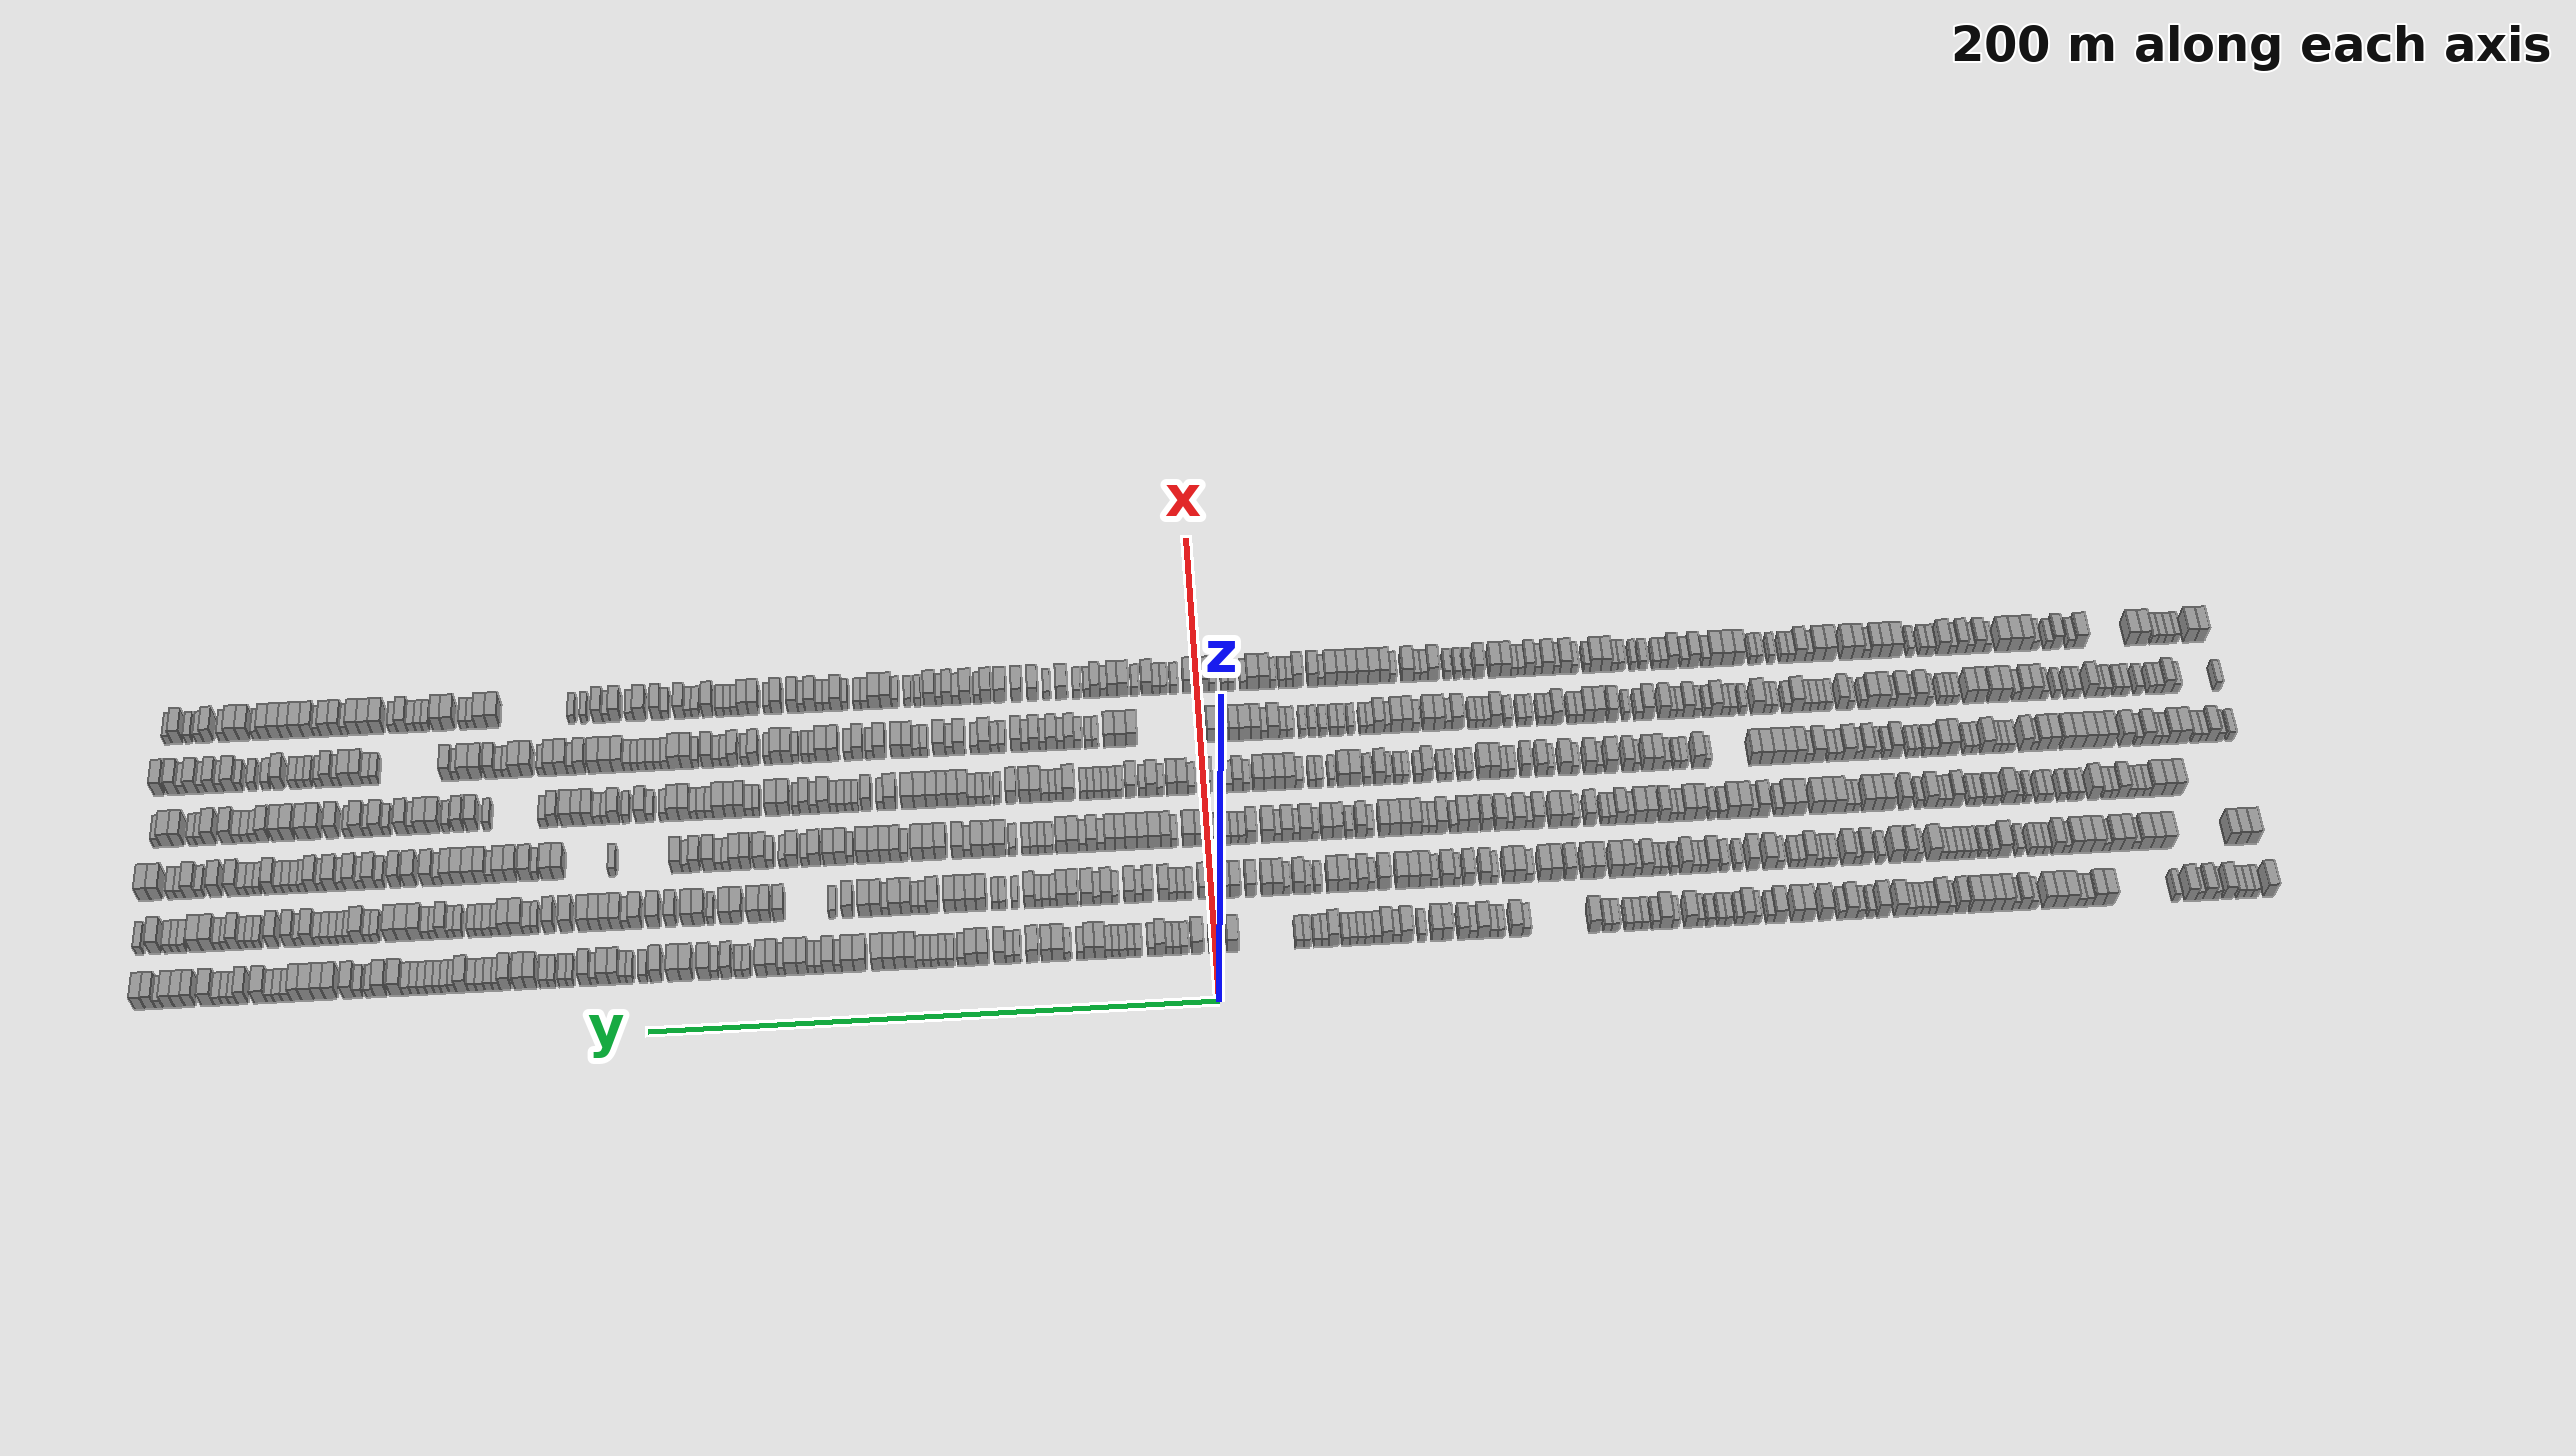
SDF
<sdf version="1.6">
 <world name="default">
  <scene>
   <sky><clouds><speed>12</speed></clouds></sky>
   <ambient>0.4 0.4 0.4 1</ambient>
   <background>0.7 0.7 0.7 1</background>
   <shadows>1</shadows>
  </scene>
  <gravity>0 0 -9.8066</gravity>
  <magnetic_field>6e-06 2.3e-05 -4.2e-05</magnetic_field>
  <physics default="0" name="default_physics" type="ode">
   <ode>
    <solver>
     <type>quick</type>
     <iters>10</iters>
     <sor>1.0</sor>
     <use_dynamic_moi_rescaling>0</use_dynamic_moi_rescaling>
    </solver>
    <constraints>
     <cfm>0</cfm>
     <erp>0.2</erp>
     <contact_max_correcting_vel>100</contact_max_correcting_vel>
     <contact_surface_layer>0.001</contact_surface_layer>
    </constraints>
   </ode>
   <max_step_size>0.004</max_step_size>
   <real_time_factor>1</real_time_factor>
   <real_time_update_rate>250</real_time_update_rate>
  </physics>
  <light name="sun" type="directional">
   <pose>0 0 10 0 0 0</pose>
   <diffuse>0.8 0.8 0.8 1</diffuse>
   <specular>0.2 0.2 0.2 1</specular>
   <attenuation>
    <range>1000</range>
    <constant>0.9</constant>
    <linear>0.01</linear>
    <quadratic>0.001</quadratic>
   </attenuation>
   <direction>-0.5 0.1 -0.9</direction>
  </light>
  <model name="building_1">
   <static>1</static>
   <pose>25.0000 -378.0573 0 0.000000 0.000000 0.000000</pose>
   <link name="link">
    <pose>0 0 4.50 0 0 0</pose>
    <collision name="collision"><geometry><box><size>10.0000 3.8853 9.0000</size></box></geometry></collision>
    <visual name="visual">
     <cast_shadows>0</cast_shadows>
     <geometry><box><size>10.0000 3.8853 9.0000</size></box></geometry>
     <material>
      <script>
       <uri>model://grey_wall/materials/scripts</uri>
       <uri>model://grey_wall/materials/textures</uri>
       <name>vrc/grey_wall</name>
      </script>
     </material>
    </visual>
   </link>
  </model>
  <model name="building_2">
   <static>1</static>
   <pose>25.0000 -372.9056 0 0.000000 0.000000 0.000000</pose>
   <link name="link">
    <pose>0 0 3.00 0 0 0</pose>
    <collision name="collision"><geometry><box><size>10.0000 2.4181 6.0000</size></box></geometry></collision>
    <visual name="visual">
     <cast_shadows>0</cast_shadows>
     <geometry><box><size>10.0000 2.4181 6.0000</size></box></geometry>
     <material>
      <script>
       <uri>model://grey_wall/materials/scripts</uri>
       <uri>model://grey_wall/materials/textures</uri>
       <name>vrc/grey_wall</name>
      </script>
     </material>
    </visual>
   </link>
  </model>
  <model name="building_3">
   <static>1</static>
   <pose>25.0000 -370.2741 0 0.000000 0.000000 0.000000</pose>
   <link name="link">
    <pose>0 0 3.00 0 0 0</pose>
    <collision name="collision"><geometry><box><size>10.0000 2.8448 6.0000</size></box></geometry></collision>
    <visual name="visual">
     <cast_shadows>0</cast_shadows>
     <geometry><box><size>10.0000 2.8448 6.0000</size></box></geometry>
     <material>
      <script>
       <uri>model://grey_wall/materials/scripts</uri>
       <uri>model://grey_wall/materials/textures</uri>
       <name>vrc/grey_wall</name>
      </script>
     </material>
    </visual>
   </link>
  </model>
  <model name="building_4">
   <static>1</static>
   <pose>25.0000 -367.5150 0 0.000000 0.000000 0.000000</pose>
   <link name="link">
    <pose>0 0 3.00 0 0 0</pose>
    <collision name="collision"><geometry><box><size>10.0000 2.6735 6.0000</size></box></geometry></collision>
    <visual name="visual">
     <cast_shadows>0</cast_shadows>
     <geometry><box><size>10.0000 2.6735 6.0000</size></box></geometry>
     <material>
      <script>
       <uri>model://grey_wall/materials/scripts</uri>
       <uri>model://grey_wall/materials/textures</uri>
       <name>vrc/grey_wall</name>
      </script>
     </material>
    </visual>
   </link>
  </model>
  <model name="building_5">
   <static>1</static>
   <pose>25.0000 -363.2117 0 0.000000 0.000000 0.000000</pose>
   <link name="link">
    <pose>0 0 4.50 0 0 0</pose>
    <collision name="collision"><geometry><box><size>10.0000 3.9331 9.0000</size></box></geometry></collision>
    <visual name="visual">
     <cast_shadows>0</cast_shadows>
     <geometry><box><size>10.0000 3.9331 9.0000</size></box></geometry>
     <material>
      <script>
       <uri>model://grey_wall/materials/scripts</uri>
       <uri>model://grey_wall/materials/textures</uri>
       <name>vrc/grey_wall</name>
      </script>
     </material>
    </visual>
   </link>
  </model>
  <model name="building_6">
   <static>1</static>
   <pose>25.0000 -359.0415 0 0.000000 0.000000 0.000000</pose>
   <link name="link">
    <pose>0 0 3.00 0 0 0</pose>
    <collision name="collision"><geometry><box><size>10.0000 2.4074 6.0000</size></box></geometry></collision>
    <visual name="visual">
     <cast_shadows>0</cast_shadows>
     <geometry><box><size>10.0000 2.4074 6.0000</size></box></geometry>
     <material>
      <script>
       <uri>model://grey_wall/materials/scripts</uri>
       <uri>model://grey_wall/materials/textures</uri>
       <name>vrc/grey_wall</name>
      </script>
     </material>
    </visual>
   </link>
  </model>
  <model name="building_7">
   <static>1</static>
   <pose>25.0000 -355.9314 0 0.000000 0.000000 0.000000</pose>
   <link name="link">
    <pose>0 0 4.50 0 0 0</pose>
    <collision name="collision"><geometry><box><size>10.0000 3.8129 9.0000</size></box></geometry></collision>
    <visual name="visual">
     <cast_shadows>0</cast_shadows>
     <geometry><box><size>10.0000 3.8129 9.0000</size></box></geometry>
     <material>
      <script>
       <uri>model://grey_wall/materials/scripts</uri>
       <uri>model://grey_wall/materials/textures</uri>
       <name>vrc/grey_wall</name>
      </script>
     </material>
    </visual>
   </link>
  </model>
  <model name="building_8">
   <static>1</static>
   <pose>25.0000 -352.7225 0 0.000000 0.000000 0.000000</pose>
   <link name="link">
    <pose>0 0 3.00 0 0 0</pose>
    <collision name="collision"><geometry><box><size>10.0000 2.6049 6.0000</size></box></geometry></collision>
    <visual name="visual">
     <cast_shadows>0</cast_shadows>
     <geometry><box><size>10.0000 2.6049 6.0000</size></box></geometry>
     <material>
      <script>
       <uri>model://grey_wall/materials/scripts</uri>
       <uri>model://grey_wall/materials/textures</uri>
       <name>vrc/grey_wall</name>
      </script>
     </material>
    </visual>
   </link>
  </model>
  <model name="building_9">
   <static>1</static>
   <pose>25.0000 -349.4914 0 0.000000 0.000000 0.000000</pose>
   <link name="link">
    <pose>0 0 4.50 0 0 0</pose>
    <collision name="collision"><geometry><box><size>10.0000 3.8573 9.0000</size></box></geometry></collision>
    <visual name="visual">
     <cast_shadows>0</cast_shadows>
     <geometry><box><size>10.0000 3.8573 9.0000</size></box></geometry>
     <material>
      <script>
       <uri>model://grey_wall/materials/scripts</uri>
       <uri>model://grey_wall/materials/textures</uri>
       <name>vrc/grey_wall</name>
      </script>
     </material>
    </visual>
   </link>
  </model>
  <model name="building_10">
   <static>1</static>
   <pose>25.0000 -344.2924 0 0.000000 0.000000 0.000000</pose>
   <link name="link">
    <pose>0 0 3.00 0 0 0</pose>
    <collision name="collision"><geometry><box><size>10.0000 2.5409 6.0000</size></box></geometry></collision>
    <visual name="visual">
     <cast_shadows>0</cast_shadows>
     <geometry><box><size>10.0000 2.5409 6.0000</size></box></geometry>
     <material>
      <script>
       <uri>model://grey_wall/materials/scripts</uri>
       <uri>model://grey_wall/materials/textures</uri>
       <name>vrc/grey_wall</name>
      </script>
     </material>
    </visual>
   </link>
  </model>
  <model name="building_11">
   <static>1</static>
   <pose>25.0000 -320.0468 0 0.000000 0.000000 0.000000</pose>
   <link name="link">
    <pose>0 0 4.50 0 0 0</pose>
    <collision name="collision"><geometry><box><size>10.0000 3.9834 9.0000</size></box></geometry></collision>
    <visual name="visual">
     <cast_shadows>0</cast_shadows>
     <geometry><box><size>10.0000 3.9834 9.0000</size></box></geometry>
     <material>
      <script>
       <uri>model://grey_wall/materials/scripts</uri>
       <uri>model://grey_wall/materials/textures</uri>
       <name>vrc/grey_wall</name>
      </script>
     </material>
    </visual>
   </link>
  </model>
  <model name="building_12">
   <static>1</static>
   <pose>25.0000 -316.0874 0 0.000000 0.000000 0.000000</pose>
   <link name="link">
    <pose>0 0 4.50 0 0 0</pose>
    <collision name="collision"><geometry><box><size>10.0000 3.9354 9.0000</size></box></geometry></collision>
    <visual name="visual">
     <cast_shadows>0</cast_shadows>
     <geometry><box><size>10.0000 3.9354 9.0000</size></box></geometry>
     <material>
      <script>
       <uri>model://grey_wall/materials/scripts</uri>
       <uri>model://grey_wall/materials/textures</uri>
       <name>vrc/grey_wall</name>
      </script>
     </material>
    </visual>
   </link>
  </model>
  <model name="building_13">
   <static>1</static>
   <pose>25.0000 -312.6934 0 0.000000 0.000000 0.000000</pose>
   <link name="link">
    <pose>0 0 3.00 0 0 0</pose>
    <collision name="collision"><geometry><box><size>10.0000 2.8527 6.0000</size></box></geometry></collision>
    <visual name="visual">
     <cast_shadows>0</cast_shadows>
     <geometry><box><size>10.0000 2.8527 6.0000</size></box></geometry>
     <material>
      <script>
       <uri>model://grey_wall/materials/scripts</uri>
       <uri>model://grey_wall/materials/textures</uri>
       <name>vrc/grey_wall</name>
      </script>
     </material>
    </visual>
   </link>
  </model>
  <model name="building_14">
   <static>1</static>
   <pose>25.0000 -309.7928 0 0.000000 0.000000 0.000000</pose>
   <link name="link">
    <pose>0 0 3.00 0 0 0</pose>
    <collision name="collision"><geometry><box><size>10.0000 2.9486 6.0000</size></box></geometry></collision>
    <visual name="visual">
     <cast_shadows>0</cast_shadows>
     <geometry><box><size>10.0000 2.9486 6.0000</size></box></geometry>
     <material>
      <script>
       <uri>model://grey_wall/materials/scripts</uri>
       <uri>model://grey_wall/materials/textures</uri>
       <name>vrc/grey_wall</name>
      </script>
     </material>
    </visual>
   </link>
  </model>
  <model name="building_15">
   <static>1</static>
   <pose>25.0000 -306.1103 0 0.000000 0.000000 0.000000</pose>
   <link name="link">
    <pose>0 0 4.50 0 0 0</pose>
    <collision name="collision"><geometry><box><size>10.0000 4.4164 9.0000</size></box></geometry></collision>
    <visual name="visual">
     <cast_shadows>0</cast_shadows>
     <geometry><box><size>10.0000 4.4164 9.0000</size></box></geometry>
     <material>
      <script>
       <uri>model://grey_wall/materials/scripts</uri>
       <uri>model://grey_wall/materials/textures</uri>
       <name>vrc/grey_wall</name>
      </script>
     </material>
    </visual>
   </link>
  </model>
  <model name="building_16">
   <static>1</static>
   <pose>25.0000 -301.9288 0 0.000000 0.000000 0.000000</pose>
   <link name="link">
    <pose>0 0 4.50 0 0 0</pose>
    <collision name="collision"><geometry><box><size>10.0000 3.9465 9.0000</size></box></geometry></collision>
    <visual name="visual">
     <cast_shadows>0</cast_shadows>
     <geometry><box><size>10.0000 3.9465 9.0000</size></box></geometry>
     <material>
      <script>
       <uri>model://grey_wall/materials/scripts</uri>
       <uri>model://grey_wall/materials/textures</uri>
       <name>vrc/grey_wall</name>
      </script>
     </material>
    </visual>
   </link>
  </model>
  <model name="building_17">
   <static>1</static>
   <pose>25.0000 -298.0596 0 0.000000 0.000000 0.000000</pose>
   <link name="link">
    <pose>0 0 4.50 0 0 0</pose>
    <collision name="collision"><geometry><box><size>10.0000 3.7918 9.0000</size></box></geometry></collision>
    <visual name="visual">
     <cast_shadows>0</cast_shadows>
     <geometry><box><size>10.0000 3.7918 9.0000</size></box></geometry>
     <material>
      <script>
       <uri>model://grey_wall/materials/scripts</uri>
       <uri>model://grey_wall/materials/textures</uri>
       <name>vrc/grey_wall</name>
      </script>
     </material>
    </visual>
   </link>
  </model>
  <model name="building_18">
   <static>1</static>
   <pose>25.0000 -292.7049 0 0.000000 0.000000 0.000000</pose>
   <link name="link">
    <pose>0 0 3.00 0 0 0</pose>
    <collision name="collision"><geometry><box><size>10.0000 2.9178 6.0000</size></box></geometry></collision>
    <visual name="visual">
     <cast_shadows>0</cast_shadows>
     <geometry><box><size>10.0000 2.9178 6.0000</size></box></geometry>
     <material>
      <script>
       <uri>model://grey_wall/materials/scripts</uri>
       <uri>model://grey_wall/materials/textures</uri>
       <name>vrc/grey_wall</name>
      </script>
     </material>
    </visual>
   </link>
  </model>
  <model name="building_19">
   <static>1</static>
   <pose>25.0000 -289.4056 0 0.000000 0.000000 0.000000</pose>
   <link name="link">
    <pose>0 0 4.50 0 0 0</pose>
    <collision name="collision"><geometry><box><size>10.0000 3.6808 9.0000</size></box></geometry></collision>
    <visual name="visual">
     <cast_shadows>0</cast_shadows>
     <geometry><box><size>10.0000 3.6808 9.0000</size></box></geometry>
     <material>
      <script>
       <uri>model://grey_wall/materials/scripts</uri>
       <uri>model://grey_wall/materials/textures</uri>
       <name>vrc/grey_wall</name>
      </script>
     </material>
    </visual>
   </link>
  </model>
  <model name="building_20">
   <static>1</static>
   <pose>25.0000 -286.3072 0 0.000000 0.000000 0.000000</pose>
   <link name="link">
    <pose>0 0 3.00 0 0 0</pose>
    <collision name="collision"><geometry><box><size>10.0000 2.5159 6.0000</size></box></geometry></collision>
    <visual name="visual">
     <cast_shadows>0</cast_shadows>
     <geometry><box><size>10.0000 2.5159 6.0000</size></box></geometry>
     <material>
      <script>
       <uri>model://grey_wall/materials/scripts</uri>
       <uri>model://grey_wall/materials/textures</uri>
       <name>vrc/grey_wall</name>
      </script>
     </material>
    </visual>
   </link>
  </model>
  <model name="building_21">
   <static>1</static>
   <pose>25.0000 -283.1710 0 0.000000 0.000000 0.000000</pose>
   <link name="link">
    <pose>0 0 4.50 0 0 0</pose>
    <collision name="collision"><geometry><box><size>10.0000 3.7564 9.0000</size></box></geometry></collision>
    <visual name="visual">
     <cast_shadows>0</cast_shadows>
     <geometry><box><size>10.0000 3.7564 9.0000</size></box></geometry>
     <material>
      <script>
       <uri>model://grey_wall/materials/scripts</uri>
       <uri>model://grey_wall/materials/textures</uri>
       <name>vrc/grey_wall</name>
      </script>
     </material>
    </visual>
   </link>
  </model>
  <model name="building_22">
   <static>1</static>
   <pose>25.0000 -279.4564 0 0.000000 0.000000 0.000000</pose>
   <link name="link">
    <pose>0 0 4.50 0 0 0</pose>
    <collision name="collision"><geometry><box><size>10.0000 3.6729 9.0000</size></box></geometry></collision>
    <visual name="visual">
     <cast_shadows>0</cast_shadows>
     <geometry><box><size>10.0000 3.6729 9.0000</size></box></geometry>
     <material>
      <script>
       <uri>model://grey_wall/materials/scripts</uri>
       <uri>model://grey_wall/materials/textures</uri>
       <name>vrc/grey_wall</name>
      </script>
     </material>
    </visual>
   </link>
  </model>
  <model name="building_23">
   <static>1</static>
   <pose>25.0000 -275.6737 0 0.000000 0.000000 0.000000</pose>
   <link name="link">
    <pose>0 0 4.50 0 0 0</pose>
    <collision name="collision"><geometry><box><size>10.0000 3.8923 9.0000</size></box></geometry></collision>
    <visual name="visual">
     <cast_shadows>0</cast_shadows>
     <geometry><box><size>10.0000 3.8923 9.0000</size></box></geometry>
     <material>
      <script>
       <uri>model://grey_wall/materials/scripts</uri>
       <uri>model://grey_wall/materials/textures</uri>
       <name>vrc/grey_wall</name>
      </script>
     </material>
    </visual>
   </link>
  </model>
  <model name="building_24">
   <static>1</static>
   <pose>25.0000 -271.7563 0 0.000000 0.000000 0.000000</pose>
   <link name="link">
    <pose>0 0 4.50 0 0 0</pose>
    <collision name="collision"><geometry><box><size>10.0000 3.9426 9.0000</size></box></geometry></collision>
    <visual name="visual">
     <cast_shadows>0</cast_shadows>
     <geometry><box><size>10.0000 3.9426 9.0000</size></box></geometry>
     <material>
      <script>
       <uri>model://grey_wall/materials/scripts</uri>
       <uri>model://grey_wall/materials/textures</uri>
       <name>vrc/grey_wall</name>
      </script>
     </material>
    </visual>
   </link>
  </model>
  <model name="building_25">
   <static>1</static>
   <pose>25.0000 -266.9585 0 0.000000 0.000000 0.000000</pose>
   <link name="link">
    <pose>0 0 4.50 0 0 0</pose>
    <collision name="collision"><geometry><box><size>10.0000 3.6529 9.0000</size></box></geometry></collision>
    <visual name="visual">
     <cast_shadows>0</cast_shadows>
     <geometry><box><size>10.0000 3.6529 9.0000</size></box></geometry>
     <material>
      <script>
       <uri>model://grey_wall/materials/scripts</uri>
       <uri>model://grey_wall/materials/textures</uri>
       <name>vrc/grey_wall</name>
      </script>
     </material>
    </visual>
   </link>
  </model>
  <model name="building_26">
   <static>1</static>
   <pose>25.0000 -262.8587 0 0.000000 0.000000 0.000000</pose>
   <link name="link">
    <pose>0 0 3.00 0 0 0</pose>
    <collision name="collision"><geometry><box><size>10.0000 2.5468 6.0000</size></box></geometry></collision>
    <visual name="visual">
     <cast_shadows>0</cast_shadows>
     <geometry><box><size>10.0000 2.5468 6.0000</size></box></geometry>
     <material>
      <script>
       <uri>model://grey_wall/materials/scripts</uri>
       <uri>model://grey_wall/materials/textures</uri>
       <name>vrc/grey_wall</name>
      </script>
     </material>
    </visual>
   </link>
  </model>
  <model name="building_27">
   <static>1</static>
   <pose>25.0000 -259.5225 0 0.000000 0.000000 0.000000</pose>
   <link name="link">
    <pose>0 0 4.50 0 0 0</pose>
    <collision name="collision"><geometry><box><size>10.0000 4.1255 9.0000</size></box></geometry></collision>
    <visual name="visual">
     <cast_shadows>0</cast_shadows>
     <geometry><box><size>10.0000 4.1255 9.0000</size></box></geometry>
     <material>
      <script>
       <uri>model://grey_wall/materials/scripts</uri>
       <uri>model://grey_wall/materials/textures</uri>
       <name>vrc/grey_wall</name>
      </script>
     </material>
    </visual>
   </link>
  </model>
  <model name="building_28">
   <static>1</static>
   <pose>25.0000 -256.1969 0 0.000000 0.000000 0.000000</pose>
   <link name="link">
    <pose>0 0 3.00 0 0 0</pose>
    <collision name="collision"><geometry><box><size>10.0000 2.5257 6.0000</size></box></geometry></collision>
    <visual name="visual">
     <cast_shadows>0</cast_shadows>
     <geometry><box><size>10.0000 2.5257 6.0000</size></box></geometry>
     <material>
      <script>
       <uri>model://grey_wall/materials/scripts</uri>
       <uri>model://grey_wall/materials/textures</uri>
       <name>vrc/grey_wall</name>
      </script>
     </material>
    </visual>
   </link>
  </model>
  <model name="building_29">
   <static>1</static>
   <pose>25.0000 -253.5728 0 0.000000 0.000000 0.000000</pose>
   <link name="link">
    <pose>0 0 3.00 0 0 0</pose>
    <collision name="collision"><geometry><box><size>10.0000 2.7225 6.0000</size></box></geometry></collision>
    <visual name="visual">
     <cast_shadows>0</cast_shadows>
     <geometry><box><size>10.0000 2.7225 6.0000</size></box></geometry>
     <material>
      <script>
       <uri>model://grey_wall/materials/scripts</uri>
       <uri>model://grey_wall/materials/textures</uri>
       <name>vrc/grey_wall</name>
      </script>
     </material>
    </visual>
   </link>
  </model>
  <model name="building_30">
   <static>1</static>
   <pose>25.0000 -250.9515 0 0.000000 0.000000 0.000000</pose>
   <link name="link">
    <pose>0 0 3.00 0 0 0</pose>
    <collision name="collision"><geometry><box><size>10.0000 2.5202 6.0000</size></box></geometry></collision>
    <visual name="visual">
     <cast_shadows>0</cast_shadows>
     <geometry><box><size>10.0000 2.5202 6.0000</size></box></geometry>
     <material>
      <script>
       <uri>model://grey_wall/materials/scripts</uri>
       <uri>model://grey_wall/materials/textures</uri>
       <name>vrc/grey_wall</name>
      </script>
     </material>
    </visual>
   </link>
  </model>
  <model name="building_31">
   <static>1</static>
   <pose>25.0000 -248.2498 0 0.000000 0.000000 0.000000</pose>
   <link name="link">
    <pose>0 0 3.00 0 0 0</pose>
    <collision name="collision"><geometry><box><size>10.0000 2.8833 6.0000</size></box></geometry></collision>
    <visual name="visual">
     <cast_shadows>0</cast_shadows>
     <geometry><box><size>10.0000 2.8833 6.0000</size></box></geometry>
     <material>
      <script>
       <uri>model://grey_wall/materials/scripts</uri>
       <uri>model://grey_wall/materials/textures</uri>
       <name>vrc/grey_wall</name>
      </script>
     </material>
    </visual>
   </link>
  </model>
  <model name="building_32">
   <static>1</static>
   <pose>25.0000 -244.6979 0 0.000000 0.000000 0.000000</pose>
   <link name="link">
    <pose>0 0 4.50 0 0 0</pose>
    <collision name="collision"><geometry><box><size>10.0000 4.2205 9.0000</size></box></geometry></collision>
    <visual name="visual">
     <cast_shadows>0</cast_shadows>
     <geometry><box><size>10.0000 4.2205 9.0000</size></box></geometry>
     <material>
      <script>
       <uri>model://grey_wall/materials/scripts</uri>
       <uri>model://grey_wall/materials/textures</uri>
       <name>vrc/grey_wall</name>
      </script>
     </material>
    </visual>
   </link>
  </model>
  <model name="building_33">
   <static>1</static>
   <pose>25.0000 -238.4900 0 0.000000 0.000000 0.000000</pose>
   <link name="link">
    <pose>0 0 4.50 0 0 0</pose>
    <collision name="collision"><geometry><box><size>10.0000 4.1953 9.0000</size></box></geometry></collision>
    <visual name="visual">
     <cast_shadows>0</cast_shadows>
     <geometry><box><size>10.0000 4.1953 9.0000</size></box></geometry>
     <material>
      <script>
       <uri>model://grey_wall/materials/scripts</uri>
       <uri>model://grey_wall/materials/textures</uri>
       <name>vrc/grey_wall</name>
      </script>
     </material>
    </visual>
   </link>
  </model>
  <model name="building_34">
   <static>1</static>
   <pose>25.0000 -234.1194 0 0.000000 0.000000 0.000000</pose>
   <link name="link">
    <pose>0 0 3.00 0 0 0</pose>
    <collision name="collision"><geometry><box><size>10.0000 2.5460 6.0000</size></box></geometry></collision>
    <visual name="visual">
     <cast_shadows>0</cast_shadows>
     <geometry><box><size>10.0000 2.5460 6.0000</size></box></geometry>
     <material>
      <script>
       <uri>model://grey_wall/materials/scripts</uri>
       <uri>model://grey_wall/materials/textures</uri>
       <name>vrc/grey_wall</name>
      </script>
     </material>
    </visual>
   </link>
  </model>
  <model name="building_35">
   <static>1</static>
   <pose>25.0000 -230.4059 0 0.000000 0.000000 0.000000</pose>
   <link name="link">
    <pose>0 0 3.00 0 0 0</pose>
    <collision name="collision"><geometry><box><size>10.0000 2.8809 6.0000</size></box></geometry></collision>
    <visual name="visual">
     <cast_shadows>0</cast_shadows>
     <geometry><box><size>10.0000 2.8809 6.0000</size></box></geometry>
     <material>
      <script>
       <uri>model://grey_wall/materials/scripts</uri>
       <uri>model://grey_wall/materials/textures</uri>
       <name>vrc/grey_wall</name>
      </script>
     </material>
    </visual>
   </link>
  </model>
  <model name="building_36">
   <static>1</static>
   <pose>25.0000 -226.9026 0 0.000000 0.000000 0.000000</pose>
   <link name="link">
    <pose>0 0 4.50 0 0 0</pose>
    <collision name="collision"><geometry><box><size>10.0000 4.1258 9.0000</size></box></geometry></collision>
    <visual name="visual">
     <cast_shadows>0</cast_shadows>
     <geometry><box><size>10.0000 4.1258 9.0000</size></box></geometry>
     <material>
      <script>
       <uri>model://grey_wall/materials/scripts</uri>
       <uri>model://grey_wall/materials/textures</uri>
       <name>vrc/grey_wall</name>
      </script>
     </material>
    </visual>
   </link>
  </model>
  <model name="building_37">
   <static>1</static>
   <pose>25.0000 -223.4613 0 0.000000 0.000000 0.000000</pose>
   <link name="link">
    <pose>0 0 3.00 0 0 0</pose>
    <collision name="collision"><geometry><box><size>10.0000 2.7568 6.0000</size></box></geometry></collision>
    <visual name="visual">
     <cast_shadows>0</cast_shadows>
     <geometry><box><size>10.0000 2.7568 6.0000</size></box></geometry>
     <material>
      <script>
       <uri>model://grey_wall/materials/scripts</uri>
       <uri>model://grey_wall/materials/textures</uri>
       <name>vrc/grey_wall</name>
      </script>
     </material>
    </visual>
   </link>
  </model>
  <model name="building_38">
   <static>1</static>
   <pose>25.0000 -217.8344 0 0.000000 0.000000 0.000000</pose>
   <link name="link">
    <pose>0 0 4.50 0 0 0</pose>
    <collision name="collision"><geometry><box><size>10.0000 4.4970 9.0000</size></box></geometry></collision>
    <visual name="visual">
     <cast_shadows>0</cast_shadows>
     <geometry><box><size>10.0000 4.4970 9.0000</size></box></geometry>
     <material>
      <script>
       <uri>model://grey_wall/materials/scripts</uri>
       <uri>model://grey_wall/materials/textures</uri>
       <name>vrc/grey_wall</name>
      </script>
     </material>
    </visual>
   </link>
  </model>
  <model name="building_39">
   <static>1</static>
   <pose>25.0000 -211.4842 0 0.000000 0.000000 0.000000</pose>
   <link name="link">
    <pose>0 0 4.50 0 0 0</pose>
    <collision name="collision"><geometry><box><size>10.0000 4.2034 9.0000</size></box></geometry></collision>
    <visual name="visual">
     <cast_shadows>0</cast_shadows>
     <geometry><box><size>10.0000 4.2034 9.0000</size></box></geometry>
     <material>
      <script>
       <uri>model://grey_wall/materials/scripts</uri>
       <uri>model://grey_wall/materials/textures</uri>
       <name>vrc/grey_wall</name>
      </script>
     </material>
    </visual>
   </link>
  </model>
  <model name="building_40">
   <static>1</static>
   <pose>25.0000 -207.4801 0 0.000000 0.000000 0.000000</pose>
   <link name="link">
    <pose>0 0 4.50 0 0 0</pose>
    <collision name="collision"><geometry><box><size>10.0000 3.8048 9.0000</size></box></geometry></collision>
    <visual name="visual">
     <cast_shadows>0</cast_shadows>
     <geometry><box><size>10.0000 3.8048 9.0000</size></box></geometry>
     <material>
      <script>
       <uri>model://grey_wall/materials/scripts</uri>
       <uri>model://grey_wall/materials/textures</uri>
       <name>vrc/grey_wall</name>
      </script>
     </material>
    </visual>
   </link>
  </model>
  <model name="building_41">
   <static>1</static>
   <pose>25.0000 -201.3981 0 0.000000 0.000000 0.000000</pose>
   <link name="link">
    <pose>0 0 4.50 0 0 0</pose>
    <collision name="collision"><geometry><box><size>10.0000 4.3593 9.0000</size></box></geometry></collision>
    <visual name="visual">
     <cast_shadows>0</cast_shadows>
     <geometry><box><size>10.0000 4.3593 9.0000</size></box></geometry>
     <material>
      <script>
       <uri>model://grey_wall/materials/scripts</uri>
       <uri>model://grey_wall/materials/textures</uri>
       <name>vrc/grey_wall</name>
      </script>
     </material>
    </visual>
   </link>
  </model>
  <model name="building_42">
   <static>1</static>
   <pose>25.0000 -197.8453 0 0.000000 0.000000 0.000000</pose>
   <link name="link">
    <pose>0 0 3.00 0 0 0</pose>
    <collision name="collision"><geometry><box><size>10.0000 2.7462 6.0000</size></box></geometry></collision>
    <visual name="visual">
     <cast_shadows>0</cast_shadows>
     <geometry><box><size>10.0000 2.7462 6.0000</size></box></geometry>
     <material>
      <script>
       <uri>model://grey_wall/materials/scripts</uri>
       <uri>model://grey_wall/materials/textures</uri>
       <name>vrc/grey_wall</name>
      </script>
     </material>
    </visual>
   </link>
  </model>
  <model name="building_43">
   <static>1</static>
   <pose>25.0000 -193.1822 0 0.000000 0.000000 0.000000</pose>
   <link name="link">
    <pose>0 0 3.00 0 0 0</pose>
    <collision name="collision"><geometry><box><size>10.0000 2.5799 6.0000</size></box></geometry></collision>
    <visual name="visual">
     <cast_shadows>0</cast_shadows>
     <geometry><box><size>10.0000 2.5799 6.0000</size></box></geometry>
     <material>
      <script>
       <uri>model://grey_wall/materials/scripts</uri>
       <uri>model://grey_wall/materials/textures</uri>
       <name>vrc/grey_wall</name>
      </script>
     </material>
    </visual>
   </link>
  </model>
  <model name="building_44">
   <static>1</static>
   <pose>25.0000 -189.8920 0 0.000000 0.000000 0.000000</pose>
   <link name="link">
    <pose>0 0 4.50 0 0 0</pose>
    <collision name="collision"><geometry><box><size>10.0000 4.0007 9.0000</size></box></geometry></collision>
    <visual name="visual">
     <cast_shadows>0</cast_shadows>
     <geometry><box><size>10.0000 4.0007 9.0000</size></box></geometry>
     <material>
      <script>
       <uri>model://grey_wall/materials/scripts</uri>
       <uri>model://grey_wall/materials/textures</uri>
       <name>vrc/grey_wall</name>
      </script>
     </material>
    </visual>
   </link>
  </model>
  <model name="building_45">
   <static>1</static>
   <pose>25.0000 -186.6365 0 0.000000 0.000000 0.000000</pose>
   <link name="link">
    <pose>0 0 3.00 0 0 0</pose>
    <collision name="collision"><geometry><box><size>10.0000 2.5104 6.0000</size></box></geometry></collision>
    <visual name="visual">
     <cast_shadows>0</cast_shadows>
     <geometry><box><size>10.0000 2.5104 6.0000</size></box></geometry>
     <material>
      <script>
       <uri>model://grey_wall/materials/scripts</uri>
       <uri>model://grey_wall/materials/textures</uri>
       <name>vrc/grey_wall</name>
      </script>
     </material>
    </visual>
   </link>
  </model>
  <model name="building_46">
   <static>1</static>
   <pose>25.0000 -182.9909 0 0.000000 0.000000 0.000000</pose>
   <link name="link">
    <pose>0 0 3.00 0 0 0</pose>
    <collision name="collision"><geometry><box><size>10.0000 2.7807 6.0000</size></box></geometry></collision>
    <visual name="visual">
     <cast_shadows>0</cast_shadows>
     <geometry><box><size>10.0000 2.7807 6.0000</size></box></geometry>
     <material>
      <script>
       <uri>model://grey_wall/materials/scripts</uri>
       <uri>model://grey_wall/materials/textures</uri>
       <name>vrc/grey_wall</name>
      </script>
     </material>
    </visual>
   </link>
  </model>
  <model name="building_47">
   <static>1</static>
   <pose>25.0000 -180.2894 0 0.000000 0.000000 0.000000</pose>
   <link name="link">
    <pose>0 0 3.00 0 0 0</pose>
    <collision name="collision"><geometry><box><size>10.0000 2.6222 6.0000</size></box></geometry></collision>
    <visual name="visual">
     <cast_shadows>0</cast_shadows>
     <geometry><box><size>10.0000 2.6222 6.0000</size></box></geometry>
     <material>
      <script>
       <uri>model://grey_wall/materials/scripts</uri>
       <uri>model://grey_wall/materials/textures</uri>
       <name>vrc/grey_wall</name>
      </script>
     </material>
    </visual>
   </link>
  </model>
  <model name="building_48">
   <static>1</static>
   <pose>25.0000 -176.5260 0 0.000000 0.000000 0.000000</pose>
   <link name="link">
    <pose>0 0 3.00 0 0 0</pose>
    <collision name="collision"><geometry><box><size>10.0000 2.9046 6.0000</size></box></geometry></collision>
    <visual name="visual">
     <cast_shadows>0</cast_shadows>
     <geometry><box><size>10.0000 2.9046 6.0000</size></box></geometry>
     <material>
      <script>
       <uri>model://grey_wall/materials/scripts</uri>
       <uri>model://grey_wall/materials/textures</uri>
       <name>vrc/grey_wall</name>
      </script>
     </material>
    </visual>
   </link>
  </model>
  <model name="building_49">
   <static>1</static>
   <pose>25.0000 -172.7656 0 0.000000 0.000000 0.000000</pose>
   <link name="link">
    <pose>0 0 3.00 0 0 0</pose>
    <collision name="collision"><geometry><box><size>10.0000 2.6161 6.0000</size></box></geometry></collision>
    <visual name="visual">
     <cast_shadows>0</cast_shadows>
     <geometry><box><size>10.0000 2.6161 6.0000</size></box></geometry>
     <material>
      <script>
       <uri>model://grey_wall/materials/scripts</uri>
       <uri>model://grey_wall/materials/textures</uri>
       <name>vrc/grey_wall</name>
      </script>
     </material>
    </visual>
   </link>
  </model>
  <model name="building_50">
   <static>1</static>
   <pose>25.0000 -169.3121 0 0.000000 0.000000 0.000000</pose>
   <link name="link">
    <pose>0 0 4.50 0 0 0</pose>
    <collision name="collision"><geometry><box><size>10.0000 4.2911 9.0000</size></box></geometry></collision>
    <visual name="visual">
     <cast_shadows>0</cast_shadows>
     <geometry><box><size>10.0000 4.2911 9.0000</size></box></geometry>
     <material>
      <script>
       <uri>model://grey_wall/materials/scripts</uri>
       <uri>model://grey_wall/materials/textures</uri>
       <name>vrc/grey_wall</name>
      </script>
     </material>
    </visual>
   </link>
  </model>
  <model name="building_51">
   <static>1</static>
   <pose>25.0000 -163.8628 0 0.000000 0.000000 0.000000</pose>
   <link name="link">
    <pose>0 0 3.00 0 0 0</pose>
    <collision name="collision"><geometry><box><size>10.0000 2.6074 6.0000</size></box></geometry></collision>
    <visual name="visual">
     <cast_shadows>0</cast_shadows>
     <geometry><box><size>10.0000 2.6074 6.0000</size></box></geometry>
     <material>
      <script>
       <uri>model://grey_wall/materials/scripts</uri>
       <uri>model://grey_wall/materials/textures</uri>
       <name>vrc/grey_wall</name>
      </script>
     </material>
    </visual>
   </link>
  </model>
  <model name="building_52">
   <static>1</static>
   <pose>25.0000 -160.3956 0 0.000000 0.000000 0.000000</pose>
   <link name="link">
    <pose>0 0 4.50 0 0 0</pose>
    <collision name="collision"><geometry><box><size>10.0000 4.3271 9.0000</size></box></geometry></collision>
    <visual name="visual">
     <cast_shadows>0</cast_shadows>
     <geometry><box><size>10.0000 4.3271 9.0000</size></box></geometry>
     <material>
      <script>
       <uri>model://grey_wall/materials/scripts</uri>
       <uri>model://grey_wall/materials/textures</uri>
       <name>vrc/grey_wall</name>
      </script>
     </material>
    </visual>
   </link>
  </model>
  <model name="building_53">
   <static>1</static>
   <pose>25.0000 -156.8101 0 0.000000 0.000000 0.000000</pose>
   <link name="link">
    <pose>0 0 3.00 0 0 0</pose>
    <collision name="collision"><geometry><box><size>10.0000 2.8438 6.0000</size></box></geometry></collision>
    <visual name="visual">
     <cast_shadows>0</cast_shadows>
     <geometry><box><size>10.0000 2.8438 6.0000</size></box></geometry>
     <material>
      <script>
       <uri>model://grey_wall/materials/scripts</uri>
       <uri>model://grey_wall/materials/textures</uri>
       <name>vrc/grey_wall</name>
      </script>
     </material>
    </visual>
   </link>
  </model>
  <model name="building_54">
   <static>1</static>
   <pose>25.0000 -153.0133 0 0.000000 0.000000 0.000000</pose>
   <link name="link">
    <pose>0 0 3.00 0 0 0</pose>
    <collision name="collision"><geometry><box><size>10.0000 2.7499 6.0000</size></box></geometry></collision>
    <visual name="visual">
     <cast_shadows>0</cast_shadows>
     <geometry><box><size>10.0000 2.7499 6.0000</size></box></geometry>
     <material>
      <script>
       <uri>model://grey_wall/materials/scripts</uri>
       <uri>model://grey_wall/materials/textures</uri>
       <name>vrc/grey_wall</name>
      </script>
     </material>
    </visual>
   </link>
  </model>
  <model name="building_55">
   <static>1</static>
   <pose>25.0000 -150.1531 0 0.000000 0.000000 0.000000</pose>
   <link name="link">
    <pose>0 0 3.00 0 0 0</pose>
    <collision name="collision"><geometry><box><size>10.0000 2.9705 6.0000</size></box></geometry></collision>
    <visual name="visual">
     <cast_shadows>0</cast_shadows>
     <geometry><box><size>10.0000 2.9705 6.0000</size></box></geometry>
     <material>
      <script>
       <uri>model://grey_wall/materials/scripts</uri>
       <uri>model://grey_wall/materials/textures</uri>
       <name>vrc/grey_wall</name>
      </script>
     </material>
    </visual>
   </link>
  </model>
  <model name="building_56">
   <static>1</static>
   <pose>25.0000 -147.2460 0 0.000000 0.000000 0.000000</pose>
   <link name="link">
    <pose>0 0 3.00 0 0 0</pose>
    <collision name="collision"><geometry><box><size>10.0000 2.8437 6.0000</size></box></geometry></collision>
    <visual name="visual">
     <cast_shadows>0</cast_shadows>
     <geometry><box><size>10.0000 2.8437 6.0000</size></box></geometry>
     <material>
      <script>
       <uri>model://grey_wall/materials/scripts</uri>
       <uri>model://grey_wall/materials/textures</uri>
       <name>vrc/grey_wall</name>
      </script>
     </material>
    </visual>
   </link>
  </model>
  <model name="building_57">
   <static>1</static>
   <pose>25.0000 -142.3547 0 0.000000 0.000000 0.000000</pose>
   <link name="link">
    <pose>0 0 3.00 0 0 0</pose>
    <collision name="collision"><geometry><box><size>10.0000 2.9388 6.0000</size></box></geometry></collision>
    <visual name="visual">
     <cast_shadows>0</cast_shadows>
     <geometry><box><size>10.0000 2.9388 6.0000</size></box></geometry>
     <material>
      <script>
       <uri>model://grey_wall/materials/scripts</uri>
       <uri>model://grey_wall/materials/textures</uri>
       <name>vrc/grey_wall</name>
      </script>
     </material>
    </visual>
   </link>
  </model>
  <model name="building_58">
   <static>1</static>
   <pose>25.0000 -139.4949 0 0.000000 0.000000 0.000000</pose>
   <link name="link">
    <pose>0 0 3.00 0 0 0</pose>
    <collision name="collision"><geometry><box><size>10.0000 2.7809 6.0000</size></box></geometry></collision>
    <visual name="visual">
     <cast_shadows>0</cast_shadows>
     <geometry><box><size>10.0000 2.7809 6.0000</size></box></geometry>
     <material>
      <script>
       <uri>model://grey_wall/materials/scripts</uri>
       <uri>model://grey_wall/materials/textures</uri>
       <name>vrc/grey_wall</name>
      </script>
     </material>
    </visual>
   </link>
  </model>
  <model name="building_59">
   <static>1</static>
   <pose>25.0000 -135.0178 0 0.000000 0.000000 0.000000</pose>
   <link name="link">
    <pose>0 0 4.50 0 0 0</pose>
    <collision name="collision"><geometry><box><size>10.0000 4.1733 9.0000</size></box></geometry></collision>
    <visual name="visual">
     <cast_shadows>0</cast_shadows>
     <geometry><box><size>10.0000 4.1733 9.0000</size></box></geometry>
     <material>
      <script>
       <uri>model://grey_wall/materials/scripts</uri>
       <uri>model://grey_wall/materials/textures</uri>
       <name>vrc/grey_wall</name>
      </script>
     </material>
    </visual>
   </link>
  </model>
  <model name="building_60">
   <static>1</static>
   <pose>25.0000 -110.4983 0 0.000000 0.000000 0.000000</pose>
   <link name="link">
    <pose>0 0 3.00 0 0 0</pose>
    <collision name="collision"><geometry><box><size>10.0000 2.9552 6.0000</size></box></geometry></collision>
    <visual name="visual">
     <cast_shadows>0</cast_shadows>
     <geometry><box><size>10.0000 2.9552 6.0000</size></box></geometry>
     <material>
      <script>
       <uri>model://grey_wall/materials/scripts</uri>
       <uri>model://grey_wall/materials/textures</uri>
       <name>vrc/grey_wall</name>
      </script>
     </material>
    </visual>
   </link>
  </model>
  <model name="building_61">
   <static>1</static>
   <pose>25.0000 -106.8751 0 0.000000 0.000000 0.000000</pose>
   <link name="link">
    <pose>0 0 4.50 0 0 0</pose>
    <collision name="collision"><geometry><box><size>10.0000 4.2911 9.0000</size></box></geometry></collision>
    <visual name="visual">
     <cast_shadows>0</cast_shadows>
     <geometry><box><size>10.0000 4.2911 9.0000</size></box></geometry>
     <material>
      <script>
       <uri>model://grey_wall/materials/scripts</uri>
       <uri>model://grey_wall/materials/textures</uri>
       <name>vrc/grey_wall</name>
      </script>
     </material>
    </visual>
   </link>
  </model>
  <model name="building_62">
   <static>1</static>
   <pose>25.0000 -101.4941 0 0.000000 0.000000 0.000000</pose>
   <link name="link">
    <pose>0 0 3.00 0 0 0</pose>
    <collision name="collision"><geometry><box><size>10.0000 2.4709 6.0000</size></box></geometry></collision>
    <visual name="visual">
     <cast_shadows>0</cast_shadows>
     <geometry><box><size>10.0000 2.4709 6.0000</size></box></geometry>
     <material>
      <script>
       <uri>model://grey_wall/materials/scripts</uri>
       <uri>model://grey_wall/materials/textures</uri>
       <name>vrc/grey_wall</name>
      </script>
     </material>
    </visual>
   </link>
  </model>
  <model name="building_63">
   <static>1</static>
   <pose>25.0000 -98.8210 0 0.000000 0.000000 0.000000</pose>
   <link name="link">
    <pose>0 0 3.00 0 0 0</pose>
    <collision name="collision"><geometry><box><size>10.0000 2.8753 6.0000</size></box></geometry></collision>
    <visual name="visual">
     <cast_shadows>0</cast_shadows>
     <geometry><box><size>10.0000 2.8753 6.0000</size></box></geometry>
     <material>
      <script>
       <uri>model://grey_wall/materials/scripts</uri>
       <uri>model://grey_wall/materials/textures</uri>
       <name>vrc/grey_wall</name>
      </script>
     </material>
    </visual>
   </link>
  </model>
  <model name="building_64">
   <static>1</static>
   <pose>25.0000 -95.1807 0 0.000000 0.000000 0.000000</pose>
   <link name="link">
    <pose>0 0 4.50 0 0 0</pose>
    <collision name="collision"><geometry><box><size>10.0000 4.4053 9.0000</size></box></geometry></collision>
    <visual name="visual">
     <cast_shadows>0</cast_shadows>
     <geometry><box><size>10.0000 4.4053 9.0000</size></box></geometry>
     <material>
      <script>
       <uri>model://grey_wall/materials/scripts</uri>
       <uri>model://grey_wall/materials/textures</uri>
       <name>vrc/grey_wall</name>
      </script>
     </material>
    </visual>
   </link>
  </model>
  <model name="building_65">
   <static>1</static>
   <pose>25.0000 -91.4868 0 0.000000 0.000000 0.000000</pose>
   <link name="link">
    <pose>0 0 3.00 0 0 0</pose>
    <collision name="collision"><geometry><box><size>10.0000 2.9825 6.0000</size></box></geometry></collision>
    <visual name="visual">
     <cast_shadows>0</cast_shadows>
     <geometry><box><size>10.0000 2.9825 6.0000</size></box></geometry>
     <material>
      <script>
       <uri>model://grey_wall/materials/scripts</uri>
       <uri>model://grey_wall/materials/textures</uri>
       <name>vrc/grey_wall</name>
      </script>
     </material>
    </visual>
   </link>
  </model>
  <model name="building_66">
   <static>1</static>
   <pose>25.0000 -88.0575 0 0.000000 0.000000 0.000000</pose>
   <link name="link">
    <pose>0 0 4.50 0 0 0</pose>
    <collision name="collision"><geometry><box><size>10.0000 3.8760 9.0000</size></box></geometry></collision>
    <visual name="visual">
     <cast_shadows>0</cast_shadows>
     <geometry><box><size>10.0000 3.8760 9.0000</size></box></geometry>
     <material>
      <script>
       <uri>model://grey_wall/materials/scripts</uri>
       <uri>model://grey_wall/materials/textures</uri>
       <name>vrc/grey_wall</name>
      </script>
     </material>
    </visual>
   </link>
  </model>
  <model name="building_67">
   <static>1</static>
   <pose>25.0000 -82.3033 0 0.000000 0.000000 0.000000</pose>
   <link name="link">
    <pose>0 0 4.50 0 0 0</pose>
    <collision name="collision"><geometry><box><size>10.0000 3.6325 9.0000</size></box></geometry></collision>
    <visual name="visual">
     <cast_shadows>0</cast_shadows>
     <geometry><box><size>10.0000 3.6325 9.0000</size></box></geometry>
     <material>
      <script>
       <uri>model://grey_wall/materials/scripts</uri>
       <uri>model://grey_wall/materials/textures</uri>
       <name>vrc/grey_wall</name>
      </script>
     </material>
    </visual>
   </link>
  </model>
  <model name="building_68">
   <static>1</static>
   <pose>25.0000 -78.5575 0 0.000000 0.000000 0.000000</pose>
   <link name="link">
    <pose>0 0 4.50 0 0 0</pose>
    <collision name="collision"><geometry><box><size>10.0000 3.8590 9.0000</size></box></geometry></collision>
    <visual name="visual">
     <cast_shadows>0</cast_shadows>
     <geometry><box><size>10.0000 3.8590 9.0000</size></box></geometry>
     <material>
      <script>
       <uri>model://grey_wall/materials/scripts</uri>
       <uri>model://grey_wall/materials/textures</uri>
       <name>vrc/grey_wall</name>
      </script>
     </material>
    </visual>
   </link>
  </model>
  <model name="building_69">
   <static>1</static>
   <pose>25.0000 -73.2572 0 0.000000 0.000000 0.000000</pose>
   <link name="link">
    <pose>0 0 3.00 0 0 0</pose>
    <collision name="collision"><geometry><box><size>10.0000 2.7417 6.0000</size></box></geometry></collision>
    <visual name="visual">
     <cast_shadows>0</cast_shadows>
     <geometry><box><size>10.0000 2.7417 6.0000</size></box></geometry>
     <material>
      <script>
       <uri>model://grey_wall/materials/scripts</uri>
       <uri>model://grey_wall/materials/textures</uri>
       <name>vrc/grey_wall</name>
      </script>
     </material>
    </visual>
   </link>
  </model>
  <model name="building_70">
   <static>1</static>
   <pose>25.0000 -67.7949 0 0.000000 0.000000 0.000000</pose>
   <link name="link">
    <pose>0 0 4.50 0 0 0</pose>
    <collision name="collision"><geometry><box><size>10.0000 4.1830 9.0000</size></box></geometry></collision>
    <visual name="visual">
     <cast_shadows>0</cast_shadows>
     <geometry><box><size>10.0000 4.1830 9.0000</size></box></geometry>
     <material>
      <script>
       <uri>model://grey_wall/materials/scripts</uri>
       <uri>model://grey_wall/materials/textures</uri>
       <name>vrc/grey_wall</name>
      </script>
     </material>
    </visual>
   </link>
  </model>
  <model name="building_71">
   <static>1</static>
   <pose>25.0000 -64.2286 0 0.000000 0.000000 0.000000</pose>
   <link name="link">
    <pose>0 0 3.00 0 0 0</pose>
    <collision name="collision"><geometry><box><size>10.0000 2.9495 6.0000</size></box></geometry></collision>
    <visual name="visual">
     <cast_shadows>0</cast_shadows>
     <geometry><box><size>10.0000 2.9495 6.0000</size></box></geometry>
     <material>
      <script>
       <uri>model://grey_wall/materials/scripts</uri>
       <uri>model://grey_wall/materials/textures</uri>
       <name>vrc/grey_wall</name>
      </script>
     </material>
    </visual>
   </link>
  </model>
  <model name="building_72">
   <static>1</static>
   <pose>25.0000 -60.8207 0 0.000000 0.000000 0.000000</pose>
   <link name="link">
    <pose>0 0 4.50 0 0 0</pose>
    <collision name="collision"><geometry><box><size>10.0000 3.8664 9.0000</size></box></geometry></collision>
    <visual name="visual">
     <cast_shadows>0</cast_shadows>
     <geometry><box><size>10.0000 3.8664 9.0000</size></box></geometry>
     <material>
      <script>
       <uri>model://grey_wall/materials/scripts</uri>
       <uri>model://grey_wall/materials/textures</uri>
       <name>vrc/grey_wall</name>
      </script>
     </material>
    </visual>
   </link>
  </model>
  <model name="building_73">
   <static>1</static>
   <pose>25.0000 -57.3881 0 0.000000 0.000000 0.000000</pose>
   <link name="link">
    <pose>0 0 3.00 0 0 0</pose>
    <collision name="collision"><geometry><box><size>10.0000 2.9990 6.0000</size></box></geometry></collision>
    <visual name="visual">
     <cast_shadows>0</cast_shadows>
     <geometry><box><size>10.0000 2.9990 6.0000</size></box></geometry>
     <material>
      <script>
       <uri>model://grey_wall/materials/scripts</uri>
       <uri>model://grey_wall/materials/textures</uri>
       <name>vrc/grey_wall</name>
      </script>
     </material>
    </visual>
   </link>
  </model>
  <model name="building_74">
   <static>1</static>
   <pose>25.0000 -54.4028 0 0.000000 0.000000 0.000000</pose>
   <link name="link">
    <pose>0 0 3.00 0 0 0</pose>
    <collision name="collision"><geometry><box><size>10.0000 2.9715 6.0000</size></box></geometry></collision>
    <visual name="visual">
     <cast_shadows>0</cast_shadows>
     <geometry><box><size>10.0000 2.9715 6.0000</size></box></geometry>
     <material>
      <script>
       <uri>model://grey_wall/materials/scripts</uri>
       <uri>model://grey_wall/materials/textures</uri>
       <name>vrc/grey_wall</name>
      </script>
     </material>
    </visual>
   </link>
  </model>
  <model name="building_75">
   <static>1</static>
   <pose>25.0000 -51.5189 0 0.000000 0.000000 0.000000</pose>
   <link name="link">
    <pose>0 0 3.00 0 0 0</pose>
    <collision name="collision"><geometry><box><size>10.0000 2.7965 6.0000</size></box></geometry></collision>
    <visual name="visual">
     <cast_shadows>0</cast_shadows>
     <geometry><box><size>10.0000 2.7965 6.0000</size></box></geometry>
     <material>
      <script>
       <uri>model://grey_wall/materials/scripts</uri>
       <uri>model://grey_wall/materials/textures</uri>
       <name>vrc/grey_wall</name>
      </script>
     </material>
    </visual>
   </link>
  </model>
  <model name="building_76">
   <static>1</static>
   <pose>25.0000 -48.7850 0 0.000000 0.000000 0.000000</pose>
   <link name="link">
    <pose>0 0 3.00 0 0 0</pose>
    <collision name="collision"><geometry><box><size>10.0000 2.6713 6.0000</size></box></geometry></collision>
    <visual name="visual">
     <cast_shadows>0</cast_shadows>
     <geometry><box><size>10.0000 2.6713 6.0000</size></box></geometry>
     <material>
      <script>
       <uri>model://grey_wall/materials/scripts</uri>
       <uri>model://grey_wall/materials/textures</uri>
       <name>vrc/grey_wall</name>
      </script>
     </material>
    </visual>
   </link>
  </model>
  <model name="building_77">
   <static>1</static>
   <pose>25.0000 -46.0974 0 0.000000 0.000000 0.000000</pose>
   <link name="link">
    <pose>0 0 3.00 0 0 0</pose>
    <collision name="collision"><geometry><box><size>10.0000 2.7039 6.0000</size></box></geometry></collision>
    <visual name="visual">
     <cast_shadows>0</cast_shadows>
     <geometry><box><size>10.0000 2.7039 6.0000</size></box></geometry>
     <material>
      <script>
       <uri>model://grey_wall/materials/scripts</uri>
       <uri>model://grey_wall/materials/textures</uri>
       <name>vrc/grey_wall</name>
      </script>
     </material>
    </visual>
   </link>
  </model>
  <model name="building_78">
   <static>1</static>
   <pose>25.0000 -41.8344 0 0.000000 0.000000 0.000000</pose>
   <link name="link">
    <pose>0 0 4.50 0 0 0</pose>
    <collision name="collision"><geometry><box><size>10.0000 3.8222 9.0000</size></box></geometry></collision>
    <visual name="visual">
     <cast_shadows>0</cast_shadows>
     <geometry><box><size>10.0000 3.8222 9.0000</size></box></geometry>
     <material>
      <script>
       <uri>model://grey_wall/materials/scripts</uri>
       <uri>model://grey_wall/materials/textures</uri>
       <name>vrc/grey_wall</name>
      </script>
     </material>
    </visual>
   </link>
  </model>
  <model name="building_79">
   <static>1</static>
   <pose>25.0000 -38.6605 0 0.000000 0.000000 0.000000</pose>
   <link name="link">
    <pose>0 0 3.00 0 0 0</pose>
    <collision name="collision"><geometry><box><size>10.0000 2.5257 6.0000</size></box></geometry></collision>
    <visual name="visual">
     <cast_shadows>0</cast_shadows>
     <geometry><box><size>10.0000 2.5257 6.0000</size></box></geometry>
     <material>
      <script>
       <uri>model://grey_wall/materials/scripts</uri>
       <uri>model://grey_wall/materials/textures</uri>
       <name>vrc/grey_wall</name>
      </script>
     </material>
    </visual>
   </link>
  </model>
  <model name="building_80">
   <static>1</static>
   <pose>25.0000 -36.0347 0 0.000000 0.000000 0.000000</pose>
   <link name="link">
    <pose>0 0 3.00 0 0 0</pose>
    <collision name="collision"><geometry><box><size>10.0000 2.7259 6.0000</size></box></geometry></collision>
    <visual name="visual">
     <cast_shadows>0</cast_shadows>
     <geometry><box><size>10.0000 2.7259 6.0000</size></box></geometry>
     <material>
      <script>
       <uri>model://grey_wall/materials/scripts</uri>
       <uri>model://grey_wall/materials/textures</uri>
       <name>vrc/grey_wall</name>
      </script>
     </material>
    </visual>
   </link>
  </model>
  <model name="building_81">
   <static>1</static>
   <pose>25.0000 -32.3212 0 0.000000 0.000000 0.000000</pose>
   <link name="link">
    <pose>0 0 3.00 0 0 0</pose>
    <collision name="collision"><geometry><box><size>10.0000 2.7010 6.0000</size></box></geometry></collision>
    <visual name="visual">
     <cast_shadows>0</cast_shadows>
     <geometry><box><size>10.0000 2.7010 6.0000</size></box></geometry>
     <material>
      <script>
       <uri>model://grey_wall/materials/scripts</uri>
       <uri>model://grey_wall/materials/textures</uri>
       <name>vrc/grey_wall</name>
      </script>
     </material>
    </visual>
   </link>
  </model>
  <model name="building_82">
   <static>1</static>
   <pose>25.0000 -29.5241 0 0.000000 0.000000 0.000000</pose>
   <link name="link">
    <pose>0 0 3.00 0 0 0</pose>
    <collision name="collision"><geometry><box><size>10.0000 2.8931 6.0000</size></box></geometry></collision>
    <visual name="visual">
     <cast_shadows>0</cast_shadows>
     <geometry><box><size>10.0000 2.8931 6.0000</size></box></geometry>
     <material>
      <script>
       <uri>model://grey_wall/materials/scripts</uri>
       <uri>model://grey_wall/materials/textures</uri>
       <name>vrc/grey_wall</name>
      </script>
     </material>
    </visual>
   </link>
  </model>
  <model name="building_83">
   <static>1</static>
   <pose>25.0000 -5.8344 0 0.000000 0.000000 0.000000</pose>
   <link name="link">
    <pose>0 0 4.50 0 0 0</pose>
    <collision name="collision"><geometry><box><size>10.0000 4.1621 9.0000</size></box></geometry></collision>
    <visual name="visual">
     <cast_shadows>0</cast_shadows>
     <geometry><box><size>10.0000 4.1621 9.0000</size></box></geometry>
     <material>
      <script>
       <uri>model://grey_wall/materials/scripts</uri>
       <uri>model://grey_wall/materials/textures</uri>
       <name>vrc/grey_wall</name>
      </script>
     </material>
    </visual>
   </link>
  </model>
  <model name="building_84">
   <static>1</static>
   <pose>25.0000 -1.3093 0 0.000000 0.000000 0.000000</pose>
   <link name="link">
    <pose>0 0 3.00 0 0 0</pose>
    <collision name="collision"><geometry><box><size>10.0000 2.8879 6.0000</size></box></geometry></collision>
    <visual name="visual">
     <cast_shadows>0</cast_shadows>
     <geometry><box><size>10.0000 2.8879 6.0000</size></box></geometry>
     <material>
      <script>
       <uri>model://grey_wall/materials/scripts</uri>
       <uri>model://grey_wall/materials/textures</uri>
       <name>vrc/grey_wall</name>
      </script>
     </material>
    </visual>
   </link>
  </model>
  <model name="building_85">
   <static>1</static>
   <pose>25.0000 1.3610 0 0.000000 0.000000 0.000000</pose>
   <link name="link">
    <pose>0 0 3.00 0 0 0</pose>
    <collision name="collision"><geometry><box><size>10.0000 2.4527 6.0000</size></box></geometry></collision>
    <visual name="visual">
     <cast_shadows>0</cast_shadows>
     <geometry><box><size>10.0000 2.4527 6.0000</size></box></geometry>
     <material>
      <script>
       <uri>model://grey_wall/materials/scripts</uri>
       <uri>model://grey_wall/materials/textures</uri>
       <name>vrc/grey_wall</name>
      </script>
     </material>
    </visual>
   </link>
  </model>
  <model name="building_86">
   <static>1</static>
   <pose>25.0000 6.6766 0 0.000000 0.000000 0.000000</pose>
   <link name="link">
    <pose>0 0 4.50 0 0 0</pose>
    <collision name="collision"><geometry><box><size>10.0000 4.1785 9.0000</size></box></geometry></collision>
    <visual name="visual">
     <cast_shadows>0</cast_shadows>
     <geometry><box><size>10.0000 4.1785 9.0000</size></box></geometry>
     <material>
      <script>
       <uri>model://grey_wall/materials/scripts</uri>
       <uri>model://grey_wall/materials/textures</uri>
       <name>vrc/grey_wall</name>
      </script>
     </material>
    </visual>
   </link>
  </model>
  <model name="building_87">
   <static>1</static>
   <pose>25.0000 11.2618 0 0.000000 0.000000 0.000000</pose>
   <link name="link">
    <pose>0 0 3.00 0 0 0</pose>
    <collision name="collision"><geometry><box><size>10.0000 2.9920 6.0000</size></box></geometry></collision>
    <visual name="visual">
     <cast_shadows>0</cast_shadows>
     <geometry><box><size>10.0000 2.9920 6.0000</size></box></geometry>
     <material>
      <script>
       <uri>model://grey_wall/materials/scripts</uri>
       <uri>model://grey_wall/materials/textures</uri>
       <name>vrc/grey_wall</name>
      </script>
     </material>
    </visual>
   </link>
  </model>
  <model name="building_88">
   <static>1</static>
   <pose>25.0000 14.1272 0 0.000000 0.000000 0.000000</pose>
   <link name="link">
    <pose>0 0 3.00 0 0 0</pose>
    <collision name="collision"><geometry><box><size>10.0000 2.7387 6.0000</size></box></geometry></collision>
    <visual name="visual">
     <cast_shadows>0</cast_shadows>
     <geometry><box><size>10.0000 2.7387 6.0000</size></box></geometry>
     <material>
      <script>
       <uri>model://grey_wall/materials/scripts</uri>
       <uri>model://grey_wall/materials/textures</uri>
       <name>vrc/grey_wall</name>
      </script>
     </material>
    </visual>
   </link>
  </model>
  <model name="building_89">
   <static>1</static>
   <pose>25.0000 16.7258 0 0.000000 0.000000 0.000000</pose>
   <link name="link">
    <pose>0 0 3.00 0 0 0</pose>
    <collision name="collision"><geometry><box><size>10.0000 2.4585 6.0000</size></box></geometry></collision>
    <visual name="visual">
     <cast_shadows>0</cast_shadows>
     <geometry><box><size>10.0000 2.4585 6.0000</size></box></geometry>
     <material>
      <script>
       <uri>model://grey_wall/materials/scripts</uri>
       <uri>model://grey_wall/materials/textures</uri>
       <name>vrc/grey_wall</name>
      </script>
     </material>
    </visual>
   </link>
  </model>
  <model name="building_90">
   <static>1</static>
   <pose>25.0000 19.8600 0 0.000000 0.000000 0.000000</pose>
   <link name="link">
    <pose>0 0 4.50 0 0 0</pose>
    <collision name="collision"><geometry><box><size>10.0000 3.8098 9.0000</size></box></geometry></collision>
    <visual name="visual">
     <cast_shadows>0</cast_shadows>
     <geometry><box><size>10.0000 3.8098 9.0000</size></box></geometry>
     <material>
      <script>
       <uri>model://grey_wall/materials/scripts</uri>
       <uri>model://grey_wall/materials/textures</uri>
       <name>vrc/grey_wall</name>
      </script>
     </material>
    </visual>
   </link>
  </model>
  <model name="building_91">
   <static>1</static>
   <pose>25.0000 23.0571 0 0.000000 0.000000 0.000000</pose>
   <link name="link">
    <pose>0 0 3.00 0 0 0</pose>
    <collision name="collision"><geometry><box><size>10.0000 2.5845 6.0000</size></box></geometry></collision>
    <visual name="visual">
     <cast_shadows>0</cast_shadows>
     <geometry><box><size>10.0000 2.5845 6.0000</size></box></geometry>
     <material>
      <script>
       <uri>model://grey_wall/materials/scripts</uri>
       <uri>model://grey_wall/materials/textures</uri>
       <name>vrc/grey_wall</name>
      </script>
     </material>
    </visual>
   </link>
  </model>
  <model name="building_92">
   <static>1</static>
   <pose>25.0000 27.6592 0 0.000000 0.000000 0.000000</pose>
   <link name="link">
    <pose>0 0 3.00 0 0 0</pose>
    <collision name="collision"><geometry><box><size>10.0000 2.6197 6.0000</size></box></geometry></collision>
    <visual name="visual">
     <cast_shadows>0</cast_shadows>
     <geometry><box><size>10.0000 2.6197 6.0000</size></box></geometry>
     <material>
      <script>
       <uri>model://grey_wall/materials/scripts</uri>
       <uri>model://grey_wall/materials/textures</uri>
       <name>vrc/grey_wall</name>
      </script>
     </material>
    </visual>
   </link>
  </model>
  <model name="building_93">
   <static>1</static>
   <pose>25.0000 30.2643 0 0.000000 0.000000 0.000000</pose>
   <link name="link">
    <pose>0 0 3.00 0 0 0</pose>
    <collision name="collision"><geometry><box><size>10.0000 2.5906 6.0000</size></box></geometry></collision>
    <visual name="visual">
     <cast_shadows>0</cast_shadows>
     <geometry><box><size>10.0000 2.5906 6.0000</size></box></geometry>
     <material>
      <script>
       <uri>model://grey_wall/materials/scripts</uri>
       <uri>model://grey_wall/materials/textures</uri>
       <name>vrc/grey_wall</name>
      </script>
     </material>
    </visual>
   </link>
  </model>
  <model name="building_94">
   <static>1</static>
   <pose>25.0000 33.0000 0 0.000000 0.000000 0.000000</pose>
   <link name="link">
    <pose>0 0 3.00 0 0 0</pose>
    <collision name="collision"><geometry><box><size>10.0000 2.8807 6.0000</size></box></geometry></collision>
    <visual name="visual">
     <cast_shadows>0</cast_shadows>
     <geometry><box><size>10.0000 2.8807 6.0000</size></box></geometry>
     <material>
      <script>
       <uri>model://grey_wall/materials/scripts</uri>
       <uri>model://grey_wall/materials/textures</uri>
       <name>vrc/grey_wall</name>
      </script>
     </material>
    </visual>
   </link>
  </model>
  <model name="building_95">
   <static>1</static>
   <pose>25.0000 35.6938 0 0.000000 0.000000 0.000000</pose>
   <link name="link">
    <pose>0 0 3.00 0 0 0</pose>
    <collision name="collision"><geometry><box><size>10.0000 2.5071 6.0000</size></box></geometry></collision>
    <visual name="visual">
     <cast_shadows>0</cast_shadows>
     <geometry><box><size>10.0000 2.5071 6.0000</size></box></geometry>
     <material>
      <script>
       <uri>model://grey_wall/materials/scripts</uri>
       <uri>model://grey_wall/materials/textures</uri>
       <name>vrc/grey_wall</name>
      </script>
     </material>
    </visual>
   </link>
  </model>
  <model name="building_96">
   <static>1</static>
   <pose>25.0000 38.1934 0 0.000000 0.000000 0.000000</pose>
   <link name="link">
    <pose>0 0 3.00 0 0 0</pose>
    <collision name="collision"><geometry><box><size>10.0000 2.4921 6.0000</size></box></geometry></collision>
    <visual name="visual">
     <cast_shadows>0</cast_shadows>
     <geometry><box><size>10.0000 2.4921 6.0000</size></box></geometry>
     <material>
      <script>
       <uri>model://grey_wall/materials/scripts</uri>
       <uri>model://grey_wall/materials/textures</uri>
       <name>vrc/grey_wall</name>
      </script>
     </material>
    </visual>
   </link>
  </model>
  <model name="building_97">
   <static>1</static>
   <pose>25.0000 41.3327 0 0.000000 0.000000 0.000000</pose>
   <link name="link">
    <pose>0 0 4.50 0 0 0</pose>
    <collision name="collision"><geometry><box><size>10.0000 3.7866 9.0000</size></box></geometry></collision>
    <visual name="visual">
     <cast_shadows>0</cast_shadows>
     <geometry><box><size>10.0000 3.7866 9.0000</size></box></geometry>
     <material>
      <script>
       <uri>model://grey_wall/materials/scripts</uri>
       <uri>model://grey_wall/materials/textures</uri>
       <name>vrc/grey_wall</name>
      </script>
     </material>
    </visual>
   </link>
  </model>
  <model name="building_98">
   <static>1</static>
   <pose>25.0000 45.0840 0 0.000000 0.000000 0.000000</pose>
   <link name="link">
    <pose>0 0 4.50 0 0 0</pose>
    <collision name="collision"><geometry><box><size>10.0000 3.7160 9.0000</size></box></geometry></collision>
    <visual name="visual">
     <cast_shadows>0</cast_shadows>
     <geometry><box><size>10.0000 3.7160 9.0000</size></box></geometry>
     <material>
      <script>
       <uri>model://grey_wall/materials/scripts</uri>
       <uri>model://grey_wall/materials/textures</uri>
       <name>vrc/grey_wall</name>
      </script>
     </material>
    </visual>
   </link>
  </model>
  <model name="building_99">
   <static>1</static>
   <pose>25.0000 48.1846 0 0.000000 0.000000 0.000000</pose>
   <link name="link">
    <pose>0 0 3.00 0 0 0</pose>
    <collision name="collision"><geometry><box><size>10.0000 2.4852 6.0000</size></box></geometry></collision>
    <visual name="visual">
     <cast_shadows>0</cast_shadows>
     <geometry><box><size>10.0000 2.4852 6.0000</size></box></geometry>
     <material>
      <script>
       <uri>model://grey_wall/materials/scripts</uri>
       <uri>model://grey_wall/materials/textures</uri>
       <name>vrc/grey_wall</name>
      </script>
     </material>
    </visual>
   </link>
  </model>
  <model name="building_100">
   <static>1</static>
   <pose>25.0000 52.6859 0 0.000000 0.000000 0.000000</pose>
   <link name="link">
    <pose>0 0 3.00 0 0 0</pose>
    <collision name="collision"><geometry><box><size>10.0000 2.5173 6.0000</size></box></geometry></collision>
    <visual name="visual">
     <cast_shadows>0</cast_shadows>
     <geometry><box><size>10.0000 2.5173 6.0000</size></box></geometry>
     <material>
      <script>
       <uri>model://grey_wall/materials/scripts</uri>
       <uri>model://grey_wall/materials/textures</uri>
       <name>vrc/grey_wall</name>
      </script>
     </material>
    </visual>
   </link>
  </model>
  <model name="building_101">
   <static>1</static>
   <pose>25.0000 56.1383 0 0.000000 0.000000 0.000000</pose>
   <link name="link">
    <pose>0 0 4.50 0 0 0</pose>
    <collision name="collision"><geometry><box><size>10.0000 4.3876 9.0000</size></box></geometry></collision>
    <visual name="visual">
     <cast_shadows>0</cast_shadows>
     <geometry><box><size>10.0000 4.3876 9.0000</size></box></geometry>
     <material>
      <script>
       <uri>model://grey_wall/materials/scripts</uri>
       <uri>model://grey_wall/materials/textures</uri>
       <name>vrc/grey_wall</name>
      </script>
     </material>
    </visual>
   </link>
  </model>
  <model name="building_102">
   <static>1</static>
   <pose>25.0000 60.1665 0 0.000000 0.000000 0.000000</pose>
   <link name="link">
    <pose>0 0 4.50 0 0 0</pose>
    <collision name="collision"><geometry><box><size>10.0000 3.6688 9.0000</size></box></geometry></collision>
    <visual name="visual">
     <cast_shadows>0</cast_shadows>
     <geometry><box><size>10.0000 3.6688 9.0000</size></box></geometry>
     <material>
      <script>
       <uri>model://grey_wall/materials/scripts</uri>
       <uri>model://grey_wall/materials/textures</uri>
       <name>vrc/grey_wall</name>
      </script>
     </material>
    </visual>
   </link>
  </model>
  <model name="building_103">
   <static>1</static>
   <pose>25.0000 65.1158 0 0.000000 0.000000 0.000000</pose>
   <link name="link">
    <pose>0 0 4.50 0 0 0</pose>
    <collision name="collision"><geometry><box><size>10.0000 4.2298 9.0000</size></box></geometry></collision>
    <visual name="visual">
     <cast_shadows>0</cast_shadows>
     <geometry><box><size>10.0000 4.2298 9.0000</size></box></geometry>
     <material>
      <script>
       <uri>model://grey_wall/materials/scripts</uri>
       <uri>model://grey_wall/materials/textures</uri>
       <name>vrc/grey_wall</name>
      </script>
     </material>
    </visual>
   </link>
  </model>
  <model name="building_104">
   <static>1</static>
   <pose>25.0000 70.5004 0 0.000000 0.000000 0.000000</pose>
   <link name="link">
    <pose>0 0 3.00 0 0 0</pose>
    <collision name="collision"><geometry><box><size>10.0000 2.5395 6.0000</size></box></geometry></collision>
    <visual name="visual">
     <cast_shadows>0</cast_shadows>
     <geometry><box><size>10.0000 2.5395 6.0000</size></box></geometry>
     <material>
      <script>
       <uri>model://grey_wall/materials/scripts</uri>
       <uri>model://grey_wall/materials/textures</uri>
       <name>vrc/grey_wall</name>
      </script>
     </material>
    </visual>
   </link>
  </model>
  <model name="building_105">
   <static>1</static>
   <pose>25.0000 73.2379 0 0.000000 0.000000 0.000000</pose>
   <link name="link">
    <pose>0 0 3.00 0 0 0</pose>
    <collision name="collision"><geometry><box><size>10.0000 2.9355 6.0000</size></box></geometry></collision>
    <visual name="visual">
     <cast_shadows>0</cast_shadows>
     <geometry><box><size>10.0000 2.9355 6.0000</size></box></geometry>
     <material>
      <script>
       <uri>model://grey_wall/materials/scripts</uri>
       <uri>model://grey_wall/materials/textures</uri>
       <name>vrc/grey_wall</name>
      </script>
     </material>
    </visual>
   </link>
  </model>
  <model name="building_106">
   <static>1</static>
   <pose>25.0000 76.7027 0 0.000000 0.000000 0.000000</pose>
   <link name="link">
    <pose>0 0 4.50 0 0 0</pose>
    <collision name="collision"><geometry><box><size>10.0000 3.9942 9.0000</size></box></geometry></collision>
    <visual name="visual">
     <cast_shadows>0</cast_shadows>
     <geometry><box><size>10.0000 3.9942 9.0000</size></box></geometry>
     <material>
      <script>
       <uri>model://grey_wall/materials/scripts</uri>
       <uri>model://grey_wall/materials/textures</uri>
       <name>vrc/grey_wall</name>
      </script>
     </material>
    </visual>
   </link>
  </model>
  <model name="building_107">
   <static>1</static>
   <pose>25.0000 82.6907 0 0.000000 0.000000 0.000000</pose>
   <link name="link">
    <pose>0 0 4.50 0 0 0</pose>
    <collision name="collision"><geometry><box><size>10.0000 3.9817 9.0000</size></box></geometry></collision>
    <visual name="visual">
     <cast_shadows>0</cast_shadows>
     <geometry><box><size>10.0000 3.9817 9.0000</size></box></geometry>
     <material>
      <script>
       <uri>model://grey_wall/materials/scripts</uri>
       <uri>model://grey_wall/materials/textures</uri>
       <name>vrc/grey_wall</name>
      </script>
     </material>
    </visual>
   </link>
  </model>
  <model name="building_108">
   <static>1</static>
   <pose>25.0000 86.8249 0 0.000000 0.000000 0.000000</pose>
   <link name="link">
    <pose>0 0 4.50 0 0 0</pose>
    <collision name="collision"><geometry><box><size>10.0000 4.2866 9.0000</size></box></geometry></collision>
    <visual name="visual">
     <cast_shadows>0</cast_shadows>
     <geometry><box><size>10.0000 4.2866 9.0000</size></box></geometry>
     <material>
      <script>
       <uri>model://grey_wall/materials/scripts</uri>
       <uri>model://grey_wall/materials/textures</uri>
       <name>vrc/grey_wall</name>
      </script>
     </material>
    </visual>
   </link>
  </model>
  <model name="building_109">
   <static>1</static>
   <pose>25.0000 90.3235 0 0.000000 0.000000 0.000000</pose>
   <link name="link">
    <pose>0 0 3.00 0 0 0</pose>
    <collision name="collision"><geometry><box><size>10.0000 2.7106 6.0000</size></box></geometry></collision>
    <visual name="visual">
     <cast_shadows>0</cast_shadows>
     <geometry><box><size>10.0000 2.7106 6.0000</size></box></geometry>
     <material>
      <script>
       <uri>model://grey_wall/materials/scripts</uri>
       <uri>model://grey_wall/materials/textures</uri>
       <name>vrc/grey_wall</name>
      </script>
     </material>
    </visual>
   </link>
  </model>
  <model name="building_110">
   <static>1</static>
   <pose>25.0000 94.1667 0 0.000000 0.000000 0.000000</pose>
   <link name="link">
    <pose>0 0 3.00 0 0 0</pose>
    <collision name="collision"><geometry><box><size>10.0000 2.9757 6.0000</size></box></geometry></collision>
    <visual name="visual">
     <cast_shadows>0</cast_shadows>
     <geometry><box><size>10.0000 2.9757 6.0000</size></box></geometry>
     <material>
      <script>
       <uri>model://grey_wall/materials/scripts</uri>
       <uri>model://grey_wall/materials/textures</uri>
       <name>vrc/grey_wall</name>
      </script>
     </material>
    </visual>
   </link>
  </model>
  <model name="building_111">
   <static>1</static>
   <pose>25.0000 97.0424 0 0.000000 0.000000 0.000000</pose>
   <link name="link">
    <pose>0 0 3.00 0 0 0</pose>
    <collision name="collision"><geometry><box><size>10.0000 2.7758 6.0000</size></box></geometry></collision>
    <visual name="visual">
     <cast_shadows>0</cast_shadows>
     <geometry><box><size>10.0000 2.7758 6.0000</size></box></geometry>
     <material>
      <script>
       <uri>model://grey_wall/materials/scripts</uri>
       <uri>model://grey_wall/materials/textures</uri>
       <name>vrc/grey_wall</name>
      </script>
     </material>
    </visual>
   </link>
  </model>
  <model name="building_112">
   <static>1</static>
   <pose>25.0000 99.7522 0 0.000000 0.000000 0.000000</pose>
   <link name="link">
    <pose>0 0 3.00 0 0 0</pose>
    <collision name="collision"><geometry><box><size>10.0000 2.6437 6.0000</size></box></geometry></collision>
    <visual name="visual">
     <cast_shadows>0</cast_shadows>
     <geometry><box><size>10.0000 2.6437 6.0000</size></box></geometry>
     <material>
      <script>
       <uri>model://grey_wall/materials/scripts</uri>
       <uri>model://grey_wall/materials/textures</uri>
       <name>vrc/grey_wall</name>
      </script>
     </material>
    </visual>
   </link>
  </model>
  <model name="building_113">
   <static>1</static>
   <pose>25.0000 102.4102 0 0.000000 0.000000 0.000000</pose>
   <link name="link">
    <pose>0 0 3.00 0 0 0</pose>
    <collision name="collision"><geometry><box><size>10.0000 2.6722 6.0000</size></box></geometry></collision>
    <visual name="visual">
     <cast_shadows>0</cast_shadows>
     <geometry><box><size>10.0000 2.6722 6.0000</size></box></geometry>
     <material>
      <script>
       <uri>model://grey_wall/materials/scripts</uri>
       <uri>model://grey_wall/materials/textures</uri>
       <name>vrc/grey_wall</name>
      </script>
     </material>
    </visual>
   </link>
  </model>
  <model name="building_114">
   <static>1</static>
   <pose>25.0000 105.0721 0 0.000000 0.000000 0.000000</pose>
   <link name="link">
    <pose>0 0 3.00 0 0 0</pose>
    <collision name="collision"><geometry><box><size>10.0000 2.6515 6.0000</size></box></geometry></collision>
    <visual name="visual">
     <cast_shadows>0</cast_shadows>
     <geometry><box><size>10.0000 2.6515 6.0000</size></box></geometry>
     <material>
      <script>
       <uri>model://grey_wall/materials/scripts</uri>
       <uri>model://grey_wall/materials/textures</uri>
       <name>vrc/grey_wall</name>
      </script>
     </material>
    </visual>
   </link>
  </model>
  <model name="building_115">
   <static>1</static>
   <pose>25.0000 108.2667 0 0.000000 0.000000 0.000000</pose>
   <link name="link">
    <pose>0 0 4.50 0 0 0</pose>
    <collision name="collision"><geometry><box><size>10.0000 3.7378 9.0000</size></box></geometry></collision>
    <visual name="visual">
     <cast_shadows>0</cast_shadows>
     <geometry><box><size>10.0000 3.7378 9.0000</size></box></geometry>
     <material>
      <script>
       <uri>model://grey_wall/materials/scripts</uri>
       <uri>model://grey_wall/materials/textures</uri>
       <name>vrc/grey_wall</name>
      </script>
     </material>
    </visual>
   </link>
  </model>
  <model name="building_116">
   <static>1</static>
   <pose>25.0000 112.0498 0 0.000000 0.000000 0.000000</pose>
   <link name="link">
    <pose>0 0 4.50 0 0 0</pose>
    <collision name="collision"><geometry><box><size>10.0000 3.8282 9.0000</size></box></geometry></collision>
    <visual name="visual">
     <cast_shadows>0</cast_shadows>
     <geometry><box><size>10.0000 3.8282 9.0000</size></box></geometry>
     <material>
      <script>
       <uri>model://grey_wall/materials/scripts</uri>
       <uri>model://grey_wall/materials/textures</uri>
       <name>vrc/grey_wall</name>
      </script>
     </material>
    </visual>
   </link>
  </model>
  <model name="building_117">
   <static>1</static>
   <pose>25.0000 115.9300 0 0.000000 0.000000 0.000000</pose>
   <link name="link">
    <pose>0 0 4.50 0 0 0</pose>
    <collision name="collision"><geometry><box><size>10.0000 3.9321 9.0000</size></box></geometry></collision>
    <visual name="visual">
     <cast_shadows>0</cast_shadows>
     <geometry><box><size>10.0000 3.9321 9.0000</size></box></geometry>
     <material>
      <script>
       <uri>model://grey_wall/materials/scripts</uri>
       <uri>model://grey_wall/materials/textures</uri>
       <name>vrc/grey_wall</name>
      </script>
     </material>
    </visual>
   </link>
  </model>
  <model name="building_118">
   <static>1</static>
   <pose>25.0000 119.9202 0 0.000000 0.000000 0.000000</pose>
   <link name="link">
    <pose>0 0 4.50 0 0 0</pose>
    <collision name="collision"><geometry><box><size>10.0000 4.0483 9.0000</size></box></geometry></collision>
    <visual name="visual">
     <cast_shadows>0</cast_shadows>
     <geometry><box><size>10.0000 4.0483 9.0000</size></box></geometry>
     <material>
      <script>
       <uri>model://grey_wall/materials/scripts</uri>
       <uri>model://grey_wall/materials/textures</uri>
       <name>vrc/grey_wall</name>
      </script>
     </material>
    </visual>
   </link>
  </model>
  <model name="building_119">
   <static>1</static>
   <pose>25.0000 126.1278 0 0.000000 0.000000 0.000000</pose>
   <link name="link">
    <pose>0 0 4.50 0 0 0</pose>
    <collision name="collision"><geometry><box><size>10.0000 4.3670 9.0000</size></box></geometry></collision>
    <visual name="visual">
     <cast_shadows>0</cast_shadows>
     <geometry><box><size>10.0000 4.3670 9.0000</size></box></geometry>
     <material>
      <script>
       <uri>model://grey_wall/materials/scripts</uri>
       <uri>model://grey_wall/materials/textures</uri>
       <name>vrc/grey_wall</name>
      </script>
     </material>
    </visual>
   </link>
  </model>
  <model name="building_120">
   <static>1</static>
   <pose>25.0000 130.4576 0 0.000000 0.000000 0.000000</pose>
   <link name="link">
    <pose>0 0 4.50 0 0 0</pose>
    <collision name="collision"><geometry><box><size>10.0000 4.2925 9.0000</size></box></geometry></collision>
    <visual name="visual">
     <cast_shadows>0</cast_shadows>
     <geometry><box><size>10.0000 4.2925 9.0000</size></box></geometry>
     <material>
      <script>
       <uri>model://grey_wall/materials/scripts</uri>
       <uri>model://grey_wall/materials/textures</uri>
       <name>vrc/grey_wall</name>
      </script>
     </material>
    </visual>
   </link>
  </model>
  <model name="building_121">
   <static>1</static>
   <pose>25.0000 133.9042 0 0.000000 0.000000 0.000000</pose>
   <link name="link">
    <pose>0 0 3.00 0 0 0</pose>
    <collision name="collision"><geometry><box><size>10.0000 2.6008 6.0000</size></box></geometry></collision>
    <visual name="visual">
     <cast_shadows>0</cast_shadows>
     <geometry><box><size>10.0000 2.6008 6.0000</size></box></geometry>
     <material>
      <script>
       <uri>model://grey_wall/materials/scripts</uri>
       <uri>model://grey_wall/materials/textures</uri>
       <name>vrc/grey_wall</name>
      </script>
     </material>
    </visual>
   </link>
  </model>
  <model name="building_122">
   <static>1</static>
   <pose>25.0000 137.3210 0 0.000000 0.000000 0.000000</pose>
   <link name="link">
    <pose>0 0 4.50 0 0 0</pose>
    <collision name="collision"><geometry><box><size>10.0000 4.2329 9.0000</size></box></geometry></collision>
    <visual name="visual">
     <cast_shadows>0</cast_shadows>
     <geometry><box><size>10.0000 4.2329 9.0000</size></box></geometry>
     <material>
      <script>
       <uri>model://grey_wall/materials/scripts</uri>
       <uri>model://grey_wall/materials/textures</uri>
       <name>vrc/grey_wall</name>
      </script>
     </material>
    </visual>
   </link>
  </model>
  <model name="building_123">
   <static>1</static>
   <pose>25.0000 140.7127 0 0.000000 0.000000 0.000000</pose>
   <link name="link">
    <pose>0 0 3.00 0 0 0</pose>
    <collision name="collision"><geometry><box><size>10.0000 2.5505 6.0000</size></box></geometry></collision>
    <visual name="visual">
     <cast_shadows>0</cast_shadows>
     <geometry><box><size>10.0000 2.5505 6.0000</size></box></geometry>
     <material>
      <script>
       <uri>model://grey_wall/materials/scripts</uri>
       <uri>model://grey_wall/materials/textures</uri>
       <name>vrc/grey_wall</name>
      </script>
     </material>
    </visual>
   </link>
  </model>
  <model name="building_124">
   <static>1</static>
   <pose>25.0000 143.2748 0 0.000000 0.000000 0.000000</pose>
   <link name="link">
    <pose>0 0 3.00 0 0 0</pose>
    <collision name="collision"><geometry><box><size>10.0000 2.5737 6.0000</size></box></geometry></collision>
    <visual name="visual">
     <cast_shadows>0</cast_shadows>
     <geometry><box><size>10.0000 2.5737 6.0000</size></box></geometry>
     <material>
      <script>
       <uri>model://grey_wall/materials/scripts</uri>
       <uri>model://grey_wall/materials/textures</uri>
       <name>vrc/grey_wall</name>
      </script>
     </material>
    </visual>
   </link>
  </model>
  <model name="building_125">
   <static>1</static>
   <pose>25.0000 146.3825 0 0.000000 0.000000 0.000000</pose>
   <link name="link">
    <pose>0 0 4.50 0 0 0</pose>
    <collision name="collision"><geometry><box><size>10.0000 3.6417 9.0000</size></box></geometry></collision>
    <visual name="visual">
     <cast_shadows>0</cast_shadows>
     <geometry><box><size>10.0000 3.6417 9.0000</size></box></geometry>
     <material>
      <script>
       <uri>model://grey_wall/materials/scripts</uri>
       <uri>model://grey_wall/materials/textures</uri>
       <name>vrc/grey_wall</name>
      </script>
     </material>
    </visual>
   </link>
  </model>
  <model name="building_126">
   <static>1</static>
   <pose>25.0000 150.4087 0 0.000000 0.000000 0.000000</pose>
   <link name="link">
    <pose>0 0 4.50 0 0 0</pose>
    <collision name="collision"><geometry><box><size>10.0000 4.4107 9.0000</size></box></geometry></collision>
    <visual name="visual">
     <cast_shadows>0</cast_shadows>
     <geometry><box><size>10.0000 4.4107 9.0000</size></box></geometry>
     <material>
      <script>
       <uri>model://grey_wall/materials/scripts</uri>
       <uri>model://grey_wall/materials/textures</uri>
       <name>vrc/grey_wall</name>
      </script>
     </material>
    </visual>
   </link>
  </model>
  <model name="building_127">
   <static>1</static>
   <pose>25.0000 153.8480 0 0.000000 0.000000 0.000000</pose>
   <link name="link">
    <pose>0 0 3.00 0 0 0</pose>
    <collision name="collision"><geometry><box><size>10.0000 2.4679 6.0000</size></box></geometry></collision>
    <visual name="visual">
     <cast_shadows>0</cast_shadows>
     <geometry><box><size>10.0000 2.4679 6.0000</size></box></geometry>
     <material>
      <script>
       <uri>model://grey_wall/materials/scripts</uri>
       <uri>model://grey_wall/materials/textures</uri>
       <name>vrc/grey_wall</name>
      </script>
     </material>
    </visual>
   </link>
  </model>
  <model name="building_128">
   <static>1</static>
   <pose>25.0000 157.0626 0 0.000000 0.000000 0.000000</pose>
   <link name="link">
    <pose>0 0 4.50 0 0 0</pose>
    <collision name="collision"><geometry><box><size>10.0000 3.9612 9.0000</size></box></geometry></collision>
    <visual name="visual">
     <cast_shadows>0</cast_shadows>
     <geometry><box><size>10.0000 3.9612 9.0000</size></box></geometry>
     <material>
      <script>
       <uri>model://grey_wall/materials/scripts</uri>
       <uri>model://grey_wall/materials/textures</uri>
       <name>vrc/grey_wall</name>
      </script>
     </material>
    </visual>
   </link>
  </model>
  <model name="building_129">
   <static>1</static>
   <pose>25.0000 160.8853 0 0.000000 0.000000 0.000000</pose>
   <link name="link">
    <pose>0 0 4.50 0 0 0</pose>
    <collision name="collision"><geometry><box><size>10.0000 3.6843 9.0000</size></box></geometry></collision>
    <visual name="visual">
     <cast_shadows>0</cast_shadows>
     <geometry><box><size>10.0000 3.6843 9.0000</size></box></geometry>
     <material>
      <script>
       <uri>model://grey_wall/materials/scripts</uri>
       <uri>model://grey_wall/materials/textures</uri>
       <name>vrc/grey_wall</name>
      </script>
     </material>
    </visual>
   </link>
  </model>
  <model name="building_130">
   <static>1</static>
   <pose>25.0000 166.1612 0 0.000000 0.000000 0.000000</pose>
   <link name="link">
    <pose>0 0 3.00 0 0 0</pose>
    <collision name="collision"><geometry><box><size>10.0000 2.8673 6.0000</size></box></geometry></collision>
    <visual name="visual">
     <cast_shadows>0</cast_shadows>
     <geometry><box><size>10.0000 2.8673 6.0000</size></box></geometry>
     <material>
      <script>
       <uri>model://grey_wall/materials/scripts</uri>
       <uri>model://grey_wall/materials/textures</uri>
       <name>vrc/grey_wall</name>
      </script>
     </material>
    </visual>
   </link>
  </model>
  <model name="building_131">
   <static>1</static>
   <pose>25.0000 168.8858 0 0.000000 0.000000 0.000000</pose>
   <link name="link">
    <pose>0 0 3.00 0 0 0</pose>
    <collision name="collision"><geometry><box><size>10.0000 2.5820 6.0000</size></box></geometry></collision>
    <visual name="visual">
     <cast_shadows>0</cast_shadows>
     <geometry><box><size>10.0000 2.5820 6.0000</size></box></geometry>
     <material>
      <script>
       <uri>model://grey_wall/materials/scripts</uri>
       <uri>model://grey_wall/materials/textures</uri>
       <name>vrc/grey_wall</name>
      </script>
     </material>
    </visual>
   </link>
  </model>
  <model name="building_132">
   <static>1</static>
   <pose>25.0000 173.0823 0 0.000000 0.000000 0.000000</pose>
   <link name="link">
    <pose>0 0 4.50 0 0 0</pose>
    <collision name="collision"><geometry><box><size>10.0000 3.8110 9.0000</size></box></geometry></collision>
    <visual name="visual">
     <cast_shadows>0</cast_shadows>
     <geometry><box><size>10.0000 3.8110 9.0000</size></box></geometry>
     <material>
      <script>
       <uri>model://grey_wall/materials/scripts</uri>
       <uri>model://grey_wall/materials/textures</uri>
       <name>vrc/grey_wall</name>
      </script>
     </material>
    </visual>
   </link>
  </model>
  <model name="building_133">
   <static>1</static>
   <pose>25.0000 177.3653 0 0.000000 0.000000 0.000000</pose>
   <link name="link">
    <pose>0 0 3.00 0 0 0</pose>
    <collision name="collision"><geometry><box><size>10.0000 2.7550 6.0000</size></box></geometry></collision>
    <visual name="visual">
     <cast_shadows>0</cast_shadows>
     <geometry><box><size>10.0000 2.7550 6.0000</size></box></geometry>
     <material>
      <script>
       <uri>model://grey_wall/materials/scripts</uri>
       <uri>model://grey_wall/materials/textures</uri>
       <name>vrc/grey_wall</name>
      </script>
     </material>
    </visual>
   </link>
  </model>
  <model name="building_134">
   <static>1</static>
   <pose>25.0000 180.9439 0 0.000000 0.000000 0.000000</pose>
   <link name="link">
    <pose>0 0 4.50 0 0 0</pose>
    <collision name="collision"><geometry><box><size>10.0000 4.4023 9.0000</size></box></geometry></collision>
    <visual name="visual">
     <cast_shadows>0</cast_shadows>
     <geometry><box><size>10.0000 4.4023 9.0000</size></box></geometry>
     <material>
      <script>
       <uri>model://grey_wall/materials/scripts</uri>
       <uri>model://grey_wall/materials/textures</uri>
       <name>vrc/grey_wall</name>
      </script>
     </material>
    </visual>
   </link>
  </model>
  <model name="building_135">
   <static>1</static>
   <pose>25.0000 187.3601 0 0.000000 0.000000 0.000000</pose>
   <link name="link">
    <pose>0 0 4.50 0 0 0</pose>
    <collision name="collision"><geometry><box><size>10.0000 4.4300 9.0000</size></box></geometry></collision>
    <visual name="visual">
     <cast_shadows>0</cast_shadows>
     <geometry><box><size>10.0000 4.4300 9.0000</size></box></geometry>
     <material>
      <script>
       <uri>model://grey_wall/materials/scripts</uri>
       <uri>model://grey_wall/materials/textures</uri>
       <name>vrc/grey_wall</name>
      </script>
     </material>
    </visual>
   </link>
  </model>
  <model name="building_136">
   <static>1</static>
   <pose>25.0000 191.7448 0 0.000000 0.000000 0.000000</pose>
   <link name="link">
    <pose>0 0 4.50 0 0 0</pose>
    <collision name="collision"><geometry><box><size>10.0000 4.3393 9.0000</size></box></geometry></collision>
    <visual name="visual">
     <cast_shadows>0</cast_shadows>
     <geometry><box><size>10.0000 4.3393 9.0000</size></box></geometry>
     <material>
      <script>
       <uri>model://grey_wall/materials/scripts</uri>
       <uri>model://grey_wall/materials/textures</uri>
       <name>vrc/grey_wall</name>
      </script>
     </material>
    </visual>
   </link>
  </model>
  <model name="building_137">
   <static>1</static>
   <pose>25.0000 197.9644 0 0.000000 0.000000 0.000000</pose>
   <link name="link">
    <pose>0 0 4.50 0 0 0</pose>
    <collision name="collision"><geometry><box><size>10.0000 4.0999 9.0000</size></box></geometry></collision>
    <visual name="visual">
     <cast_shadows>0</cast_shadows>
     <geometry><box><size>10.0000 4.0999 9.0000</size></box></geometry>
     <material>
      <script>
       <uri>model://grey_wall/materials/scripts</uri>
       <uri>model://grey_wall/materials/textures</uri>
       <name>vrc/grey_wall</name>
      </script>
     </material>
    </visual>
   </link>
  </model>
  <model name="building_138">
   <static>1</static>
   <pose>25.0000 202.4989 0 0.000000 0.000000 0.000000</pose>
   <link name="link">
    <pose>0 0 3.00 0 0 0</pose>
    <collision name="collision"><geometry><box><size>10.0000 2.9692 6.0000</size></box></geometry></collision>
    <visual name="visual">
     <cast_shadows>0</cast_shadows>
     <geometry><box><size>10.0000 2.9692 6.0000</size></box></geometry>
     <material>
      <script>
       <uri>model://grey_wall/materials/scripts</uri>
       <uri>model://grey_wall/materials/textures</uri>
       <name>vrc/grey_wall</name>
      </script>
     </material>
    </visual>
   </link>
  </model>
  <model name="building_139">
   <static>1</static>
   <pose>25.0000 207.1845 0 0.000000 0.000000 0.000000</pose>
   <link name="link">
    <pose>0 0 3.00 0 0 0</pose>
    <collision name="collision"><geometry><box><size>10.0000 2.4019 6.0000</size></box></geometry></collision>
    <visual name="visual">
     <cast_shadows>0</cast_shadows>
     <geometry><box><size>10.0000 2.4019 6.0000</size></box></geometry>
     <material>
      <script>
       <uri>model://grey_wall/materials/scripts</uri>
       <uri>model://grey_wall/materials/textures</uri>
       <name>vrc/grey_wall</name>
      </script>
     </material>
    </visual>
   </link>
  </model>
  <model name="building_140">
   <static>1</static>
   <pose>25.0000 209.6355 0 0.000000 0.000000 0.000000</pose>
   <link name="link">
    <pose>0 0 3.00 0 0 0</pose>
    <collision name="collision"><geometry><box><size>10.0000 2.5001 6.0000</size></box></geometry></collision>
    <visual name="visual">
     <cast_shadows>0</cast_shadows>
     <geometry><box><size>10.0000 2.5001 6.0000</size></box></geometry>
     <material>
      <script>
       <uri>model://grey_wall/materials/scripts</uri>
       <uri>model://grey_wall/materials/textures</uri>
       <name>vrc/grey_wall</name>
      </script>
     </material>
    </visual>
   </link>
  </model>
  <model name="building_141">
   <static>1</static>
   <pose>25.0000 212.7090 0 0.000000 0.000000 0.000000</pose>
   <link name="link">
    <pose>0 0 4.50 0 0 0</pose>
    <collision name="collision"><geometry><box><size>10.0000 3.6468 9.0000</size></box></geometry></collision>
    <visual name="visual">
     <cast_shadows>0</cast_shadows>
     <geometry><box><size>10.0000 3.6468 9.0000</size></box></geometry>
     <material>
      <script>
       <uri>model://grey_wall/materials/scripts</uri>
       <uri>model://grey_wall/materials/textures</uri>
       <name>vrc/grey_wall</name>
      </script>
     </material>
    </visual>
   </link>
  </model>
  <model name="building_142">
   <static>1</static>
   <pose>25.0000 216.5469 0 0.000000 0.000000 0.000000</pose>
   <link name="link">
    <pose>0 0 4.50 0 0 0</pose>
    <collision name="collision"><geometry><box><size>10.0000 4.0290 9.0000</size></box></geometry></collision>
    <visual name="visual">
     <cast_shadows>0</cast_shadows>
     <geometry><box><size>10.0000 4.0290 9.0000</size></box></geometry>
     <material>
      <script>
       <uri>model://grey_wall/materials/scripts</uri>
       <uri>model://grey_wall/materials/textures</uri>
       <name>vrc/grey_wall</name>
      </script>
     </material>
    </visual>
   </link>
  </model>
  <model name="building_143">
   <static>1</static>
   <pose>25.0000 219.8091 0 0.000000 0.000000 0.000000</pose>
   <link name="link">
    <pose>0 0 3.00 0 0 0</pose>
    <collision name="collision"><geometry><box><size>10.0000 2.4954 6.0000</size></box></geometry></collision>
    <visual name="visual">
     <cast_shadows>0</cast_shadows>
     <geometry><box><size>10.0000 2.4954 6.0000</size></box></geometry>
     <material>
      <script>
       <uri>model://grey_wall/materials/scripts</uri>
       <uri>model://grey_wall/materials/textures</uri>
       <name>vrc/grey_wall</name>
      </script>
     </material>
    </visual>
   </link>
  </model>
  <model name="building_144">
   <static>1</static>
   <pose>25.0000 222.9866 0 0.000000 0.000000 0.000000</pose>
   <link name="link">
    <pose>0 0 4.50 0 0 0</pose>
    <collision name="collision"><geometry><box><size>10.0000 3.8596 9.0000</size></box></geometry></collision>
    <visual name="visual">
     <cast_shadows>0</cast_shadows>
     <geometry><box><size>10.0000 3.8596 9.0000</size></box></geometry>
     <material>
      <script>
       <uri>model://grey_wall/materials/scripts</uri>
       <uri>model://grey_wall/materials/textures</uri>
       <name>vrc/grey_wall</name>
      </script>
     </material>
    </visual>
   </link>
  </model>
  <model name="building_145">
   <static>1</static>
   <pose>25.0000 228.1262 0 0.000000 0.000000 0.000000</pose>
   <link name="link">
    <pose>0 0 3.00 0 0 0</pose>
    <collision name="collision"><geometry><box><size>10.0000 2.4196 6.0000</size></box></geometry></collision>
    <visual name="visual">
     <cast_shadows>0</cast_shadows>
     <geometry><box><size>10.0000 2.4196 6.0000</size></box></geometry>
     <material>
      <script>
       <uri>model://grey_wall/materials/scripts</uri>
       <uri>model://grey_wall/materials/textures</uri>
       <name>vrc/grey_wall</name>
      </script>
     </material>
    </visual>
   </link>
  </model>
  <model name="building_146">
   <static>1</static>
   <pose>25.0000 230.7642 0 0.000000 0.000000 0.000000</pose>
   <link name="link">
    <pose>0 0 3.00 0 0 0</pose>
    <collision name="collision"><geometry><box><size>10.0000 2.8565 6.0000</size></box></geometry></collision>
    <visual name="visual">
     <cast_shadows>0</cast_shadows>
     <geometry><box><size>10.0000 2.8565 6.0000</size></box></geometry>
     <material>
      <script>
       <uri>model://grey_wall/materials/scripts</uri>
       <uri>model://grey_wall/materials/textures</uri>
       <name>vrc/grey_wall</name>
      </script>
     </material>
    </visual>
   </link>
  </model>
  <model name="building_147">
   <static>1</static>
   <pose>25.0000 234.5485 0 0.000000 0.000000 0.000000</pose>
   <link name="link">
    <pose>0 0 3.00 0 0 0</pose>
    <collision name="collision"><geometry><box><size>10.0000 2.7121 6.0000</size></box></geometry></collision>
    <visual name="visual">
     <cast_shadows>0</cast_shadows>
     <geometry><box><size>10.0000 2.7121 6.0000</size></box></geometry>
     <material>
      <script>
       <uri>model://grey_wall/materials/scripts</uri>
       <uri>model://grey_wall/materials/textures</uri>
       <name>vrc/grey_wall</name>
      </script>
     </material>
    </visual>
   </link>
  </model>
  <model name="building_148">
   <static>1</static>
   <pose>25.0000 237.4010 0 0.000000 0.000000 0.000000</pose>
   <link name="link">
    <pose>0 0 3.00 0 0 0</pose>
    <collision name="collision"><geometry><box><size>10.0000 2.9927 6.0000</size></box></geometry></collision>
    <visual name="visual">
     <cast_shadows>0</cast_shadows>
     <geometry><box><size>10.0000 2.9927 6.0000</size></box></geometry>
     <material>
      <script>
       <uri>model://grey_wall/materials/scripts</uri>
       <uri>model://grey_wall/materials/textures</uri>
       <name>vrc/grey_wall</name>
      </script>
     </material>
    </visual>
   </link>
  </model>
  <model name="building_149">
   <static>1</static>
   <pose>25.0000 241.9610 0 0.000000 0.000000 0.000000</pose>
   <link name="link">
    <pose>0 0 4.50 0 0 0</pose>
    <collision name="collision"><geometry><box><size>10.0000 4.1274 9.0000</size></box></geometry></collision>
    <visual name="visual">
     <cast_shadows>0</cast_shadows>
     <geometry><box><size>10.0000 4.1274 9.0000</size></box></geometry>
     <material>
      <script>
       <uri>model://grey_wall/materials/scripts</uri>
       <uri>model://grey_wall/materials/textures</uri>
       <name>vrc/grey_wall</name>
      </script>
     </material>
    </visual>
   </link>
  </model>
  <model name="building_150">
   <static>1</static>
   <pose>25.0000 245.9690 0 0.000000 0.000000 0.000000</pose>
   <link name="link">
    <pose>0 0 4.50 0 0 0</pose>
    <collision name="collision"><geometry><box><size>10.0000 3.8886 9.0000</size></box></geometry></collision>
    <visual name="visual">
     <cast_shadows>0</cast_shadows>
     <geometry><box><size>10.0000 3.8886 9.0000</size></box></geometry>
     <material>
      <script>
       <uri>model://grey_wall/materials/scripts</uri>
       <uri>model://grey_wall/materials/textures</uri>
       <name>vrc/grey_wall</name>
      </script>
     </material>
    </visual>
   </link>
  </model>
  <model name="building_151">
   <static>1</static>
   <pose>25.0000 250.9404 0 0.000000 0.000000 0.000000</pose>
   <link name="link">
    <pose>0 0 4.50 0 0 0</pose>
    <collision name="collision"><geometry><box><size>10.0000 4.0543 9.0000</size></box></geometry></collision>
    <visual name="visual">
     <cast_shadows>0</cast_shadows>
     <geometry><box><size>10.0000 4.0543 9.0000</size></box></geometry>
     <material>
      <script>
       <uri>model://grey_wall/materials/scripts</uri>
       <uri>model://grey_wall/materials/textures</uri>
       <name>vrc/grey_wall</name>
      </script>
     </material>
    </visual>
   </link>
  </model>
  <model name="building_152">
   <static>1</static>
   <pose>25.0000 254.1960 0 0.000000 0.000000 0.000000</pose>
   <link name="link">
    <pose>0 0 3.00 0 0 0</pose>
    <collision name="collision"><geometry><box><size>10.0000 2.4568 6.0000</size></box></geometry></collision>
    <visual name="visual">
     <cast_shadows>0</cast_shadows>
     <geometry><box><size>10.0000 2.4568 6.0000</size></box></geometry>
     <material>
      <script>
       <uri>model://grey_wall/materials/scripts</uri>
       <uri>model://grey_wall/materials/textures</uri>
       <name>vrc/grey_wall</name>
      </script>
     </material>
    </visual>
   </link>
  </model>
  <model name="building_153">
   <static>1</static>
   <pose>25.0000 256.8638 0 0.000000 0.000000 0.000000</pose>
   <link name="link">
    <pose>0 0 3.00 0 0 0</pose>
    <collision name="collision"><geometry><box><size>10.0000 2.8788 6.0000</size></box></geometry></collision>
    <visual name="visual">
     <cast_shadows>0</cast_shadows>
     <geometry><box><size>10.0000 2.8788 6.0000</size></box></geometry>
     <material>
      <script>
       <uri>model://grey_wall/materials/scripts</uri>
       <uri>model://grey_wall/materials/textures</uri>
       <name>vrc/grey_wall</name>
      </script>
     </material>
    </visual>
   </link>
  </model>
  <model name="building_154">
   <static>1</static>
   <pose>25.0000 259.7369 0 0.000000 0.000000 0.000000</pose>
   <link name="link">
    <pose>0 0 3.00 0 0 0</pose>
    <collision name="collision"><geometry><box><size>10.0000 2.8675 6.0000</size></box></geometry></collision>
    <visual name="visual">
     <cast_shadows>0</cast_shadows>
     <geometry><box><size>10.0000 2.8675 6.0000</size></box></geometry>
     <material>
      <script>
       <uri>model://grey_wall/materials/scripts</uri>
       <uri>model://grey_wall/materials/textures</uri>
       <name>vrc/grey_wall</name>
      </script>
     </material>
    </visual>
   </link>
  </model>
  <model name="building_155">
   <static>1</static>
   <pose>25.0000 262.6521 0 0.000000 0.000000 0.000000</pose>
   <link name="link">
    <pose>0 0 3.00 0 0 0</pose>
    <collision name="collision"><geometry><box><size>10.0000 2.9629 6.0000</size></box></geometry></collision>
    <visual name="visual">
     <cast_shadows>0</cast_shadows>
     <geometry><box><size>10.0000 2.9629 6.0000</size></box></geometry>
     <material>
      <script>
       <uri>model://grey_wall/materials/scripts</uri>
       <uri>model://grey_wall/materials/textures</uri>
       <name>vrc/grey_wall</name>
      </script>
     </material>
    </visual>
   </link>
  </model>
  <model name="building_156">
   <static>1</static>
   <pose>25.0000 266.2186 0 0.000000 0.000000 0.000000</pose>
   <link name="link">
    <pose>0 0 4.50 0 0 0</pose>
    <collision name="collision"><geometry><box><size>10.0000 4.1701 9.0000</size></box></geometry></collision>
    <visual name="visual">
     <cast_shadows>0</cast_shadows>
     <geometry><box><size>10.0000 4.1701 9.0000</size></box></geometry>
     <material>
      <script>
       <uri>model://grey_wall/materials/scripts</uri>
       <uri>model://grey_wall/materials/textures</uri>
       <name>vrc/grey_wall</name>
      </script>
     </material>
    </visual>
   </link>
  </model>
  <model name="building_157">
   <static>1</static>
   <pose>25.0000 269.5779 0 0.000000 0.000000 0.000000</pose>
   <link name="link">
    <pose>0 0 3.00 0 0 0</pose>
    <collision name="collision"><geometry><box><size>10.0000 2.5486 6.0000</size></box></geometry></collision>
    <visual name="visual">
     <cast_shadows>0</cast_shadows>
     <geometry><box><size>10.0000 2.5486 6.0000</size></box></geometry>
     <material>
      <script>
       <uri>model://grey_wall/materials/scripts</uri>
       <uri>model://grey_wall/materials/textures</uri>
       <name>vrc/grey_wall</name>
      </script>
     </material>
    </visual>
   </link>
  </model>
  <model name="building_158">
   <static>1</static>
   <pose>25.0000 272.1346 0 0.000000 0.000000 0.000000</pose>
   <link name="link">
    <pose>0 0 3.00 0 0 0</pose>
    <collision name="collision"><geometry><box><size>10.0000 2.5648 6.0000</size></box></geometry></collision>
    <visual name="visual">
     <cast_shadows>0</cast_shadows>
     <geometry><box><size>10.0000 2.5648 6.0000</size></box></geometry>
     <material>
      <script>
       <uri>model://grey_wall/materials/scripts</uri>
       <uri>model://grey_wall/materials/textures</uri>
       <name>vrc/grey_wall</name>
      </script>
     </material>
    </visual>
   </link>
  </model>
  <model name="building_159">
   <static>1</static>
   <pose>25.0000 274.6965 0 0.000000 0.000000 0.000000</pose>
   <link name="link">
    <pose>0 0 3.00 0 0 0</pose>
    <collision name="collision"><geometry><box><size>10.0000 2.5590 6.0000</size></box></geometry></collision>
    <visual name="visual">
     <cast_shadows>0</cast_shadows>
     <geometry><box><size>10.0000 2.5590 6.0000</size></box></geometry>
     <material>
      <script>
       <uri>model://grey_wall/materials/scripts</uri>
       <uri>model://grey_wall/materials/textures</uri>
       <name>vrc/grey_wall</name>
      </script>
     </material>
    </visual>
   </link>
  </model>
  <model name="building_160">
   <static>1</static>
   <pose>25.0000 277.3248 0 0.000000 0.000000 0.000000</pose>
   <link name="link">
    <pose>0 0 3.00 0 0 0</pose>
    <collision name="collision"><geometry><box><size>10.0000 2.6975 6.0000</size></box></geometry></collision>
    <visual name="visual">
     <cast_shadows>0</cast_shadows>
     <geometry><box><size>10.0000 2.6975 6.0000</size></box></geometry>
     <material>
      <script>
       <uri>model://grey_wall/materials/scripts</uri>
       <uri>model://grey_wall/materials/textures</uri>
       <name>vrc/grey_wall</name>
      </script>
     </material>
    </visual>
   </link>
  </model>
  <model name="building_161">
   <static>1</static>
   <pose>25.0000 280.0527 0 0.000000 0.000000 0.000000</pose>
   <link name="link">
    <pose>0 0 3.00 0 0 0</pose>
    <collision name="collision"><geometry><box><size>10.0000 2.7583 6.0000</size></box></geometry></collision>
    <visual name="visual">
     <cast_shadows>0</cast_shadows>
     <geometry><box><size>10.0000 2.7583 6.0000</size></box></geometry>
     <material>
      <script>
       <uri>model://grey_wall/materials/scripts</uri>
       <uri>model://grey_wall/materials/textures</uri>
       <name>vrc/grey_wall</name>
      </script>
     </material>
    </visual>
   </link>
  </model>
  <model name="building_162">
   <static>1</static>
   <pose>25.0000 282.8000 0 0.000000 0.000000 0.000000</pose>
   <link name="link">
    <pose>0 0 3.00 0 0 0</pose>
    <collision name="collision"><geometry><box><size>10.0000 2.7363 6.0000</size></box></geometry></collision>
    <visual name="visual">
     <cast_shadows>0</cast_shadows>
     <geometry><box><size>10.0000 2.7363 6.0000</size></box></geometry>
     <material>
      <script>
       <uri>model://grey_wall/materials/scripts</uri>
       <uri>model://grey_wall/materials/textures</uri>
       <name>vrc/grey_wall</name>
      </script>
     </material>
    </visual>
   </link>
  </model>
  <model name="building_163">
   <static>1</static>
   <pose>25.0000 285.6499 0 0.000000 0.000000 0.000000</pose>
   <link name="link">
    <pose>0 0 3.00 0 0 0</pose>
    <collision name="collision"><geometry><box><size>10.0000 2.9635 6.0000</size></box></geometry></collision>
    <visual name="visual">
     <cast_shadows>0</cast_shadows>
     <geometry><box><size>10.0000 2.9635 6.0000</size></box></geometry>
     <material>
      <script>
       <uri>model://grey_wall/materials/scripts</uri>
       <uri>model://grey_wall/materials/textures</uri>
       <name>vrc/grey_wall</name>
      </script>
     </material>
    </visual>
   </link>
  </model>
  <model name="building_164">
   <static>1</static>
   <pose>25.0000 289.3441 0 0.000000 0.000000 0.000000</pose>
   <link name="link">
    <pose>0 0 4.50 0 0 0</pose>
    <collision name="collision"><geometry><box><size>10.0000 4.4247 9.0000</size></box></geometry></collision>
    <visual name="visual">
     <cast_shadows>0</cast_shadows>
     <geometry><box><size>10.0000 4.4247 9.0000</size></box></geometry>
     <material>
      <script>
       <uri>model://grey_wall/materials/scripts</uri>
       <uri>model://grey_wall/materials/textures</uri>
       <name>vrc/grey_wall</name>
      </script>
     </material>
    </visual>
   </link>
  </model>
  <model name="building_165">
   <static>1</static>
   <pose>25.0000 294.7782 0 0.000000 0.000000 0.000000</pose>
   <link name="link">
    <pose>0 0 4.50 0 0 0</pose>
    <collision name="collision"><geometry><box><size>10.0000 4.4436 9.0000</size></box></geometry></collision>
    <visual name="visual">
     <cast_shadows>0</cast_shadows>
     <geometry><box><size>10.0000 4.4436 9.0000</size></box></geometry>
     <material>
      <script>
       <uri>model://grey_wall/materials/scripts</uri>
       <uri>model://grey_wall/materials/textures</uri>
       <name>vrc/grey_wall</name>
      </script>
     </material>
    </visual>
   </link>
  </model>
  <model name="building_166">
   <static>1</static>
   <pose>25.0000 298.4366 0 0.000000 0.000000 0.000000</pose>
   <link name="link">
    <pose>0 0 3.00 0 0 0</pose>
    <collision name="collision"><geometry><box><size>10.0000 2.8733 6.0000</size></box></geometry></collision>
    <visual name="visual">
     <cast_shadows>0</cast_shadows>
     <geometry><box><size>10.0000 2.8733 6.0000</size></box></geometry>
     <material>
      <script>
       <uri>model://grey_wall/materials/scripts</uri>
       <uri>model://grey_wall/materials/textures</uri>
       <name>vrc/grey_wall</name>
      </script>
     </material>
    </visual>
   </link>
  </model>
  <model name="building_167">
   <static>1</static>
   <pose>25.0000 302.3572 0 0.000000 0.000000 0.000000</pose>
   <link name="link">
    <pose>0 0 3.00 0 0 0</pose>
    <collision name="collision"><geometry><box><size>10.0000 2.9680 6.0000</size></box></geometry></collision>
    <visual name="visual">
     <cast_shadows>0</cast_shadows>
     <geometry><box><size>10.0000 2.9680 6.0000</size></box></geometry>
     <material>
      <script>
       <uri>model://grey_wall/materials/scripts</uri>
       <uri>model://grey_wall/materials/textures</uri>
       <name>vrc/grey_wall</name>
      </script>
     </material>
    </visual>
   </link>
  </model>
  <model name="building_168">
   <static>1</static>
   <pose>25.0000 305.8945 0 0.000000 0.000000 0.000000</pose>
   <link name="link">
    <pose>0 0 4.50 0 0 0</pose>
    <collision name="collision"><geometry><box><size>10.0000 4.1065 9.0000</size></box></geometry></collision>
    <visual name="visual">
     <cast_shadows>0</cast_shadows>
     <geometry><box><size>10.0000 4.1065 9.0000</size></box></geometry>
     <material>
      <script>
       <uri>model://grey_wall/materials/scripts</uri>
       <uri>model://grey_wall/materials/textures</uri>
       <name>vrc/grey_wall</name>
      </script>
     </material>
    </visual>
   </link>
  </model>
  <model name="building_169">
   <static>1</static>
   <pose>25.0000 312.0958 0 0.000000 0.000000 0.000000</pose>
   <link name="link">
    <pose>0 0 4.50 0 0 0</pose>
    <collision name="collision"><geometry><box><size>10.0000 4.2961 9.0000</size></box></geometry></collision>
    <visual name="visual">
     <cast_shadows>0</cast_shadows>
     <geometry><box><size>10.0000 4.2961 9.0000</size></box></geometry>
     <material>
      <script>
       <uri>model://grey_wall/materials/scripts</uri>
       <uri>model://grey_wall/materials/textures</uri>
       <name>vrc/grey_wall</name>
      </script>
     </material>
    </visual>
   </link>
  </model>
  <model name="building_170">
   <static>1</static>
   <pose>25.0000 316.1616 0 0.000000 0.000000 0.000000</pose>
   <link name="link">
    <pose>0 0 4.50 0 0 0</pose>
    <collision name="collision"><geometry><box><size>10.0000 3.8355 9.0000</size></box></geometry></collision>
    <visual name="visual">
     <cast_shadows>0</cast_shadows>
     <geometry><box><size>10.0000 3.8355 9.0000</size></box></geometry>
     <material>
      <script>
       <uri>model://grey_wall/materials/scripts</uri>
       <uri>model://grey_wall/materials/textures</uri>
       <name>vrc/grey_wall</name>
      </script>
     </material>
    </visual>
   </link>
  </model>
  <model name="building_171">
   <static>1</static>
   <pose>25.0000 320.2941 0 0.000000 0.000000 0.000000</pose>
   <link name="link">
    <pose>0 0 4.50 0 0 0</pose>
    <collision name="collision"><geometry><box><size>10.0000 4.4296 9.0000</size></box></geometry></collision>
    <visual name="visual">
     <cast_shadows>0</cast_shadows>
     <geometry><box><size>10.0000 4.4296 9.0000</size></box></geometry>
     <material>
      <script>
       <uri>model://grey_wall/materials/scripts</uri>
       <uri>model://grey_wall/materials/textures</uri>
       <name>vrc/grey_wall</name>
      </script>
     </material>
    </visual>
   </link>
  </model>
  <model name="building_172">
   <static>1</static>
   <pose>25.0000 324.3501 0 0.000000 0.000000 0.000000</pose>
   <link name="link">
    <pose>0 0 4.50 0 0 0</pose>
    <collision name="collision"><geometry><box><size>10.0000 3.6823 9.0000</size></box></geometry></collision>
    <visual name="visual">
     <cast_shadows>0</cast_shadows>
     <geometry><box><size>10.0000 3.6823 9.0000</size></box></geometry>
     <material>
      <script>
       <uri>model://grey_wall/materials/scripts</uri>
       <uri>model://grey_wall/materials/textures</uri>
       <name>vrc/grey_wall</name>
      </script>
     </material>
    </visual>
   </link>
  </model>
  <model name="building_173">
   <static>1</static>
   <pose>25.0000 327.6497 0 0.000000 0.000000 0.000000</pose>
   <link name="link">
    <pose>0 0 3.00 0 0 0</pose>
    <collision name="collision"><geometry><box><size>10.0000 2.9170 6.0000</size></box></geometry></collision>
    <visual name="visual">
     <cast_shadows>0</cast_shadows>
     <geometry><box><size>10.0000 2.9170 6.0000</size></box></geometry>
     <material>
      <script>
       <uri>model://grey_wall/materials/scripts</uri>
       <uri>model://grey_wall/materials/textures</uri>
       <name>vrc/grey_wall</name>
      </script>
     </material>
    </visual>
   </link>
  </model>
  <model name="building_174">
   <static>1</static>
   <pose>25.0000 330.5495 0 0.000000 0.000000 0.000000</pose>
   <link name="link">
    <pose>0 0 3.00 0 0 0</pose>
    <collision name="collision"><geometry><box><size>10.0000 2.8825 6.0000</size></box></geometry></collision>
    <visual name="visual">
     <cast_shadows>0</cast_shadows>
     <geometry><box><size>10.0000 2.8825 6.0000</size></box></geometry>
     <material>
      <script>
       <uri>model://grey_wall/materials/scripts</uri>
       <uri>model://grey_wall/materials/textures</uri>
       <name>vrc/grey_wall</name>
      </script>
     </material>
    </visual>
   </link>
  </model>
  <model name="building_175">
   <static>1</static>
   <pose>25.0000 333.3231 0 0.000000 0.000000 0.000000</pose>
   <link name="link">
    <pose>0 0 3.00 0 0 0</pose>
    <collision name="collision"><geometry><box><size>10.0000 2.6648 6.0000</size></box></geometry></collision>
    <visual name="visual">
     <cast_shadows>0</cast_shadows>
     <geometry><box><size>10.0000 2.6648 6.0000</size></box></geometry>
     <material>
      <script>
       <uri>model://grey_wall/materials/scripts</uri>
       <uri>model://grey_wall/materials/textures</uri>
       <name>vrc/grey_wall</name>
      </script>
     </material>
    </visual>
   </link>
  </model>
  <model name="building_176">
   <static>1</static>
   <pose>25.0000 336.8975 0 0.000000 0.000000 0.000000</pose>
   <link name="link">
    <pose>0 0 4.50 0 0 0</pose>
    <collision name="collision"><geometry><box><size>10.0000 4.4841 9.0000</size></box></geometry></collision>
    <visual name="visual">
     <cast_shadows>0</cast_shadows>
     <geometry><box><size>10.0000 4.4841 9.0000</size></box></geometry>
     <material>
      <script>
       <uri>model://grey_wall/materials/scripts</uri>
       <uri>model://grey_wall/materials/textures</uri>
       <name>vrc/grey_wall</name>
      </script>
     </material>
    </visual>
   </link>
  </model>
  <model name="building_177">
   <static>1</static>
   <pose>25.0000 343.0223 0 0.000000 0.000000 0.000000</pose>
   <link name="link">
    <pose>0 0 4.50 0 0 0</pose>
    <collision name="collision"><geometry><box><size>10.0000 3.7653 9.0000</size></box></geometry></collision>
    <visual name="visual">
     <cast_shadows>0</cast_shadows>
     <geometry><box><size>10.0000 3.7653 9.0000</size></box></geometry>
     <material>
      <script>
       <uri>model://grey_wall/materials/scripts</uri>
       <uri>model://grey_wall/materials/textures</uri>
       <name>vrc/grey_wall</name>
      </script>
     </material>
    </visual>
   </link>
  </model>
  <model name="building_178">
   <static>1</static>
   <pose>25.0000 346.2578 0 0.000000 0.000000 0.000000</pose>
   <link name="link">
    <pose>0 0 3.00 0 0 0</pose>
    <collision name="collision"><geometry><box><size>10.0000 2.7056 6.0000</size></box></geometry></collision>
    <visual name="visual">
     <cast_shadows>0</cast_shadows>
     <geometry><box><size>10.0000 2.7056 6.0000</size></box></geometry>
     <material>
      <script>
       <uri>model://grey_wall/materials/scripts</uri>
       <uri>model://grey_wall/materials/textures</uri>
       <name>vrc/grey_wall</name>
      </script>
     </material>
    </visual>
   </link>
  </model>
  <model name="building_179">
   <static>1</static>
   <pose>25.0000 348.8971 0 0.000000 0.000000 0.000000</pose>
   <link name="link">
    <pose>0 0 3.00 0 0 0</pose>
    <collision name="collision"><geometry><box><size>10.0000 2.5731 6.0000</size></box></geometry></collision>
    <visual name="visual">
     <cast_shadows>0</cast_shadows>
     <geometry><box><size>10.0000 2.5731 6.0000</size></box></geometry>
     <material>
      <script>
       <uri>model://grey_wall/materials/scripts</uri>
       <uri>model://grey_wall/materials/textures</uri>
       <name>vrc/grey_wall</name>
      </script>
     </material>
    </visual>
   </link>
  </model>
  <model name="building_180">
   <static>1</static>
   <pose>25.0000 351.6248 0 0.000000 0.000000 0.000000</pose>
   <link name="link">
    <pose>0 0 3.00 0 0 0</pose>
    <collision name="collision"><geometry><box><size>10.0000 2.8823 6.0000</size></box></geometry></collision>
    <visual name="visual">
     <cast_shadows>0</cast_shadows>
     <geometry><box><size>10.0000 2.8823 6.0000</size></box></geometry>
     <material>
      <script>
       <uri>model://grey_wall/materials/scripts</uri>
       <uri>model://grey_wall/materials/textures</uri>
       <name>vrc/grey_wall</name>
      </script>
     </material>
    </visual>
   </link>
  </model>
  <model name="building_181">
   <static>1</static>
   <pose>25.0000 355.3046 0 0.000000 0.000000 0.000000</pose>
   <link name="link">
    <pose>0 0 4.50 0 0 0</pose>
    <collision name="collision"><geometry><box><size>10.0000 4.4775 9.0000</size></box></geometry></collision>
    <visual name="visual">
     <cast_shadows>0</cast_shadows>
     <geometry><box><size>10.0000 4.4775 9.0000</size></box></geometry>
     <material>
      <script>
       <uri>model://grey_wall/materials/scripts</uri>
       <uri>model://grey_wall/materials/textures</uri>
       <name>vrc/grey_wall</name>
      </script>
     </material>
    </visual>
   </link>
  </model>
  <model name="building_182">
   <static>1</static>
   <pose>25.0000 361.3709 0 0.000000 0.000000 0.000000</pose>
   <link name="link">
    <pose>0 0 4.50 0 0 0</pose>
    <collision name="collision"><geometry><box><size>10.0000 3.6550 9.0000</size></box></geometry></collision>
    <visual name="visual">
     <cast_shadows>0</cast_shadows>
     <geometry><box><size>10.0000 3.6550 9.0000</size></box></geometry>
     <material>
      <script>
       <uri>model://grey_wall/materials/scripts</uri>
       <uri>model://grey_wall/materials/textures</uri>
       <name>vrc/grey_wall</name>
      </script>
     </material>
    </visual>
   </link>
  </model>
  <model name="building_183">
   <static>1</static>
   <pose>25.0000 365.0693 0 0.000000 0.000000 0.000000</pose>
   <link name="link">
    <pose>0 0 4.50 0 0 0</pose>
    <collision name="collision"><geometry><box><size>10.0000 3.7419 9.0000</size></box></geometry></collision>
    <visual name="visual">
     <cast_shadows>0</cast_shadows>
     <geometry><box><size>10.0000 3.7419 9.0000</size></box></geometry>
     <material>
      <script>
       <uri>model://grey_wall/materials/scripts</uri>
       <uri>model://grey_wall/materials/textures</uri>
       <name>vrc/grey_wall</name>
      </script>
     </material>
    </visual>
   </link>
  </model>
  <model name="building_184">
   <static>1</static>
   <pose>25.0000 368.8817 0 0.000000 0.000000 0.000000</pose>
   <link name="link">
    <pose>0 0 4.50 0 0 0</pose>
    <collision name="collision"><geometry><box><size>10.0000 3.8830 9.0000</size></box></geometry></collision>
    <visual name="visual">
     <cast_shadows>0</cast_shadows>
     <geometry><box><size>10.0000 3.8830 9.0000</size></box></geometry>
     <material>
      <script>
       <uri>model://grey_wall/materials/scripts</uri>
       <uri>model://grey_wall/materials/textures</uri>
       <name>vrc/grey_wall</name>
      </script>
     </material>
    </visual>
   </link>
  </model>
  <model name="building_185">
   <static>1</static>
   <pose>25.0000 372.1567 0 0.000000 0.000000 0.000000</pose>
   <link name="link">
    <pose>0 0 3.00 0 0 0</pose>
    <collision name="collision"><geometry><box><size>10.0000 2.6670 6.0000</size></box></geometry></collision>
    <visual name="visual">
     <cast_shadows>0</cast_shadows>
     <geometry><box><size>10.0000 2.6670 6.0000</size></box></geometry>
     <material>
      <script>
       <uri>model://grey_wall/materials/scripts</uri>
       <uri>model://grey_wall/materials/textures</uri>
       <name>vrc/grey_wall</name>
      </script>
     </material>
    </visual>
   </link>
  </model>
  <model name="building_186">
   <static>1</static>
   <pose>25.0000 375.3118 0 0.000000 0.000000 0.000000</pose>
   <link name="link">
    <pose>0 0 4.50 0 0 0</pose>
    <collision name="collision"><geometry><box><size>10.0000 3.6430 9.0000</size></box></geometry></collision>
    <visual name="visual">
     <cast_shadows>0</cast_shadows>
     <geometry><box><size>10.0000 3.6430 9.0000</size></box></geometry>
     <material>
      <script>
       <uri>model://grey_wall/materials/scripts</uri>
       <uri>model://grey_wall/materials/textures</uri>
       <name>vrc/grey_wall</name>
      </script>
     </material>
    </visual>
   </link>
  </model>
  <model name="building_187">
   <static>1</static>
   <pose>25.0000 379.0142 0 0.000000 0.000000 0.000000</pose>
   <link name="link">
    <pose>0 0 4.50 0 0 0</pose>
    <collision name="collision"><geometry><box><size>10.0000 3.7618 9.0000</size></box></geometry></collision>
    <visual name="visual">
     <cast_shadows>0</cast_shadows>
     <geometry><box><size>10.0000 3.7618 9.0000</size></box></geometry>
     <material>
      <script>
       <uri>model://grey_wall/materials/scripts</uri>
       <uri>model://grey_wall/materials/textures</uri>
       <name>vrc/grey_wall</name>
      </script>
     </material>
    </visual>
   </link>
  </model>
  <model name="building_188">
   <static>1</static>
   <pose>47.0000 -376.9475 0 0.000000 0.000000 0.000000</pose>
   <link name="link">
    <pose>0 0 4.50 0 0 0</pose>
    <collision name="collision"><geometry><box><size>10.0000 4.1049 9.0000</size></box></geometry></collision>
    <visual name="visual">
     <cast_shadows>0</cast_shadows>
     <geometry><box><size>10.0000 4.1049 9.0000</size></box></geometry>
     <material>
      <script>
       <uri>model://grey_wall/materials/scripts</uri>
       <uri>model://grey_wall/materials/textures</uri>
       <name>vrc/grey_wall</name>
      </script>
     </material>
    </visual>
   </link>
  </model>
  <model name="building_189">
   <static>1</static>
   <pose>47.0000 -372.9577 0 0.000000 0.000000 0.000000</pose>
   <link name="link">
    <pose>0 0 4.50 0 0 0</pose>
    <collision name="collision"><geometry><box><size>10.0000 3.8748 9.0000</size></box></geometry></collision>
    <visual name="visual">
     <cast_shadows>0</cast_shadows>
     <geometry><box><size>10.0000 3.8748 9.0000</size></box></geometry>
     <material>
      <script>
       <uri>model://grey_wall/materials/scripts</uri>
       <uri>model://grey_wall/materials/textures</uri>
       <name>vrc/grey_wall</name>
      </script>
     </material>
    </visual>
   </link>
  </model>
  <model name="building_190">
   <static>1</static>
   <pose>47.0000 -369.2135 0 0.000000 0.000000 0.000000</pose>
   <link name="link">
    <pose>0 0 4.50 0 0 0</pose>
    <collision name="collision"><geometry><box><size>10.0000 3.6135 9.0000</size></box></geometry></collision>
    <visual name="visual">
     <cast_shadows>0</cast_shadows>
     <geometry><box><size>10.0000 3.6135 9.0000</size></box></geometry>
     <material>
      <script>
       <uri>model://grey_wall/materials/scripts</uri>
       <uri>model://grey_wall/materials/textures</uri>
       <name>vrc/grey_wall</name>
      </script>
     </material>
    </visual>
   </link>
  </model>
  <model name="building_191">
   <static>1</static>
   <pose>47.0000 -345.7485 0 0.000000 0.000000 0.000000</pose>
   <link name="link">
    <pose>0 0 4.50 0 0 0</pose>
    <collision name="collision"><geometry><box><size>10.0000 4.4389 9.0000</size></box></geometry></collision>
    <visual name="visual">
     <cast_shadows>0</cast_shadows>
     <geometry><box><size>10.0000 4.4389 9.0000</size></box></geometry>
     <material>
      <script>
       <uri>model://grey_wall/materials/scripts</uri>
       <uri>model://grey_wall/materials/textures</uri>
       <name>vrc/grey_wall</name>
      </script>
     </material>
    </visual>
   </link>
  </model>
  <model name="building_192">
   <static>1</static>
   <pose>47.0000 -341.6483 0 0.000000 0.000000 0.000000</pose>
   <link name="link">
    <pose>0 0 4.50 0 0 0</pose>
    <collision name="collision"><geometry><box><size>10.0000 3.7616 9.0000</size></box></geometry></collision>
    <visual name="visual">
     <cast_shadows>0</cast_shadows>
     <geometry><box><size>10.0000 3.7616 9.0000</size></box></geometry>
     <material>
      <script>
       <uri>model://grey_wall/materials/scripts</uri>
       <uri>model://grey_wall/materials/textures</uri>
       <name>vrc/grey_wall</name>
      </script>
     </material>
    </visual>
   </link>
  </model>
  <model name="building_193">
   <static>1</static>
   <pose>47.0000 -337.6087 0 0.000000 0.000000 0.000000</pose>
   <link name="link">
    <pose>0 0 4.50 0 0 0</pose>
    <collision name="collision"><geometry><box><size>10.0000 4.3175 9.0000</size></box></geometry></collision>
    <visual name="visual">
     <cast_shadows>0</cast_shadows>
     <geometry><box><size>10.0000 4.3175 9.0000</size></box></geometry>
     <material>
      <script>
       <uri>model://grey_wall/materials/scripts</uri>
       <uri>model://grey_wall/materials/textures</uri>
       <name>vrc/grey_wall</name>
      </script>
     </material>
    </visual>
   </link>
  </model>
  <model name="building_194">
   <static>1</static>
   <pose>47.0000 -334.1205 0 0.000000 0.000000 0.000000</pose>
   <link name="link">
    <pose>0 0 3.00 0 0 0</pose>
    <collision name="collision"><geometry><box><size>10.0000 2.6589 6.0000</size></box></geometry></collision>
    <visual name="visual">
     <cast_shadows>0</cast_shadows>
     <geometry><box><size>10.0000 2.6589 6.0000</size></box></geometry>
     <material>
      <script>
       <uri>model://grey_wall/materials/scripts</uri>
       <uri>model://grey_wall/materials/textures</uri>
       <name>vrc/grey_wall</name>
      </script>
     </material>
    </visual>
   </link>
  </model>
  <model name="building_195">
   <static>1</static>
   <pose>47.0000 -330.7967 0 0.000000 0.000000 0.000000</pose>
   <link name="link">
    <pose>0 0 4.50 0 0 0</pose>
    <collision name="collision"><geometry><box><size>10.0000 3.9887 9.0000</size></box></geometry></collision>
    <visual name="visual">
     <cast_shadows>0</cast_shadows>
     <geometry><box><size>10.0000 3.9887 9.0000</size></box></geometry>
     <material>
      <script>
       <uri>model://grey_wall/materials/scripts</uri>
       <uri>model://grey_wall/materials/textures</uri>
       <name>vrc/grey_wall</name>
      </script>
     </material>
    </visual>
   </link>
  </model>
  <model name="building_196">
   <static>1</static>
   <pose>47.0000 -326.7603 0 0.000000 0.000000 0.000000</pose>
   <link name="link">
    <pose>0 0 4.50 0 0 0</pose>
    <collision name="collision"><geometry><box><size>10.0000 4.0842 9.0000</size></box></geometry></collision>
    <visual name="visual">
     <cast_shadows>0</cast_shadows>
     <geometry><box><size>10.0000 4.0842 9.0000</size></box></geometry>
     <material>
      <script>
       <uri>model://grey_wall/materials/scripts</uri>
       <uri>model://grey_wall/materials/textures</uri>
       <name>vrc/grey_wall</name>
      </script>
     </material>
    </visual>
   </link>
  </model>
  <model name="building_197">
   <static>1</static>
   <pose>47.0000 -323.4398 0 0.000000 0.000000 0.000000</pose>
   <link name="link">
    <pose>0 0 3.00 0 0 0</pose>
    <collision name="collision"><geometry><box><size>10.0000 2.5567 6.0000</size></box></geometry></collision>
    <visual name="visual">
     <cast_shadows>0</cast_shadows>
     <geometry><box><size>10.0000 2.5567 6.0000</size></box></geometry>
     <material>
      <script>
       <uri>model://grey_wall/materials/scripts</uri>
       <uri>model://grey_wall/materials/textures</uri>
       <name>vrc/grey_wall</name>
      </script>
     </material>
    </visual>
   </link>
  </model>
  <model name="building_198">
   <static>1</static>
   <pose>47.0000 -320.0561 0 0.000000 0.000000 0.000000</pose>
   <link name="link">
    <pose>0 0 4.50 0 0 0</pose>
    <collision name="collision"><geometry><box><size>10.0000 4.2107 9.0000</size></box></geometry></collision>
    <visual name="visual">
     <cast_shadows>0</cast_shadows>
     <geometry><box><size>10.0000 4.2107 9.0000</size></box></geometry>
     <material>
      <script>
       <uri>model://grey_wall/materials/scripts</uri>
       <uri>model://grey_wall/materials/textures</uri>
       <name>vrc/grey_wall</name>
      </script>
     </material>
    </visual>
   </link>
  </model>
  <model name="building_199">
   <static>1</static>
   <pose>47.0000 -315.9801 0 0.000000 0.000000 0.000000</pose>
   <link name="link">
    <pose>0 0 4.50 0 0 0</pose>
    <collision name="collision"><geometry><box><size>10.0000 3.9412 9.0000</size></box></geometry></collision>
    <visual name="visual">
     <cast_shadows>0</cast_shadows>
     <geometry><box><size>10.0000 3.9412 9.0000</size></box></geometry>
     <material>
      <script>
       <uri>model://grey_wall/materials/scripts</uri>
       <uri>model://grey_wall/materials/textures</uri>
       <name>vrc/grey_wall</name>
      </script>
     </material>
    </visual>
   </link>
  </model>
  <model name="building_200">
   <static>1</static>
   <pose>47.0000 -312.1093 0 0.000000 0.000000 0.000000</pose>
   <link name="link">
    <pose>0 0 4.50 0 0 0</pose>
    <collision name="collision"><geometry><box><size>10.0000 3.8005 9.0000</size></box></geometry></collision>
    <visual name="visual">
     <cast_shadows>0</cast_shadows>
     <geometry><box><size>10.0000 3.8005 9.0000</size></box></geometry>
     <material>
      <script>
       <uri>model://grey_wall/materials/scripts</uri>
       <uri>model://grey_wall/materials/textures</uri>
       <name>vrc/grey_wall</name>
      </script>
     </material>
    </visual>
   </link>
  </model>
  <model name="building_201">
   <static>1</static>
   <pose>47.0000 -308.8733 0 0.000000 0.000000 0.000000</pose>
   <link name="link">
    <pose>0 0 3.00 0 0 0</pose>
    <collision name="collision"><geometry><box><size>10.0000 2.6715 6.0000</size></box></geometry></collision>
    <visual name="visual">
     <cast_shadows>0</cast_shadows>
     <geometry><box><size>10.0000 2.6715 6.0000</size></box></geometry>
     <material>
      <script>
       <uri>model://grey_wall/materials/scripts</uri>
       <uri>model://grey_wall/materials/textures</uri>
       <name>vrc/grey_wall</name>
      </script>
     </material>
    </visual>
   </link>
  </model>
  <model name="building_202">
   <static>1</static>
   <pose>47.0000 -305.6517 0 0.000000 0.000000 0.000000</pose>
   <link name="link">
    <pose>0 0 4.50 0 0 0</pose>
    <collision name="collision"><geometry><box><size>10.0000 3.7718 9.0000</size></box></geometry></collision>
    <visual name="visual">
     <cast_shadows>0</cast_shadows>
     <geometry><box><size>10.0000 3.7718 9.0000</size></box></geometry>
     <material>
      <script>
       <uri>model://grey_wall/materials/scripts</uri>
       <uri>model://grey_wall/materials/textures</uri>
       <name>vrc/grey_wall</name>
      </script>
     </material>
    </visual>
   </link>
  </model>
  <model name="building_203">
   <static>1</static>
   <pose>47.0000 -301.5495 0 0.000000 0.000000 0.000000</pose>
   <link name="link">
    <pose>0 0 3.00 0 0 0</pose>
    <collision name="collision"><geometry><box><size>10.0000 2.4326 6.0000</size></box></geometry></collision>
    <visual name="visual">
     <cast_shadows>0</cast_shadows>
     <geometry><box><size>10.0000 2.4326 6.0000</size></box></geometry>
     <material>
      <script>
       <uri>model://grey_wall/materials/scripts</uri>
       <uri>model://grey_wall/materials/textures</uri>
       <name>vrc/grey_wall</name>
      </script>
     </material>
    </visual>
   </link>
  </model>
  <model name="building_204">
   <static>1</static>
   <pose>47.0000 -298.9523 0 0.000000 0.000000 0.000000</pose>
   <link name="link">
    <pose>0 0 3.00 0 0 0</pose>
    <collision name="collision"><geometry><box><size>10.0000 2.7617 6.0000</size></box></geometry></collision>
    <visual name="visual">
     <cast_shadows>0</cast_shadows>
     <geometry><box><size>10.0000 2.7617 6.0000</size></box></geometry>
     <material>
      <script>
       <uri>model://grey_wall/materials/scripts</uri>
       <uri>model://grey_wall/materials/textures</uri>
       <name>vrc/grey_wall</name>
      </script>
     </material>
    </visual>
   </link>
  </model>
  <model name="building_205">
   <static>1</static>
   <pose>47.0000 -296.3221 0 0.000000 0.000000 0.000000</pose>
   <link name="link">
    <pose>0 0 3.00 0 0 0</pose>
    <collision name="collision"><geometry><box><size>10.0000 2.4988 6.0000</size></box></geometry></collision>
    <visual name="visual">
     <cast_shadows>0</cast_shadows>
     <geometry><box><size>10.0000 2.4988 6.0000</size></box></geometry>
     <material>
      <script>
       <uri>model://grey_wall/materials/scripts</uri>
       <uri>model://grey_wall/materials/textures</uri>
       <name>vrc/grey_wall</name>
      </script>
     </material>
    </visual>
   </link>
  </model>
  <model name="building_206">
   <static>1</static>
   <pose>47.0000 -291.7215 0 0.000000 0.000000 0.000000</pose>
   <link name="link">
    <pose>0 0 3.00 0 0 0</pose>
    <collision name="collision"><geometry><box><size>10.0000 2.7024 6.0000</size></box></geometry></collision>
    <visual name="visual">
     <cast_shadows>0</cast_shadows>
     <geometry><box><size>10.0000 2.7024 6.0000</size></box></geometry>
     <material>
      <script>
       <uri>model://grey_wall/materials/scripts</uri>
       <uri>model://grey_wall/materials/textures</uri>
       <name>vrc/grey_wall</name>
      </script>
     </material>
    </visual>
   </link>
  </model>
  <model name="building_207">
   <static>1</static>
   <pose>47.0000 -286.1635 0 0.000000 0.000000 0.000000</pose>
   <link name="link">
    <pose>0 0 4.50 0 0 0</pose>
    <collision name="collision"><geometry><box><size>10.0000 4.4135 9.0000</size></box></geometry></collision>
    <visual name="visual">
     <cast_shadows>0</cast_shadows>
     <geometry><box><size>10.0000 4.4135 9.0000</size></box></geometry>
     <material>
      <script>
       <uri>model://grey_wall/materials/scripts</uri>
       <uri>model://grey_wall/materials/textures</uri>
       <name>vrc/grey_wall</name>
      </script>
     </material>
    </visual>
   </link>
  </model>
  <model name="building_208">
   <static>1</static>
   <pose>47.0000 -282.4631 0 0.000000 0.000000 0.000000</pose>
   <link name="link">
    <pose>0 0 3.00 0 0 0</pose>
    <collision name="collision"><geometry><box><size>10.0000 2.9874 6.0000</size></box></geometry></collision>
    <visual name="visual">
     <cast_shadows>0</cast_shadows>
     <geometry><box><size>10.0000 2.9874 6.0000</size></box></geometry>
     <material>
      <script>
       <uri>model://grey_wall/materials/scripts</uri>
       <uri>model://grey_wall/materials/textures</uri>
       <name>vrc/grey_wall</name>
      </script>
     </material>
    </visual>
   </link>
  </model>
  <model name="building_209">
   <static>1</static>
   <pose>47.0000 -278.5616 0 0.000000 0.000000 0.000000</pose>
   <link name="link">
    <pose>0 0 3.00 0 0 0</pose>
    <collision name="collision"><geometry><box><size>10.0000 2.8155 6.0000</size></box></geometry></collision>
    <visual name="visual">
     <cast_shadows>0</cast_shadows>
     <geometry><box><size>10.0000 2.8155 6.0000</size></box></geometry>
     <material>
      <script>
       <uri>model://grey_wall/materials/scripts</uri>
       <uri>model://grey_wall/materials/textures</uri>
       <name>vrc/grey_wall</name>
      </script>
     </material>
    </visual>
   </link>
  </model>
  <model name="building_210">
   <static>1</static>
   <pose>47.0000 -274.8339 0 0.000000 0.000000 0.000000</pose>
   <link name="link">
    <pose>0 0 3.00 0 0 0</pose>
    <collision name="collision"><geometry><box><size>10.0000 2.6399 6.0000</size></box></geometry></collision>
    <visual name="visual">
     <cast_shadows>0</cast_shadows>
     <geometry><box><size>10.0000 2.6399 6.0000</size></box></geometry>
     <material>
      <script>
       <uri>model://grey_wall/materials/scripts</uri>
       <uri>model://grey_wall/materials/textures</uri>
       <name>vrc/grey_wall</name>
      </script>
     </material>
    </visual>
   </link>
  </model>
  <model name="building_211">
   <static>1</static>
   <pose>47.0000 -272.2346 0 0.000000 0.000000 0.000000</pose>
   <link name="link">
    <pose>0 0 3.00 0 0 0</pose>
    <collision name="collision"><geometry><box><size>10.0000 2.5586 6.0000</size></box></geometry></collision>
    <visual name="visual">
     <cast_shadows>0</cast_shadows>
     <geometry><box><size>10.0000 2.5586 6.0000</size></box></geometry>
     <material>
      <script>
       <uri>model://grey_wall/materials/scripts</uri>
       <uri>model://grey_wall/materials/textures</uri>
       <name>vrc/grey_wall</name>
      </script>
     </material>
    </visual>
   </link>
  </model>
  <model name="building_212">
   <static>1</static>
   <pose>47.0000 -269.6493 0 0.000000 0.000000 0.000000</pose>
   <link name="link">
    <pose>0 0 3.00 0 0 0</pose>
    <collision name="collision"><geometry><box><size>10.0000 2.6121 6.0000</size></box></geometry></collision>
    <visual name="visual">
     <cast_shadows>0</cast_shadows>
     <geometry><box><size>10.0000 2.6121 6.0000</size></box></geometry>
     <material>
      <script>
       <uri>model://grey_wall/materials/scripts</uri>
       <uri>model://grey_wall/materials/textures</uri>
       <name>vrc/grey_wall</name>
      </script>
     </material>
    </visual>
   </link>
  </model>
  <model name="building_213">
   <static>1</static>
   <pose>47.0000 -266.8809 0 0.000000 0.000000 0.000000</pose>
   <link name="link">
    <pose>0 0 3.00 0 0 0</pose>
    <collision name="collision"><geometry><box><size>10.0000 2.9248 6.0000</size></box></geometry></collision>
    <visual name="visual">
     <cast_shadows>0</cast_shadows>
     <geometry><box><size>10.0000 2.9248 6.0000</size></box></geometry>
     <material>
      <script>
       <uri>model://grey_wall/materials/scripts</uri>
       <uri>model://grey_wall/materials/textures</uri>
       <name>vrc/grey_wall</name>
      </script>
     </material>
    </visual>
   </link>
  </model>
  <model name="building_214">
   <static>1</static>
   <pose>47.0000 -264.0968 0 0.000000 0.000000 0.000000</pose>
   <link name="link">
    <pose>0 0 3.00 0 0 0</pose>
    <collision name="collision"><geometry><box><size>10.0000 2.6432 6.0000</size></box></geometry></collision>
    <visual name="visual">
     <cast_shadows>0</cast_shadows>
     <geometry><box><size>10.0000 2.6432 6.0000</size></box></geometry>
     <material>
      <script>
       <uri>model://grey_wall/materials/scripts</uri>
       <uri>model://grey_wall/materials/textures</uri>
       <name>vrc/grey_wall</name>
      </script>
     </material>
    </visual>
   </link>
  </model>
  <model name="building_215">
   <static>1</static>
   <pose>47.0000 -260.5822 0 0.000000 0.000000 0.000000</pose>
   <link name="link">
    <pose>0 0 4.50 0 0 0</pose>
    <collision name="collision"><geometry><box><size>10.0000 4.3861 9.0000</size></box></geometry></collision>
    <visual name="visual">
     <cast_shadows>0</cast_shadows>
     <geometry><box><size>10.0000 4.3861 9.0000</size></box></geometry>
     <material>
      <script>
       <uri>model://grey_wall/materials/scripts</uri>
       <uri>model://grey_wall/materials/textures</uri>
       <name>vrc/grey_wall</name>
      </script>
     </material>
    </visual>
   </link>
  </model>
  <model name="building_216">
   <static>1</static>
   <pose>47.0000 -255.1515 0 0.000000 0.000000 0.000000</pose>
   <link name="link">
    <pose>0 0 3.00 0 0 0</pose>
    <collision name="collision"><geometry><box><size>10.0000 2.4751 6.0000</size></box></geometry></collision>
    <visual name="visual">
     <cast_shadows>0</cast_shadows>
     <geometry><box><size>10.0000 2.4751 6.0000</size></box></geometry>
     <material>
      <script>
       <uri>model://grey_wall/materials/scripts</uri>
       <uri>model://grey_wall/materials/textures</uri>
       <name>vrc/grey_wall</name>
      </script>
     </material>
    </visual>
   </link>
  </model>
  <model name="building_217">
   <static>1</static>
   <pose>47.0000 -252.0521 0 0.000000 0.000000 0.000000</pose>
   <link name="link">
    <pose>0 0 4.50 0 0 0</pose>
    <collision name="collision"><geometry><box><size>10.0000 3.7237 9.0000</size></box></geometry></collision>
    <visual name="visual">
     <cast_shadows>0</cast_shadows>
     <geometry><box><size>10.0000 3.7237 9.0000</size></box></geometry>
     <material>
      <script>
       <uri>model://grey_wall/materials/scripts</uri>
       <uri>model://grey_wall/materials/textures</uri>
       <name>vrc/grey_wall</name>
      </script>
     </material>
    </visual>
   </link>
  </model>
  <model name="building_218">
   <static>1</static>
   <pose>47.0000 -246.9552 0 0.000000 0.000000 0.000000</pose>
   <link name="link">
    <pose>0 0 4.50 0 0 0</pose>
    <collision name="collision"><geometry><box><size>10.0000 4.4700 9.0000</size></box></geometry></collision>
    <visual name="visual">
     <cast_shadows>0</cast_shadows>
     <geometry><box><size>10.0000 4.4700 9.0000</size></box></geometry>
     <material>
      <script>
       <uri>model://grey_wall/materials/scripts</uri>
       <uri>model://grey_wall/materials/textures</uri>
       <name>vrc/grey_wall</name>
      </script>
     </material>
    </visual>
   </link>
  </model>
  <model name="building_219">
   <static>1</static>
   <pose>47.0000 -241.2975 0 0.000000 0.000000 0.000000</pose>
   <link name="link">
    <pose>0 0 3.00 0 0 0</pose>
    <collision name="collision"><geometry><box><size>10.0000 2.8454 6.0000</size></box></geometry></collision>
    <visual name="visual">
     <cast_shadows>0</cast_shadows>
     <geometry><box><size>10.0000 2.8454 6.0000</size></box></geometry>
     <material>
      <script>
       <uri>model://grey_wall/materials/scripts</uri>
       <uri>model://grey_wall/materials/textures</uri>
       <name>vrc/grey_wall</name>
      </script>
     </material>
    </visual>
   </link>
  </model>
  <model name="building_220">
   <static>1</static>
   <pose>47.0000 -235.9401 0 0.000000 0.000000 0.000000</pose>
   <link name="link">
    <pose>0 0 4.50 0 0 0</pose>
    <collision name="collision"><geometry><box><size>10.0000 3.8693 9.0000</size></box></geometry></collision>
    <visual name="visual">
     <cast_shadows>0</cast_shadows>
     <geometry><box><size>10.0000 3.8693 9.0000</size></box></geometry>
     <material>
      <script>
       <uri>model://grey_wall/materials/scripts</uri>
       <uri>model://grey_wall/materials/textures</uri>
       <name>vrc/grey_wall</name>
      </script>
     </material>
    </visual>
   </link>
  </model>
  <model name="building_221">
   <static>1</static>
   <pose>47.0000 -232.7497 0 0.000000 0.000000 0.000000</pose>
   <link name="link">
    <pose>0 0 3.00 0 0 0</pose>
    <collision name="collision"><geometry><box><size>10.0000 2.5116 6.0000</size></box></geometry></collision>
    <visual name="visual">
     <cast_shadows>0</cast_shadows>
     <geometry><box><size>10.0000 2.5116 6.0000</size></box></geometry>
     <material>
      <script>
       <uri>model://grey_wall/materials/scripts</uri>
       <uri>model://grey_wall/materials/textures</uri>
       <name>vrc/grey_wall</name>
      </script>
     </material>
    </visual>
   </link>
  </model>
  <model name="building_222">
   <static>1</static>
   <pose>47.0000 -229.4115 0 0.000000 0.000000 0.000000</pose>
   <link name="link">
    <pose>0 0 4.50 0 0 0</pose>
    <collision name="collision"><geometry><box><size>10.0000 4.1649 9.0000</size></box></geometry></collision>
    <visual name="visual">
     <cast_shadows>0</cast_shadows>
     <geometry><box><size>10.0000 4.1649 9.0000</size></box></geometry>
     <material>
      <script>
       <uri>model://grey_wall/materials/scripts</uri>
       <uri>model://grey_wall/materials/textures</uri>
       <name>vrc/grey_wall</name>
      </script>
     </material>
    </visual>
   </link>
  </model>
  <model name="building_223">
   <static>1</static>
   <pose>47.0000 -223.8870 0 0.000000 0.000000 0.000000</pose>
   <link name="link">
    <pose>0 0 3.00 0 0 0</pose>
    <collision name="collision"><geometry><box><size>10.0000 2.8841 6.0000</size></box></geometry></collision>
    <visual name="visual">
     <cast_shadows>0</cast_shadows>
     <geometry><box><size>10.0000 2.8841 6.0000</size></box></geometry>
     <material>
      <script>
       <uri>model://grey_wall/materials/scripts</uri>
       <uri>model://grey_wall/materials/textures</uri>
       <name>vrc/grey_wall</name>
      </script>
     </material>
    </visual>
   </link>
  </model>
  <model name="building_224">
   <static>1</static>
   <pose>47.0000 -221.1367 0 0.000000 0.000000 0.000000</pose>
   <link name="link">
    <pose>0 0 3.00 0 0 0</pose>
    <collision name="collision"><geometry><box><size>10.0000 2.6164 6.0000</size></box></geometry></collision>
    <visual name="visual">
     <cast_shadows>0</cast_shadows>
     <geometry><box><size>10.0000 2.6164 6.0000</size></box></geometry>
     <material>
      <script>
       <uri>model://grey_wall/materials/scripts</uri>
       <uri>model://grey_wall/materials/textures</uri>
       <name>vrc/grey_wall</name>
      </script>
     </material>
    </visual>
   </link>
  </model>
  <model name="building_225">
   <static>1</static>
   <pose>47.0000 -218.6126 0 0.000000 0.000000 0.000000</pose>
   <link name="link">
    <pose>0 0 3.00 0 0 0</pose>
    <collision name="collision"><geometry><box><size>10.0000 2.4319 6.0000</size></box></geometry></collision>
    <visual name="visual">
     <cast_shadows>0</cast_shadows>
     <geometry><box><size>10.0000 2.4319 6.0000</size></box></geometry>
     <material>
      <script>
       <uri>model://grey_wall/materials/scripts</uri>
       <uri>model://grey_wall/materials/textures</uri>
       <name>vrc/grey_wall</name>
      </script>
     </material>
    </visual>
   </link>
  </model>
  <model name="building_226">
   <static>1</static>
   <pose>47.0000 -215.5607 0 0.000000 0.000000 0.000000</pose>
   <link name="link">
    <pose>0 0 4.50 0 0 0</pose>
    <collision name="collision"><geometry><box><size>10.0000 3.6720 9.0000</size></box></geometry></collision>
    <visual name="visual">
     <cast_shadows>0</cast_shadows>
     <geometry><box><size>10.0000 3.6720 9.0000</size></box></geometry>
     <material>
      <script>
       <uri>model://grey_wall/materials/scripts</uri>
       <uri>model://grey_wall/materials/textures</uri>
       <name>vrc/grey_wall</name>
      </script>
     </material>
    </visual>
   </link>
  </model>
  <model name="building_227">
   <static>1</static>
   <pose>47.0000 -212.4374 0 0.000000 0.000000 0.000000</pose>
   <link name="link">
    <pose>0 0 3.00 0 0 0</pose>
    <collision name="collision"><geometry><box><size>10.0000 2.5745 6.0000</size></box></geometry></collision>
    <visual name="visual">
     <cast_shadows>0</cast_shadows>
     <geometry><box><size>10.0000 2.5745 6.0000</size></box></geometry>
     <material>
      <script>
       <uri>model://grey_wall/materials/scripts</uri>
       <uri>model://grey_wall/materials/textures</uri>
       <name>vrc/grey_wall</name>
      </script>
     </material>
    </visual>
   </link>
  </model>
  <model name="building_228">
   <static>1</static>
   <pose>47.0000 -209.6906 0 0.000000 0.000000 0.000000</pose>
   <link name="link">
    <pose>0 0 3.00 0 0 0</pose>
    <collision name="collision"><geometry><box><size>10.0000 2.9191 6.0000</size></box></geometry></collision>
    <visual name="visual">
     <cast_shadows>0</cast_shadows>
     <geometry><box><size>10.0000 2.9191 6.0000</size></box></geometry>
     <material>
      <script>
       <uri>model://grey_wall/materials/scripts</uri>
       <uri>model://grey_wall/materials/textures</uri>
       <name>vrc/grey_wall</name>
      </script>
     </material>
    </visual>
   </link>
  </model>
  <model name="building_229">
   <static>1</static>
   <pose>47.0000 -204.7652 0 0.000000 0.000000 0.000000</pose>
   <link name="link">
    <pose>0 0 3.00 0 0 0</pose>
    <collision name="collision"><geometry><box><size>10.0000 2.9318 6.0000</size></box></geometry></collision>
    <visual name="visual">
     <cast_shadows>0</cast_shadows>
     <geometry><box><size>10.0000 2.9318 6.0000</size></box></geometry>
     <material>
      <script>
       <uri>model://grey_wall/materials/scripts</uri>
       <uri>model://grey_wall/materials/textures</uri>
       <name>vrc/grey_wall</name>
      </script>
     </material>
    </visual>
   </link>
  </model>
  <model name="building_230">
   <static>1</static>
   <pose>47.0000 -201.1268 0 0.000000 0.000000 0.000000</pose>
   <link name="link">
    <pose>0 0 4.50 0 0 0</pose>
    <collision name="collision"><geometry><box><size>10.0000 4.3448 9.0000</size></box></geometry></collision>
    <visual name="visual">
     <cast_shadows>0</cast_shadows>
     <geometry><box><size>10.0000 4.3448 9.0000</size></box></geometry>
     <material>
      <script>
       <uri>model://grey_wall/materials/scripts</uri>
       <uri>model://grey_wall/materials/textures</uri>
       <name>vrc/grey_wall</name>
      </script>
     </material>
    </visual>
   </link>
  </model>
  <model name="building_231">
   <static>1</static>
   <pose>47.0000 -194.9385 0 0.000000 0.000000 0.000000</pose>
   <link name="link">
    <pose>0 0 4.50 0 0 0</pose>
    <collision name="collision"><geometry><box><size>10.0000 4.0318 9.0000</size></box></geometry></collision>
    <visual name="visual">
     <cast_shadows>0</cast_shadows>
     <geometry><box><size>10.0000 4.0318 9.0000</size></box></geometry>
     <material>
      <script>
       <uri>model://grey_wall/materials/scripts</uri>
       <uri>model://grey_wall/materials/textures</uri>
       <name>vrc/grey_wall</name>
      </script>
     </material>
    </visual>
   </link>
  </model>
  <model name="building_232">
   <static>1</static>
   <pose>47.0000 -189.5181 0 0.000000 0.000000 0.000000</pose>
   <link name="link">
    <pose>0 0 3.00 0 0 0</pose>
    <collision name="collision"><geometry><box><size>10.0000 2.8091 6.0000</size></box></geometry></collision>
    <visual name="visual">
     <cast_shadows>0</cast_shadows>
     <geometry><box><size>10.0000 2.8091 6.0000</size></box></geometry>
     <material>
      <script>
       <uri>model://grey_wall/materials/scripts</uri>
       <uri>model://grey_wall/materials/textures</uri>
       <name>vrc/grey_wall</name>
      </script>
     </material>
    </visual>
   </link>
  </model>
  <model name="building_233">
   <static>1</static>
   <pose>47.0000 -184.6235 0 0.000000 0.000000 0.000000</pose>
   <link name="link">
    <pose>0 0 3.00 0 0 0</pose>
    <collision name="collision"><geometry><box><size>10.0000 2.9800 6.0000</size></box></geometry></collision>
    <visual name="visual">
     <cast_shadows>0</cast_shadows>
     <geometry><box><size>10.0000 2.9800 6.0000</size></box></geometry>
     <material>
      <script>
       <uri>model://grey_wall/materials/scripts</uri>
       <uri>model://grey_wall/materials/textures</uri>
       <name>vrc/grey_wall</name>
      </script>
     </material>
    </visual>
   </link>
  </model>
  <model name="building_234">
   <static>1</static>
   <pose>47.0000 -180.1509 0 0.000000 0.000000 0.000000</pose>
   <link name="link">
    <pose>0 0 4.50 0 0 0</pose>
    <collision name="collision"><geometry><box><size>10.0000 3.9651 9.0000</size></box></geometry></collision>
    <visual name="visual">
     <cast_shadows>0</cast_shadows>
     <geometry><box><size>10.0000 3.9651 9.0000</size></box></geometry>
     <material>
      <script>
       <uri>model://grey_wall/materials/scripts</uri>
       <uri>model://grey_wall/materials/textures</uri>
       <name>vrc/grey_wall</name>
      </script>
     </material>
    </visual>
   </link>
  </model>
  <model name="building_235">
   <static>1</static>
   <pose>47.0000 -176.8552 0 0.000000 0.000000 0.000000</pose>
   <link name="link">
    <pose>0 0 3.00 0 0 0</pose>
    <collision name="collision"><geometry><box><size>10.0000 2.6263 6.0000</size></box></geometry></collision>
    <visual name="visual">
     <cast_shadows>0</cast_shadows>
     <geometry><box><size>10.0000 2.6263 6.0000</size></box></geometry>
     <material>
      <script>
       <uri>model://grey_wall/materials/scripts</uri>
       <uri>model://grey_wall/materials/textures</uri>
       <name>vrc/grey_wall</name>
      </script>
     </material>
    </visual>
   </link>
  </model>
  <model name="building_236">
   <static>1</static>
   <pose>47.0000 -174.0879 0 0.000000 0.000000 0.000000</pose>
   <link name="link">
    <pose>0 0 3.00 0 0 0</pose>
    <collision name="collision"><geometry><box><size>10.0000 2.9083 6.0000</size></box></geometry></collision>
    <visual name="visual">
     <cast_shadows>0</cast_shadows>
     <geometry><box><size>10.0000 2.9083 6.0000</size></box></geometry>
     <material>
      <script>
       <uri>model://grey_wall/materials/scripts</uri>
       <uri>model://grey_wall/materials/textures</uri>
       <name>vrc/grey_wall</name>
      </script>
     </material>
    </visual>
   </link>
  </model>
  <model name="building_237">
   <static>1</static>
   <pose>47.0000 -170.6551 0 0.000000 0.000000 0.000000</pose>
   <link name="link">
    <pose>0 0 4.50 0 0 0</pose>
    <collision name="collision"><geometry><box><size>10.0000 3.9573 9.0000</size></box></geometry></collision>
    <visual name="visual">
     <cast_shadows>0</cast_shadows>
     <geometry><box><size>10.0000 3.9573 9.0000</size></box></geometry>
     <material>
      <script>
       <uri>model://grey_wall/materials/scripts</uri>
       <uri>model://grey_wall/materials/textures</uri>
       <name>vrc/grey_wall</name>
      </script>
     </material>
    </visual>
   </link>
  </model>
  <model name="building_238">
   <static>1</static>
   <pose>47.0000 -166.3206 0 0.000000 0.000000 0.000000</pose>
   <link name="link">
    <pose>0 0 3.00 0 0 0</pose>
    <collision name="collision"><geometry><box><size>10.0000 2.7118 6.0000</size></box></geometry></collision>
    <visual name="visual">
     <cast_shadows>0</cast_shadows>
     <geometry><box><size>10.0000 2.7118 6.0000</size></box></geometry>
     <material>
      <script>
       <uri>model://grey_wall/materials/scripts</uri>
       <uri>model://grey_wall/materials/textures</uri>
       <name>vrc/grey_wall</name>
      </script>
     </material>
    </visual>
   </link>
  </model>
  <model name="building_239">
   <static>1</static>
   <pose>47.0000 -162.6172 0 0.000000 0.000000 0.000000</pose>
   <link name="link">
    <pose>0 0 3.00 0 0 0</pose>
    <collision name="collision"><geometry><box><size>10.0000 2.6948 6.0000</size></box></geometry></collision>
    <visual name="visual">
     <cast_shadows>0</cast_shadows>
     <geometry><box><size>10.0000 2.6948 6.0000</size></box></geometry>
     <material>
      <script>
       <uri>model://grey_wall/materials/scripts</uri>
       <uri>model://grey_wall/materials/textures</uri>
       <name>vrc/grey_wall</name>
      </script>
     </material>
    </visual>
   </link>
  </model>
  <model name="building_240">
   <static>1</static>
   <pose>47.0000 -159.9008 0 0.000000 0.000000 0.000000</pose>
   <link name="link">
    <pose>0 0 3.00 0 0 0</pose>
    <collision name="collision"><geometry><box><size>10.0000 2.7381 6.0000</size></box></geometry></collision>
    <visual name="visual">
     <cast_shadows>0</cast_shadows>
     <geometry><box><size>10.0000 2.7381 6.0000</size></box></geometry>
     <material>
      <script>
       <uri>model://grey_wall/materials/scripts</uri>
       <uri>model://grey_wall/materials/textures</uri>
       <name>vrc/grey_wall</name>
      </script>
     </material>
    </visual>
   </link>
  </model>
  <model name="building_241">
   <static>1</static>
   <pose>47.0000 -156.4852 0 0.000000 0.000000 0.000000</pose>
   <link name="link">
    <pose>0 0 4.50 0 0 0</pose>
    <collision name="collision"><geometry><box><size>10.0000 4.0929 9.0000</size></box></geometry></collision>
    <visual name="visual">
     <cast_shadows>0</cast_shadows>
     <geometry><box><size>10.0000 4.0929 9.0000</size></box></geometry>
     <material>
      <script>
       <uri>model://grey_wall/materials/scripts</uri>
       <uri>model://grey_wall/materials/textures</uri>
       <name>vrc/grey_wall</name>
      </script>
     </material>
    </visual>
   </link>
  </model>
  <model name="building_242">
   <static>1</static>
   <pose>47.0000 -153.1808 0 0.000000 0.000000 0.000000</pose>
   <link name="link">
    <pose>0 0 3.00 0 0 0</pose>
    <collision name="collision"><geometry><box><size>10.0000 2.5161 6.0000</size></box></geometry></collision>
    <visual name="visual">
     <cast_shadows>0</cast_shadows>
     <geometry><box><size>10.0000 2.5161 6.0000</size></box></geometry>
     <material>
      <script>
       <uri>model://grey_wall/materials/scripts</uri>
       <uri>model://grey_wall/materials/textures</uri>
       <name>vrc/grey_wall</name>
      </script>
     </material>
    </visual>
   </link>
  </model>
  <model name="building_243">
   <static>1</static>
   <pose>47.0000 -149.7493 0 0.000000 0.000000 0.000000</pose>
   <link name="link">
    <pose>0 0 4.50 0 0 0</pose>
    <collision name="collision"><geometry><box><size>10.0000 4.3468 9.0000</size></box></geometry></collision>
    <visual name="visual">
     <cast_shadows>0</cast_shadows>
     <geometry><box><size>10.0000 4.3468 9.0000</size></box></geometry>
     <material>
      <script>
       <uri>model://grey_wall/materials/scripts</uri>
       <uri>model://grey_wall/materials/textures</uri>
       <name>vrc/grey_wall</name>
      </script>
     </material>
    </visual>
   </link>
  </model>
  <model name="building_244">
   <static>1</static>
   <pose>47.0000 -145.3780 0 0.000000 0.000000 0.000000</pose>
   <link name="link">
    <pose>0 0 4.50 0 0 0</pose>
    <collision name="collision"><geometry><box><size>10.0000 4.3959 9.0000</size></box></geometry></collision>
    <visual name="visual">
     <cast_shadows>0</cast_shadows>
     <geometry><box><size>10.0000 4.3959 9.0000</size></box></geometry>
     <material>
      <script>
       <uri>model://grey_wall/materials/scripts</uri>
       <uri>model://grey_wall/materials/textures</uri>
       <name>vrc/grey_wall</name>
      </script>
     </material>
    </visual>
   </link>
  </model>
  <model name="building_245">
   <static>1</static>
   <pose>47.0000 -139.2296 0 0.000000 0.000000 0.000000</pose>
   <link name="link">
    <pose>0 0 4.50 0 0 0</pose>
    <collision name="collision"><geometry><box><size>10.0000 3.9009 9.0000</size></box></geometry></collision>
    <visual name="visual">
     <cast_shadows>0</cast_shadows>
     <geometry><box><size>10.0000 3.9009 9.0000</size></box></geometry>
     <material>
      <script>
       <uri>model://grey_wall/materials/scripts</uri>
       <uri>model://grey_wall/materials/textures</uri>
       <name>vrc/grey_wall</name>
      </script>
     </material>
    </visual>
   </link>
  </model>
  <model name="building_246">
   <static>1</static>
   <pose>47.0000 -135.0767 0 0.000000 0.000000 0.000000</pose>
   <link name="link">
    <pose>0 0 4.50 0 0 0</pose>
    <collision name="collision"><geometry><box><size>10.0000 4.4049 9.0000</size></box></geometry></collision>
    <visual name="visual">
     <cast_shadows>0</cast_shadows>
     <geometry><box><size>10.0000 4.4049 9.0000</size></box></geometry>
     <material>
      <script>
       <uri>model://grey_wall/materials/scripts</uri>
       <uri>model://grey_wall/materials/textures</uri>
       <name>vrc/grey_wall</name>
      </script>
     </material>
    </visual>
   </link>
  </model>
  <model name="building_247">
   <static>1</static>
   <pose>47.0000 -128.8627 0 0.000000 0.000000 0.000000</pose>
   <link name="link">
    <pose>0 0 4.50 0 0 0</pose>
    <collision name="collision"><geometry><box><size>10.0000 4.0230 9.0000</size></box></geometry></collision>
    <visual name="visual">
     <cast_shadows>0</cast_shadows>
     <geometry><box><size>10.0000 4.0230 9.0000</size></box></geometry>
     <material>
      <script>
       <uri>model://grey_wall/materials/scripts</uri>
       <uri>model://grey_wall/materials/textures</uri>
       <name>vrc/grey_wall</name>
      </script>
     </material>
    </visual>
   </link>
  </model>
  <model name="building_248">
   <static>1</static>
   <pose>47.0000 -123.7600 0 0.000000 0.000000 0.000000</pose>
   <link name="link">
    <pose>0 0 4.50 0 0 0</pose>
    <collision name="collision"><geometry><box><size>10.0000 4.1823 9.0000</size></box></geometry></collision>
    <visual name="visual">
     <cast_shadows>0</cast_shadows>
     <geometry><box><size>10.0000 4.1823 9.0000</size></box></geometry>
     <material>
      <script>
       <uri>model://grey_wall/materials/scripts</uri>
       <uri>model://grey_wall/materials/textures</uri>
       <name>vrc/grey_wall</name>
      </script>
     </material>
    </visual>
   </link>
  </model>
  <model name="building_249">
   <static>1</static>
   <pose>47.0000 -119.5810 0 0.000000 0.000000 0.000000</pose>
   <link name="link">
    <pose>0 0 4.50 0 0 0</pose>
    <collision name="collision"><geometry><box><size>10.0000 4.1758 9.0000</size></box></geometry></collision>
    <visual name="visual">
     <cast_shadows>0</cast_shadows>
     <geometry><box><size>10.0000 4.1758 9.0000</size></box></geometry>
     <material>
      <script>
       <uri>model://grey_wall/materials/scripts</uri>
       <uri>model://grey_wall/materials/textures</uri>
       <name>vrc/grey_wall</name>
      </script>
     </material>
    </visual>
   </link>
  </model>
  <model name="building_250">
   <static>1</static>
   <pose>47.0000 -114.0528 0 0.000000 0.000000 0.000000</pose>
   <link name="link">
    <pose>0 0 3.00 0 0 0</pose>
    <collision name="collision"><geometry><box><size>10.0000 2.8806 6.0000</size></box></geometry></collision>
    <visual name="visual">
     <cast_shadows>0</cast_shadows>
     <geometry><box><size>10.0000 2.8806 6.0000</size></box></geometry>
     <material>
      <script>
       <uri>model://grey_wall/materials/scripts</uri>
       <uri>model://grey_wall/materials/textures</uri>
       <name>vrc/grey_wall</name>
      </script>
     </material>
    </visual>
   </link>
  </model>
  <model name="building_251">
   <static>1</static>
   <pose>47.0000 -110.4800 0 0.000000 0.000000 0.000000</pose>
   <link name="link">
    <pose>0 0 4.50 0 0 0</pose>
    <collision name="collision"><geometry><box><size>10.0000 4.2651 9.0000</size></box></geometry></collision>
    <visual name="visual">
     <cast_shadows>0</cast_shadows>
     <geometry><box><size>10.0000 4.2651 9.0000</size></box></geometry>
     <material>
      <script>
       <uri>model://grey_wall/materials/scripts</uri>
       <uri>model://grey_wall/materials/textures</uri>
       <name>vrc/grey_wall</name>
      </script>
     </material>
    </visual>
   </link>
  </model>
  <model name="building_252">
   <static>1</static>
   <pose>47.0000 -106.5111 0 0.000000 0.000000 0.000000</pose>
   <link name="link">
    <pose>0 0 4.50 0 0 0</pose>
    <collision name="collision"><geometry><box><size>10.0000 3.6725 9.0000</size></box></geometry></collision>
    <visual name="visual">
     <cast_shadows>0</cast_shadows>
     <geometry><box><size>10.0000 3.6725 9.0000</size></box></geometry>
     <material>
      <script>
       <uri>model://grey_wall/materials/scripts</uri>
       <uri>model://grey_wall/materials/textures</uri>
       <name>vrc/grey_wall</name>
      </script>
     </material>
    </visual>
   </link>
  </model>
  <model name="building_253">
   <static>1</static>
   <pose>47.0000 -101.3673 0 0.000000 0.000000 0.000000</pose>
   <link name="link">
    <pose>0 0 3.00 0 0 0</pose>
    <collision name="collision"><geometry><box><size>10.0000 2.6151 6.0000</size></box></geometry></collision>
    <visual name="visual">
     <cast_shadows>0</cast_shadows>
     <geometry><box><size>10.0000 2.6151 6.0000</size></box></geometry>
     <material>
      <script>
       <uri>model://grey_wall/materials/scripts</uri>
       <uri>model://grey_wall/materials/textures</uri>
       <name>vrc/grey_wall</name>
      </script>
     </material>
    </visual>
   </link>
  </model>
  <model name="building_254">
   <static>1</static>
   <pose>47.0000 -98.1369 0 0.000000 0.000000 0.000000</pose>
   <link name="link">
    <pose>0 0 4.50 0 0 0</pose>
    <collision name="collision"><geometry><box><size>10.0000 3.8457 9.0000</size></box></geometry></collision>
    <visual name="visual">
     <cast_shadows>0</cast_shadows>
     <geometry><box><size>10.0000 3.8457 9.0000</size></box></geometry>
     <material>
      <script>
       <uri>model://grey_wall/materials/scripts</uri>
       <uri>model://grey_wall/materials/textures</uri>
       <name>vrc/grey_wall</name>
      </script>
     </material>
    </visual>
   </link>
  </model>
  <model name="building_255">
   <static>1</static>
   <pose>47.0000 -92.2464 0 0.000000 0.000000 0.000000</pose>
   <link name="link">
    <pose>0 0 4.50 0 0 0</pose>
    <collision name="collision"><geometry><box><size>10.0000 3.9354 9.0000</size></box></geometry></collision>
    <visual name="visual">
     <cast_shadows>0</cast_shadows>
     <geometry><box><size>10.0000 3.9354 9.0000</size></box></geometry>
     <material>
      <script>
       <uri>model://grey_wall/materials/scripts</uri>
       <uri>model://grey_wall/materials/textures</uri>
       <name>vrc/grey_wall</name>
      </script>
     </material>
    </visual>
   </link>
  </model>
  <model name="building_256">
   <static>1</static>
   <pose>47.0000 -88.0085 0 0.000000 0.000000 0.000000</pose>
   <link name="link">
    <pose>0 0 3.00 0 0 0</pose>
    <collision name="collision"><geometry><box><size>10.0000 2.5404 6.0000</size></box></geometry></collision>
    <visual name="visual">
     <cast_shadows>0</cast_shadows>
     <geometry><box><size>10.0000 2.5404 6.0000</size></box></geometry>
     <material>
      <script>
       <uri>model://grey_wall/materials/scripts</uri>
       <uri>model://grey_wall/materials/textures</uri>
       <name>vrc/grey_wall</name>
      </script>
     </material>
    </visual>
   </link>
  </model>
  <model name="building_257">
   <static>1</static>
   <pose>47.0000 -84.5177 0 0.000000 0.000000 0.000000</pose>
   <link name="link">
    <pose>0 0 4.50 0 0 0</pose>
    <collision name="collision"><geometry><box><size>10.0000 4.4411 9.0000</size></box></geometry></collision>
    <visual name="visual">
     <cast_shadows>0</cast_shadows>
     <geometry><box><size>10.0000 4.4411 9.0000</size></box></geometry>
     <material>
      <script>
       <uri>model://grey_wall/materials/scripts</uri>
       <uri>model://grey_wall/materials/textures</uri>
       <name>vrc/grey_wall</name>
      </script>
     </material>
    </visual>
   </link>
  </model>
  <model name="building_258">
   <static>1</static>
   <pose>47.0000 -79.8300 0 0.000000 0.000000 0.000000</pose>
   <link name="link">
    <pose>0 0 3.00 0 0 0</pose>
    <collision name="collision"><geometry><box><size>10.0000 2.9342 6.0000</size></box></geometry></collision>
    <visual name="visual">
     <cast_shadows>0</cast_shadows>
     <geometry><box><size>10.0000 2.9342 6.0000</size></box></geometry>
     <material>
      <script>
       <uri>model://grey_wall/materials/scripts</uri>
       <uri>model://grey_wall/materials/textures</uri>
       <name>vrc/grey_wall</name>
      </script>
     </material>
    </visual>
   </link>
  </model>
  <model name="building_259">
   <static>1</static>
   <pose>47.0000 -76.3767 0 0.000000 0.000000 0.000000</pose>
   <link name="link">
    <pose>0 0 4.50 0 0 0</pose>
    <collision name="collision"><geometry><box><size>10.0000 3.9725 9.0000</size></box></geometry></collision>
    <visual name="visual">
     <cast_shadows>0</cast_shadows>
     <geometry><box><size>10.0000 3.9725 9.0000</size></box></geometry>
     <material>
      <script>
       <uri>model://grey_wall/materials/scripts</uri>
       <uri>model://grey_wall/materials/textures</uri>
       <name>vrc/grey_wall</name>
      </script>
     </material>
    </visual>
   </link>
  </model>
  <model name="building_260">
   <static>1</static>
   <pose>47.0000 -72.4099 0 0.000000 0.000000 0.000000</pose>
   <link name="link">
    <pose>0 0 4.50 0 0 0</pose>
    <collision name="collision"><geometry><box><size>10.0000 3.9610 9.0000</size></box></geometry></collision>
    <visual name="visual">
     <cast_shadows>0</cast_shadows>
     <geometry><box><size>10.0000 3.9610 9.0000</size></box></geometry>
     <material>
      <script>
       <uri>model://grey_wall/materials/scripts</uri>
       <uri>model://grey_wall/materials/textures</uri>
       <name>vrc/grey_wall</name>
      </script>
     </material>
    </visual>
   </link>
  </model>
  <model name="building_261">
   <static>1</static>
   <pose>47.0000 -68.1826 0 0.000000 0.000000 0.000000</pose>
   <link name="link">
    <pose>0 0 4.50 0 0 0</pose>
    <collision name="collision"><geometry><box><size>10.0000 4.4937 9.0000</size></box></geometry></collision>
    <visual name="visual">
     <cast_shadows>0</cast_shadows>
     <geometry><box><size>10.0000 4.4937 9.0000</size></box></geometry>
     <material>
      <script>
       <uri>model://grey_wall/materials/scripts</uri>
       <uri>model://grey_wall/materials/textures</uri>
       <name>vrc/grey_wall</name>
      </script>
     </material>
    </visual>
   </link>
  </model>
  <model name="building_262">
   <static>1</static>
   <pose>47.0000 -61.8004 0 0.000000 0.000000 0.000000</pose>
   <link name="link">
    <pose>0 0 4.50 0 0 0</pose>
    <collision name="collision"><geometry><box><size>10.0000 4.2708 9.0000</size></box></geometry></collision>
    <visual name="visual">
     <cast_shadows>0</cast_shadows>
     <geometry><box><size>10.0000 4.2708 9.0000</size></box></geometry>
     <material>
      <script>
       <uri>model://grey_wall/materials/scripts</uri>
       <uri>model://grey_wall/materials/textures</uri>
       <name>vrc/grey_wall</name>
      </script>
     </material>
    </visual>
   </link>
  </model>
  <model name="building_263">
   <static>1</static>
   <pose>47.0000 -57.2560 0 0.000000 0.000000 0.000000</pose>
   <link name="link">
    <pose>0 0 3.00 0 0 0</pose>
    <collision name="collision"><geometry><box><size>10.0000 2.8179 6.0000</size></box></geometry></collision>
    <visual name="visual">
     <cast_shadows>0</cast_shadows>
     <geometry><box><size>10.0000 2.8179 6.0000</size></box></geometry>
     <material>
      <script>
       <uri>model://grey_wall/materials/scripts</uri>
       <uri>model://grey_wall/materials/textures</uri>
       <name>vrc/grey_wall</name>
      </script>
     </material>
    </visual>
   </link>
  </model>
  <model name="building_264">
   <static>1</static>
   <pose>47.0000 -53.9247 0 0.000000 0.000000 0.000000</pose>
   <link name="link">
    <pose>0 0 4.50 0 0 0</pose>
    <collision name="collision"><geometry><box><size>10.0000 3.8447 9.0000</size></box></geometry></collision>
    <visual name="visual">
     <cast_shadows>0</cast_shadows>
     <geometry><box><size>10.0000 3.8447 9.0000</size></box></geometry>
     <material>
      <script>
       <uri>model://grey_wall/materials/scripts</uri>
       <uri>model://grey_wall/materials/textures</uri>
       <name>vrc/grey_wall</name>
      </script>
     </material>
    </visual>
   </link>
  </model>
  <model name="building_265">
   <static>1</static>
   <pose>47.0000 -50.5936 0 0.000000 0.000000 0.000000</pose>
   <link name="link">
    <pose>0 0 3.00 0 0 0</pose>
    <collision name="collision"><geometry><box><size>10.0000 2.8174 6.0000</size></box></geometry></collision>
    <visual name="visual">
     <cast_shadows>0</cast_shadows>
     <geometry><box><size>10.0000 2.8174 6.0000</size></box></geometry>
     <material>
      <script>
       <uri>model://grey_wall/materials/scripts</uri>
       <uri>model://grey_wall/materials/textures</uri>
       <name>vrc/grey_wall</name>
      </script>
     </material>
    </visual>
   </link>
  </model>
  <model name="building_266">
   <static>1</static>
   <pose>47.0000 -47.0925 0 0.000000 0.000000 0.000000</pose>
   <link name="link">
    <pose>0 0 4.50 0 0 0</pose>
    <collision name="collision"><geometry><box><size>10.0000 4.1849 9.0000</size></box></geometry></collision>
    <visual name="visual">
     <cast_shadows>0</cast_shadows>
     <geometry><box><size>10.0000 4.1849 9.0000</size></box></geometry>
     <material>
      <script>
       <uri>model://grey_wall/materials/scripts</uri>
       <uri>model://grey_wall/materials/textures</uri>
       <name>vrc/grey_wall</name>
      </script>
     </material>
    </visual>
   </link>
  </model>
  <model name="building_267">
   <static>1</static>
   <pose>47.0000 -43.1196 0 0.000000 0.000000 0.000000</pose>
   <link name="link">
    <pose>0 0 4.50 0 0 0</pose>
    <collision name="collision"><geometry><box><size>10.0000 3.7610 9.0000</size></box></geometry></collision>
    <visual name="visual">
     <cast_shadows>0</cast_shadows>
     <geometry><box><size>10.0000 3.7610 9.0000</size></box></geometry>
     <material>
      <script>
       <uri>model://grey_wall/materials/scripts</uri>
       <uri>model://grey_wall/materials/textures</uri>
       <name>vrc/grey_wall</name>
      </script>
     </material>
    </visual>
   </link>
  </model>
  <model name="building_268">
   <static>1</static>
   <pose>47.0000 -37.9317 0 0.000000 0.000000 0.000000</pose>
   <link name="link">
    <pose>0 0 3.00 0 0 0</pose>
    <collision name="collision"><geometry><box><size>10.0000 2.6148 6.0000</size></box></geometry></collision>
    <visual name="visual">
     <cast_shadows>0</cast_shadows>
     <geometry><box><size>10.0000 2.6148 6.0000</size></box></geometry>
     <material>
      <script>
       <uri>model://grey_wall/materials/scripts</uri>
       <uri>model://grey_wall/materials/textures</uri>
       <name>vrc/grey_wall</name>
      </script>
     </material>
    </visual>
   </link>
  </model>
  <model name="building_269">
   <static>1</static>
   <pose>47.0000 -34.3535 0 0.000000 0.000000 0.000000</pose>
   <link name="link">
    <pose>0 0 3.00 0 0 0</pose>
    <collision name="collision"><geometry><box><size>10.0000 2.5415 6.0000</size></box></geometry></collision>
    <visual name="visual">
     <cast_shadows>0</cast_shadows>
     <geometry><box><size>10.0000 2.5415 6.0000</size></box></geometry>
     <material>
      <script>
       <uri>model://grey_wall/materials/scripts</uri>
       <uri>model://grey_wall/materials/textures</uri>
       <name>vrc/grey_wall</name>
      </script>
     </material>
    </visual>
   </link>
  </model>
  <model name="building_270">
   <static>1</static>
   <pose>47.0000 -31.0920 0 0.000000 0.000000 0.000000</pose>
   <link name="link">
    <pose>0 0 4.50 0 0 0</pose>
    <collision name="collision"><geometry><box><size>10.0000 3.9814 9.0000</size></box></geometry></collision>
    <visual name="visual">
     <cast_shadows>0</cast_shadows>
     <geometry><box><size>10.0000 3.9814 9.0000</size></box></geometry>
     <material>
      <script>
       <uri>model://grey_wall/materials/scripts</uri>
       <uri>model://grey_wall/materials/textures</uri>
       <name>vrc/grey_wall</name>
      </script>
     </material>
    </visual>
   </link>
  </model>
  <model name="building_271">
   <static>1</static>
   <pose>47.0000 -26.7412 0 0.000000 0.000000 0.000000</pose>
   <link name="link">
    <pose>0 0 3.00 0 0 0</pose>
    <collision name="collision"><geometry><box><size>10.0000 2.7202 6.0000</size></box></geometry></collision>
    <visual name="visual">
     <cast_shadows>0</cast_shadows>
     <geometry><box><size>10.0000 2.7202 6.0000</size></box></geometry>
     <material>
      <script>
       <uri>model://grey_wall/materials/scripts</uri>
       <uri>model://grey_wall/materials/textures</uri>
       <name>vrc/grey_wall</name>
      </script>
     </material>
    </visual>
   </link>
  </model>
  <model name="building_272">
   <static>1</static>
   <pose>47.0000 -23.4368 0 0.000000 0.000000 0.000000</pose>
   <link name="link">
    <pose>0 0 4.50 0 0 0</pose>
    <collision name="collision"><geometry><box><size>10.0000 3.8887 9.0000</size></box></geometry></collision>
    <visual name="visual">
     <cast_shadows>0</cast_shadows>
     <geometry><box><size>10.0000 3.8887 9.0000</size></box></geometry>
     <material>
      <script>
       <uri>model://grey_wall/materials/scripts</uri>
       <uri>model://grey_wall/materials/textures</uri>
       <name>vrc/grey_wall</name>
      </script>
     </material>
    </visual>
   </link>
  </model>
  <model name="building_273">
   <static>1</static>
   <pose>47.0000 -19.5546 0 0.000000 0.000000 0.000000</pose>
   <link name="link">
    <pose>0 0 4.50 0 0 0</pose>
    <collision name="collision"><geometry><box><size>10.0000 3.8759 9.0000</size></box></geometry></collision>
    <visual name="visual">
     <cast_shadows>0</cast_shadows>
     <geometry><box><size>10.0000 3.8759 9.0000</size></box></geometry>
     <material>
      <script>
       <uri>model://grey_wall/materials/scripts</uri>
       <uri>model://grey_wall/materials/textures</uri>
       <name>vrc/grey_wall</name>
      </script>
     </material>
    </visual>
   </link>
  </model>
  <model name="building_274">
   <static>1</static>
   <pose>47.0000 -13.7886 0 0.000000 0.000000 0.000000</pose>
   <link name="link">
    <pose>0 0 4.50 0 0 0</pose>
    <collision name="collision"><geometry><box><size>10.0000 3.6560 9.0000</size></box></geometry></collision>
    <visual name="visual">
     <cast_shadows>0</cast_shadows>
     <geometry><box><size>10.0000 3.6560 9.0000</size></box></geometry>
     <material>
      <script>
       <uri>model://grey_wall/materials/scripts</uri>
       <uri>model://grey_wall/materials/textures</uri>
       <name>vrc/grey_wall</name>
      </script>
     </material>
    </visual>
   </link>
  </model>
  <model name="building_275">
   <static>1</static>
   <pose>47.0000 -8.0851 0 0.000000 0.000000 0.000000</pose>
   <link name="link">
    <pose>0 0 4.50 0 0 0</pose>
    <collision name="collision"><geometry><box><size>10.0000 3.7511 9.0000</size></box></geometry></collision>
    <visual name="visual">
     <cast_shadows>0</cast_shadows>
     <geometry><box><size>10.0000 3.7511 9.0000</size></box></geometry>
     <material>
      <script>
       <uri>model://grey_wall/materials/scripts</uri>
       <uri>model://grey_wall/materials/textures</uri>
       <name>vrc/grey_wall</name>
      </script>
     </material>
    </visual>
   </link>
  </model>
  <model name="building_276">
   <static>1</static>
   <pose>47.0000 -4.3848 0 0.000000 0.000000 0.000000</pose>
   <link name="link">
    <pose>0 0 4.50 0 0 0</pose>
    <collision name="collision"><geometry><box><size>10.0000 3.6494 9.0000</size></box></geometry></collision>
    <visual name="visual">
     <cast_shadows>0</cast_shadows>
     <geometry><box><size>10.0000 3.6494 9.0000</size></box></geometry>
     <material>
      <script>
       <uri>model://grey_wall/materials/scripts</uri>
       <uri>model://grey_wall/materials/textures</uri>
       <name>vrc/grey_wall</name>
      </script>
     </material>
    </visual>
   </link>
  </model>
  <model name="building_277">
   <static>1</static>
   <pose>47.0000 -1.3017 0 0.000000 0.000000 0.000000</pose>
   <link name="link">
    <pose>0 0 3.00 0 0 0</pose>
    <collision name="collision"><geometry><box><size>10.0000 2.5169 6.0000</size></box></geometry></collision>
    <visual name="visual">
     <cast_shadows>0</cast_shadows>
     <geometry><box><size>10.0000 2.5169 6.0000</size></box></geometry>
     <material>
      <script>
       <uri>model://grey_wall/materials/scripts</uri>
       <uri>model://grey_wall/materials/textures</uri>
       <name>vrc/grey_wall</name>
      </script>
     </material>
    </visual>
   </link>
  </model>
  <model name="building_278">
   <static>1</static>
   <pose>47.0000 2.9999 0 0.000000 0.000000 0.000000</pose>
   <link name="link">
    <pose>0 0 4.50 0 0 0</pose>
    <collision name="collision"><geometry><box><size>10.0000 4.0862 9.0000</size></box></geometry></collision>
    <visual name="visual">
     <cast_shadows>0</cast_shadows>
     <geometry><box><size>10.0000 4.0862 9.0000</size></box></geometry>
     <material>
      <script>
       <uri>model://grey_wall/materials/scripts</uri>
       <uri>model://grey_wall/materials/textures</uri>
       <name>vrc/grey_wall</name>
      </script>
     </material>
    </visual>
   </link>
  </model>
  <model name="building_279">
   <static>1</static>
   <pose>47.0000 8.5021 0 0.000000 0.000000 0.000000</pose>
   <link name="link">
    <pose>0 0 3.00 0 0 0</pose>
    <collision name="collision"><geometry><box><size>10.0000 2.9183 6.0000</size></box></geometry></collision>
    <visual name="visual">
     <cast_shadows>0</cast_shadows>
     <geometry><box><size>10.0000 2.9183 6.0000</size></box></geometry>
     <material>
      <script>
       <uri>model://grey_wall/materials/scripts</uri>
       <uri>model://grey_wall/materials/textures</uri>
       <name>vrc/grey_wall</name>
      </script>
     </material>
    </visual>
   </link>
  </model>
  <model name="building_280">
   <static>1</static>
   <pose>47.0000 11.3632 0 0.000000 0.000000 0.000000</pose>
   <link name="link">
    <pose>0 0 3.00 0 0 0</pose>
    <collision name="collision"><geometry><box><size>10.0000 2.8037 6.0000</size></box></geometry></collision>
    <visual name="visual">
     <cast_shadows>0</cast_shadows>
     <geometry><box><size>10.0000 2.8037 6.0000</size></box></geometry>
     <material>
      <script>
       <uri>model://grey_wall/materials/scripts</uri>
       <uri>model://grey_wall/materials/textures</uri>
       <name>vrc/grey_wall</name>
      </script>
     </material>
    </visual>
   </link>
  </model>
  <model name="building_281">
   <static>1</static>
   <pose>47.0000 14.1849 0 0.000000 0.000000 0.000000</pose>
   <link name="link">
    <pose>0 0 3.00 0 0 0</pose>
    <collision name="collision"><geometry><box><size>10.0000 2.8398 6.0000</size></box></geometry></collision>
    <visual name="visual">
     <cast_shadows>0</cast_shadows>
     <geometry><box><size>10.0000 2.8398 6.0000</size></box></geometry>
     <material>
      <script>
       <uri>model://grey_wall/materials/scripts</uri>
       <uri>model://grey_wall/materials/textures</uri>
       <name>vrc/grey_wall</name>
      </script>
     </material>
    </visual>
   </link>
  </model>
  <model name="building_282">
   <static>1</static>
   <pose>47.0000 17.4460 0 0.000000 0.000000 0.000000</pose>
   <link name="link">
    <pose>0 0 4.50 0 0 0</pose>
    <collision name="collision"><geometry><box><size>10.0000 3.6824 9.0000</size></box></geometry></collision>
    <visual name="visual">
     <cast_shadows>0</cast_shadows>
     <geometry><box><size>10.0000 3.6824 9.0000</size></box></geometry>
     <material>
      <script>
       <uri>model://grey_wall/materials/scripts</uri>
       <uri>model://grey_wall/materials/textures</uri>
       <name>vrc/grey_wall</name>
      </script>
     </material>
    </visual>
   </link>
  </model>
  <model name="building_283">
   <static>1</static>
   <pose>47.0000 23.1339 0 0.000000 0.000000 0.000000</pose>
   <link name="link">
    <pose>0 0 4.50 0 0 0</pose>
    <collision name="collision"><geometry><box><size>10.0000 3.6933 9.0000</size></box></geometry></collision>
    <visual name="visual">
     <cast_shadows>0</cast_shadows>
     <geometry><box><size>10.0000 3.6933 9.0000</size></box></geometry>
     <material>
      <script>
       <uri>model://grey_wall/materials/scripts</uri>
       <uri>model://grey_wall/materials/textures</uri>
       <name>vrc/grey_wall</name>
      </script>
     </material>
    </visual>
   </link>
  </model>
  <model name="building_284">
   <static>1</static>
   <pose>47.0000 26.3582 0 0.000000 0.000000 0.000000</pose>
   <link name="link">
    <pose>0 0 3.00 0 0 0</pose>
    <collision name="collision"><geometry><box><size>10.0000 2.7552 6.0000</size></box></geometry></collision>
    <visual name="visual">
     <cast_shadows>0</cast_shadows>
     <geometry><box><size>10.0000 2.7552 6.0000</size></box></geometry>
     <material>
      <script>
       <uri>model://grey_wall/materials/scripts</uri>
       <uri>model://grey_wall/materials/textures</uri>
       <name>vrc/grey_wall</name>
      </script>
     </material>
    </visual>
   </link>
  </model>
  <model name="building_285">
   <static>1</static>
   <pose>47.0000 29.6720 0 0.000000 0.000000 0.000000</pose>
   <link name="link">
    <pose>0 0 4.50 0 0 0</pose>
    <collision name="collision"><geometry><box><size>10.0000 3.8724 9.0000</size></box></geometry></collision>
    <visual name="visual">
     <cast_shadows>0</cast_shadows>
     <geometry><box><size>10.0000 3.8724 9.0000</size></box></geometry>
     <material>
      <script>
       <uri>model://grey_wall/materials/scripts</uri>
       <uri>model://grey_wall/materials/textures</uri>
       <name>vrc/grey_wall</name>
      </script>
     </material>
    </visual>
   </link>
  </model>
  <model name="building_286">
   <static>1</static>
   <pose>47.0000 34.8447 0 0.000000 0.000000 0.000000</pose>
   <link name="link">
    <pose>0 0 3.00 0 0 0</pose>
    <collision name="collision"><geometry><box><size>10.0000 2.4729 6.0000</size></box></geometry></collision>
    <visual name="visual">
     <cast_shadows>0</cast_shadows>
     <geometry><box><size>10.0000 2.4729 6.0000</size></box></geometry>
     <material>
      <script>
       <uri>model://grey_wall/materials/scripts</uri>
       <uri>model://grey_wall/materials/textures</uri>
       <name>vrc/grey_wall</name>
      </script>
     </material>
    </visual>
   </link>
  </model>
  <model name="building_287">
   <static>1</static>
   <pose>47.0000 38.0523 0 0.000000 0.000000 0.000000</pose>
   <link name="link">
    <pose>0 0 4.50 0 0 0</pose>
    <collision name="collision"><geometry><box><size>10.0000 3.9423 9.0000</size></box></geometry></collision>
    <visual name="visual">
     <cast_shadows>0</cast_shadows>
     <geometry><box><size>10.0000 3.9423 9.0000</size></box></geometry>
     <material>
      <script>
       <uri>model://grey_wall/materials/scripts</uri>
       <uri>model://grey_wall/materials/textures</uri>
       <name>vrc/grey_wall</name>
      </script>
     </material>
    </visual>
   </link>
  </model>
  <model name="building_288">
   <static>1</static>
   <pose>47.0000 41.3720 0 0.000000 0.000000 0.000000</pose>
   <link name="link">
    <pose>0 0 3.00 0 0 0</pose>
    <collision name="collision"><geometry><box><size>10.0000 2.6973 6.0000</size></box></geometry></collision>
    <visual name="visual">
     <cast_shadows>0</cast_shadows>
     <geometry><box><size>10.0000 2.6973 6.0000</size></box></geometry>
     <material>
      <script>
       <uri>model://grey_wall/materials/scripts</uri>
       <uri>model://grey_wall/materials/textures</uri>
       <name>vrc/grey_wall</name>
      </script>
     </material>
    </visual>
   </link>
  </model>
  <model name="building_289">
   <static>1</static>
   <pose>47.0000 44.9165 0 0.000000 0.000000 0.000000</pose>
   <link name="link">
    <pose>0 0 4.50 0 0 0</pose>
    <collision name="collision"><geometry><box><size>10.0000 4.3916 9.0000</size></box></geometry></collision>
    <visual name="visual">
     <cast_shadows>0</cast_shadows>
     <geometry><box><size>10.0000 4.3916 9.0000</size></box></geometry>
     <material>
      <script>
       <uri>model://grey_wall/materials/scripts</uri>
       <uri>model://grey_wall/materials/textures</uri>
       <name>vrc/grey_wall</name>
      </script>
     </material>
    </visual>
   </link>
  </model>
  <model name="building_290">
   <static>1</static>
   <pose>47.0000 50.0776 0 0.000000 0.000000 0.000000</pose>
   <link name="link">
    <pose>0 0 4.50 0 0 0</pose>
    <collision name="collision"><geometry><box><size>10.0000 3.9307 9.0000</size></box></geometry></collision>
    <visual name="visual">
     <cast_shadows>0</cast_shadows>
     <geometry><box><size>10.0000 3.9307 9.0000</size></box></geometry>
     <material>
      <script>
       <uri>model://grey_wall/materials/scripts</uri>
       <uri>model://grey_wall/materials/textures</uri>
       <name>vrc/grey_wall</name>
      </script>
     </material>
    </visual>
   </link>
  </model>
  <model name="building_291">
   <static>1</static>
   <pose>47.0000 53.9471 0 0.000000 0.000000 0.000000</pose>
   <link name="link">
    <pose>0 0 4.50 0 0 0</pose>
    <collision name="collision"><geometry><box><size>10.0000 3.8083 9.0000</size></box></geometry></collision>
    <visual name="visual">
     <cast_shadows>0</cast_shadows>
     <geometry><box><size>10.0000 3.8083 9.0000</size></box></geometry>
     <material>
      <script>
       <uri>model://grey_wall/materials/scripts</uri>
       <uri>model://grey_wall/materials/textures</uri>
       <name>vrc/grey_wall</name>
      </script>
     </material>
    </visual>
   </link>
  </model>
  <model name="building_292">
   <static>1</static>
   <pose>47.0000 57.0696 0 0.000000 0.000000 0.000000</pose>
   <link name="link">
    <pose>0 0 3.00 0 0 0</pose>
    <collision name="collision"><geometry><box><size>10.0000 2.4366 6.0000</size></box></geometry></collision>
    <visual name="visual">
     <cast_shadows>0</cast_shadows>
     <geometry><box><size>10.0000 2.4366 6.0000</size></box></geometry>
     <material>
      <script>
       <uri>model://grey_wall/materials/scripts</uri>
       <uri>model://grey_wall/materials/textures</uri>
       <name>vrc/grey_wall</name>
      </script>
     </material>
    </visual>
   </link>
  </model>
  <model name="building_293">
   <static>1</static>
   <pose>47.0000 59.7203 0 0.000000 0.000000 0.000000</pose>
   <link name="link">
    <pose>0 0 3.00 0 0 0</pose>
    <collision name="collision"><geometry><box><size>10.0000 2.8649 6.0000</size></box></geometry></collision>
    <visual name="visual">
     <cast_shadows>0</cast_shadows>
     <geometry><box><size>10.0000 2.8649 6.0000</size></box></geometry>
     <material>
      <script>
       <uri>model://grey_wall/materials/scripts</uri>
       <uri>model://grey_wall/materials/textures</uri>
       <name>vrc/grey_wall</name>
      </script>
     </material>
    </visual>
   </link>
  </model>
  <model name="building_294">
   <static>1</static>
   <pose>47.0000 62.3791 0 0.000000 0.000000 0.000000</pose>
   <link name="link">
    <pose>0 0 3.00 0 0 0</pose>
    <collision name="collision"><geometry><box><size>10.0000 2.4527 6.0000</size></box></geometry></collision>
    <visual name="visual">
     <cast_shadows>0</cast_shadows>
     <geometry><box><size>10.0000 2.4527 6.0000</size></box></geometry>
     <material>
      <script>
       <uri>model://grey_wall/materials/scripts</uri>
       <uri>model://grey_wall/materials/textures</uri>
       <name>vrc/grey_wall</name>
      </script>
     </material>
    </visual>
   </link>
  </model>
  <model name="building_295">
   <static>1</static>
   <pose>47.0000 65.4889 0 0.000000 0.000000 0.000000</pose>
   <link name="link">
    <pose>0 0 4.50 0 0 0</pose>
    <collision name="collision"><geometry><box><size>10.0000 3.7669 9.0000</size></box></geometry></collision>
    <visual name="visual">
     <cast_shadows>0</cast_shadows>
     <geometry><box><size>10.0000 3.7669 9.0000</size></box></geometry>
     <material>
      <script>
       <uri>model://grey_wall/materials/scripts</uri>
       <uri>model://grey_wall/materials/textures</uri>
       <name>vrc/grey_wall</name>
      </script>
     </material>
    </visual>
   </link>
  </model>
  <model name="building_296">
   <static>1</static>
   <pose>47.0000 70.6024 0 0.000000 0.000000 0.000000</pose>
   <link name="link">
    <pose>0 0 3.00 0 0 0</pose>
    <collision name="collision"><geometry><box><size>10.0000 2.4601 6.0000</size></box></geometry></collision>
    <visual name="visual">
     <cast_shadows>0</cast_shadows>
     <geometry><box><size>10.0000 2.4601 6.0000</size></box></geometry>
     <material>
      <script>
       <uri>model://grey_wall/materials/scripts</uri>
       <uri>model://grey_wall/materials/textures</uri>
       <name>vrc/grey_wall</name>
      </script>
     </material>
    </visual>
   </link>
  </model>
  <model name="building_297">
   <static>1</static>
   <pose>47.0000 75.1563 0 0.000000 0.000000 0.000000</pose>
   <link name="link">
    <pose>0 0 3.00 0 0 0</pose>
    <collision name="collision"><geometry><box><size>10.0000 2.6477 6.0000</size></box></geometry></collision>
    <visual name="visual">
     <cast_shadows>0</cast_shadows>
     <geometry><box><size>10.0000 2.6477 6.0000</size></box></geometry>
     <material>
      <script>
       <uri>model://grey_wall/materials/scripts</uri>
       <uri>model://grey_wall/materials/textures</uri>
       <name>vrc/grey_wall</name>
      </script>
     </material>
    </visual>
   </link>
  </model>
  <model name="building_298">
   <static>1</static>
   <pose>47.0000 77.7073 0 0.000000 0.000000 0.000000</pose>
   <link name="link">
    <pose>0 0 3.00 0 0 0</pose>
    <collision name="collision"><geometry><box><size>10.0000 2.4543 6.0000</size></box></geometry></collision>
    <visual name="visual">
     <cast_shadows>0</cast_shadows>
     <geometry><box><size>10.0000 2.4543 6.0000</size></box></geometry>
     <material>
      <script>
       <uri>model://grey_wall/materials/scripts</uri>
       <uri>model://grey_wall/materials/textures</uri>
       <name>vrc/grey_wall</name>
      </script>
     </material>
    </visual>
   </link>
  </model>
  <model name="building_299">
   <static>1</static>
   <pose>47.0000 82.7753 0 0.000000 0.000000 0.000000</pose>
   <link name="link">
    <pose>0 0 4.50 0 0 0</pose>
    <collision name="collision"><geometry><box><size>10.0000 3.6816 9.0000</size></box></geometry></collision>
    <visual name="visual">
     <cast_shadows>0</cast_shadows>
     <geometry><box><size>10.0000 3.6816 9.0000</size></box></geometry>
     <material>
      <script>
       <uri>model://grey_wall/materials/scripts</uri>
       <uri>model://grey_wall/materials/textures</uri>
       <name>vrc/grey_wall</name>
      </script>
     </material>
    </visual>
   </link>
  </model>
  <model name="building_300">
   <static>1</static>
   <pose>47.0000 86.4823 0 0.000000 0.000000 0.000000</pose>
   <link name="link">
    <pose>0 0 4.50 0 0 0</pose>
    <collision name="collision"><geometry><box><size>10.0000 3.7324 9.0000</size></box></geometry></collision>
    <visual name="visual">
     <cast_shadows>0</cast_shadows>
     <geometry><box><size>10.0000 3.7324 9.0000</size></box></geometry>
     <material>
      <script>
       <uri>model://grey_wall/materials/scripts</uri>
       <uri>model://grey_wall/materials/textures</uri>
       <name>vrc/grey_wall</name>
      </script>
     </material>
    </visual>
   </link>
  </model>
  <model name="building_301">
   <static>1</static>
   <pose>47.0000 90.1769 0 0.000000 0.000000 0.000000</pose>
   <link name="link">
    <pose>0 0 4.50 0 0 0</pose>
    <collision name="collision"><geometry><box><size>10.0000 3.6568 9.0000</size></box></geometry></collision>
    <visual name="visual">
     <cast_shadows>0</cast_shadows>
     <geometry><box><size>10.0000 3.6568 9.0000</size></box></geometry>
     <material>
      <script>
       <uri>model://grey_wall/materials/scripts</uri>
       <uri>model://grey_wall/materials/textures</uri>
       <name>vrc/grey_wall</name>
      </script>
     </material>
    </visual>
   </link>
  </model>
  <model name="building_302">
   <static>1</static>
   <pose>47.0000 93.9878 0 0.000000 0.000000 0.000000</pose>
   <link name="link">
    <pose>0 0 4.50 0 0 0</pose>
    <collision name="collision"><geometry><box><size>10.0000 3.9651 9.0000</size></box></geometry></collision>
    <visual name="visual">
     <cast_shadows>0</cast_shadows>
     <geometry><box><size>10.0000 3.9651 9.0000</size></box></geometry>
     <material>
      <script>
       <uri>model://grey_wall/materials/scripts</uri>
       <uri>model://grey_wall/materials/textures</uri>
       <name>vrc/grey_wall</name>
      </script>
     </material>
    </visual>
   </link>
  </model>
  <model name="building_303">
   <static>1</static>
   <pose>47.0000 100.1431 0 0.000000 0.000000 0.000000</pose>
   <link name="link">
    <pose>0 0 4.50 0 0 0</pose>
    <collision name="collision"><geometry><box><size>10.0000 4.3455 9.0000</size></box></geometry></collision>
    <visual name="visual">
     <cast_shadows>0</cast_shadows>
     <geometry><box><size>10.0000 4.3455 9.0000</size></box></geometry>
     <material>
      <script>
       <uri>model://grey_wall/materials/scripts</uri>
       <uri>model://grey_wall/materials/textures</uri>
       <name>vrc/grey_wall</name>
      </script>
     </material>
    </visual>
   </link>
  </model>
  <model name="building_304">
   <static>1</static>
   <pose>47.0000 103.6935 0 0.000000 0.000000 0.000000</pose>
   <link name="link">
    <pose>0 0 3.00 0 0 0</pose>
    <collision name="collision"><geometry><box><size>10.0000 2.7554 6.0000</size></box></geometry></collision>
    <visual name="visual">
     <cast_shadows>0</cast_shadows>
     <geometry><box><size>10.0000 2.7554 6.0000</size></box></geometry>
     <material>
      <script>
       <uri>model://grey_wall/materials/scripts</uri>
       <uri>model://grey_wall/materials/textures</uri>
       <name>vrc/grey_wall</name>
      </script>
     </material>
    </visual>
   </link>
  </model>
  <model name="building_305">
   <static>1</static>
   <pose>47.0000 106.3929 0 0.000000 0.000000 0.000000</pose>
   <link name="link">
    <pose>0 0 3.00 0 0 0</pose>
    <collision name="collision"><geometry><box><size>10.0000 2.6433 6.0000</size></box></geometry></collision>
    <visual name="visual">
     <cast_shadows>0</cast_shadows>
     <geometry><box><size>10.0000 2.6433 6.0000</size></box></geometry>
     <material>
      <script>
       <uri>model://grey_wall/materials/scripts</uri>
       <uri>model://grey_wall/materials/textures</uri>
       <name>vrc/grey_wall</name>
      </script>
     </material>
    </visual>
   </link>
  </model>
  <model name="building_306">
   <static>1</static>
   <pose>47.0000 109.5614 0 0.000000 0.000000 0.000000</pose>
   <link name="link">
    <pose>0 0 4.50 0 0 0</pose>
    <collision name="collision"><geometry><box><size>10.0000 3.6937 9.0000</size></box></geometry></collision>
    <visual name="visual">
     <cast_shadows>0</cast_shadows>
     <geometry><box><size>10.0000 3.6937 9.0000</size></box></geometry>
     <material>
      <script>
       <uri>model://grey_wall/materials/scripts</uri>
       <uri>model://grey_wall/materials/textures</uri>
       <name>vrc/grey_wall</name>
      </script>
     </material>
    </visual>
   </link>
  </model>
  <model name="building_307">
   <static>1</static>
   <pose>47.0000 113.5830 0 0.000000 0.000000 0.000000</pose>
   <link name="link">
    <pose>0 0 4.50 0 0 0</pose>
    <collision name="collision"><geometry><box><size>10.0000 4.3495 9.0000</size></box></geometry></collision>
    <visual name="visual">
     <cast_shadows>0</cast_shadows>
     <geometry><box><size>10.0000 4.3495 9.0000</size></box></geometry>
     <material>
      <script>
       <uri>model://grey_wall/materials/scripts</uri>
       <uri>model://grey_wall/materials/textures</uri>
       <name>vrc/grey_wall</name>
      </script>
     </material>
    </visual>
   </link>
  </model>
  <model name="building_308">
   <static>1</static>
   <pose>47.0000 117.0455 0 0.000000 0.000000 0.000000</pose>
   <link name="link">
    <pose>0 0 3.00 0 0 0</pose>
    <collision name="collision"><geometry><box><size>10.0000 2.5754 6.0000</size></box></geometry></collision>
    <visual name="visual">
     <cast_shadows>0</cast_shadows>
     <geometry><box><size>10.0000 2.5754 6.0000</size></box></geometry>
     <material>
      <script>
       <uri>model://grey_wall/materials/scripts</uri>
       <uri>model://grey_wall/materials/textures</uri>
       <name>vrc/grey_wall</name>
      </script>
     </material>
    </visual>
   </link>
  </model>
  <model name="building_309">
   <static>1</static>
   <pose>47.0000 120.2631 0 0.000000 0.000000 0.000000</pose>
   <link name="link">
    <pose>0 0 4.50 0 0 0</pose>
    <collision name="collision"><geometry><box><size>10.0000 3.8599 9.0000</size></box></geometry></collision>
    <visual name="visual">
     <cast_shadows>0</cast_shadows>
     <geometry><box><size>10.0000 3.8599 9.0000</size></box></geometry>
     <material>
      <script>
       <uri>model://grey_wall/materials/scripts</uri>
       <uri>model://grey_wall/materials/textures</uri>
       <name>vrc/grey_wall</name>
      </script>
     </material>
    </visual>
   </link>
  </model>
  <model name="building_310">
   <static>1</static>
   <pose>47.0000 124.3333 0 0.000000 0.000000 0.000000</pose>
   <link name="link">
    <pose>0 0 4.50 0 0 0</pose>
    <collision name="collision"><geometry><box><size>10.0000 4.2805 9.0000</size></box></geometry></collision>
    <visual name="visual">
     <cast_shadows>0</cast_shadows>
     <geometry><box><size>10.0000 4.2805 9.0000</size></box></geometry>
     <material>
      <script>
       <uri>model://grey_wall/materials/scripts</uri>
       <uri>model://grey_wall/materials/textures</uri>
       <name>vrc/grey_wall</name>
      </script>
     </material>
    </visual>
   </link>
  </model>
  <model name="building_311">
   <static>1</static>
   <pose>47.0000 130.4119 0 0.000000 0.000000 0.000000</pose>
   <link name="link">
    <pose>0 0 4.50 0 0 0</pose>
    <collision name="collision"><geometry><box><size>10.0000 3.8766 9.0000</size></box></geometry></collision>
    <visual name="visual">
     <cast_shadows>0</cast_shadows>
     <geometry><box><size>10.0000 3.8766 9.0000</size></box></geometry>
     <material>
      <script>
       <uri>model://grey_wall/materials/scripts</uri>
       <uri>model://grey_wall/materials/textures</uri>
       <name>vrc/grey_wall</name>
      </script>
     </material>
    </visual>
   </link>
  </model>
  <model name="building_312">
   <static>1</static>
   <pose>47.0000 135.7280 0 0.000000 0.000000 0.000000</pose>
   <link name="link">
    <pose>0 0 3.00 0 0 0</pose>
    <collision name="collision"><geometry><box><size>10.0000 2.7555 6.0000</size></box></geometry></collision>
    <visual name="visual">
     <cast_shadows>0</cast_shadows>
     <geometry><box><size>10.0000 2.7555 6.0000</size></box></geometry>
     <material>
      <script>
       <uri>model://grey_wall/materials/scripts</uri>
       <uri>model://grey_wall/materials/textures</uri>
       <name>vrc/grey_wall</name>
      </script>
     </material>
    </visual>
   </link>
  </model>
  <model name="building_313">
   <static>1</static>
   <pose>47.0000 154.9068 0 0.000000 0.000000 0.000000</pose>
   <link name="link">
    <pose>0 0 4.50 0 0 0</pose>
    <collision name="collision"><geometry><box><size>10.0000 3.8674 9.0000</size></box></geometry></collision>
    <visual name="visual">
     <cast_shadows>0</cast_shadows>
     <geometry><box><size>10.0000 3.8674 9.0000</size></box></geometry>
     <material>
      <script>
       <uri>model://grey_wall/materials/scripts</uri>
       <uri>model://grey_wall/materials/textures</uri>
       <name>vrc/grey_wall</name>
      </script>
     </material>
    </visual>
   </link>
  </model>
  <model name="building_314">
   <static>1</static>
   <pose>47.0000 159.6896 0 0.000000 0.000000 0.000000</pose>
   <link name="link">
    <pose>0 0 4.50 0 0 0</pose>
    <collision name="collision"><geometry><box><size>10.0000 3.6983 9.0000</size></box></geometry></collision>
    <visual name="visual">
     <cast_shadows>0</cast_shadows>
     <geometry><box><size>10.0000 3.6983 9.0000</size></box></geometry>
     <material>
      <script>
       <uri>model://grey_wall/materials/scripts</uri>
       <uri>model://grey_wall/materials/textures</uri>
       <name>vrc/grey_wall</name>
      </script>
     </material>
    </visual>
   </link>
  </model>
  <model name="building_315">
   <static>1</static>
   <pose>47.0000 163.7073 0 0.000000 0.000000 0.000000</pose>
   <link name="link">
    <pose>0 0 4.50 0 0 0</pose>
    <collision name="collision"><geometry><box><size>10.0000 4.3372 9.0000</size></box></geometry></collision>
    <visual name="visual">
     <cast_shadows>0</cast_shadows>
     <geometry><box><size>10.0000 4.3372 9.0000</size></box></geometry>
     <material>
      <script>
       <uri>model://grey_wall/materials/scripts</uri>
       <uri>model://grey_wall/materials/textures</uri>
       <name>vrc/grey_wall</name>
      </script>
     </material>
    </visual>
   </link>
  </model>
  <model name="building_316">
   <static>1</static>
   <pose>47.0000 169.9186 0 0.000000 0.000000 0.000000</pose>
   <link name="link">
    <pose>0 0 4.50 0 0 0</pose>
    <collision name="collision"><geometry><box><size>10.0000 4.0854 9.0000</size></box></geometry></collision>
    <visual name="visual">
     <cast_shadows>0</cast_shadows>
     <geometry><box><size>10.0000 4.0854 9.0000</size></box></geometry>
     <material>
      <script>
       <uri>model://grey_wall/materials/scripts</uri>
       <uri>model://grey_wall/materials/textures</uri>
       <name>vrc/grey_wall</name>
      </script>
     </material>
    </visual>
   </link>
  </model>
  <model name="building_317">
   <static>1</static>
   <pose>47.0000 173.9270 0 0.000000 0.000000 0.000000</pose>
   <link name="link">
    <pose>0 0 4.50 0 0 0</pose>
    <collision name="collision"><geometry><box><size>10.0000 3.9312 9.0000</size></box></geometry></collision>
    <visual name="visual">
     <cast_shadows>0</cast_shadows>
     <geometry><box><size>10.0000 3.9312 9.0000</size></box></geometry>
     <material>
      <script>
       <uri>model://grey_wall/materials/scripts</uri>
       <uri>model://grey_wall/materials/textures</uri>
       <name>vrc/grey_wall</name>
      </script>
     </material>
    </visual>
   </link>
  </model>
  <model name="building_318">
   <static>1</static>
   <pose>47.0000 179.0964 0 0.000000 0.000000 0.000000</pose>
   <link name="link">
    <pose>0 0 3.00 0 0 0</pose>
    <collision name="collision"><geometry><box><size>10.0000 2.4077 6.0000</size></box></geometry></collision>
    <visual name="visual">
     <cast_shadows>0</cast_shadows>
     <geometry><box><size>10.0000 2.4077 6.0000</size></box></geometry>
     <material>
      <script>
       <uri>model://grey_wall/materials/scripts</uri>
       <uri>model://grey_wall/materials/textures</uri>
       <name>vrc/grey_wall</name>
      </script>
     </material>
    </visual>
   </link>
  </model>
  <model name="building_319">
   <static>1</static>
   <pose>47.0000 183.3885 0 0.000000 0.000000 0.000000</pose>
   <link name="link">
    <pose>0 0 4.50 0 0 0</pose>
    <collision name="collision"><geometry><box><size>10.0000 4.1765 9.0000</size></box></geometry></collision>
    <visual name="visual">
     <cast_shadows>0</cast_shadows>
     <geometry><box><size>10.0000 4.1765 9.0000</size></box></geometry>
     <material>
      <script>
       <uri>model://grey_wall/materials/scripts</uri>
       <uri>model://grey_wall/materials/textures</uri>
       <name>vrc/grey_wall</name>
      </script>
     </material>
    </visual>
   </link>
  </model>
  <model name="building_320">
   <static>1</static>
   <pose>47.0000 187.4040 0 0.000000 0.000000 0.000000</pose>
   <link name="link">
    <pose>0 0 4.50 0 0 0</pose>
    <collision name="collision"><geometry><box><size>10.0000 3.8545 9.0000</size></box></geometry></collision>
    <visual name="visual">
     <cast_shadows>0</cast_shadows>
     <geometry><box><size>10.0000 3.8545 9.0000</size></box></geometry>
     <material>
      <script>
       <uri>model://grey_wall/materials/scripts</uri>
       <uri>model://grey_wall/materials/textures</uri>
       <name>vrc/grey_wall</name>
      </script>
     </material>
    </visual>
   </link>
  </model>
  <model name="building_321">
   <static>1</static>
   <pose>47.0000 193.2502 0 0.000000 0.000000 0.000000</pose>
   <link name="link">
    <pose>0 0 4.50 0 0 0</pose>
    <collision name="collision"><geometry><box><size>10.0000 3.8380 9.0000</size></box></geometry></collision>
    <visual name="visual">
     <cast_shadows>0</cast_shadows>
     <geometry><box><size>10.0000 3.8380 9.0000</size></box></geometry>
     <material>
      <script>
       <uri>model://grey_wall/materials/scripts</uri>
       <uri>model://grey_wall/materials/textures</uri>
       <name>vrc/grey_wall</name>
      </script>
     </material>
    </visual>
   </link>
  </model>
  <model name="building_322">
   <static>1</static>
   <pose>47.0000 199.4006 0 0.000000 0.000000 0.000000</pose>
   <link name="link">
    <pose>0 0 4.50 0 0 0</pose>
    <collision name="collision"><geometry><box><size>10.0000 4.4628 9.0000</size></box></geometry></collision>
    <visual name="visual">
     <cast_shadows>0</cast_shadows>
     <geometry><box><size>10.0000 4.4628 9.0000</size></box></geometry>
     <material>
      <script>
       <uri>model://grey_wall/materials/scripts</uri>
       <uri>model://grey_wall/materials/textures</uri>
       <name>vrc/grey_wall</name>
      </script>
     </material>
    </visual>
   </link>
  </model>
  <model name="building_323">
   <static>1</static>
   <pose>47.0000 205.8380 0 0.000000 0.000000 0.000000</pose>
   <link name="link">
    <pose>0 0 4.50 0 0 0</pose>
    <collision name="collision"><geometry><box><size>10.0000 4.4119 9.0000</size></box></geometry></collision>
    <visual name="visual">
     <cast_shadows>0</cast_shadows>
     <geometry><box><size>10.0000 4.4119 9.0000</size></box></geometry>
     <material>
      <script>
       <uri>model://grey_wall/materials/scripts</uri>
       <uri>model://grey_wall/materials/textures</uri>
       <name>vrc/grey_wall</name>
      </script>
     </material>
    </visual>
   </link>
  </model>
  <model name="building_324">
   <static>1</static>
   <pose>47.0000 209.4214 0 0.000000 0.000000 0.000000</pose>
   <link name="link">
    <pose>0 0 3.00 0 0 0</pose>
    <collision name="collision"><geometry><box><size>10.0000 2.7551 6.0000</size></box></geometry></collision>
    <visual name="visual">
     <cast_shadows>0</cast_shadows>
     <geometry><box><size>10.0000 2.7551 6.0000</size></box></geometry>
     <material>
      <script>
       <uri>model://grey_wall/materials/scripts</uri>
       <uri>model://grey_wall/materials/textures</uri>
       <name>vrc/grey_wall</name>
      </script>
     </material>
    </visual>
   </link>
  </model>
  <model name="building_325">
   <static>1</static>
   <pose>47.0000 212.7383 0 0.000000 0.000000 0.000000</pose>
   <link name="link">
    <pose>0 0 4.50 0 0 0</pose>
    <collision name="collision"><geometry><box><size>10.0000 3.8786 9.0000</size></box></geometry></collision>
    <visual name="visual">
     <cast_shadows>0</cast_shadows>
     <geometry><box><size>10.0000 3.8786 9.0000</size></box></geometry>
     <material>
      <script>
       <uri>model://grey_wall/materials/scripts</uri>
       <uri>model://grey_wall/materials/textures</uri>
       <name>vrc/grey_wall</name>
      </script>
     </material>
    </visual>
   </link>
  </model>
  <model name="building_326">
   <static>1</static>
   <pose>47.0000 216.5075 0 0.000000 0.000000 0.000000</pose>
   <link name="link">
    <pose>0 0 4.50 0 0 0</pose>
    <collision name="collision"><geometry><box><size>10.0000 3.6599 9.0000</size></box></geometry></collision>
    <visual name="visual">
     <cast_shadows>0</cast_shadows>
     <geometry><box><size>10.0000 3.6599 9.0000</size></box></geometry>
     <material>
      <script>
       <uri>model://grey_wall/materials/scripts</uri>
       <uri>model://grey_wall/materials/textures</uri>
       <name>vrc/grey_wall</name>
      </script>
     </material>
    </visual>
   </link>
  </model>
  <model name="building_327">
   <static>1</static>
   <pose>47.0000 220.1936 0 0.000000 0.000000 0.000000</pose>
   <link name="link">
    <pose>0 0 4.50 0 0 0</pose>
    <collision name="collision"><geometry><box><size>10.0000 3.7123 9.0000</size></box></geometry></collision>
    <visual name="visual">
     <cast_shadows>0</cast_shadows>
     <geometry><box><size>10.0000 3.7123 9.0000</size></box></geometry>
     <material>
      <script>
       <uri>model://grey_wall/materials/scripts</uri>
       <uri>model://grey_wall/materials/textures</uri>
       <name>vrc/grey_wall</name>
      </script>
     </material>
    </visual>
   </link>
  </model>
  <model name="building_328">
   <static>1</static>
   <pose>47.0000 224.0951 0 0.000000 0.000000 0.000000</pose>
   <link name="link">
    <pose>0 0 4.50 0 0 0</pose>
    <collision name="collision"><geometry><box><size>10.0000 4.0907 9.0000</size></box></geometry></collision>
    <visual name="visual">
     <cast_shadows>0</cast_shadows>
     <geometry><box><size>10.0000 4.0907 9.0000</size></box></geometry>
     <material>
      <script>
       <uri>model://grey_wall/materials/scripts</uri>
       <uri>model://grey_wall/materials/textures</uri>
       <name>vrc/grey_wall</name>
      </script>
     </material>
    </visual>
   </link>
  </model>
  <model name="building_329">
   <static>1</static>
   <pose>47.0000 230.3417 0 0.000000 0.000000 0.000000</pose>
   <link name="link">
    <pose>0 0 4.50 0 0 0</pose>
    <collision name="collision"><geometry><box><size>10.0000 4.4025 9.0000</size></box></geometry></collision>
    <visual name="visual">
     <cast_shadows>0</cast_shadows>
     <geometry><box><size>10.0000 4.4025 9.0000</size></box></geometry>
     <material>
      <script>
       <uri>model://grey_wall/materials/scripts</uri>
       <uri>model://grey_wall/materials/textures</uri>
       <name>vrc/grey_wall</name>
      </script>
     </material>
    </visual>
   </link>
  </model>
  <model name="building_330">
   <static>1</static>
   <pose>47.0000 236.4284 0 0.000000 0.000000 0.000000</pose>
   <link name="link">
    <pose>0 0 4.50 0 0 0</pose>
    <collision name="collision"><geometry><box><size>10.0000 3.7709 9.0000</size></box></geometry></collision>
    <visual name="visual">
     <cast_shadows>0</cast_shadows>
     <geometry><box><size>10.0000 3.7709 9.0000</size></box></geometry>
     <material>
      <script>
       <uri>model://grey_wall/materials/scripts</uri>
       <uri>model://grey_wall/materials/textures</uri>
       <name>vrc/grey_wall</name>
      </script>
     </material>
    </visual>
   </link>
  </model>
  <model name="building_331">
   <static>1</static>
   <pose>47.0000 241.5881 0 0.000000 0.000000 0.000000</pose>
   <link name="link">
    <pose>0 0 3.00 0 0 0</pose>
    <collision name="collision"><geometry><box><size>10.0000 2.5483 6.0000</size></box></geometry></collision>
    <visual name="visual">
     <cast_shadows>0</cast_shadows>
     <geometry><box><size>10.0000 2.5483 6.0000</size></box></geometry>
     <material>
      <script>
       <uri>model://grey_wall/materials/scripts</uri>
       <uri>model://grey_wall/materials/textures</uri>
       <name>vrc/grey_wall</name>
      </script>
     </material>
    </visual>
   </link>
  </model>
  <model name="building_332">
   <static>1</static>
   <pose>47.0000 244.3534 0 0.000000 0.000000 0.000000</pose>
   <link name="link">
    <pose>0 0 3.00 0 0 0</pose>
    <collision name="collision"><geometry><box><size>10.0000 2.9823 6.0000</size></box></geometry></collision>
    <visual name="visual">
     <cast_shadows>0</cast_shadows>
     <geometry><box><size>10.0000 2.9823 6.0000</size></box></geometry>
     <material>
      <script>
       <uri>model://grey_wall/materials/scripts</uri>
       <uri>model://grey_wall/materials/textures</uri>
       <name>vrc/grey_wall</name>
      </script>
     </material>
    </visual>
   </link>
  </model>
  <model name="building_333">
   <static>1</static>
   <pose>47.0000 248.0723 0 0.000000 0.000000 0.000000</pose>
   <link name="link">
    <pose>0 0 4.50 0 0 0</pose>
    <collision name="collision"><geometry><box><size>10.0000 4.4555 9.0000</size></box></geometry></collision>
    <visual name="visual">
     <cast_shadows>0</cast_shadows>
     <geometry><box><size>10.0000 4.4555 9.0000</size></box></geometry>
     <material>
      <script>
       <uri>model://grey_wall/materials/scripts</uri>
       <uri>model://grey_wall/materials/textures</uri>
       <name>vrc/grey_wall</name>
      </script>
     </material>
    </visual>
   </link>
  </model>
  <model name="building_334">
   <static>1</static>
   <pose>47.0000 252.2706 0 0.000000 0.000000 0.000000</pose>
   <link name="link">
    <pose>0 0 4.50 0 0 0</pose>
    <collision name="collision"><geometry><box><size>10.0000 3.9410 9.0000</size></box></geometry></collision>
    <visual name="visual">
     <cast_shadows>0</cast_shadows>
     <geometry><box><size>10.0000 3.9410 9.0000</size></box></geometry>
     <material>
      <script>
       <uri>model://grey_wall/materials/scripts</uri>
       <uri>model://grey_wall/materials/textures</uri>
       <name>vrc/grey_wall</name>
      </script>
     </material>
    </visual>
   </link>
  </model>
  <model name="building_335">
   <static>1</static>
   <pose>47.0000 255.6231 0 0.000000 0.000000 0.000000</pose>
   <link name="link">
    <pose>0 0 3.00 0 0 0</pose>
    <collision name="collision"><geometry><box><size>10.0000 2.7640 6.0000</size></box></geometry></collision>
    <visual name="visual">
     <cast_shadows>0</cast_shadows>
     <geometry><box><size>10.0000 2.7640 6.0000</size></box></geometry>
     <material>
      <script>
       <uri>model://grey_wall/materials/scripts</uri>
       <uri>model://grey_wall/materials/textures</uri>
       <name>vrc/grey_wall</name>
      </script>
     </material>
    </visual>
   </link>
  </model>
  <model name="building_336">
   <static>1</static>
   <pose>47.0000 258.4677 0 0.000000 0.000000 0.000000</pose>
   <link name="link">
    <pose>0 0 3.00 0 0 0</pose>
    <collision name="collision"><geometry><box><size>10.0000 2.9253 6.0000</size></box></geometry></collision>
    <visual name="visual">
     <cast_shadows>0</cast_shadows>
     <geometry><box><size>10.0000 2.9253 6.0000</size></box></geometry>
     <material>
      <script>
       <uri>model://grey_wall/materials/scripts</uri>
       <uri>model://grey_wall/materials/textures</uri>
       <name>vrc/grey_wall</name>
      </script>
     </material>
    </visual>
   </link>
  </model>
  <model name="building_337">
   <static>1</static>
   <pose>47.0000 261.2442 0 0.000000 0.000000 0.000000</pose>
   <link name="link">
    <pose>0 0 3.00 0 0 0</pose>
    <collision name="collision"><geometry><box><size>10.0000 2.6276 6.0000</size></box></geometry></collision>
    <visual name="visual">
     <cast_shadows>0</cast_shadows>
     <geometry><box><size>10.0000 2.6276 6.0000</size></box></geometry>
     <material>
      <script>
       <uri>model://grey_wall/materials/scripts</uri>
       <uri>model://grey_wall/materials/textures</uri>
       <name>vrc/grey_wall</name>
      </script>
     </material>
    </visual>
   </link>
  </model>
  <model name="building_338">
   <static>1</static>
   <pose>47.0000 263.8797 0 0.000000 0.000000 0.000000</pose>
   <link name="link">
    <pose>0 0 3.00 0 0 0</pose>
    <collision name="collision"><geometry><box><size>10.0000 2.6434 6.0000</size></box></geometry></collision>
    <visual name="visual">
     <cast_shadows>0</cast_shadows>
     <geometry><box><size>10.0000 2.6434 6.0000</size></box></geometry>
     <material>
      <script>
       <uri>model://grey_wall/materials/scripts</uri>
       <uri>model://grey_wall/materials/textures</uri>
       <name>vrc/grey_wall</name>
      </script>
     </material>
    </visual>
   </link>
  </model>
  <model name="building_339">
   <static>1</static>
   <pose>47.0000 268.6510 0 0.000000 0.000000 0.000000</pose>
   <link name="link">
    <pose>0 0 3.00 0 0 0</pose>
    <collision name="collision"><geometry><box><size>10.0000 2.8993 6.0000</size></box></geometry></collision>
    <visual name="visual">
     <cast_shadows>0</cast_shadows>
     <geometry><box><size>10.0000 2.8993 6.0000</size></box></geometry>
     <material>
      <script>
       <uri>model://grey_wall/materials/scripts</uri>
       <uri>model://grey_wall/materials/textures</uri>
       <name>vrc/grey_wall</name>
      </script>
     </material>
    </visual>
   </link>
  </model>
  <model name="building_340">
   <static>1</static>
   <pose>47.0000 271.3141 0 0.000000 0.000000 0.000000</pose>
   <link name="link">
    <pose>0 0 3.00 0 0 0</pose>
    <collision name="collision"><geometry><box><size>10.0000 2.4270 6.0000</size></box></geometry></collision>
    <visual name="visual">
     <cast_shadows>0</cast_shadows>
     <geometry><box><size>10.0000 2.4270 6.0000</size></box></geometry>
     <material>
      <script>
       <uri>model://grey_wall/materials/scripts</uri>
       <uri>model://grey_wall/materials/textures</uri>
       <name>vrc/grey_wall</name>
      </script>
     </material>
    </visual>
   </link>
  </model>
  <model name="building_341">
   <static>1</static>
   <pose>47.0000 274.3747 0 0.000000 0.000000 0.000000</pose>
   <link name="link">
    <pose>0 0 4.50 0 0 0</pose>
    <collision name="collision"><geometry><box><size>10.0000 3.6941 9.0000</size></box></geometry></collision>
    <visual name="visual">
     <cast_shadows>0</cast_shadows>
     <geometry><box><size>10.0000 3.6941 9.0000</size></box></geometry>
     <material>
      <script>
       <uri>model://grey_wall/materials/scripts</uri>
       <uri>model://grey_wall/materials/textures</uri>
       <name>vrc/grey_wall</name>
      </script>
     </material>
    </visual>
   </link>
  </model>
  <model name="building_342">
   <static>1</static>
   <pose>47.0000 277.5287 0 0.000000 0.000000 0.000000</pose>
   <link name="link">
    <pose>0 0 3.00 0 0 0</pose>
    <collision name="collision"><geometry><box><size>10.0000 2.6140 6.0000</size></box></geometry></collision>
    <visual name="visual">
     <cast_shadows>0</cast_shadows>
     <geometry><box><size>10.0000 2.6140 6.0000</size></box></geometry>
     <material>
      <script>
       <uri>model://grey_wall/materials/scripts</uri>
       <uri>model://grey_wall/materials/textures</uri>
       <name>vrc/grey_wall</name>
      </script>
     </material>
    </visual>
   </link>
  </model>
  <model name="building_343">
   <static>1</static>
   <pose>47.0000 280.1992 0 0.000000 0.000000 0.000000</pose>
   <link name="link">
    <pose>0 0 3.00 0 0 0</pose>
    <collision name="collision"><geometry><box><size>10.0000 2.7270 6.0000</size></box></geometry></collision>
    <visual name="visual">
     <cast_shadows>0</cast_shadows>
     <geometry><box><size>10.0000 2.7270 6.0000</size></box></geometry>
     <material>
      <script>
       <uri>model://grey_wall/materials/scripts</uri>
       <uri>model://grey_wall/materials/textures</uri>
       <name>vrc/grey_wall</name>
      </script>
     </material>
    </visual>
   </link>
  </model>
  <model name="building_344">
   <static>1</static>
   <pose>47.0000 283.7846 0 0.000000 0.000000 0.000000</pose>
   <link name="link">
    <pose>0 0 4.50 0 0 0</pose>
    <collision name="collision"><geometry><box><size>10.0000 4.4437 9.0000</size></box></geometry></collision>
    <visual name="visual">
     <cast_shadows>0</cast_shadows>
     <geometry><box><size>10.0000 4.4437 9.0000</size></box></geometry>
     <material>
      <script>
       <uri>model://grey_wall/materials/scripts</uri>
       <uri>model://grey_wall/materials/textures</uri>
       <name>vrc/grey_wall</name>
      </script>
     </material>
    </visual>
   </link>
  </model>
  <model name="building_345">
   <static>1</static>
   <pose>47.0000 288.2024 0 0.000000 0.000000 0.000000</pose>
   <link name="link">
    <pose>0 0 4.50 0 0 0</pose>
    <collision name="collision"><geometry><box><size>10.0000 4.3919 9.0000</size></box></geometry></collision>
    <visual name="visual">
     <cast_shadows>0</cast_shadows>
     <geometry><box><size>10.0000 4.3919 9.0000</size></box></geometry>
     <material>
      <script>
       <uri>model://grey_wall/materials/scripts</uri>
       <uri>model://grey_wall/materials/textures</uri>
       <name>vrc/grey_wall</name>
      </script>
     </material>
    </visual>
   </link>
  </model>
  <model name="building_346">
   <static>1</static>
   <pose>47.0000 292.4870 0 0.000000 0.000000 0.000000</pose>
   <link name="link">
    <pose>0 0 4.50 0 0 0</pose>
    <collision name="collision"><geometry><box><size>10.0000 4.1773 9.0000</size></box></geometry></collision>
    <visual name="visual">
     <cast_shadows>0</cast_shadows>
     <geometry><box><size>10.0000 4.1773 9.0000</size></box></geometry>
     <material>
      <script>
       <uri>model://grey_wall/materials/scripts</uri>
       <uri>model://grey_wall/materials/textures</uri>
       <name>vrc/grey_wall</name>
      </script>
     </material>
    </visual>
   </link>
  </model>
  <model name="building_347">
   <static>1</static>
   <pose>47.0000 298.0423 0 0.000000 0.000000 0.000000</pose>
   <link name="link">
    <pose>0 0 3.00 0 0 0</pose>
    <collision name="collision"><geometry><box><size>10.0000 2.9334 6.0000</size></box></geometry></collision>
    <visual name="visual">
     <cast_shadows>0</cast_shadows>
     <geometry><box><size>10.0000 2.9334 6.0000</size></box></geometry>
     <material>
      <script>
       <uri>model://grey_wall/materials/scripts</uri>
       <uri>model://grey_wall/materials/textures</uri>
       <name>vrc/grey_wall</name>
      </script>
     </material>
    </visual>
   </link>
  </model>
  <model name="building_348">
   <static>1</static>
   <pose>47.0000 300.7106 0 0.000000 0.000000 0.000000</pose>
   <link name="link">
    <pose>0 0 3.00 0 0 0</pose>
    <collision name="collision"><geometry><box><size>10.0000 2.4031 6.0000</size></box></geometry></collision>
    <visual name="visual">
     <cast_shadows>0</cast_shadows>
     <geometry><box><size>10.0000 2.4031 6.0000</size></box></geometry>
     <material>
      <script>
       <uri>model://grey_wall/materials/scripts</uri>
       <uri>model://grey_wall/materials/textures</uri>
       <name>vrc/grey_wall</name>
      </script>
     </material>
    </visual>
   </link>
  </model>
  <model name="building_349">
   <static>1</static>
   <pose>47.0000 304.1563 0 0.000000 0.000000 0.000000</pose>
   <link name="link">
    <pose>0 0 4.50 0 0 0</pose>
    <collision name="collision"><geometry><box><size>10.0000 4.4883 9.0000</size></box></geometry></collision>
    <visual name="visual">
     <cast_shadows>0</cast_shadows>
     <geometry><box><size>10.0000 4.4883 9.0000</size></box></geometry>
     <material>
      <script>
       <uri>model://grey_wall/materials/scripts</uri>
       <uri>model://grey_wall/materials/textures</uri>
       <name>vrc/grey_wall</name>
      </script>
     </material>
    </visual>
   </link>
  </model>
  <model name="building_350">
   <static>1</static>
   <pose>47.0000 307.6731 0 0.000000 0.000000 0.000000</pose>
   <link name="link">
    <pose>0 0 3.00 0 0 0</pose>
    <collision name="collision"><geometry><box><size>10.0000 2.5453 6.0000</size></box></geometry></collision>
    <visual name="visual">
     <cast_shadows>0</cast_shadows>
     <geometry><box><size>10.0000 2.5453 6.0000</size></box></geometry>
     <material>
      <script>
       <uri>model://grey_wall/materials/scripts</uri>
       <uri>model://grey_wall/materials/textures</uri>
       <name>vrc/grey_wall</name>
      </script>
     </material>
    </visual>
   </link>
  </model>
  <model name="building_351">
   <static>1</static>
   <pose>47.0000 310.1562 0 0.000000 0.000000 0.000000</pose>
   <link name="link">
    <pose>0 0 3.00 0 0 0</pose>
    <collision name="collision"><geometry><box><size>10.0000 2.4208 6.0000</size></box></geometry></collision>
    <visual name="visual">
     <cast_shadows>0</cast_shadows>
     <geometry><box><size>10.0000 2.4208 6.0000</size></box></geometry>
     <material>
      <script>
       <uri>model://grey_wall/materials/scripts</uri>
       <uri>model://grey_wall/materials/textures</uri>
       <name>vrc/grey_wall</name>
      </script>
     </material>
    </visual>
   </link>
  </model>
  <model name="building_352">
   <static>1</static>
   <pose>47.0000 312.7136 0 0.000000 0.000000 0.000000</pose>
   <link name="link">
    <pose>0 0 3.00 0 0 0</pose>
    <collision name="collision"><geometry><box><size>10.0000 2.6940 6.0000</size></box></geometry></collision>
    <visual name="visual">
     <cast_shadows>0</cast_shadows>
     <geometry><box><size>10.0000 2.6940 6.0000</size></box></geometry>
     <material>
      <script>
       <uri>model://grey_wall/materials/scripts</uri>
       <uri>model://grey_wall/materials/textures</uri>
       <name>vrc/grey_wall</name>
      </script>
     </material>
    </visual>
   </link>
  </model>
  <model name="building_353">
   <static>1</static>
   <pose>47.0000 315.5045 0 0.000000 0.000000 0.000000</pose>
   <link name="link">
    <pose>0 0 3.00 0 0 0</pose>
    <collision name="collision"><geometry><box><size>10.0000 2.8879 6.0000</size></box></geometry></collision>
    <visual name="visual">
     <cast_shadows>0</cast_shadows>
     <geometry><box><size>10.0000 2.8879 6.0000</size></box></geometry>
     <material>
      <script>
       <uri>model://grey_wall/materials/scripts</uri>
       <uri>model://grey_wall/materials/textures</uri>
       <name>vrc/grey_wall</name>
      </script>
     </material>
    </visual>
   </link>
  </model>
  <model name="building_354">
   <static>1</static>
   <pose>47.0000 318.2898 0 0.000000 0.000000 0.000000</pose>
   <link name="link">
    <pose>0 0 3.00 0 0 0</pose>
    <collision name="collision"><geometry><box><size>10.0000 2.6826 6.0000</size></box></geometry></collision>
    <visual name="visual">
     <cast_shadows>0</cast_shadows>
     <geometry><box><size>10.0000 2.6826 6.0000</size></box></geometry>
     <material>
      <script>
       <uri>model://grey_wall/materials/scripts</uri>
       <uri>model://grey_wall/materials/textures</uri>
       <name>vrc/grey_wall</name>
      </script>
     </material>
    </visual>
   </link>
  </model>
  <model name="building_355">
   <static>1</static>
   <pose>47.0000 321.6393 0 0.000000 0.000000 0.000000</pose>
   <link name="link">
    <pose>0 0 4.50 0 0 0</pose>
    <collision name="collision"><geometry><box><size>10.0000 4.0165 9.0000</size></box></geometry></collision>
    <visual name="visual">
     <cast_shadows>0</cast_shadows>
     <geometry><box><size>10.0000 4.0165 9.0000</size></box></geometry>
     <material>
      <script>
       <uri>model://grey_wall/materials/scripts</uri>
       <uri>model://grey_wall/materials/textures</uri>
       <name>vrc/grey_wall</name>
      </script>
     </material>
    </visual>
   </link>
  </model>
  <model name="building_356">
   <static>1</static>
   <pose>47.0000 325.0442 0 0.000000 0.000000 0.000000</pose>
   <link name="link">
    <pose>0 0 3.00 0 0 0</pose>
    <collision name="collision"><geometry><box><size>10.0000 2.7934 6.0000</size></box></geometry></collision>
    <visual name="visual">
     <cast_shadows>0</cast_shadows>
     <geometry><box><size>10.0000 2.7934 6.0000</size></box></geometry>
     <material>
      <script>
       <uri>model://grey_wall/materials/scripts</uri>
       <uri>model://grey_wall/materials/textures</uri>
       <name>vrc/grey_wall</name>
      </script>
     </material>
    </visual>
   </link>
  </model>
  <model name="building_357">
   <static>1</static>
   <pose>47.0000 328.3432 0 0.000000 0.000000 0.000000</pose>
   <link name="link">
    <pose>0 0 4.50 0 0 0</pose>
    <collision name="collision"><geometry><box><size>10.0000 3.8045 9.0000</size></box></geometry></collision>
    <visual name="visual">
     <cast_shadows>0</cast_shadows>
     <geometry><box><size>10.0000 3.8045 9.0000</size></box></geometry>
     <material>
      <script>
       <uri>model://grey_wall/materials/scripts</uri>
       <uri>model://grey_wall/materials/textures</uri>
       <name>vrc/grey_wall</name>
      </script>
     </material>
    </visual>
   </link>
  </model>
  <model name="building_358">
   <static>1</static>
   <pose>47.0000 334.1967 0 0.000000 0.000000 0.000000</pose>
   <link name="link">
    <pose>0 0 4.50 0 0 0</pose>
    <collision name="collision"><geometry><box><size>10.0000 3.9026 9.0000</size></box></geometry></collision>
    <visual name="visual">
     <cast_shadows>0</cast_shadows>
     <geometry><box><size>10.0000 3.9026 9.0000</size></box></geometry>
     <material>
      <script>
       <uri>model://grey_wall/materials/scripts</uri>
       <uri>model://grey_wall/materials/textures</uri>
       <name>vrc/grey_wall</name>
      </script>
     </material>
    </visual>
   </link>
  </model>
  <model name="building_359">
   <static>1</static>
   <pose>47.0000 339.5084 0 0.000000 0.000000 0.000000</pose>
   <link name="link">
    <pose>0 0 3.00 0 0 0</pose>
    <collision name="collision"><geometry><box><size>10.0000 2.7208 6.0000</size></box></geometry></collision>
    <visual name="visual">
     <cast_shadows>0</cast_shadows>
     <geometry><box><size>10.0000 2.7208 6.0000</size></box></geometry>
     <material>
      <script>
       <uri>model://grey_wall/materials/scripts</uri>
       <uri>model://grey_wall/materials/textures</uri>
       <name>vrc/grey_wall</name>
      </script>
     </material>
    </visual>
   </link>
  </model>
  <model name="building_360">
   <static>1</static>
   <pose>47.0000 342.1871 0 0.000000 0.000000 0.000000</pose>
   <link name="link">
    <pose>0 0 3.00 0 0 0</pose>
    <collision name="collision"><geometry><box><size>10.0000 2.6365 6.0000</size></box></geometry></collision>
    <visual name="visual">
     <cast_shadows>0</cast_shadows>
     <geometry><box><size>10.0000 2.6365 6.0000</size></box></geometry>
     <material>
      <script>
       <uri>model://grey_wall/materials/scripts</uri>
       <uri>model://grey_wall/materials/textures</uri>
       <name>vrc/grey_wall</name>
      </script>
     </material>
    </visual>
   </link>
  </model>
  <model name="building_361">
   <static>1</static>
   <pose>47.0000 344.7224 0 0.000000 0.000000 0.000000</pose>
   <link name="link">
    <pose>0 0 3.00 0 0 0</pose>
    <collision name="collision"><geometry><box><size>10.0000 2.4341 6.0000</size></box></geometry></collision>
    <visual name="visual">
     <cast_shadows>0</cast_shadows>
     <geometry><box><size>10.0000 2.4341 6.0000</size></box></geometry>
     <material>
      <script>
       <uri>model://grey_wall/materials/scripts</uri>
       <uri>model://grey_wall/materials/textures</uri>
       <name>vrc/grey_wall</name>
      </script>
     </material>
    </visual>
   </link>
  </model>
  <model name="building_362">
   <static>1</static>
   <pose>47.0000 347.7892 0 0.000000 0.000000 0.000000</pose>
   <link name="link">
    <pose>0 0 4.50 0 0 0</pose>
    <collision name="collision"><geometry><box><size>10.0000 3.6996 9.0000</size></box></geometry></collision>
    <visual name="visual">
     <cast_shadows>0</cast_shadows>
     <geometry><box><size>10.0000 3.6996 9.0000</size></box></geometry>
     <material>
      <script>
       <uri>model://grey_wall/materials/scripts</uri>
       <uri>model://grey_wall/materials/textures</uri>
       <name>vrc/grey_wall</name>
      </script>
     </material>
    </visual>
   </link>
  </model>
  <model name="building_363">
   <static>1</static>
   <pose>47.0000 350.9331 0 0.000000 0.000000 0.000000</pose>
   <link name="link">
    <pose>0 0 3.00 0 0 0</pose>
    <collision name="collision"><geometry><box><size>10.0000 2.5880 6.0000</size></box></geometry></collision>
    <visual name="visual">
     <cast_shadows>0</cast_shadows>
     <geometry><box><size>10.0000 2.5880 6.0000</size></box></geometry>
     <material>
      <script>
       <uri>model://grey_wall/materials/scripts</uri>
       <uri>model://grey_wall/materials/textures</uri>
       <name>vrc/grey_wall</name>
      </script>
     </material>
    </visual>
   </link>
  </model>
  <model name="building_364">
   <static>1</static>
   <pose>47.0000 353.5214 0 0.000000 0.000000 0.000000</pose>
   <link name="link">
    <pose>0 0 3.00 0 0 0</pose>
    <collision name="collision"><geometry><box><size>10.0000 2.5888 6.0000</size></box></geometry></collision>
    <visual name="visual">
     <cast_shadows>0</cast_shadows>
     <geometry><box><size>10.0000 2.5888 6.0000</size></box></geometry>
     <material>
      <script>
       <uri>model://grey_wall/materials/scripts</uri>
       <uri>model://grey_wall/materials/textures</uri>
       <name>vrc/grey_wall</name>
      </script>
     </material>
    </visual>
   </link>
  </model>
  <model name="building_365">
   <static>1</static>
   <pose>47.0000 357.0240 0 0.000000 0.000000 0.000000</pose>
   <link name="link">
    <pose>0 0 4.50 0 0 0</pose>
    <collision name="collision"><geometry><box><size>10.0000 4.4163 9.0000</size></box></geometry></collision>
    <visual name="visual">
     <cast_shadows>0</cast_shadows>
     <geometry><box><size>10.0000 4.4163 9.0000</size></box></geometry>
     <material>
      <script>
       <uri>model://grey_wall/materials/scripts</uri>
       <uri>model://grey_wall/materials/textures</uri>
       <name>vrc/grey_wall</name>
      </script>
     </material>
    </visual>
   </link>
  </model>
  <model name="building_366">
   <static>1</static>
   <pose>47.0000 361.3874 0 0.000000 0.000000 0.000000</pose>
   <link name="link">
    <pose>0 0 4.50 0 0 0</pose>
    <collision name="collision"><geometry><box><size>10.0000 4.3106 9.0000</size></box></geometry></collision>
    <visual name="visual">
     <cast_shadows>0</cast_shadows>
     <geometry><box><size>10.0000 4.3106 9.0000</size></box></geometry>
     <material>
      <script>
       <uri>model://grey_wall/materials/scripts</uri>
       <uri>model://grey_wall/materials/textures</uri>
       <name>vrc/grey_wall</name>
      </script>
     </material>
    </visual>
   </link>
  </model>
  <model name="building_367">
   <static>1</static>
   <pose>47.0000 365.9577 0 0.000000 0.000000 0.000000</pose>
   <link name="link">
    <pose>0 0 3.00 0 0 0</pose>
    <collision name="collision"><geometry><box><size>10.0000 2.8300 6.0000</size></box></geometry></collision>
    <visual name="visual">
     <cast_shadows>0</cast_shadows>
     <geometry><box><size>10.0000 2.8300 6.0000</size></box></geometry>
     <material>
      <script>
       <uri>model://grey_wall/materials/scripts</uri>
       <uri>model://grey_wall/materials/textures</uri>
       <name>vrc/grey_wall</name>
      </script>
     </material>
    </visual>
   </link>
  </model>
  <model name="building_368">
   <static>1</static>
   <pose>47.0000 368.5765 0 0.000000 0.000000 0.000000</pose>
   <link name="link">
    <pose>0 0 3.00 0 0 0</pose>
    <collision name="collision"><geometry><box><size>10.0000 2.4076 6.0000</size></box></geometry></collision>
    <visual name="visual">
     <cast_shadows>0</cast_shadows>
     <geometry><box><size>10.0000 2.4076 6.0000</size></box></geometry>
     <material>
      <script>
       <uri>model://grey_wall/materials/scripts</uri>
       <uri>model://grey_wall/materials/textures</uri>
       <name>vrc/grey_wall</name>
      </script>
     </material>
    </visual>
   </link>
  </model>
  <model name="building_369">
   <static>1</static>
   <pose>47.0000 371.1986 0 0.000000 0.000000 0.000000</pose>
   <link name="link">
    <pose>0 0 3.00 0 0 0</pose>
    <collision name="collision"><geometry><box><size>10.0000 2.8366 6.0000</size></box></geometry></collision>
    <visual name="visual">
     <cast_shadows>0</cast_shadows>
     <geometry><box><size>10.0000 2.8366 6.0000</size></box></geometry>
     <material>
      <script>
       <uri>model://grey_wall/materials/scripts</uri>
       <uri>model://grey_wall/materials/textures</uri>
       <name>vrc/grey_wall</name>
      </script>
     </material>
    </visual>
   </link>
  </model>
  <model name="building_370">
   <static>1</static>
   <pose>47.0000 375.7524 0 0.000000 0.000000 0.000000</pose>
   <link name="link">
    <pose>0 0 4.50 0 0 0</pose>
    <collision name="collision"><geometry><box><size>10.0000 4.2710 9.0000</size></box></geometry></collision>
    <visual name="visual">
     <cast_shadows>0</cast_shadows>
     <geometry><box><size>10.0000 4.2710 9.0000</size></box></geometry>
     <material>
      <script>
       <uri>model://grey_wall/materials/scripts</uri>
       <uri>model://grey_wall/materials/textures</uri>
       <name>vrc/grey_wall</name>
      </script>
     </material>
    </visual>
   </link>
  </model>
  <model name="building_371">
   <static>1</static>
   <pose>47.0000 381.2712 0 0.000000 0.000000 0.000000</pose>
   <link name="link">
    <pose>0 0 3.00 0 0 0</pose>
    <collision name="collision"><geometry><box><size>10.0000 2.7666 6.0000</size></box></geometry></collision>
    <visual name="visual">
     <cast_shadows>0</cast_shadows>
     <geometry><box><size>10.0000 2.7666 6.0000</size></box></geometry>
     <material>
      <script>
       <uri>model://grey_wall/materials/scripts</uri>
       <uri>model://grey_wall/materials/textures</uri>
       <name>vrc/grey_wall</name>
      </script>
     </material>
    </visual>
   </link>
  </model>
  <model name="building_372">
   <static>1</static>
   <pose>69.0000 -354.3222 0 0.000000 0.000000 0.000000</pose>
   <link name="link">
    <pose>0 0 4.50 0 0 0</pose>
    <collision name="collision"><geometry><box><size>10.0000 3.7852 9.0000</size></box></geometry></collision>
    <visual name="visual">
     <cast_shadows>0</cast_shadows>
     <geometry><box><size>10.0000 3.7852 9.0000</size></box></geometry>
     <material>
      <script>
       <uri>model://grey_wall/materials/scripts</uri>
       <uri>model://grey_wall/materials/textures</uri>
       <name>vrc/grey_wall</name>
      </script>
     </material>
    </visual>
   </link>
  </model>
  <model name="building_373">
   <static>1</static>
   <pose>69.0000 -350.4927 0 0.000000 0.000000 0.000000</pose>
   <link name="link">
    <pose>0 0 4.50 0 0 0</pose>
    <collision name="collision"><geometry><box><size>10.0000 3.8737 9.0000</size></box></geometry></collision>
    <visual name="visual">
     <cast_shadows>0</cast_shadows>
     <geometry><box><size>10.0000 3.8737 9.0000</size></box></geometry>
     <material>
      <script>
       <uri>model://grey_wall/materials/scripts</uri>
       <uri>model://grey_wall/materials/textures</uri>
       <name>vrc/grey_wall</name>
      </script>
     </material>
    </visual>
   </link>
  </model>
  <model name="building_374">
   <static>1</static>
   <pose>69.0000 -346.3451 0 0.000000 0.000000 0.000000</pose>
   <link name="link">
    <pose>0 0 4.50 0 0 0</pose>
    <collision name="collision"><geometry><box><size>10.0000 4.4214 9.0000</size></box></geometry></collision>
    <visual name="visual">
     <cast_shadows>0</cast_shadows>
     <geometry><box><size>10.0000 4.4214 9.0000</size></box></geometry>
     <material>
      <script>
       <uri>model://grey_wall/materials/scripts</uri>
       <uri>model://grey_wall/materials/textures</uri>
       <name>vrc/grey_wall</name>
      </script>
     </material>
    </visual>
   </link>
  </model>
  <model name="building_375">
   <static>1</static>
   <pose>69.0000 -342.8217 0 0.000000 0.000000 0.000000</pose>
   <link name="link">
    <pose>0 0 3.00 0 0 0</pose>
    <collision name="collision"><geometry><box><size>10.0000 2.6254 6.0000</size></box></geometry></collision>
    <visual name="visual">
     <cast_shadows>0</cast_shadows>
     <geometry><box><size>10.0000 2.6254 6.0000</size></box></geometry>
     <material>
      <script>
       <uri>model://grey_wall/materials/scripts</uri>
       <uri>model://grey_wall/materials/textures</uri>
       <name>vrc/grey_wall</name>
      </script>
     </material>
    </visual>
   </link>
  </model>
  <model name="building_376">
   <static>1</static>
   <pose>69.0000 -340.0727 0 0.000000 0.000000 0.000000</pose>
   <link name="link">
    <pose>0 0 3.00 0 0 0</pose>
    <collision name="collision"><geometry><box><size>10.0000 2.8726 6.0000</size></box></geometry></collision>
    <visual name="visual">
     <cast_shadows>0</cast_shadows>
     <geometry><box><size>10.0000 2.8726 6.0000</size></box></geometry>
     <material>
      <script>
       <uri>model://grey_wall/materials/scripts</uri>
       <uri>model://grey_wall/materials/textures</uri>
       <name>vrc/grey_wall</name>
      </script>
     </material>
    </visual>
   </link>
  </model>
  <model name="building_377">
   <static>1</static>
   <pose>69.0000 -337.2269 0 0.000000 0.000000 0.000000</pose>
   <link name="link">
    <pose>0 0 3.00 0 0 0</pose>
    <collision name="collision"><geometry><box><size>10.0000 2.8191 6.0000</size></box></geometry></collision>
    <visual name="visual">
     <cast_shadows>0</cast_shadows>
     <geometry><box><size>10.0000 2.8191 6.0000</size></box></geometry>
     <material>
      <script>
       <uri>model://grey_wall/materials/scripts</uri>
       <uri>model://grey_wall/materials/textures</uri>
       <name>vrc/grey_wall</name>
      </script>
     </material>
    </visual>
   </link>
  </model>
  <model name="building_378">
   <static>1</static>
   <pose>69.0000 -333.8551 0 0.000000 0.000000 0.000000</pose>
   <link name="link">
    <pose>0 0 4.50 0 0 0</pose>
    <collision name="collision"><geometry><box><size>10.0000 3.9245 9.0000</size></box></geometry></collision>
    <visual name="visual">
     <cast_shadows>0</cast_shadows>
     <geometry><box><size>10.0000 3.9245 9.0000</size></box></geometry>
     <material>
      <script>
       <uri>model://grey_wall/materials/scripts</uri>
       <uri>model://grey_wall/materials/textures</uri>
       <name>vrc/grey_wall</name>
      </script>
     </material>
    </visual>
   </link>
  </model>
  <model name="building_379">
   <static>1</static>
   <pose>69.0000 -330.6616 0 0.000000 0.000000 0.000000</pose>
   <link name="link">
    <pose>0 0 3.00 0 0 0</pose>
    <collision name="collision"><geometry><box><size>10.0000 2.4625 6.0000</size></box></geometry></collision>
    <visual name="visual">
     <cast_shadows>0</cast_shadows>
     <geometry><box><size>10.0000 2.4625 6.0000</size></box></geometry>
     <material>
      <script>
       <uri>model://grey_wall/materials/scripts</uri>
       <uri>model://grey_wall/materials/textures</uri>
       <name>vrc/grey_wall</name>
      </script>
     </material>
    </visual>
   </link>
  </model>
  <model name="building_380">
   <static>1</static>
   <pose>69.0000 -327.9984 0 0.000000 0.000000 0.000000</pose>
   <link name="link">
    <pose>0 0 3.00 0 0 0</pose>
    <collision name="collision"><geometry><box><size>10.0000 2.8639 6.0000</size></box></geometry></collision>
    <visual name="visual">
     <cast_shadows>0</cast_shadows>
     <geometry><box><size>10.0000 2.8639 6.0000</size></box></geometry>
     <material>
      <script>
       <uri>model://grey_wall/materials/scripts</uri>
       <uri>model://grey_wall/materials/textures</uri>
       <name>vrc/grey_wall</name>
      </script>
     </material>
    </visual>
   </link>
  </model>
  <model name="building_381">
   <static>1</static>
   <pose>69.0000 -323.5484 0 0.000000 0.000000 0.000000</pose>
   <link name="link">
    <pose>0 0 4.50 0 0 0</pose>
    <collision name="collision"><geometry><box><size>10.0000 4.0362 9.0000</size></box></geometry></collision>
    <visual name="visual">
     <cast_shadows>0</cast_shadows>
     <geometry><box><size>10.0000 4.0362 9.0000</size></box></geometry>
     <material>
      <script>
       <uri>model://grey_wall/materials/scripts</uri>
       <uri>model://grey_wall/materials/textures</uri>
       <name>vrc/grey_wall</name>
      </script>
     </material>
    </visual>
   </link>
  </model>
  <model name="building_382">
   <static>1</static>
   <pose>69.0000 -318.3145 0 0.000000 0.000000 0.000000</pose>
   <link name="link">
    <pose>0 0 3.00 0 0 0</pose>
    <collision name="collision"><geometry><box><size>10.0000 2.4315 6.0000</size></box></geometry></collision>
    <visual name="visual">
     <cast_shadows>0</cast_shadows>
     <geometry><box><size>10.0000 2.4315 6.0000</size></box></geometry>
     <material>
      <script>
       <uri>model://grey_wall/materials/scripts</uri>
       <uri>model://grey_wall/materials/textures</uri>
       <name>vrc/grey_wall</name>
      </script>
     </material>
    </visual>
   </link>
  </model>
  <model name="building_383">
   <static>1</static>
   <pose>69.0000 -315.6085 0 0.000000 0.000000 0.000000</pose>
   <link name="link">
    <pose>0 0 3.00 0 0 0</pose>
    <collision name="collision"><geometry><box><size>10.0000 2.9805 6.0000</size></box></geometry></collision>
    <visual name="visual">
     <cast_shadows>0</cast_shadows>
     <geometry><box><size>10.0000 2.9805 6.0000</size></box></geometry>
     <material>
      <script>
       <uri>model://grey_wall/materials/scripts</uri>
       <uri>model://grey_wall/materials/textures</uri>
       <name>vrc/grey_wall</name>
      </script>
     </material>
    </visual>
   </link>
  </model>
  <model name="building_384">
   <static>1</static>
   <pose>69.0000 -311.6565 0 0.000000 0.000000 0.000000</pose>
   <link name="link">
    <pose>0 0 3.00 0 0 0</pose>
    <collision name="collision"><geometry><box><size>10.0000 2.9236 6.0000</size></box></geometry></collision>
    <visual name="visual">
     <cast_shadows>0</cast_shadows>
     <geometry><box><size>10.0000 2.9236 6.0000</size></box></geometry>
     <material>
      <script>
       <uri>model://grey_wall/materials/scripts</uri>
       <uri>model://grey_wall/materials/textures</uri>
       <name>vrc/grey_wall</name>
      </script>
     </material>
    </visual>
   </link>
  </model>
  <model name="building_385">
   <static>1</static>
   <pose>69.0000 -306.6961 0 0.000000 0.000000 0.000000</pose>
   <link name="link">
    <pose>0 0 3.00 0 0 0</pose>
    <collision name="collision"><geometry><box><size>10.0000 2.9971 6.0000</size></box></geometry></collision>
    <visual name="visual">
     <cast_shadows>0</cast_shadows>
     <geometry><box><size>10.0000 2.9971 6.0000</size></box></geometry>
     <material>
      <script>
       <uri>model://grey_wall/materials/scripts</uri>
       <uri>model://grey_wall/materials/textures</uri>
       <name>vrc/grey_wall</name>
      </script>
     </material>
    </visual>
   </link>
  </model>
  <model name="building_386">
   <static>1</static>
   <pose>69.0000 -303.7032 0 0.000000 0.000000 0.000000</pose>
   <link name="link">
    <pose>0 0 3.00 0 0 0</pose>
    <collision name="collision"><geometry><box><size>10.0000 2.9887 6.0000</size></box></geometry></collision>
    <visual name="visual">
     <cast_shadows>0</cast_shadows>
     <geometry><box><size>10.0000 2.9887 6.0000</size></box></geometry>
     <material>
      <script>
       <uri>model://grey_wall/materials/scripts</uri>
       <uri>model://grey_wall/materials/textures</uri>
       <name>vrc/grey_wall</name>
      </script>
     </material>
    </visual>
   </link>
  </model>
  <model name="building_387">
   <static>1</static>
   <pose>69.0000 -298.9659 0 0.000000 0.000000 0.000000</pose>
   <link name="link">
    <pose>0 0 3.00 0 0 0</pose>
    <collision name="collision"><geometry><box><size>10.0000 2.4860 6.0000</size></box></geometry></collision>
    <visual name="visual">
     <cast_shadows>0</cast_shadows>
     <geometry><box><size>10.0000 2.4860 6.0000</size></box></geometry>
     <material>
      <script>
       <uri>model://grey_wall/materials/scripts</uri>
       <uri>model://grey_wall/materials/textures</uri>
       <name>vrc/grey_wall</name>
      </script>
     </material>
    </visual>
   </link>
  </model>
  <model name="building_388">
   <static>1</static>
   <pose>69.0000 -295.4655 0 0.000000 0.000000 0.000000</pose>
   <link name="link">
    <pose>0 0 3.00 0 0 0</pose>
    <collision name="collision"><geometry><box><size>10.0000 2.5148 6.0000</size></box></geometry></collision>
    <visual name="visual">
     <cast_shadows>0</cast_shadows>
     <geometry><box><size>10.0000 2.5148 6.0000</size></box></geometry>
     <material>
      <script>
       <uri>model://grey_wall/materials/scripts</uri>
       <uri>model://grey_wall/materials/textures</uri>
       <name>vrc/grey_wall</name>
      </script>
     </material>
    </visual>
   </link>
  </model>
  <model name="building_389">
   <static>1</static>
   <pose>69.0000 -292.0192 0 0.000000 0.000000 0.000000</pose>
   <link name="link">
    <pose>0 0 4.50 0 0 0</pose>
    <collision name="collision"><geometry><box><size>10.0000 4.3778 9.0000</size></box></geometry></collision>
    <visual name="visual">
     <cast_shadows>0</cast_shadows>
     <geometry><box><size>10.0000 4.3778 9.0000</size></box></geometry>
     <material>
      <script>
       <uri>model://grey_wall/materials/scripts</uri>
       <uri>model://grey_wall/materials/textures</uri>
       <name>vrc/grey_wall</name>
      </script>
     </material>
    </visual>
   </link>
  </model>
  <model name="building_390">
   <static>1</static>
   <pose>69.0000 -287.4700 0 0.000000 0.000000 0.000000</pose>
   <link name="link">
    <pose>0 0 3.00 0 0 0</pose>
    <collision name="collision"><geometry><box><size>10.0000 2.7206 6.0000</size></box></geometry></collision>
    <visual name="visual">
     <cast_shadows>0</cast_shadows>
     <geometry><box><size>10.0000 2.7206 6.0000</size></box></geometry>
     <material>
      <script>
       <uri>model://grey_wall/materials/scripts</uri>
       <uri>model://grey_wall/materials/textures</uri>
       <name>vrc/grey_wall</name>
      </script>
     </material>
    </visual>
   </link>
  </model>
  <model name="building_391">
   <static>1</static>
   <pose>69.0000 -284.6173 0 0.000000 0.000000 0.000000</pose>
   <link name="link">
    <pose>0 0 3.00 0 0 0</pose>
    <collision name="collision"><geometry><box><size>10.0000 2.9847 6.0000</size></box></geometry></collision>
    <visual name="visual">
     <cast_shadows>0</cast_shadows>
     <geometry><box><size>10.0000 2.9847 6.0000</size></box></geometry>
     <material>
      <script>
       <uri>model://grey_wall/materials/scripts</uri>
       <uri>model://grey_wall/materials/textures</uri>
       <name>vrc/grey_wall</name>
      </script>
     </material>
    </visual>
   </link>
  </model>
  <model name="building_392">
   <static>1</static>
   <pose>69.0000 -280.6895 0 0.000000 0.000000 0.000000</pose>
   <link name="link">
    <pose>0 0 3.00 0 0 0</pose>
    <collision name="collision"><geometry><box><size>10.0000 2.8710 6.0000</size></box></geometry></collision>
    <visual name="visual">
     <cast_shadows>0</cast_shadows>
     <geometry><box><size>10.0000 2.8710 6.0000</size></box></geometry>
     <material>
      <script>
       <uri>model://grey_wall/materials/scripts</uri>
       <uri>model://grey_wall/materials/textures</uri>
       <name>vrc/grey_wall</name>
      </script>
     </material>
    </visual>
   </link>
  </model>
  <model name="building_393">
   <static>1</static>
   <pose>69.0000 -278.0255 0 0.000000 0.000000 0.000000</pose>
   <link name="link">
    <pose>0 0 3.00 0 0 0</pose>
    <collision name="collision"><geometry><box><size>10.0000 2.4571 6.0000</size></box></geometry></collision>
    <visual name="visual">
     <cast_shadows>0</cast_shadows>
     <geometry><box><size>10.0000 2.4571 6.0000</size></box></geometry>
     <material>
      <script>
       <uri>model://grey_wall/materials/scripts</uri>
       <uri>model://grey_wall/materials/textures</uri>
       <name>vrc/grey_wall</name>
      </script>
     </material>
    </visual>
   </link>
  </model>
  <model name="building_394">
   <static>1</static>
   <pose>69.0000 -272.8722 0 0.000000 0.000000 0.000000</pose>
   <link name="link">
    <pose>0 0 4.50 0 0 0</pose>
    <collision name="collision"><geometry><box><size>10.0000 3.8494 9.0000</size></box></geometry></collision>
    <visual name="visual">
     <cast_shadows>0</cast_shadows>
     <geometry><box><size>10.0000 3.8494 9.0000</size></box></geometry>
     <material>
      <script>
       <uri>model://grey_wall/materials/scripts</uri>
       <uri>model://grey_wall/materials/textures</uri>
       <name>vrc/grey_wall</name>
      </script>
     </material>
    </visual>
   </link>
  </model>
  <model name="building_395">
   <static>1</static>
   <pose>69.0000 -269.5591 0 0.000000 0.000000 0.000000</pose>
   <link name="link">
    <pose>0 0 3.00 0 0 0</pose>
    <collision name="collision"><geometry><box><size>10.0000 2.7766 6.0000</size></box></geometry></collision>
    <visual name="visual">
     <cast_shadows>0</cast_shadows>
     <geometry><box><size>10.0000 2.7766 6.0000</size></box></geometry>
     <material>
      <script>
       <uri>model://grey_wall/materials/scripts</uri>
       <uri>model://grey_wall/materials/textures</uri>
       <name>vrc/grey_wall</name>
      </script>
     </material>
    </visual>
   </link>
  </model>
  <model name="building_396">
   <static>1</static>
   <pose>69.0000 -266.8018 0 0.000000 0.000000 0.000000</pose>
   <link name="link">
    <pose>0 0 3.00 0 0 0</pose>
    <collision name="collision"><geometry><box><size>10.0000 2.7380 6.0000</size></box></geometry></collision>
    <visual name="visual">
     <cast_shadows>0</cast_shadows>
     <geometry><box><size>10.0000 2.7380 6.0000</size></box></geometry>
     <material>
      <script>
       <uri>model://grey_wall/materials/scripts</uri>
       <uri>model://grey_wall/materials/textures</uri>
       <name>vrc/grey_wall</name>
      </script>
     </material>
    </visual>
   </link>
  </model>
  <model name="building_397">
   <static>1</static>
   <pose>69.0000 -263.4028 0 0.000000 0.000000 0.000000</pose>
   <link name="link">
    <pose>0 0 4.50 0 0 0</pose>
    <collision name="collision"><geometry><box><size>10.0000 4.0600 9.0000</size></box></geometry></collision>
    <visual name="visual">
     <cast_shadows>0</cast_shadows>
     <geometry><box><size>10.0000 4.0600 9.0000</size></box></geometry>
     <material>
      <script>
       <uri>model://grey_wall/materials/scripts</uri>
       <uri>model://grey_wall/materials/textures</uri>
       <name>vrc/grey_wall</name>
      </script>
     </material>
    </visual>
   </link>
  </model>
  <model name="building_398">
   <static>1</static>
   <pose>69.0000 -259.0981 0 0.000000 0.000000 0.000000</pose>
   <link name="link">
    <pose>0 0 3.00 0 0 0</pose>
    <collision name="collision"><geometry><box><size>10.0000 2.5494 6.0000</size></box></geometry></collision>
    <visual name="visual">
     <cast_shadows>0</cast_shadows>
     <geometry><box><size>10.0000 2.5494 6.0000</size></box></geometry>
     <material>
      <script>
       <uri>model://grey_wall/materials/scripts</uri>
       <uri>model://grey_wall/materials/textures</uri>
       <name>vrc/grey_wall</name>
      </script>
     </material>
    </visual>
   </link>
  </model>
  <model name="building_399">
   <static>1</static>
   <pose>69.0000 -253.9337 0 0.000000 0.000000 0.000000</pose>
   <link name="link">
    <pose>0 0 4.50 0 0 0</pose>
    <collision name="collision"><geometry><box><size>10.0000 3.7794 9.0000</size></box></geometry></collision>
    <visual name="visual">
     <cast_shadows>0</cast_shadows>
     <geometry><box><size>10.0000 3.7794 9.0000</size></box></geometry>
     <material>
      <script>
       <uri>model://grey_wall/materials/scripts</uri>
       <uri>model://grey_wall/materials/textures</uri>
       <name>vrc/grey_wall</name>
      </script>
     </material>
    </visual>
   </link>
  </model>
  <model name="building_400">
   <static>1</static>
   <pose>69.0000 -247.9151 0 0.000000 0.000000 0.000000</pose>
   <link name="link">
    <pose>0 0 4.50 0 0 0</pose>
    <collision name="collision"><geometry><box><size>10.0000 4.2578 9.0000</size></box></geometry></collision>
    <visual name="visual">
     <cast_shadows>0</cast_shadows>
     <geometry><box><size>10.0000 4.2578 9.0000</size></box></geometry>
     <material>
      <script>
       <uri>model://grey_wall/materials/scripts</uri>
       <uri>model://grey_wall/materials/textures</uri>
       <name>vrc/grey_wall</name>
      </script>
     </material>
    </visual>
   </link>
  </model>
  <model name="building_401">
   <static>1</static>
   <pose>69.0000 -243.9695 0 0.000000 0.000000 0.000000</pose>
   <link name="link">
    <pose>0 0 4.50 0 0 0</pose>
    <collision name="collision"><geometry><box><size>10.0000 3.6334 9.0000</size></box></geometry></collision>
    <visual name="visual">
     <cast_shadows>0</cast_shadows>
     <geometry><box><size>10.0000 3.6334 9.0000</size></box></geometry>
     <material>
      <script>
       <uri>model://grey_wall/materials/scripts</uri>
       <uri>model://grey_wall/materials/textures</uri>
       <name>vrc/grey_wall</name>
      </script>
     </material>
    </visual>
   </link>
  </model>
  <model name="building_402">
   <static>1</static>
   <pose>69.0000 -240.2548 0 0.000000 0.000000 0.000000</pose>
   <link name="link">
    <pose>0 0 4.50 0 0 0</pose>
    <collision name="collision"><geometry><box><size>10.0000 3.7961 9.0000</size></box></geometry></collision>
    <visual name="visual">
     <cast_shadows>0</cast_shadows>
     <geometry><box><size>10.0000 3.7961 9.0000</size></box></geometry>
     <material>
      <script>
       <uri>model://grey_wall/materials/scripts</uri>
       <uri>model://grey_wall/materials/textures</uri>
       <name>vrc/grey_wall</name>
      </script>
     </material>
    </visual>
   </link>
  </model>
  <model name="building_403">
   <static>1</static>
   <pose>69.0000 -236.1286 0 0.000000 0.000000 0.000000</pose>
   <link name="link">
    <pose>0 0 3.00 0 0 0</pose>
    <collision name="collision"><geometry><box><size>10.0000 2.4563 6.0000</size></box></geometry></collision>
    <visual name="visual">
     <cast_shadows>0</cast_shadows>
     <geometry><box><size>10.0000 2.4563 6.0000</size></box></geometry>
     <material>
      <script>
       <uri>model://grey_wall/materials/scripts</uri>
       <uri>model://grey_wall/materials/textures</uri>
       <name>vrc/grey_wall</name>
      </script>
     </material>
    </visual>
   </link>
  </model>
  <model name="building_404">
   <static>1</static>
   <pose>69.0000 -233.4031 0 0.000000 0.000000 0.000000</pose>
   <link name="link">
    <pose>0 0 3.00 0 0 0</pose>
    <collision name="collision"><geometry><box><size>10.0000 2.9946 6.0000</size></box></geometry></collision>
    <visual name="visual">
     <cast_shadows>0</cast_shadows>
     <geometry><box><size>10.0000 2.9946 6.0000</size></box></geometry>
     <material>
      <script>
       <uri>model://grey_wall/materials/scripts</uri>
       <uri>model://grey_wall/materials/textures</uri>
       <name>vrc/grey_wall</name>
      </script>
     </material>
    </visual>
   </link>
  </model>
  <model name="building_405">
   <static>1</static>
   <pose>69.0000 -229.7811 0 0.000000 0.000000 0.000000</pose>
   <link name="link">
    <pose>0 0 4.50 0 0 0</pose>
    <collision name="collision"><geometry><box><size>10.0000 4.2494 9.0000</size></box></geometry></collision>
    <visual name="visual">
     <cast_shadows>0</cast_shadows>
     <geometry><box><size>10.0000 4.2494 9.0000</size></box></geometry>
     <material>
      <script>
       <uri>model://grey_wall/materials/scripts</uri>
       <uri>model://grey_wall/materials/textures</uri>
       <name>vrc/grey_wall</name>
      </script>
     </material>
    </visual>
   </link>
  </model>
  <model name="building_406">
   <static>1</static>
   <pose>69.0000 -225.6341 0 0.000000 0.000000 0.000000</pose>
   <link name="link">
    <pose>0 0 4.50 0 0 0</pose>
    <collision name="collision"><geometry><box><size>10.0000 4.0446 9.0000</size></box></geometry></collision>
    <visual name="visual">
     <cast_shadows>0</cast_shadows>
     <geometry><box><size>10.0000 4.0446 9.0000</size></box></geometry>
     <material>
      <script>
       <uri>model://grey_wall/materials/scripts</uri>
       <uri>model://grey_wall/materials/textures</uri>
       <name>vrc/grey_wall</name>
      </script>
     </material>
    </visual>
   </link>
  </model>
  <model name="building_407">
   <static>1</static>
   <pose>69.0000 -221.4726 0 0.000000 0.000000 0.000000</pose>
   <link name="link">
    <pose>0 0 4.50 0 0 0</pose>
    <collision name="collision"><geometry><box><size>10.0000 4.2784 9.0000</size></box></geometry></collision>
    <visual name="visual">
     <cast_shadows>0</cast_shadows>
     <geometry><box><size>10.0000 4.2784 9.0000</size></box></geometry>
     <material>
      <script>
       <uri>model://grey_wall/materials/scripts</uri>
       <uri>model://grey_wall/materials/textures</uri>
       <name>vrc/grey_wall</name>
      </script>
     </material>
    </visual>
   </link>
  </model>
  <model name="building_408">
   <static>1</static>
   <pose>69.0000 -215.1237 0 0.000000 0.000000 0.000000</pose>
   <link name="link">
    <pose>0 0 4.50 0 0 0</pose>
    <collision name="collision"><geometry><box><size>10.0000 4.4194 9.0000</size></box></geometry></collision>
    <visual name="visual">
     <cast_shadows>0</cast_shadows>
     <geometry><box><size>10.0000 4.4194 9.0000</size></box></geometry>
     <material>
      <script>
       <uri>model://grey_wall/materials/scripts</uri>
       <uri>model://grey_wall/materials/textures</uri>
       <name>vrc/grey_wall</name>
      </script>
     </material>
    </visual>
   </link>
  </model>
  <model name="building_409">
   <static>1</static>
   <pose>69.0000 -210.8952 0 0.000000 0.000000 0.000000</pose>
   <link name="link">
    <pose>0 0 4.50 0 0 0</pose>
    <collision name="collision"><geometry><box><size>10.0000 4.0376 9.0000</size></box></geometry></collision>
    <visual name="visual">
     <cast_shadows>0</cast_shadows>
     <geometry><box><size>10.0000 4.0376 9.0000</size></box></geometry>
     <material>
      <script>
       <uri>model://grey_wall/materials/scripts</uri>
       <uri>model://grey_wall/materials/textures</uri>
       <name>vrc/grey_wall</name>
      </script>
     </material>
    </visual>
   </link>
  </model>
  <model name="building_410">
   <static>1</static>
   <pose>69.0000 -207.4469 0 0.000000 0.000000 0.000000</pose>
   <link name="link">
    <pose>0 0 3.00 0 0 0</pose>
    <collision name="collision"><geometry><box><size>10.0000 2.8589 6.0000</size></box></geometry></collision>
    <visual name="visual">
     <cast_shadows>0</cast_shadows>
     <geometry><box><size>10.0000 2.8589 6.0000</size></box></geometry>
     <material>
      <script>
       <uri>model://grey_wall/materials/scripts</uri>
       <uri>model://grey_wall/materials/textures</uri>
       <name>vrc/grey_wall</name>
      </script>
     </material>
    </visual>
   </link>
  </model>
  <model name="building_411">
   <static>1</static>
   <pose>69.0000 -201.9499 0 0.000000 0.000000 0.000000</pose>
   <link name="link">
    <pose>0 0 4.50 0 0 0</pose>
    <collision name="collision"><geometry><box><size>10.0000 4.1351 9.0000</size></box></geometry></collision>
    <visual name="visual">
     <cast_shadows>0</cast_shadows>
     <geometry><box><size>10.0000 4.1351 9.0000</size></box></geometry>
     <material>
      <script>
       <uri>model://grey_wall/materials/scripts</uri>
       <uri>model://grey_wall/materials/textures</uri>
       <name>vrc/grey_wall</name>
      </script>
     </material>
    </visual>
   </link>
  </model>
  <model name="building_412">
   <static>1</static>
   <pose>69.0000 -198.5447 0 0.000000 0.000000 0.000000</pose>
   <link name="link">
    <pose>0 0 3.00 0 0 0</pose>
    <collision name="collision"><geometry><box><size>10.0000 2.6754 6.0000</size></box></geometry></collision>
    <visual name="visual">
     <cast_shadows>0</cast_shadows>
     <geometry><box><size>10.0000 2.6754 6.0000</size></box></geometry>
     <material>
      <script>
       <uri>model://grey_wall/materials/scripts</uri>
       <uri>model://grey_wall/materials/textures</uri>
       <name>vrc/grey_wall</name>
      </script>
     </material>
    </visual>
   </link>
  </model>
  <model name="building_413">
   <static>1</static>
   <pose>69.0000 -194.9929 0 0.000000 0.000000 0.000000</pose>
   <link name="link">
    <pose>0 0 4.50 0 0 0</pose>
    <collision name="collision"><geometry><box><size>10.0000 4.4282 9.0000</size></box></geometry></collision>
    <visual name="visual">
     <cast_shadows>0</cast_shadows>
     <geometry><box><size>10.0000 4.4282 9.0000</size></box></geometry>
     <material>
      <script>
       <uri>model://grey_wall/materials/scripts</uri>
       <uri>model://grey_wall/materials/textures</uri>
       <name>vrc/grey_wall</name>
      </script>
     </material>
    </visual>
   </link>
  </model>
  <model name="building_414">
   <static>1</static>
   <pose>69.0000 -190.7098 0 0.000000 0.000000 0.000000</pose>
   <link name="link">
    <pose>0 0 4.50 0 0 0</pose>
    <collision name="collision"><geometry><box><size>10.0000 4.1379 9.0000</size></box></geometry></collision>
    <visual name="visual">
     <cast_shadows>0</cast_shadows>
     <geometry><box><size>10.0000 4.1379 9.0000</size></box></geometry>
     <material>
      <script>
       <uri>model://grey_wall/materials/scripts</uri>
       <uri>model://grey_wall/materials/textures</uri>
       <name>vrc/grey_wall</name>
      </script>
     </material>
    </visual>
   </link>
  </model>
  <model name="building_415">
   <static>1</static>
   <pose>69.0000 -187.1602 0 0.000000 0.000000 0.000000</pose>
   <link name="link">
    <pose>0 0 3.00 0 0 0</pose>
    <collision name="collision"><geometry><box><size>10.0000 2.9614 6.0000</size></box></geometry></collision>
    <visual name="visual">
     <cast_shadows>0</cast_shadows>
     <geometry><box><size>10.0000 2.9614 6.0000</size></box></geometry>
     <material>
      <script>
       <uri>model://grey_wall/materials/scripts</uri>
       <uri>model://grey_wall/materials/textures</uri>
       <name>vrc/grey_wall</name>
      </script>
     </material>
    </visual>
   </link>
  </model>
  <model name="building_416">
   <static>1</static>
   <pose>69.0000 -183.2398 0 0.000000 0.000000 0.000000</pose>
   <link name="link">
    <pose>0 0 3.00 0 0 0</pose>
    <collision name="collision"><geometry><box><size>10.0000 2.8794 6.0000</size></box></geometry></collision>
    <visual name="visual">
     <cast_shadows>0</cast_shadows>
     <geometry><box><size>10.0000 2.8794 6.0000</size></box></geometry>
     <material>
      <script>
       <uri>model://grey_wall/materials/scripts</uri>
       <uri>model://grey_wall/materials/textures</uri>
       <name>vrc/grey_wall</name>
      </script>
     </material>
    </visual>
   </link>
  </model>
  <model name="building_417">
   <static>1</static>
   <pose>69.0000 -178.8864 0 0.000000 0.000000 0.000000</pose>
   <link name="link">
    <pose>0 0 4.50 0 0 0</pose>
    <collision name="collision"><geometry><box><size>10.0000 3.8275 9.0000</size></box></geometry></collision>
    <visual name="visual">
     <cast_shadows>0</cast_shadows>
     <geometry><box><size>10.0000 3.8275 9.0000</size></box></geometry>
     <material>
      <script>
       <uri>model://grey_wall/materials/scripts</uri>
       <uri>model://grey_wall/materials/textures</uri>
       <name>vrc/grey_wall</name>
      </script>
     </material>
    </visual>
   </link>
  </model>
  <model name="building_418">
   <static>1</static>
   <pose>69.0000 -174.8988 0 0.000000 0.000000 0.000000</pose>
   <link name="link">
    <pose>0 0 4.50 0 0 0</pose>
    <collision name="collision"><geometry><box><size>10.0000 4.1477 9.0000</size></box></geometry></collision>
    <visual name="visual">
     <cast_shadows>0</cast_shadows>
     <geometry><box><size>10.0000 4.1477 9.0000</size></box></geometry>
     <material>
      <script>
       <uri>model://grey_wall/materials/scripts</uri>
       <uri>model://grey_wall/materials/textures</uri>
       <name>vrc/grey_wall</name>
      </script>
     </material>
    </visual>
   </link>
  </model>
  <model name="building_419">
   <static>1</static>
   <pose>69.0000 -171.5962 0 0.000000 0.000000 0.000000</pose>
   <link name="link">
    <pose>0 0 3.00 0 0 0</pose>
    <collision name="collision"><geometry><box><size>10.0000 2.4575 6.0000</size></box></geometry></collision>
    <visual name="visual">
     <cast_shadows>0</cast_shadows>
     <geometry><box><size>10.0000 2.4575 6.0000</size></box></geometry>
     <material>
      <script>
       <uri>model://grey_wall/materials/scripts</uri>
       <uri>model://grey_wall/materials/textures</uri>
       <name>vrc/grey_wall</name>
      </script>
     </material>
    </visual>
   </link>
  </model>
  <model name="building_420">
   <static>1</static>
   <pose>69.0000 -168.9946 0 0.000000 0.000000 0.000000</pose>
   <link name="link">
    <pose>0 0 3.00 0 0 0</pose>
    <collision name="collision"><geometry><box><size>10.0000 2.7456 6.0000</size></box></geometry></collision>
    <visual name="visual">
     <cast_shadows>0</cast_shadows>
     <geometry><box><size>10.0000 2.7456 6.0000</size></box></geometry>
     <material>
      <script>
       <uri>model://grey_wall/materials/scripts</uri>
       <uri>model://grey_wall/materials/textures</uri>
       <name>vrc/grey_wall</name>
      </script>
     </material>
    </visual>
   </link>
  </model>
  <model name="building_421">
   <static>1</static>
   <pose>69.0000 -165.7936 0 0.000000 0.000000 0.000000</pose>
   <link name="link">
    <pose>0 0 4.50 0 0 0</pose>
    <collision name="collision"><geometry><box><size>10.0000 3.6565 9.0000</size></box></geometry></collision>
    <visual name="visual">
     <cast_shadows>0</cast_shadows>
     <geometry><box><size>10.0000 3.6565 9.0000</size></box></geometry>
     <material>
      <script>
       <uri>model://grey_wall/materials/scripts</uri>
       <uri>model://grey_wall/materials/textures</uri>
       <name>vrc/grey_wall</name>
      </script>
     </material>
    </visual>
   </link>
  </model>
  <model name="building_422">
   <static>1</static>
   <pose>69.0000 -160.9810 0 0.000000 0.000000 0.000000</pose>
   <link name="link">
    <pose>0 0 4.50 0 0 0</pose>
    <collision name="collision"><geometry><box><size>10.0000 3.9687 9.0000</size></box></geometry></collision>
    <visual name="visual">
     <cast_shadows>0</cast_shadows>
     <geometry><box><size>10.0000 3.9687 9.0000</size></box></geometry>
     <material>
      <script>
       <uri>model://grey_wall/materials/scripts</uri>
       <uri>model://grey_wall/materials/textures</uri>
       <name>vrc/grey_wall</name>
      </script>
     </material>
    </visual>
   </link>
  </model>
  <model name="building_423">
   <static>1</static>
   <pose>69.0000 -156.8610 0 0.000000 0.000000 0.000000</pose>
   <link name="link">
    <pose>0 0 4.50 0 0 0</pose>
    <collision name="collision"><geometry><box><size>10.0000 4.2713 9.0000</size></box></geometry></collision>
    <visual name="visual">
     <cast_shadows>0</cast_shadows>
     <geometry><box><size>10.0000 4.2713 9.0000</size></box></geometry>
     <material>
      <script>
       <uri>model://grey_wall/materials/scripts</uri>
       <uri>model://grey_wall/materials/textures</uri>
       <name>vrc/grey_wall</name>
      </script>
     </material>
    </visual>
   </link>
  </model>
  <model name="building_424">
   <static>1</static>
   <pose>69.0000 -153.2853 0 0.000000 0.000000 0.000000</pose>
   <link name="link">
    <pose>0 0 3.00 0 0 0</pose>
    <collision name="collision"><geometry><box><size>10.0000 2.8800 6.0000</size></box></geometry></collision>
    <visual name="visual">
     <cast_shadows>0</cast_shadows>
     <geometry><box><size>10.0000 2.8800 6.0000</size></box></geometry>
     <material>
      <script>
       <uri>model://grey_wall/materials/scripts</uri>
       <uri>model://grey_wall/materials/textures</uri>
       <name>vrc/grey_wall</name>
      </script>
     </material>
    </visual>
   </link>
  </model>
  <model name="building_425">
   <static>1</static>
   <pose>69.0000 -149.8897 0 0.000000 0.000000 0.000000</pose>
   <link name="link">
    <pose>0 0 4.50 0 0 0</pose>
    <collision name="collision"><geometry><box><size>10.0000 3.9113 9.0000</size></box></geometry></collision>
    <visual name="visual">
     <cast_shadows>0</cast_shadows>
     <geometry><box><size>10.0000 3.9113 9.0000</size></box></geometry>
     <material>
      <script>
       <uri>model://grey_wall/materials/scripts</uri>
       <uri>model://grey_wall/materials/textures</uri>
       <name>vrc/grey_wall</name>
      </script>
     </material>
    </visual>
   </link>
  </model>
  <model name="building_426">
   <static>1</static>
   <pose>69.0000 -146.6493 0 0.000000 0.000000 0.000000</pose>
   <link name="link">
    <pose>0 0 3.00 0 0 0</pose>
    <collision name="collision"><geometry><box><size>10.0000 2.5695 6.0000</size></box></geometry></collision>
    <visual name="visual">
     <cast_shadows>0</cast_shadows>
     <geometry><box><size>10.0000 2.5695 6.0000</size></box></geometry>
     <material>
      <script>
       <uri>model://grey_wall/materials/scripts</uri>
       <uri>model://grey_wall/materials/textures</uri>
       <name>vrc/grey_wall</name>
      </script>
     </material>
    </visual>
   </link>
  </model>
  <model name="building_427">
   <static>1</static>
   <pose>69.0000 -143.9902 0 0.000000 0.000000 0.000000</pose>
   <link name="link">
    <pose>0 0 3.00 0 0 0</pose>
    <collision name="collision"><geometry><box><size>10.0000 2.7485 6.0000</size></box></geometry></collision>
    <visual name="visual">
     <cast_shadows>0</cast_shadows>
     <geometry><box><size>10.0000 2.7485 6.0000</size></box></geometry>
     <material>
      <script>
       <uri>model://grey_wall/materials/scripts</uri>
       <uri>model://grey_wall/materials/textures</uri>
       <name>vrc/grey_wall</name>
      </script>
     </material>
    </visual>
   </link>
  </model>
  <model name="building_428">
   <static>1</static>
   <pose>69.0000 -138.6535 0 0.000000 0.000000 0.000000</pose>
   <link name="link">
    <pose>0 0 4.50 0 0 0</pose>
    <collision name="collision"><geometry><box><size>10.0000 3.9250 9.0000</size></box></geometry></collision>
    <visual name="visual">
     <cast_shadows>0</cast_shadows>
     <geometry><box><size>10.0000 3.9250 9.0000</size></box></geometry>
     <material>
      <script>
       <uri>model://grey_wall/materials/scripts</uri>
       <uri>model://grey_wall/materials/textures</uri>
       <name>vrc/grey_wall</name>
      </script>
     </material>
    </visual>
   </link>
  </model>
  <model name="building_429">
   <static>1</static>
   <pose>69.0000 -133.2983 0 0.000000 0.000000 0.000000</pose>
   <link name="link">
    <pose>0 0 3.00 0 0 0</pose>
    <collision name="collision"><geometry><box><size>10.0000 2.7855 6.0000</size></box></geometry></collision>
    <visual name="visual">
     <cast_shadows>0</cast_shadows>
     <geometry><box><size>10.0000 2.7855 6.0000</size></box></geometry>
     <material>
      <script>
       <uri>model://grey_wall/materials/scripts</uri>
       <uri>model://grey_wall/materials/textures</uri>
       <name>vrc/grey_wall</name>
      </script>
     </material>
    </visual>
   </link>
  </model>
  <model name="building_430">
   <static>1</static>
   <pose>69.0000 -129.9179 0 0.000000 0.000000 0.000000</pose>
   <link name="link">
    <pose>0 0 4.50 0 0 0</pose>
    <collision name="collision"><geometry><box><size>10.0000 3.9752 9.0000</size></box></geometry></collision>
    <visual name="visual">
     <cast_shadows>0</cast_shadows>
     <geometry><box><size>10.0000 3.9752 9.0000</size></box></geometry>
     <material>
      <script>
       <uri>model://grey_wall/materials/scripts</uri>
       <uri>model://grey_wall/materials/textures</uri>
       <name>vrc/grey_wall</name>
      </script>
     </material>
    </visual>
   </link>
  </model>
  <model name="building_431">
   <static>1</static>
   <pose>69.0000 -125.8437 0 0.000000 0.000000 0.000000</pose>
   <link name="link">
    <pose>0 0 4.50 0 0 0</pose>
    <collision name="collision"><geometry><box><size>10.0000 4.1734 9.0000</size></box></geometry></collision>
    <visual name="visual">
     <cast_shadows>0</cast_shadows>
     <geometry><box><size>10.0000 4.1734 9.0000</size></box></geometry>
     <material>
      <script>
       <uri>model://grey_wall/materials/scripts</uri>
       <uri>model://grey_wall/materials/textures</uri>
       <name>vrc/grey_wall</name>
      </script>
     </material>
    </visual>
   </link>
  </model>
  <model name="building_432">
   <static>1</static>
   <pose>69.0000 -119.7279 0 0.000000 0.000000 0.000000</pose>
   <link name="link">
    <pose>0 0 4.50 0 0 0</pose>
    <collision name="collision"><geometry><box><size>10.0000 4.0581 9.0000</size></box></geometry></collision>
    <visual name="visual">
     <cast_shadows>0</cast_shadows>
     <geometry><box><size>10.0000 4.0581 9.0000</size></box></geometry>
     <material>
      <script>
       <uri>model://grey_wall/materials/scripts</uri>
       <uri>model://grey_wall/materials/textures</uri>
       <name>vrc/grey_wall</name>
      </script>
     </material>
    </visual>
   </link>
  </model>
  <model name="building_433">
   <static>1</static>
   <pose>69.0000 -116.3575 0 0.000000 0.000000 0.000000</pose>
   <link name="link">
    <pose>0 0 3.00 0 0 0</pose>
    <collision name="collision"><geometry><box><size>10.0000 2.6828 6.0000</size></box></geometry></collision>
    <visual name="visual">
     <cast_shadows>0</cast_shadows>
     <geometry><box><size>10.0000 2.6828 6.0000</size></box></geometry>
     <material>
      <script>
       <uri>model://grey_wall/materials/scripts</uri>
       <uri>model://grey_wall/materials/textures</uri>
       <name>vrc/grey_wall</name>
      </script>
     </material>
    </visual>
   </link>
  </model>
  <model name="building_434">
   <static>1</static>
   <pose>69.0000 -112.8075 0 0.000000 0.000000 0.000000</pose>
   <link name="link">
    <pose>0 0 4.50 0 0 0</pose>
    <collision name="collision"><geometry><box><size>10.0000 4.4172 9.0000</size></box></geometry></collision>
    <visual name="visual">
     <cast_shadows>0</cast_shadows>
     <geometry><box><size>10.0000 4.4172 9.0000</size></box></geometry>
     <material>
      <script>
       <uri>model://grey_wall/materials/scripts</uri>
       <uri>model://grey_wall/materials/textures</uri>
       <name>vrc/grey_wall</name>
      </script>
     </material>
    </visual>
   </link>
  </model>
  <model name="building_435">
   <static>1</static>
   <pose>69.0000 -109.3632 0 0.000000 0.000000 0.000000</pose>
   <link name="link">
    <pose>0 0 3.00 0 0 0</pose>
    <collision name="collision"><geometry><box><size>10.0000 2.4714 6.0000</size></box></geometry></collision>
    <visual name="visual">
     <cast_shadows>0</cast_shadows>
     <geometry><box><size>10.0000 2.4714 6.0000</size></box></geometry>
     <material>
      <script>
       <uri>model://grey_wall/materials/scripts</uri>
       <uri>model://grey_wall/materials/textures</uri>
       <name>vrc/grey_wall</name>
      </script>
     </material>
    </visual>
   </link>
  </model>
  <model name="building_436">
   <static>1</static>
   <pose>69.0000 -106.0511 0 0.000000 0.000000 0.000000</pose>
   <link name="link">
    <pose>0 0 4.50 0 0 0</pose>
    <collision name="collision"><geometry><box><size>10.0000 4.1530 9.0000</size></box></geometry></collision>
    <visual name="visual">
     <cast_shadows>0</cast_shadows>
     <geometry><box><size>10.0000 4.1530 9.0000</size></box></geometry>
     <material>
      <script>
       <uri>model://grey_wall/materials/scripts</uri>
       <uri>model://grey_wall/materials/textures</uri>
       <name>vrc/grey_wall</name>
      </script>
     </material>
    </visual>
   </link>
  </model>
  <model name="building_437">
   <static>1</static>
   <pose>69.0000 -101.0158 0 0.000000 0.000000 0.000000</pose>
   <link name="link">
    <pose>0 0 4.50 0 0 0</pose>
    <collision name="collision"><geometry><box><size>10.0000 3.9175 9.0000</size></box></geometry></collision>
    <visual name="visual">
     <cast_shadows>0</cast_shadows>
     <geometry><box><size>10.0000 3.9175 9.0000</size></box></geometry>
     <material>
      <script>
       <uri>model://grey_wall/materials/scripts</uri>
       <uri>model://grey_wall/materials/textures</uri>
       <name>vrc/grey_wall</name>
      </script>
     </material>
    </visual>
   </link>
  </model>
  <model name="building_438">
   <static>1</static>
   <pose>69.0000 -96.0924 0 0.000000 0.000000 0.000000</pose>
   <link name="link">
    <pose>0 0 4.50 0 0 0</pose>
    <collision name="collision"><geometry><box><size>10.0000 3.9292 9.0000</size></box></geometry></collision>
    <visual name="visual">
     <cast_shadows>0</cast_shadows>
     <geometry><box><size>10.0000 3.9292 9.0000</size></box></geometry>
     <material>
      <script>
       <uri>model://grey_wall/materials/scripts</uri>
       <uri>model://grey_wall/materials/textures</uri>
       <name>vrc/grey_wall</name>
      </script>
     </material>
    </visual>
   </link>
  </model>
  <model name="building_439">
   <static>1</static>
   <pose>69.0000 -92.2589 0 0.000000 0.000000 0.000000</pose>
   <link name="link">
    <pose>0 0 4.50 0 0 0</pose>
    <collision name="collision"><geometry><box><size>10.0000 3.7379 9.0000</size></box></geometry></collision>
    <visual name="visual">
     <cast_shadows>0</cast_shadows>
     <geometry><box><size>10.0000 3.7379 9.0000</size></box></geometry>
     <material>
      <script>
       <uri>model://grey_wall/materials/scripts</uri>
       <uri>model://grey_wall/materials/textures</uri>
       <name>vrc/grey_wall</name>
      </script>
     </material>
    </visual>
   </link>
  </model>
  <model name="building_440">
   <static>1</static>
   <pose>69.0000 -88.9890 0 0.000000 0.000000 0.000000</pose>
   <link name="link">
    <pose>0 0 3.00 0 0 0</pose>
    <collision name="collision"><geometry><box><size>10.0000 2.8019 6.0000</size></box></geometry></collision>
    <visual name="visual">
     <cast_shadows>0</cast_shadows>
     <geometry><box><size>10.0000 2.8019 6.0000</size></box></geometry>
     <material>
      <script>
       <uri>model://grey_wall/materials/scripts</uri>
       <uri>model://grey_wall/materials/textures</uri>
       <name>vrc/grey_wall</name>
      </script>
     </material>
    </visual>
   </link>
  </model>
  <model name="building_441">
   <static>1</static>
   <pose>69.0000 -84.5797 0 0.000000 0.000000 0.000000</pose>
   <link name="link">
    <pose>0 0 4.50 0 0 0</pose>
    <collision name="collision"><geometry><box><size>10.0000 4.0167 9.0000</size></box></geometry></collision>
    <visual name="visual">
     <cast_shadows>0</cast_shadows>
     <geometry><box><size>10.0000 4.0167 9.0000</size></box></geometry>
     <material>
      <script>
       <uri>model://grey_wall/materials/scripts</uri>
       <uri>model://grey_wall/materials/textures</uri>
       <name>vrc/grey_wall</name>
      </script>
     </material>
    </visual>
   </link>
  </model>
  <model name="building_442">
   <static>1</static>
   <pose>69.0000 -81.1334 0 0.000000 0.000000 0.000000</pose>
   <link name="link">
    <pose>0 0 3.00 0 0 0</pose>
    <collision name="collision"><geometry><box><size>10.0000 2.8758 6.0000</size></box></geometry></collision>
    <visual name="visual">
     <cast_shadows>0</cast_shadows>
     <geometry><box><size>10.0000 2.8758 6.0000</size></box></geometry>
     <material>
      <script>
       <uri>model://grey_wall/materials/scripts</uri>
       <uri>model://grey_wall/materials/textures</uri>
       <name>vrc/grey_wall</name>
      </script>
     </material>
    </visual>
   </link>
  </model>
  <model name="building_443">
   <static>1</static>
   <pose>69.0000 -78.4243 0 0.000000 0.000000 0.000000</pose>
   <link name="link">
    <pose>0 0 3.00 0 0 0</pose>
    <collision name="collision"><geometry><box><size>10.0000 2.5425 6.0000</size></box></geometry></collision>
    <visual name="visual">
     <cast_shadows>0</cast_shadows>
     <geometry><box><size>10.0000 2.5425 6.0000</size></box></geometry>
     <material>
      <script>
       <uri>model://grey_wall/materials/scripts</uri>
       <uri>model://grey_wall/materials/textures</uri>
       <name>vrc/grey_wall</name>
      </script>
     </material>
    </visual>
   </link>
  </model>
  <model name="building_444">
   <static>1</static>
   <pose>69.0000 -75.2245 0 0.000000 0.000000 0.000000</pose>
   <link name="link">
    <pose>0 0 4.50 0 0 0</pose>
    <collision name="collision"><geometry><box><size>10.0000 3.8570 9.0000</size></box></geometry></collision>
    <visual name="visual">
     <cast_shadows>0</cast_shadows>
     <geometry><box><size>10.0000 3.8570 9.0000</size></box></geometry>
     <material>
      <script>
       <uri>model://grey_wall/materials/scripts</uri>
       <uri>model://grey_wall/materials/textures</uri>
       <name>vrc/grey_wall</name>
      </script>
     </material>
    </visual>
   </link>
  </model>
  <model name="building_445">
   <static>1</static>
   <pose>69.0000 -71.4307 0 0.000000 0.000000 0.000000</pose>
   <link name="link">
    <pose>0 0 4.50 0 0 0</pose>
    <collision name="collision"><geometry><box><size>10.0000 3.7307 9.0000</size></box></geometry></collision>
    <visual name="visual">
     <cast_shadows>0</cast_shadows>
     <geometry><box><size>10.0000 3.7307 9.0000</size></box></geometry>
     <material>
      <script>
       <uri>model://grey_wall/materials/scripts</uri>
       <uri>model://grey_wall/materials/textures</uri>
       <name>vrc/grey_wall</name>
      </script>
     </material>
    </visual>
   </link>
  </model>
  <model name="building_446">
   <static>1</static>
   <pose>69.0000 -67.5292 0 0.000000 0.000000 0.000000</pose>
   <link name="link">
    <pose>0 0 4.50 0 0 0</pose>
    <collision name="collision"><geometry><box><size>10.0000 4.0723 9.0000</size></box></geometry></collision>
    <visual name="visual">
     <cast_shadows>0</cast_shadows>
     <geometry><box><size>10.0000 4.0723 9.0000</size></box></geometry>
     <material>
      <script>
       <uri>model://grey_wall/materials/scripts</uri>
       <uri>model://grey_wall/materials/textures</uri>
       <name>vrc/grey_wall</name>
      </script>
     </material>
    </visual>
   </link>
  </model>
  <model name="building_447">
   <static>1</static>
   <pose>69.0000 -63.6410 0 0.000000 0.000000 0.000000</pose>
   <link name="link">
    <pose>0 0 4.50 0 0 0</pose>
    <collision name="collision"><geometry><box><size>10.0000 3.7041 9.0000</size></box></geometry></collision>
    <visual name="visual">
     <cast_shadows>0</cast_shadows>
     <geometry><box><size>10.0000 3.7041 9.0000</size></box></geometry>
     <material>
      <script>
       <uri>model://grey_wall/materials/scripts</uri>
       <uri>model://grey_wall/materials/textures</uri>
       <name>vrc/grey_wall</name>
      </script>
     </material>
    </visual>
   </link>
  </model>
  <model name="building_448">
   <static>1</static>
   <pose>69.0000 -58.4604 0 0.000000 0.000000 0.000000</pose>
   <link name="link">
    <pose>0 0 3.00 0 0 0</pose>
    <collision name="collision"><geometry><box><size>10.0000 2.6571 6.0000</size></box></geometry></collision>
    <visual name="visual">
     <cast_shadows>0</cast_shadows>
     <geometry><box><size>10.0000 2.6571 6.0000</size></box></geometry>
     <material>
      <script>
       <uri>model://grey_wall/materials/scripts</uri>
       <uri>model://grey_wall/materials/textures</uri>
       <name>vrc/grey_wall</name>
      </script>
     </material>
    </visual>
   </link>
  </model>
  <model name="building_449">
   <static>1</static>
   <pose>69.0000 -55.2918 0 0.000000 0.000000 0.000000</pose>
   <link name="link">
    <pose>0 0 4.50 0 0 0</pose>
    <collision name="collision"><geometry><box><size>10.0000 3.6801 9.0000</size></box></geometry></collision>
    <visual name="visual">
     <cast_shadows>0</cast_shadows>
     <geometry><box><size>10.0000 3.6801 9.0000</size></box></geometry>
     <material>
      <script>
       <uri>model://grey_wall/materials/scripts</uri>
       <uri>model://grey_wall/materials/textures</uri>
       <name>vrc/grey_wall</name>
      </script>
     </material>
    </visual>
   </link>
  </model>
  <model name="building_450">
   <static>1</static>
   <pose>69.0000 -51.0326 0 0.000000 0.000000 0.000000</pose>
   <link name="link">
    <pose>0 0 3.00 0 0 0</pose>
    <collision name="collision"><geometry><box><size>10.0000 2.8382 6.0000</size></box></geometry></collision>
    <visual name="visual">
     <cast_shadows>0</cast_shadows>
     <geometry><box><size>10.0000 2.8382 6.0000</size></box></geometry>
     <material>
      <script>
       <uri>model://grey_wall/materials/scripts</uri>
       <uri>model://grey_wall/materials/textures</uri>
       <name>vrc/grey_wall</name>
      </script>
     </material>
    </visual>
   </link>
  </model>
  <model name="building_451">
   <static>1</static>
   <pose>69.0000 -46.7126 0 0.000000 0.000000 0.000000</pose>
   <link name="link">
    <pose>0 0 4.50 0 0 0</pose>
    <collision name="collision"><geometry><box><size>10.0000 3.8019 9.0000</size></box></geometry></collision>
    <visual name="visual">
     <cast_shadows>0</cast_shadows>
     <geometry><box><size>10.0000 3.8019 9.0000</size></box></geometry>
     <material>
      <script>
       <uri>model://grey_wall/materials/scripts</uri>
       <uri>model://grey_wall/materials/textures</uri>
       <name>vrc/grey_wall</name>
      </script>
     </material>
    </visual>
   </link>
  </model>
  <model name="building_452">
   <static>1</static>
   <pose>69.0000 -42.8964 0 0.000000 0.000000 0.000000</pose>
   <link name="link">
    <pose>0 0 4.50 0 0 0</pose>
    <collision name="collision"><geometry><box><size>10.0000 3.8305 9.0000</size></box></geometry></collision>
    <visual name="visual">
     <cast_shadows>0</cast_shadows>
     <geometry><box><size>10.0000 3.8305 9.0000</size></box></geometry>
     <material>
      <script>
       <uri>model://grey_wall/materials/scripts</uri>
       <uri>model://grey_wall/materials/textures</uri>
       <name>vrc/grey_wall</name>
      </script>
     </material>
    </visual>
   </link>
  </model>
  <model name="building_453">
   <static>1</static>
   <pose>69.0000 -38.7197 0 0.000000 0.000000 0.000000</pose>
   <link name="link">
    <pose>0 0 3.00 0 0 0</pose>
    <collision name="collision"><geometry><box><size>10.0000 2.5229 6.0000</size></box></geometry></collision>
    <visual name="visual">
     <cast_shadows>0</cast_shadows>
     <geometry><box><size>10.0000 2.5229 6.0000</size></box></geometry>
     <material>
      <script>
       <uri>model://grey_wall/materials/scripts</uri>
       <uri>model://grey_wall/materials/textures</uri>
       <name>vrc/grey_wall</name>
      </script>
     </material>
    </visual>
   </link>
  </model>
  <model name="building_454">
   <static>1</static>
   <pose>69.0000 -35.2367 0 0.000000 0.000000 0.000000</pose>
   <link name="link">
    <pose>0 0 4.50 0 0 0</pose>
    <collision name="collision"><geometry><box><size>10.0000 4.4431 9.0000</size></box></geometry></collision>
    <visual name="visual">
     <cast_shadows>0</cast_shadows>
     <geometry><box><size>10.0000 4.4431 9.0000</size></box></geometry>
     <material>
      <script>
       <uri>model://grey_wall/materials/scripts</uri>
       <uri>model://grey_wall/materials/textures</uri>
       <name>vrc/grey_wall</name>
      </script>
     </material>
    </visual>
   </link>
  </model>
  <model name="building_455">
   <static>1</static>
   <pose>69.0000 -31.7747 0 0.000000 0.000000 0.000000</pose>
   <link name="link">
    <pose>0 0 3.00 0 0 0</pose>
    <collision name="collision"><geometry><box><size>10.0000 2.4809 6.0000</size></box></geometry></collision>
    <visual name="visual">
     <cast_shadows>0</cast_shadows>
     <geometry><box><size>10.0000 2.4809 6.0000</size></box></geometry>
     <material>
      <script>
       <uri>model://grey_wall/materials/scripts</uri>
       <uri>model://grey_wall/materials/textures</uri>
       <name>vrc/grey_wall</name>
      </script>
     </material>
    </visual>
   </link>
  </model>
  <model name="building_456">
   <static>1</static>
   <pose>69.0000 -28.4365 0 0.000000 0.000000 0.000000</pose>
   <link name="link">
    <pose>0 0 4.50 0 0 0</pose>
    <collision name="collision"><geometry><box><size>10.0000 4.1955 9.0000</size></box></geometry></collision>
    <visual name="visual">
     <cast_shadows>0</cast_shadows>
     <geometry><box><size>10.0000 4.1955 9.0000</size></box></geometry>
     <material>
      <script>
       <uri>model://grey_wall/materials/scripts</uri>
       <uri>model://grey_wall/materials/textures</uri>
       <name>vrc/grey_wall</name>
      </script>
     </material>
    </visual>
   </link>
  </model>
  <model name="building_457">
   <static>1</static>
   <pose>69.0000 -25.0160 0 0.000000 0.000000 0.000000</pose>
   <link name="link">
    <pose>0 0 3.00 0 0 0</pose>
    <collision name="collision"><geometry><box><size>10.0000 2.6454 6.0000</size></box></geometry></collision>
    <visual name="visual">
     <cast_shadows>0</cast_shadows>
     <geometry><box><size>10.0000 2.6454 6.0000</size></box></geometry>
     <material>
      <script>
       <uri>model://grey_wall/materials/scripts</uri>
       <uri>model://grey_wall/materials/textures</uri>
       <name>vrc/grey_wall</name>
      </script>
     </material>
    </visual>
   </link>
  </model>
  <model name="building_458">
   <static>1</static>
   <pose>69.0000 -21.4822 0 0.000000 0.000000 0.000000</pose>
   <link name="link">
    <pose>0 0 4.50 0 0 0</pose>
    <collision name="collision"><geometry><box><size>10.0000 4.4221 9.0000</size></box></geometry></collision>
    <visual name="visual">
     <cast_shadows>0</cast_shadows>
     <geometry><box><size>10.0000 4.4221 9.0000</size></box></geometry>
     <material>
      <script>
       <uri>model://grey_wall/materials/scripts</uri>
       <uri>model://grey_wall/materials/textures</uri>
       <name>vrc/grey_wall</name>
      </script>
     </material>
    </visual>
   </link>
  </model>
  <model name="building_459">
   <static>1</static>
   <pose>69.0000 -15.4129 0 0.000000 0.000000 0.000000</pose>
   <link name="link">
    <pose>0 0 4.50 0 0 0</pose>
    <collision name="collision"><geometry><box><size>10.0000 3.7165 9.0000</size></box></geometry></collision>
    <visual name="visual">
     <cast_shadows>0</cast_shadows>
     <geometry><box><size>10.0000 3.7165 9.0000</size></box></geometry>
     <material>
      <script>
       <uri>model://grey_wall/materials/scripts</uri>
       <uri>model://grey_wall/materials/textures</uri>
       <name>vrc/grey_wall</name>
      </script>
     </material>
    </visual>
   </link>
  </model>
  <model name="building_460">
   <static>1</static>
   <pose>69.0000 -12.1122 0 0.000000 0.000000 0.000000</pose>
   <link name="link">
    <pose>0 0 3.00 0 0 0</pose>
    <collision name="collision"><geometry><box><size>10.0000 2.8849 6.0000</size></box></geometry></collision>
    <visual name="visual">
     <cast_shadows>0</cast_shadows>
     <geometry><box><size>10.0000 2.8849 6.0000</size></box></geometry>
     <material>
      <script>
       <uri>model://grey_wall/materials/scripts</uri>
       <uri>model://grey_wall/materials/textures</uri>
       <name>vrc/grey_wall</name>
      </script>
     </material>
    </visual>
   </link>
  </model>
  <model name="building_461">
   <static>1</static>
   <pose>69.0000 -9.2464 0 0.000000 0.000000 0.000000</pose>
   <link name="link">
    <pose>0 0 3.00 0 0 0</pose>
    <collision name="collision"><geometry><box><size>10.0000 2.8468 6.0000</size></box></geometry></collision>
    <visual name="visual">
     <cast_shadows>0</cast_shadows>
     <geometry><box><size>10.0000 2.8468 6.0000</size></box></geometry>
     <material>
      <script>
       <uri>model://grey_wall/materials/scripts</uri>
       <uri>model://grey_wall/materials/textures</uri>
       <name>vrc/grey_wall</name>
      </script>
     </material>
    </visual>
   </link>
  </model>
  <model name="building_462">
   <static>1</static>
   <pose>69.0000 -6.5226 0 0.000000 0.000000 0.000000</pose>
   <link name="link">
    <pose>0 0 3.00 0 0 0</pose>
    <collision name="collision"><geometry><box><size>10.0000 2.6007 6.0000</size></box></geometry></collision>
    <visual name="visual">
     <cast_shadows>0</cast_shadows>
     <geometry><box><size>10.0000 2.6007 6.0000</size></box></geometry>
     <material>
      <script>
       <uri>model://grey_wall/materials/scripts</uri>
       <uri>model://grey_wall/materials/textures</uri>
       <name>vrc/grey_wall</name>
      </script>
     </material>
    </visual>
   </link>
  </model>
  <model name="building_463">
   <static>1</static>
   <pose>69.0000 -3.8563 0 0.000000 0.000000 0.000000</pose>
   <link name="link">
    <pose>0 0 3.00 0 0 0</pose>
    <collision name="collision"><geometry><box><size>10.0000 2.7320 6.0000</size></box></geometry></collision>
    <visual name="visual">
     <cast_shadows>0</cast_shadows>
     <geometry><box><size>10.0000 2.7320 6.0000</size></box></geometry>
     <material>
      <script>
       <uri>model://grey_wall/materials/scripts</uri>
       <uri>model://grey_wall/materials/textures</uri>
       <name>vrc/grey_wall</name>
      </script>
     </material>
    </visual>
   </link>
  </model>
  <model name="building_464">
   <static>1</static>
   <pose>69.0000 -1.0810 0 0.000000 0.000000 0.000000</pose>
   <link name="link">
    <pose>0 0 3.00 0 0 0</pose>
    <collision name="collision"><geometry><box><size>10.0000 2.8185 6.0000</size></box></geometry></collision>
    <visual name="visual">
     <cast_shadows>0</cast_shadows>
     <geometry><box><size>10.0000 2.8185 6.0000</size></box></geometry>
     <material>
      <script>
       <uri>model://grey_wall/materials/scripts</uri>
       <uri>model://grey_wall/materials/textures</uri>
       <name>vrc/grey_wall</name>
      </script>
     </material>
    </visual>
   </link>
  </model>
  <model name="building_465">
   <static>1</static>
   <pose>69.0000 3.1607 0 0.000000 0.000000 0.000000</pose>
   <link name="link">
    <pose>0 0 4.50 0 0 0</pose>
    <collision name="collision"><geometry><box><size>10.0000 3.6649 9.0000</size></box></geometry></collision>
    <visual name="visual">
     <cast_shadows>0</cast_shadows>
     <geometry><box><size>10.0000 3.6649 9.0000</size></box></geometry>
     <material>
      <script>
       <uri>model://grey_wall/materials/scripts</uri>
       <uri>model://grey_wall/materials/textures</uri>
       <name>vrc/grey_wall</name>
      </script>
     </material>
    </visual>
   </link>
  </model>
  <model name="building_466">
   <static>1</static>
   <pose>69.0000 7.1922 0 0.000000 0.000000 0.000000</pose>
   <link name="link">
    <pose>0 0 4.50 0 0 0</pose>
    <collision name="collision"><geometry><box><size>10.0000 4.3981 9.0000</size></box></geometry></collision>
    <visual name="visual">
     <cast_shadows>0</cast_shadows>
     <geometry><box><size>10.0000 4.3981 9.0000</size></box></geometry>
     <material>
      <script>
       <uri>model://grey_wall/materials/scripts</uri>
       <uri>model://grey_wall/materials/textures</uri>
       <name>vrc/grey_wall</name>
      </script>
     </material>
    </visual>
   </link>
  </model>
  <model name="building_467">
   <static>1</static>
   <pose>69.0000 12.5980 0 0.000000 0.000000 0.000000</pose>
   <link name="link">
    <pose>0 0 3.00 0 0 0</pose>
    <collision name="collision"><geometry><box><size>10.0000 2.4136 6.0000</size></box></geometry></collision>
    <visual name="visual">
     <cast_shadows>0</cast_shadows>
     <geometry><box><size>10.0000 2.4136 6.0000</size></box></geometry>
     <material>
      <script>
       <uri>model://grey_wall/materials/scripts</uri>
       <uri>model://grey_wall/materials/textures</uri>
       <name>vrc/grey_wall</name>
      </script>
     </material>
    </visual>
   </link>
  </model>
  <model name="building_468">
   <static>1</static>
   <pose>69.0000 15.6174 0 0.000000 0.000000 0.000000</pose>
   <link name="link">
    <pose>0 0 4.50 0 0 0</pose>
    <collision name="collision"><geometry><box><size>10.0000 3.6252 9.0000</size></box></geometry></collision>
    <visual name="visual">
     <cast_shadows>0</cast_shadows>
     <geometry><box><size>10.0000 3.6252 9.0000</size></box></geometry>
     <material>
      <script>
       <uri>model://grey_wall/materials/scripts</uri>
       <uri>model://grey_wall/materials/textures</uri>
       <name>vrc/grey_wall</name>
      </script>
     </material>
    </visual>
   </link>
  </model>
  <model name="building_469">
   <static>1</static>
   <pose>69.0000 19.6749 0 0.000000 0.000000 0.000000</pose>
   <link name="link">
    <pose>0 0 4.50 0 0 0</pose>
    <collision name="collision"><geometry><box><size>10.0000 4.4898 9.0000</size></box></geometry></collision>
    <visual name="visual">
     <cast_shadows>0</cast_shadows>
     <geometry><box><size>10.0000 4.4898 9.0000</size></box></geometry>
     <material>
      <script>
       <uri>model://grey_wall/materials/scripts</uri>
       <uri>model://grey_wall/materials/textures</uri>
       <name>vrc/grey_wall</name>
      </script>
     </material>
    </visual>
   </link>
  </model>
  <model name="building_470">
   <static>1</static>
   <pose>69.0000 23.9445 0 0.000000 0.000000 0.000000</pose>
   <link name="link">
    <pose>0 0 4.50 0 0 0</pose>
    <collision name="collision"><geometry><box><size>10.0000 4.0493 9.0000</size></box></geometry></collision>
    <visual name="visual">
     <cast_shadows>0</cast_shadows>
     <geometry><box><size>10.0000 4.0493 9.0000</size></box></geometry>
     <material>
      <script>
       <uri>model://grey_wall/materials/scripts</uri>
       <uri>model://grey_wall/materials/textures</uri>
       <name>vrc/grey_wall</name>
      </script>
     </material>
    </visual>
   </link>
  </model>
  <model name="building_471">
   <static>1</static>
   <pose>69.0000 28.0991 0 0.000000 0.000000 0.000000</pose>
   <link name="link">
    <pose>0 0 4.50 0 0 0</pose>
    <collision name="collision"><geometry><box><size>10.0000 4.2600 9.0000</size></box></geometry></collision>
    <visual name="visual">
     <cast_shadows>0</cast_shadows>
     <geometry><box><size>10.0000 4.2600 9.0000</size></box></geometry>
     <material>
      <script>
       <uri>model://grey_wall/materials/scripts</uri>
       <uri>model://grey_wall/materials/textures</uri>
       <name>vrc/grey_wall</name>
      </script>
     </material>
    </visual>
   </link>
  </model>
  <model name="building_472">
   <static>1</static>
   <pose>69.0000 32.0574 0 0.000000 0.000000 0.000000</pose>
   <link name="link">
    <pose>0 0 4.50 0 0 0</pose>
    <collision name="collision"><geometry><box><size>10.0000 3.6565 9.0000</size></box></geometry></collision>
    <visual name="visual">
     <cast_shadows>0</cast_shadows>
     <geometry><box><size>10.0000 3.6565 9.0000</size></box></geometry>
     <material>
      <script>
       <uri>model://grey_wall/materials/scripts</uri>
       <uri>model://grey_wall/materials/textures</uri>
       <name>vrc/grey_wall</name>
      </script>
     </material>
    </visual>
   </link>
  </model>
  <model name="building_473">
   <static>1</static>
   <pose>69.0000 35.7386 0 0.000000 0.000000 0.000000</pose>
   <link name="link">
    <pose>0 0 4.50 0 0 0</pose>
    <collision name="collision"><geometry><box><size>10.0000 3.7059 9.0000</size></box></geometry></collision>
    <visual name="visual">
     <cast_shadows>0</cast_shadows>
     <geometry><box><size>10.0000 3.7059 9.0000</size></box></geometry>
     <material>
      <script>
       <uri>model://grey_wall/materials/scripts</uri>
       <uri>model://grey_wall/materials/textures</uri>
       <name>vrc/grey_wall</name>
      </script>
     </material>
    </visual>
   </link>
  </model>
  <model name="building_474">
   <static>1</static>
   <pose>69.0000 38.9772 0 0.000000 0.000000 0.000000</pose>
   <link name="link">
    <pose>0 0 3.00 0 0 0</pose>
    <collision name="collision"><geometry><box><size>10.0000 2.7713 6.0000</size></box></geometry></collision>
    <visual name="visual">
     <cast_shadows>0</cast_shadows>
     <geometry><box><size>10.0000 2.7713 6.0000</size></box></geometry>
     <material>
      <script>
       <uri>model://grey_wall/materials/scripts</uri>
       <uri>model://grey_wall/materials/textures</uri>
       <name>vrc/grey_wall</name>
      </script>
     </material>
    </visual>
   </link>
  </model>
  <model name="building_475">
   <static>1</static>
   <pose>69.0000 42.2995 0 0.000000 0.000000 0.000000</pose>
   <link name="link">
    <pose>0 0 4.50 0 0 0</pose>
    <collision name="collision"><geometry><box><size>10.0000 3.8732 9.0000</size></box></geometry></collision>
    <visual name="visual">
     <cast_shadows>0</cast_shadows>
     <geometry><box><size>10.0000 3.8732 9.0000</size></box></geometry>
     <material>
      <script>
       <uri>model://grey_wall/materials/scripts</uri>
       <uri>model://grey_wall/materials/textures</uri>
       <name>vrc/grey_wall</name>
      </script>
     </material>
    </visual>
   </link>
  </model>
  <model name="building_476">
   <static>1</static>
   <pose>69.0000 45.6291 0 0.000000 0.000000 0.000000</pose>
   <link name="link">
    <pose>0 0 3.00 0 0 0</pose>
    <collision name="collision"><geometry><box><size>10.0000 2.7861 6.0000</size></box></geometry></collision>
    <visual name="visual">
     <cast_shadows>0</cast_shadows>
     <geometry><box><size>10.0000 2.7861 6.0000</size></box></geometry>
     <material>
      <script>
       <uri>model://grey_wall/materials/scripts</uri>
       <uri>model://grey_wall/materials/textures</uri>
       <name>vrc/grey_wall</name>
      </script>
     </material>
    </visual>
   </link>
  </model>
  <model name="building_477">
   <static>1</static>
   <pose>69.0000 49.2064 0 0.000000 0.000000 0.000000</pose>
   <link name="link">
    <pose>0 0 4.50 0 0 0</pose>
    <collision name="collision"><geometry><box><size>10.0000 4.3684 9.0000</size></box></geometry></collision>
    <visual name="visual">
     <cast_shadows>0</cast_shadows>
     <geometry><box><size>10.0000 4.3684 9.0000</size></box></geometry>
     <material>
      <script>
       <uri>model://grey_wall/materials/scripts</uri>
       <uri>model://grey_wall/materials/textures</uri>
       <name>vrc/grey_wall</name>
      </script>
     </material>
    </visual>
   </link>
  </model>
  <model name="building_478">
   <static>1</static>
   <pose>69.0000 53.2885 0 0.000000 0.000000 0.000000</pose>
   <link name="link">
    <pose>0 0 4.50 0 0 0</pose>
    <collision name="collision"><geometry><box><size>10.0000 3.7959 9.0000</size></box></geometry></collision>
    <visual name="visual">
     <cast_shadows>0</cast_shadows>
     <geometry><box><size>10.0000 3.7959 9.0000</size></box></geometry>
     <material>
      <script>
       <uri>model://grey_wall/materials/scripts</uri>
       <uri>model://grey_wall/materials/textures</uri>
       <name>vrc/grey_wall</name>
      </script>
     </material>
    </visual>
   </link>
  </model>
  <model name="building_479">
   <static>1</static>
   <pose>69.0000 57.6829 0 0.000000 0.000000 0.000000</pose>
   <link name="link">
    <pose>0 0 3.00 0 0 0</pose>
    <collision name="collision"><geometry><box><size>10.0000 2.9928 6.0000</size></box></geometry></collision>
    <visual name="visual">
     <cast_shadows>0</cast_shadows>
     <geometry><box><size>10.0000 2.9928 6.0000</size></box></geometry>
     <material>
      <script>
       <uri>model://grey_wall/materials/scripts</uri>
       <uri>model://grey_wall/materials/textures</uri>
       <name>vrc/grey_wall</name>
      </script>
     </material>
    </visual>
   </link>
  </model>
  <model name="building_480">
   <static>1</static>
   <pose>69.0000 60.5160 0 0.000000 0.000000 0.000000</pose>
   <link name="link">
    <pose>0 0 3.00 0 0 0</pose>
    <collision name="collision"><geometry><box><size>10.0000 2.6734 6.0000</size></box></geometry></collision>
    <visual name="visual">
     <cast_shadows>0</cast_shadows>
     <geometry><box><size>10.0000 2.6734 6.0000</size></box></geometry>
     <material>
      <script>
       <uri>model://grey_wall/materials/scripts</uri>
       <uri>model://grey_wall/materials/textures</uri>
       <name>vrc/grey_wall</name>
      </script>
     </material>
    </visual>
   </link>
  </model>
  <model name="building_481">
   <static>1</static>
   <pose>69.0000 63.2405 0 0.000000 0.000000 0.000000</pose>
   <link name="link">
    <pose>0 0 3.00 0 0 0</pose>
    <collision name="collision"><geometry><box><size>10.0000 2.7754 6.0000</size></box></geometry></collision>
    <visual name="visual">
     <cast_shadows>0</cast_shadows>
     <geometry><box><size>10.0000 2.7754 6.0000</size></box></geometry>
     <material>
      <script>
       <uri>model://grey_wall/materials/scripts</uri>
       <uri>model://grey_wall/materials/textures</uri>
       <name>vrc/grey_wall</name>
      </script>
     </material>
    </visual>
   </link>
  </model>
  <model name="building_482">
   <static>1</static>
   <pose>69.0000 66.0559 0 0.000000 0.000000 0.000000</pose>
   <link name="link">
    <pose>0 0 3.00 0 0 0</pose>
    <collision name="collision"><geometry><box><size>10.0000 2.8555 6.0000</size></box></geometry></collision>
    <visual name="visual">
     <cast_shadows>0</cast_shadows>
     <geometry><box><size>10.0000 2.8555 6.0000</size></box></geometry>
     <material>
      <script>
       <uri>model://grey_wall/materials/scripts</uri>
       <uri>model://grey_wall/materials/textures</uri>
       <name>vrc/grey_wall</name>
      </script>
     </material>
    </visual>
   </link>
  </model>
  <model name="building_483">
   <static>1</static>
   <pose>69.0000 70.8606 0 0.000000 0.000000 0.000000</pose>
   <link name="link">
    <pose>0 0 3.00 0 0 0</pose>
    <collision name="collision"><geometry><box><size>10.0000 2.7540 6.0000</size></box></geometry></collision>
    <visual name="visual">
     <cast_shadows>0</cast_shadows>
     <geometry><box><size>10.0000 2.7540 6.0000</size></box></geometry>
     <material>
      <script>
       <uri>model://grey_wall/materials/scripts</uri>
       <uri>model://grey_wall/materials/textures</uri>
       <name>vrc/grey_wall</name>
      </script>
     </material>
    </visual>
   </link>
  </model>
  <model name="building_484">
   <static>1</static>
   <pose>69.0000 75.4349 0 0.000000 0.000000 0.000000</pose>
   <link name="link">
    <pose>0 0 4.50 0 0 0</pose>
    <collision name="collision"><geometry><box><size>10.0000 4.3946 9.0000</size></box></geometry></collision>
    <visual name="visual">
     <cast_shadows>0</cast_shadows>
     <geometry><box><size>10.0000 4.3946 9.0000</size></box></geometry>
     <material>
      <script>
       <uri>model://grey_wall/materials/scripts</uri>
       <uri>model://grey_wall/materials/textures</uri>
       <name>vrc/grey_wall</name>
      </script>
     </material>
    </visual>
   </link>
  </model>
  <model name="building_485">
   <static>1</static>
   <pose>69.0000 79.6303 0 0.000000 0.000000 0.000000</pose>
   <link name="link">
    <pose>0 0 4.50 0 0 0</pose>
    <collision name="collision"><geometry><box><size>10.0000 3.9961 9.0000</size></box></geometry></collision>
    <visual name="visual">
     <cast_shadows>0</cast_shadows>
     <geometry><box><size>10.0000 3.9961 9.0000</size></box></geometry>
     <material>
      <script>
       <uri>model://grey_wall/materials/scripts</uri>
       <uri>model://grey_wall/materials/textures</uri>
       <name>vrc/grey_wall</name>
      </script>
     </material>
    </visual>
   </link>
  </model>
  <model name="building_486">
   <static>1</static>
   <pose>69.0000 83.6988 0 0.000000 0.000000 0.000000</pose>
   <link name="link">
    <pose>0 0 4.50 0 0 0</pose>
    <collision name="collision"><geometry><box><size>10.0000 4.1410 9.0000</size></box></geometry></collision>
    <visual name="visual">
     <cast_shadows>0</cast_shadows>
     <geometry><box><size>10.0000 4.1410 9.0000</size></box></geometry>
     <material>
      <script>
       <uri>model://grey_wall/materials/scripts</uri>
       <uri>model://grey_wall/materials/textures</uri>
       <name>vrc/grey_wall</name>
      </script>
     </material>
    </visual>
   </link>
  </model>
  <model name="building_487">
   <static>1</static>
   <pose>69.0000 87.1268 0 0.000000 0.000000 0.000000</pose>
   <link name="link">
    <pose>0 0 3.00 0 0 0</pose>
    <collision name="collision"><geometry><box><size>10.0000 2.7150 6.0000</size></box></geometry></collision>
    <visual name="visual">
     <cast_shadows>0</cast_shadows>
     <geometry><box><size>10.0000 2.7150 6.0000</size></box></geometry>
     <material>
      <script>
       <uri>model://grey_wall/materials/scripts</uri>
       <uri>model://grey_wall/materials/textures</uri>
       <name>vrc/grey_wall</name>
      </script>
     </material>
    </visual>
   </link>
  </model>
  <model name="building_488">
   <static>1</static>
   <pose>69.0000 90.6031 0 0.000000 0.000000 0.000000</pose>
   <link name="link">
    <pose>0 0 4.50 0 0 0</pose>
    <collision name="collision"><geometry><box><size>10.0000 4.2375 9.0000</size></box></geometry></collision>
    <visual name="visual">
     <cast_shadows>0</cast_shadows>
     <geometry><box><size>10.0000 4.2375 9.0000</size></box></geometry>
     <material>
      <script>
       <uri>model://grey_wall/materials/scripts</uri>
       <uri>model://grey_wall/materials/textures</uri>
       <name>vrc/grey_wall</name>
      </script>
     </material>
    </visual>
   </link>
  </model>
  <model name="building_489">
   <static>1</static>
   <pose>69.0000 96.8660 0 0.000000 0.000000 0.000000</pose>
   <link name="link">
    <pose>0 0 4.50 0 0 0</pose>
    <collision name="collision"><geometry><box><size>10.0000 4.2883 9.0000</size></box></geometry></collision>
    <visual name="visual">
     <cast_shadows>0</cast_shadows>
     <geometry><box><size>10.0000 4.2883 9.0000</size></box></geometry>
     <material>
      <script>
       <uri>model://grey_wall/materials/scripts</uri>
       <uri>model://grey_wall/materials/textures</uri>
       <name>vrc/grey_wall</name>
      </script>
     </material>
    </visual>
   </link>
  </model>
  <model name="building_490">
   <static>1</static>
   <pose>69.0000 101.0734 0 0.000000 0.000000 0.000000</pose>
   <link name="link">
    <pose>0 0 4.50 0 0 0</pose>
    <collision name="collision"><geometry><box><size>10.0000 4.1265 9.0000</size></box></geometry></collision>
    <visual name="visual">
     <cast_shadows>0</cast_shadows>
     <geometry><box><size>10.0000 4.1265 9.0000</size></box></geometry>
     <material>
      <script>
       <uri>model://grey_wall/materials/scripts</uri>
       <uri>model://grey_wall/materials/textures</uri>
       <name>vrc/grey_wall</name>
      </script>
     </material>
    </visual>
   </link>
  </model>
  <model name="building_491">
   <static>1</static>
   <pose>69.0000 105.2635 0 0.000000 0.000000 0.000000</pose>
   <link name="link">
    <pose>0 0 4.50 0 0 0</pose>
    <collision name="collision"><geometry><box><size>10.0000 4.2537 9.0000</size></box></geometry></collision>
    <visual name="visual">
     <cast_shadows>0</cast_shadows>
     <geometry><box><size>10.0000 4.2537 9.0000</size></box></geometry>
     <material>
      <script>
       <uri>model://grey_wall/materials/scripts</uri>
       <uri>model://grey_wall/materials/textures</uri>
       <name>vrc/grey_wall</name>
      </script>
     </material>
    </visual>
   </link>
  </model>
  <model name="building_492">
   <static>1</static>
   <pose>69.0000 109.8643 0 0.000000 0.000000 0.000000</pose>
   <link name="link">
    <pose>0 0 3.00 0 0 0</pose>
    <collision name="collision"><geometry><box><size>10.0000 2.9479 6.0000</size></box></geometry></collision>
    <visual name="visual">
     <cast_shadows>0</cast_shadows>
     <geometry><box><size>10.0000 2.9479 6.0000</size></box></geometry>
     <material>
      <script>
       <uri>model://grey_wall/materials/scripts</uri>
       <uri>model://grey_wall/materials/textures</uri>
       <name>vrc/grey_wall</name>
      </script>
     </material>
    </visual>
   </link>
  </model>
  <model name="building_493">
   <static>1</static>
   <pose>69.0000 113.2132 0 0.000000 0.000000 0.000000</pose>
   <link name="link">
    <pose>0 0 4.50 0 0 0</pose>
    <collision name="collision"><geometry><box><size>10.0000 3.7499 9.0000</size></box></geometry></collision>
    <visual name="visual">
     <cast_shadows>0</cast_shadows>
     <geometry><box><size>10.0000 3.7499 9.0000</size></box></geometry>
     <material>
      <script>
       <uri>model://grey_wall/materials/scripts</uri>
       <uri>model://grey_wall/materials/textures</uri>
       <name>vrc/grey_wall</name>
      </script>
     </material>
    </visual>
   </link>
  </model>
  <model name="building_494">
   <static>1</static>
   <pose>69.0000 116.9306 0 0.000000 0.000000 0.000000</pose>
   <link name="link">
    <pose>0 0 4.50 0 0 0</pose>
    <collision name="collision"><geometry><box><size>10.0000 3.6851 9.0000</size></box></geometry></collision>
    <visual name="visual">
     <cast_shadows>0</cast_shadows>
     <geometry><box><size>10.0000 3.6851 9.0000</size></box></geometry>
     <material>
      <script>
       <uri>model://grey_wall/materials/scripts</uri>
       <uri>model://grey_wall/materials/textures</uri>
       <name>vrc/grey_wall</name>
      </script>
     </material>
    </visual>
   </link>
  </model>
  <model name="building_495">
   <static>1</static>
   <pose>69.0000 120.8574 0 0.000000 0.000000 0.000000</pose>
   <link name="link">
    <pose>0 0 4.50 0 0 0</pose>
    <collision name="collision"><geometry><box><size>10.0000 4.1684 9.0000</size></box></geometry></collision>
    <visual name="visual">
     <cast_shadows>0</cast_shadows>
     <geometry><box><size>10.0000 4.1684 9.0000</size></box></geometry>
     <material>
      <script>
       <uri>model://grey_wall/materials/scripts</uri>
       <uri>model://grey_wall/materials/textures</uri>
       <name>vrc/grey_wall</name>
      </script>
     </material>
    </visual>
   </link>
  </model>
  <model name="building_496">
   <static>1</static>
   <pose>69.0000 124.9801 0 0.000000 0.000000 0.000000</pose>
   <link name="link">
    <pose>0 0 4.50 0 0 0</pose>
    <collision name="collision"><geometry><box><size>10.0000 4.0771 9.0000</size></box></geometry></collision>
    <visual name="visual">
     <cast_shadows>0</cast_shadows>
     <geometry><box><size>10.0000 4.0771 9.0000</size></box></geometry>
     <material>
      <script>
       <uri>model://grey_wall/materials/scripts</uri>
       <uri>model://grey_wall/materials/textures</uri>
       <name>vrc/grey_wall</name>
      </script>
     </material>
    </visual>
   </link>
  </model>
  <model name="building_497">
   <static>1</static>
   <pose>69.0000 129.3316 0 0.000000 0.000000 0.000000</pose>
   <link name="link">
    <pose>0 0 3.00 0 0 0</pose>
    <collision name="collision"><geometry><box><size>10.0000 2.6259 6.0000</size></box></geometry></collision>
    <visual name="visual">
     <cast_shadows>0</cast_shadows>
     <geometry><box><size>10.0000 2.6259 6.0000</size></box></geometry>
     <material>
      <script>
       <uri>model://grey_wall/materials/scripts</uri>
       <uri>model://grey_wall/materials/textures</uri>
       <name>vrc/grey_wall</name>
      </script>
     </material>
    </visual>
   </link>
  </model>
  <model name="building_498">
   <static>1</static>
   <pose>69.0000 132.7993 0 0.000000 0.000000 0.000000</pose>
   <link name="link">
    <pose>0 0 4.50 0 0 0</pose>
    <collision name="collision"><geometry><box><size>10.0000 4.3095 9.0000</size></box></geometry></collision>
    <visual name="visual">
     <cast_shadows>0</cast_shadows>
     <geometry><box><size>10.0000 4.3095 9.0000</size></box></geometry>
     <material>
      <script>
       <uri>model://grey_wall/materials/scripts</uri>
       <uri>model://grey_wall/materials/textures</uri>
       <name>vrc/grey_wall</name>
      </script>
     </material>
    </visual>
   </link>
  </model>
  <model name="building_499">
   <static>1</static>
   <pose>69.0000 136.9867 0 0.000000 0.000000 0.000000</pose>
   <link name="link">
    <pose>0 0 4.50 0 0 0</pose>
    <collision name="collision"><geometry><box><size>10.0000 4.0652 9.0000</size></box></geometry></collision>
    <visual name="visual">
     <cast_shadows>0</cast_shadows>
     <geometry><box><size>10.0000 4.0652 9.0000</size></box></geometry>
     <material>
      <script>
       <uri>model://grey_wall/materials/scripts</uri>
       <uri>model://grey_wall/materials/textures</uri>
       <name>vrc/grey_wall</name>
      </script>
     </material>
    </visual>
   </link>
  </model>
  <model name="building_500">
   <static>1</static>
   <pose>69.0000 142.1716 0 0.000000 0.000000 0.000000</pose>
   <link name="link">
    <pose>0 0 4.50 0 0 0</pose>
    <collision name="collision"><geometry><box><size>10.0000 4.3045 9.0000</size></box></geometry></collision>
    <visual name="visual">
     <cast_shadows>0</cast_shadows>
     <geometry><box><size>10.0000 4.3045 9.0000</size></box></geometry>
     <material>
      <script>
       <uri>model://grey_wall/materials/scripts</uri>
       <uri>model://grey_wall/materials/textures</uri>
       <name>vrc/grey_wall</name>
      </script>
     </material>
    </visual>
   </link>
  </model>
  <model name="building_501">
   <static>1</static>
   <pose>69.0000 145.6760 0 0.000000 0.000000 0.000000</pose>
   <link name="link">
    <pose>0 0 3.00 0 0 0</pose>
    <collision name="collision"><geometry><box><size>10.0000 2.7043 6.0000</size></box></geometry></collision>
    <visual name="visual">
     <cast_shadows>0</cast_shadows>
     <geometry><box><size>10.0000 2.7043 6.0000</size></box></geometry>
     <material>
      <script>
       <uri>model://grey_wall/materials/scripts</uri>
       <uri>model://grey_wall/materials/textures</uri>
       <name>vrc/grey_wall</name>
      </script>
     </material>
    </visual>
   </link>
  </model>
  <model name="building_502">
   <static>1</static>
   <pose>69.0000 150.2177 0 0.000000 0.000000 0.000000</pose>
   <link name="link">
    <pose>0 0 4.50 0 0 0</pose>
    <collision name="collision"><geometry><box><size>10.0000 4.3791 9.0000</size></box></geometry></collision>
    <visual name="visual">
     <cast_shadows>0</cast_shadows>
     <geometry><box><size>10.0000 4.3791 9.0000</size></box></geometry>
     <material>
      <script>
       <uri>model://grey_wall/materials/scripts</uri>
       <uri>model://grey_wall/materials/textures</uri>
       <name>vrc/grey_wall</name>
      </script>
     </material>
    </visual>
   </link>
  </model>
  <model name="building_503">
   <static>1</static>
   <pose>69.0000 153.6500 0 0.000000 0.000000 0.000000</pose>
   <link name="link">
    <pose>0 0 3.00 0 0 0</pose>
    <collision name="collision"><geometry><box><size>10.0000 2.4856 6.0000</size></box></geometry></collision>
    <visual name="visual">
     <cast_shadows>0</cast_shadows>
     <geometry><box><size>10.0000 2.4856 6.0000</size></box></geometry>
     <material>
      <script>
       <uri>model://grey_wall/materials/scripts</uri>
       <uri>model://grey_wall/materials/textures</uri>
       <name>vrc/grey_wall</name>
      </script>
     </material>
    </visual>
   </link>
  </model>
  <model name="building_504">
   <static>1</static>
   <pose>69.0000 158.2536 0 0.000000 0.000000 0.000000</pose>
   <link name="link">
    <pose>0 0 3.00 0 0 0</pose>
    <collision name="collision"><geometry><box><size>10.0000 2.7216 6.0000</size></box></geometry></collision>
    <visual name="visual">
     <cast_shadows>0</cast_shadows>
     <geometry><box><size>10.0000 2.7216 6.0000</size></box></geometry>
     <material>
      <script>
       <uri>model://grey_wall/materials/scripts</uri>
       <uri>model://grey_wall/materials/textures</uri>
       <name>vrc/grey_wall</name>
      </script>
     </material>
    </visual>
   </link>
  </model>
  <model name="building_505">
   <static>1</static>
   <pose>69.0000 161.8405 0 0.000000 0.000000 0.000000</pose>
   <link name="link">
    <pose>0 0 4.50 0 0 0</pose>
    <collision name="collision"><geometry><box><size>10.0000 4.4524 9.0000</size></box></geometry></collision>
    <visual name="visual">
     <cast_shadows>0</cast_shadows>
     <geometry><box><size>10.0000 4.4524 9.0000</size></box></geometry>
     <material>
      <script>
       <uri>model://grey_wall/materials/scripts</uri>
       <uri>model://grey_wall/materials/textures</uri>
       <name>vrc/grey_wall</name>
      </script>
     </material>
    </visual>
   </link>
  </model>
  <model name="building_506">
   <static>1</static>
   <pose>69.0000 166.9620 0 0.000000 0.000000 0.000000</pose>
   <link name="link">
    <pose>0 0 4.50 0 0 0</pose>
    <collision name="collision"><geometry><box><size>10.0000 3.7907 9.0000</size></box></geometry></collision>
    <visual name="visual">
     <cast_shadows>0</cast_shadows>
     <geometry><box><size>10.0000 3.7907 9.0000</size></box></geometry>
     <material>
      <script>
       <uri>model://grey_wall/materials/scripts</uri>
       <uri>model://grey_wall/materials/textures</uri>
       <name>vrc/grey_wall</name>
      </script>
     </material>
    </visual>
   </link>
  </model>
  <model name="building_507">
   <static>1</static>
   <pose>69.0000 170.7646 0 0.000000 0.000000 0.000000</pose>
   <link name="link">
    <pose>0 0 4.50 0 0 0</pose>
    <collision name="collision"><geometry><box><size>10.0000 3.8145 9.0000</size></box></geometry></collision>
    <visual name="visual">
     <cast_shadows>0</cast_shadows>
     <geometry><box><size>10.0000 3.8145 9.0000</size></box></geometry>
     <material>
      <script>
       <uri>model://grey_wall/materials/scripts</uri>
       <uri>model://grey_wall/materials/textures</uri>
       <name>vrc/grey_wall</name>
      </script>
     </material>
    </visual>
   </link>
  </model>
  <model name="building_508">
   <static>1</static>
   <pose>69.0000 174.0242 0 0.000000 0.000000 0.000000</pose>
   <link name="link">
    <pose>0 0 3.00 0 0 0</pose>
    <collision name="collision"><geometry><box><size>10.0000 2.7048 6.0000</size></box></geometry></collision>
    <visual name="visual">
     <cast_shadows>0</cast_shadows>
     <geometry><box><size>10.0000 2.7048 6.0000</size></box></geometry>
     <material>
      <script>
       <uri>model://grey_wall/materials/scripts</uri>
       <uri>model://grey_wall/materials/textures</uri>
       <name>vrc/grey_wall</name>
      </script>
     </material>
    </visual>
   </link>
  </model>
  <model name="building_509">
   <static>1</static>
   <pose>69.0000 176.6699 0 0.000000 0.000000 0.000000</pose>
   <link name="link">
    <pose>0 0 3.00 0 0 0</pose>
    <collision name="collision"><geometry><box><size>10.0000 2.5866 6.0000</size></box></geometry></collision>
    <visual name="visual">
     <cast_shadows>0</cast_shadows>
     <geometry><box><size>10.0000 2.5866 6.0000</size></box></geometry>
     <material>
      <script>
       <uri>model://grey_wall/materials/scripts</uri>
       <uri>model://grey_wall/materials/textures</uri>
       <name>vrc/grey_wall</name>
      </script>
     </material>
    </visual>
   </link>
  </model>
  <model name="building_510">
   <static>1</static>
   <pose>69.0000 180.0949 0 0.000000 0.000000 0.000000</pose>
   <link name="link">
    <pose>0 0 4.50 0 0 0</pose>
    <collision name="collision"><geometry><box><size>10.0000 4.2635 9.0000</size></box></geometry></collision>
    <visual name="visual">
     <cast_shadows>0</cast_shadows>
     <geometry><box><size>10.0000 4.2635 9.0000</size></box></geometry>
     <material>
      <script>
       <uri>model://grey_wall/materials/scripts</uri>
       <uri>model://grey_wall/materials/textures</uri>
       <name>vrc/grey_wall</name>
      </script>
     </material>
    </visual>
   </link>
  </model>
  <model name="building_511">
   <static>1</static>
   <pose>69.0000 185.1601 0 0.000000 0.000000 0.000000</pose>
   <link name="link">
    <pose>0 0 4.50 0 0 0</pose>
    <collision name="collision"><geometry><box><size>10.0000 3.8669 9.0000</size></box></geometry></collision>
    <visual name="visual">
     <cast_shadows>0</cast_shadows>
     <geometry><box><size>10.0000 3.8669 9.0000</size></box></geometry>
     <material>
      <script>
       <uri>model://grey_wall/materials/scripts</uri>
       <uri>model://grey_wall/materials/textures</uri>
       <name>vrc/grey_wall</name>
      </script>
     </material>
    </visual>
   </link>
  </model>
  <model name="building_512">
   <static>1</static>
   <pose>69.0000 188.4677 0 0.000000 0.000000 0.000000</pose>
   <link name="link">
    <pose>0 0 3.00 0 0 0</pose>
    <collision name="collision"><geometry><box><size>10.0000 2.7484 6.0000</size></box></geometry></collision>
    <visual name="visual">
     <cast_shadows>0</cast_shadows>
     <geometry><box><size>10.0000 2.7484 6.0000</size></box></geometry>
     <material>
      <script>
       <uri>model://grey_wall/materials/scripts</uri>
       <uri>model://grey_wall/materials/textures</uri>
       <name>vrc/grey_wall</name>
      </script>
     </material>
    </visual>
   </link>
  </model>
  <model name="building_513">
   <static>1</static>
   <pose>69.0000 191.7796 0 0.000000 0.000000 0.000000</pose>
   <link name="link">
    <pose>0 0 4.50 0 0 0</pose>
    <collision name="collision"><geometry><box><size>10.0000 3.8753 9.0000</size></box></geometry></collision>
    <visual name="visual">
     <cast_shadows>0</cast_shadows>
     <geometry><box><size>10.0000 3.8753 9.0000</size></box></geometry>
     <material>
      <script>
       <uri>model://grey_wall/materials/scripts</uri>
       <uri>model://grey_wall/materials/textures</uri>
       <name>vrc/grey_wall</name>
      </script>
     </material>
    </visual>
   </link>
  </model>
  <model name="building_514">
   <static>1</static>
   <pose>69.0000 214.7545 0 0.000000 0.000000 0.000000</pose>
   <link name="link">
    <pose>0 0 3.00 0 0 0</pose>
    <collision name="collision"><geometry><box><size>10.0000 2.6915 6.0000</size></box></geometry></collision>
    <visual name="visual">
     <cast_shadows>0</cast_shadows>
     <geometry><box><size>10.0000 2.6915 6.0000</size></box></geometry>
     <material>
      <script>
       <uri>model://grey_wall/materials/scripts</uri>
       <uri>model://grey_wall/materials/textures</uri>
       <name>vrc/grey_wall</name>
      </script>
     </material>
    </visual>
   </link>
  </model>
  <model name="building_515">
   <static>1</static>
   <pose>69.0000 234.1579 0 0.000000 0.000000 0.000000</pose>
   <link name="link">
    <pose>0 0 4.50 0 0 0</pose>
    <collision name="collision"><geometry><box><size>10.0000 4.0385 9.0000</size></box></geometry></collision>
    <visual name="visual">
     <cast_shadows>0</cast_shadows>
     <geometry><box><size>10.0000 4.0385 9.0000</size></box></geometry>
     <material>
      <script>
       <uri>model://grey_wall/materials/scripts</uri>
       <uri>model://grey_wall/materials/textures</uri>
       <name>vrc/grey_wall</name>
      </script>
     </material>
    </visual>
   </link>
  </model>
  <model name="building_516">
   <static>1</static>
   <pose>69.0000 238.2220 0 0.000000 0.000000 0.000000</pose>
   <link name="link">
    <pose>0 0 4.50 0 0 0</pose>
    <collision name="collision"><geometry><box><size>10.0000 4.0897 9.0000</size></box></geometry></collision>
    <visual name="visual">
     <cast_shadows>0</cast_shadows>
     <geometry><box><size>10.0000 4.0897 9.0000</size></box></geometry>
     <material>
      <script>
       <uri>model://grey_wall/materials/scripts</uri>
       <uri>model://grey_wall/materials/textures</uri>
       <name>vrc/grey_wall</name>
      </script>
     </material>
    </visual>
   </link>
  </model>
  <model name="building_517">
   <static>1</static>
   <pose>69.0000 242.4842 0 0.000000 0.000000 0.000000</pose>
   <link name="link">
    <pose>0 0 3.00 0 0 0</pose>
    <collision name="collision"><geometry><box><size>10.0000 2.4347 6.0000</size></box></geometry></collision>
    <visual name="visual">
     <cast_shadows>0</cast_shadows>
     <geometry><box><size>10.0000 2.4347 6.0000</size></box></geometry>
     <material>
      <script>
       <uri>model://grey_wall/materials/scripts</uri>
       <uri>model://grey_wall/materials/textures</uri>
       <name>vrc/grey_wall</name>
      </script>
     </material>
    </visual>
   </link>
  </model>
  <model name="building_518">
   <static>1</static>
   <pose>69.0000 245.8550 0 0.000000 0.000000 0.000000</pose>
   <link name="link">
    <pose>0 0 4.50 0 0 0</pose>
    <collision name="collision"><geometry><box><size>10.0000 4.3069 9.0000</size></box></geometry></collision>
    <visual name="visual">
     <cast_shadows>0</cast_shadows>
     <geometry><box><size>10.0000 4.3069 9.0000</size></box></geometry>
     <material>
      <script>
       <uri>model://grey_wall/materials/scripts</uri>
       <uri>model://grey_wall/materials/textures</uri>
       <name>vrc/grey_wall</name>
      </script>
     </material>
    </visual>
   </link>
  </model>
  <model name="building_519">
   <static>1</static>
   <pose>69.0000 251.0198 0 0.000000 0.000000 0.000000</pose>
   <link name="link">
    <pose>0 0 4.50 0 0 0</pose>
    <collision name="collision"><geometry><box><size>10.0000 4.0227 9.0000</size></box></geometry></collision>
    <visual name="visual">
     <cast_shadows>0</cast_shadows>
     <geometry><box><size>10.0000 4.0227 9.0000</size></box></geometry>
     <material>
      <script>
       <uri>model://grey_wall/materials/scripts</uri>
       <uri>model://grey_wall/materials/textures</uri>
       <name>vrc/grey_wall</name>
      </script>
     </material>
    </visual>
   </link>
  </model>
  <model name="building_520">
   <static>1</static>
   <pose>69.0000 255.0822 0 0.000000 0.000000 0.000000</pose>
   <link name="link">
    <pose>0 0 4.50 0 0 0</pose>
    <collision name="collision"><geometry><box><size>10.0000 4.1023 9.0000</size></box></geometry></collision>
    <visual name="visual">
     <cast_shadows>0</cast_shadows>
     <geometry><box><size>10.0000 4.1023 9.0000</size></box></geometry>
     <material>
      <script>
       <uri>model://grey_wall/materials/scripts</uri>
       <uri>model://grey_wall/materials/textures</uri>
       <name>vrc/grey_wall</name>
      </script>
     </material>
    </visual>
   </link>
  </model>
  <model name="building_521">
   <static>1</static>
   <pose>69.0000 258.5298 0 0.000000 0.000000 0.000000</pose>
   <link name="link">
    <pose>0 0 3.00 0 0 0</pose>
    <collision name="collision"><geometry><box><size>10.0000 2.7928 6.0000</size></box></geometry></collision>
    <visual name="visual">
     <cast_shadows>0</cast_shadows>
     <geometry><box><size>10.0000 2.7928 6.0000</size></box></geometry>
     <material>
      <script>
       <uri>model://grey_wall/materials/scripts</uri>
       <uri>model://grey_wall/materials/textures</uri>
       <name>vrc/grey_wall</name>
      </script>
     </material>
    </visual>
   </link>
  </model>
  <model name="building_522">
   <static>1</static>
   <pose>69.0000 261.9354 0 0.000000 0.000000 0.000000</pose>
   <link name="link">
    <pose>0 0 4.50 0 0 0</pose>
    <collision name="collision"><geometry><box><size>10.0000 4.0185 9.0000</size></box></geometry></collision>
    <visual name="visual">
     <cast_shadows>0</cast_shadows>
     <geometry><box><size>10.0000 4.0185 9.0000</size></box></geometry>
     <material>
      <script>
       <uri>model://grey_wall/materials/scripts</uri>
       <uri>model://grey_wall/materials/textures</uri>
       <name>vrc/grey_wall</name>
      </script>
     </material>
    </visual>
   </link>
  </model>
  <model name="building_523">
   <static>1</static>
   <pose>69.0000 265.9825 0 0.000000 0.000000 0.000000</pose>
   <link name="link">
    <pose>0 0 4.50 0 0 0</pose>
    <collision name="collision"><geometry><box><size>10.0000 4.0757 9.0000</size></box></geometry></collision>
    <visual name="visual">
     <cast_shadows>0</cast_shadows>
     <geometry><box><size>10.0000 4.0757 9.0000</size></box></geometry>
     <material>
      <script>
       <uri>model://grey_wall/materials/scripts</uri>
       <uri>model://grey_wall/materials/textures</uri>
       <name>vrc/grey_wall</name>
      </script>
     </material>
    </visual>
   </link>
  </model>
  <model name="building_524">
   <static>1</static>
   <pose>69.0000 270.0917 0 0.000000 0.000000 0.000000</pose>
   <link name="link">
    <pose>0 0 4.50 0 0 0</pose>
    <collision name="collision"><geometry><box><size>10.0000 4.1426 9.0000</size></box></geometry></collision>
    <visual name="visual">
     <cast_shadows>0</cast_shadows>
     <geometry><box><size>10.0000 4.1426 9.0000</size></box></geometry>
     <material>
      <script>
       <uri>model://grey_wall/materials/scripts</uri>
       <uri>model://grey_wall/materials/textures</uri>
       <name>vrc/grey_wall</name>
      </script>
     </material>
    </visual>
   </link>
  </model>
  <model name="building_525">
   <static>1</static>
   <pose>69.0000 273.9730 0 0.000000 0.000000 0.000000</pose>
   <link name="link">
    <pose>0 0 4.50 0 0 0</pose>
    <collision name="collision"><geometry><box><size>10.0000 3.6200 9.0000</size></box></geometry></collision>
    <visual name="visual">
     <cast_shadows>0</cast_shadows>
     <geometry><box><size>10.0000 3.6200 9.0000</size></box></geometry>
     <material>
      <script>
       <uri>model://grey_wall/materials/scripts</uri>
       <uri>model://grey_wall/materials/textures</uri>
       <name>vrc/grey_wall</name>
      </script>
     </material>
    </visual>
   </link>
  </model>
  <model name="building_526">
   <static>1</static>
   <pose>69.0000 277.2632 0 0.000000 0.000000 0.000000</pose>
   <link name="link">
    <pose>0 0 3.00 0 0 0</pose>
    <collision name="collision"><geometry><box><size>10.0000 2.9604 6.0000</size></box></geometry></collision>
    <visual name="visual">
     <cast_shadows>0</cast_shadows>
     <geometry><box><size>10.0000 2.9604 6.0000</size></box></geometry>
     <material>
      <script>
       <uri>model://grey_wall/materials/scripts</uri>
       <uri>model://grey_wall/materials/textures</uri>
       <name>vrc/grey_wall</name>
      </script>
     </material>
    </visual>
   </link>
  </model>
  <model name="building_527">
   <static>1</static>
   <pose>69.0000 280.8551 0 0.000000 0.000000 0.000000</pose>
   <link name="link">
    <pose>0 0 4.50 0 0 0</pose>
    <collision name="collision"><geometry><box><size>10.0000 4.2234 9.0000</size></box></geometry></collision>
    <visual name="visual">
     <cast_shadows>0</cast_shadows>
     <geometry><box><size>10.0000 4.2234 9.0000</size></box></geometry>
     <material>
      <script>
       <uri>model://grey_wall/materials/scripts</uri>
       <uri>model://grey_wall/materials/textures</uri>
       <name>vrc/grey_wall</name>
      </script>
     </material>
    </visual>
   </link>
  </model>
  <model name="building_528">
   <static>1</static>
   <pose>69.0000 287.2105 0 0.000000 0.000000 0.000000</pose>
   <link name="link">
    <pose>0 0 4.50 0 0 0</pose>
    <collision name="collision"><geometry><box><size>10.0000 4.4873 9.0000</size></box></geometry></collision>
    <visual name="visual">
     <cast_shadows>0</cast_shadows>
     <geometry><box><size>10.0000 4.4873 9.0000</size></box></geometry>
     <material>
      <script>
       <uri>model://grey_wall/materials/scripts</uri>
       <uri>model://grey_wall/materials/textures</uri>
       <name>vrc/grey_wall</name>
      </script>
     </material>
    </visual>
   </link>
  </model>
  <model name="building_529">
   <static>1</static>
   <pose>69.0000 292.4014 0 0.000000 0.000000 0.000000</pose>
   <link name="link">
    <pose>0 0 4.50 0 0 0</pose>
    <collision name="collision"><geometry><box><size>10.0000 3.8945 9.0000</size></box></geometry></collision>
    <visual name="visual">
     <cast_shadows>0</cast_shadows>
     <geometry><box><size>10.0000 3.8945 9.0000</size></box></geometry>
     <material>
      <script>
       <uri>model://grey_wall/materials/scripts</uri>
       <uri>model://grey_wall/materials/textures</uri>
       <name>vrc/grey_wall</name>
      </script>
     </material>
    </visual>
   </link>
  </model>
  <model name="building_530">
   <static>1</static>
   <pose>69.0000 297.8388 0 0.000000 0.000000 0.000000</pose>
   <link name="link">
    <pose>0 0 3.00 0 0 0</pose>
    <collision name="collision"><geometry><box><size>10.0000 2.9802 6.0000</size></box></geometry></collision>
    <visual name="visual">
     <cast_shadows>0</cast_shadows>
     <geometry><box><size>10.0000 2.9802 6.0000</size></box></geometry>
     <material>
      <script>
       <uri>model://grey_wall/materials/scripts</uri>
       <uri>model://grey_wall/materials/textures</uri>
       <name>vrc/grey_wall</name>
      </script>
     </material>
    </visual>
   </link>
  </model>
  <model name="building_531">
   <static>1</static>
   <pose>69.0000 301.4048 0 0.000000 0.000000 0.000000</pose>
   <link name="link">
    <pose>0 0 4.50 0 0 0</pose>
    <collision name="collision"><geometry><box><size>10.0000 4.1517 9.0000</size></box></geometry></collision>
    <visual name="visual">
     <cast_shadows>0</cast_shadows>
     <geometry><box><size>10.0000 4.1517 9.0000</size></box></geometry>
     <material>
      <script>
       <uri>model://grey_wall/materials/scripts</uri>
       <uri>model://grey_wall/materials/textures</uri>
       <name>vrc/grey_wall</name>
      </script>
     </material>
    </visual>
   </link>
  </model>
  <model name="building_532">
   <static>1</static>
   <pose>69.0000 304.8759 0 0.000000 0.000000 0.000000</pose>
   <link name="link">
    <pose>0 0 3.00 0 0 0</pose>
    <collision name="collision"><geometry><box><size>10.0000 2.7906 6.0000</size></box></geometry></collision>
    <visual name="visual">
     <cast_shadows>0</cast_shadows>
     <geometry><box><size>10.0000 2.7906 6.0000</size></box></geometry>
     <material>
      <script>
       <uri>model://grey_wall/materials/scripts</uri>
       <uri>model://grey_wall/materials/textures</uri>
       <name>vrc/grey_wall</name>
      </script>
     </material>
    </visual>
   </link>
  </model>
  <model name="building_533">
   <static>1</static>
   <pose>69.0000 308.3660 0 0.000000 0.000000 0.000000</pose>
   <link name="link">
    <pose>0 0 4.50 0 0 0</pose>
    <collision name="collision"><geometry><box><size>10.0000 4.1896 9.0000</size></box></geometry></collision>
    <visual name="visual">
     <cast_shadows>0</cast_shadows>
     <geometry><box><size>10.0000 4.1896 9.0000</size></box></geometry>
     <material>
      <script>
       <uri>model://grey_wall/materials/scripts</uri>
       <uri>model://grey_wall/materials/textures</uri>
       <name>vrc/grey_wall</name>
      </script>
     </material>
    </visual>
   </link>
  </model>
  <model name="building_534">
   <static>1</static>
   <pose>69.0000 311.8536 0 0.000000 0.000000 0.000000</pose>
   <link name="link">
    <pose>0 0 3.00 0 0 0</pose>
    <collision name="collision"><geometry><box><size>10.0000 2.7856 6.0000</size></box></geometry></collision>
    <visual name="visual">
     <cast_shadows>0</cast_shadows>
     <geometry><box><size>10.0000 2.7856 6.0000</size></box></geometry>
     <material>
      <script>
       <uri>model://grey_wall/materials/scripts</uri>
       <uri>model://grey_wall/materials/textures</uri>
       <name>vrc/grey_wall</name>
      </script>
     </material>
    </visual>
   </link>
  </model>
  <model name="building_535">
   <static>1</static>
   <pose>69.0000 315.4852 0 0.000000 0.000000 0.000000</pose>
   <link name="link">
    <pose>0 0 4.50 0 0 0</pose>
    <collision name="collision"><geometry><box><size>10.0000 4.4777 9.0000</size></box></geometry></collision>
    <visual name="visual">
     <cast_shadows>0</cast_shadows>
     <geometry><box><size>10.0000 4.4777 9.0000</size></box></geometry>
     <material>
      <script>
       <uri>model://grey_wall/materials/scripts</uri>
       <uri>model://grey_wall/materials/textures</uri>
       <name>vrc/grey_wall</name>
      </script>
     </material>
    </visual>
   </link>
  </model>
  <model name="building_536">
   <static>1</static>
   <pose>69.0000 318.9934 0 0.000000 0.000000 0.000000</pose>
   <link name="link">
    <pose>0 0 3.00 0 0 0</pose>
    <collision name="collision"><geometry><box><size>10.0000 2.5387 6.0000</size></box></geometry></collision>
    <visual name="visual">
     <cast_shadows>0</cast_shadows>
     <geometry><box><size>10.0000 2.5387 6.0000</size></box></geometry>
     <material>
      <script>
       <uri>model://grey_wall/materials/scripts</uri>
       <uri>model://grey_wall/materials/textures</uri>
       <name>vrc/grey_wall</name>
      </script>
     </material>
    </visual>
   </link>
  </model>
  <model name="building_537">
   <static>1</static>
   <pose>69.0000 322.2655 0 0.000000 0.000000 0.000000</pose>
   <link name="link">
    <pose>0 0 4.50 0 0 0</pose>
    <collision name="collision"><geometry><box><size>10.0000 4.0055 9.0000</size></box></geometry></collision>
    <visual name="visual">
     <cast_shadows>0</cast_shadows>
     <geometry><box><size>10.0000 4.0055 9.0000</size></box></geometry>
     <material>
      <script>
       <uri>model://grey_wall/materials/scripts</uri>
       <uri>model://grey_wall/materials/textures</uri>
       <name>vrc/grey_wall</name>
      </script>
     </material>
    </visual>
   </link>
  </model>
  <model name="building_538">
   <static>1</static>
   <pose>69.0000 325.5586 0 0.000000 0.000000 0.000000</pose>
   <link name="link">
    <pose>0 0 3.00 0 0 0</pose>
    <collision name="collision"><geometry><box><size>10.0000 2.5808 6.0000</size></box></geometry></collision>
    <visual name="visual">
     <cast_shadows>0</cast_shadows>
     <geometry><box><size>10.0000 2.5808 6.0000</size></box></geometry>
     <material>
      <script>
       <uri>model://grey_wall/materials/scripts</uri>
       <uri>model://grey_wall/materials/textures</uri>
       <name>vrc/grey_wall</name>
      </script>
     </material>
    </visual>
   </link>
  </model>
  <model name="building_539">
   <static>1</static>
   <pose>69.0000 328.2485 0 0.000000 0.000000 0.000000</pose>
   <link name="link">
    <pose>0 0 3.00 0 0 0</pose>
    <collision name="collision"><geometry><box><size>10.0000 2.7990 6.0000</size></box></geometry></collision>
    <visual name="visual">
     <cast_shadows>0</cast_shadows>
     <geometry><box><size>10.0000 2.7990 6.0000</size></box></geometry>
     <material>
      <script>
       <uri>model://grey_wall/materials/scripts</uri>
       <uri>model://grey_wall/materials/textures</uri>
       <name>vrc/grey_wall</name>
      </script>
     </material>
    </visual>
   </link>
  </model>
  <model name="building_540">
   <static>1</static>
   <pose>69.0000 331.0896 0 0.000000 0.000000 0.000000</pose>
   <link name="link">
    <pose>0 0 3.00 0 0 0</pose>
    <collision name="collision"><geometry><box><size>10.0000 2.8832 6.0000</size></box></geometry></collision>
    <visual name="visual">
     <cast_shadows>0</cast_shadows>
     <geometry><box><size>10.0000 2.8832 6.0000</size></box></geometry>
     <material>
      <script>
       <uri>model://grey_wall/materials/scripts</uri>
       <uri>model://grey_wall/materials/textures</uri>
       <name>vrc/grey_wall</name>
      </script>
     </material>
    </visual>
   </link>
  </model>
  <model name="building_541">
   <static>1</static>
   <pose>69.0000 333.8739 0 0.000000 0.000000 0.000000</pose>
   <link name="link">
    <pose>0 0 3.00 0 0 0</pose>
    <collision name="collision"><geometry><box><size>10.0000 2.6853 6.0000</size></box></geometry></collision>
    <visual name="visual">
     <cast_shadows>0</cast_shadows>
     <geometry><box><size>10.0000 2.6853 6.0000</size></box></geometry>
     <material>
      <script>
       <uri>model://grey_wall/materials/scripts</uri>
       <uri>model://grey_wall/materials/textures</uri>
       <name>vrc/grey_wall</name>
      </script>
     </material>
    </visual>
   </link>
  </model>
  <model name="building_542">
   <static>1</static>
   <pose>69.0000 337.2133 0 0.000000 0.000000 0.000000</pose>
   <link name="link">
    <pose>0 0 4.50 0 0 0</pose>
    <collision name="collision"><geometry><box><size>10.0000 3.9936 9.0000</size></box></geometry></collision>
    <visual name="visual">
     <cast_shadows>0</cast_shadows>
     <geometry><box><size>10.0000 3.9936 9.0000</size></box></geometry>
     <material>
      <script>
       <uri>model://grey_wall/materials/scripts</uri>
       <uri>model://grey_wall/materials/textures</uri>
       <name>vrc/grey_wall</name>
      </script>
     </material>
    </visual>
   </link>
  </model>
  <model name="building_543">
   <static>1</static>
   <pose>69.0000 341.4170 0 0.000000 0.000000 0.000000</pose>
   <link name="link">
    <pose>0 0 3.00 0 0 0</pose>
    <collision name="collision"><geometry><box><size>10.0000 2.4136 6.0000</size></box></geometry></collision>
    <visual name="visual">
     <cast_shadows>0</cast_shadows>
     <geometry><box><size>10.0000 2.4136 6.0000</size></box></geometry>
     <material>
      <script>
       <uri>model://grey_wall/materials/scripts</uri>
       <uri>model://grey_wall/materials/textures</uri>
       <name>vrc/grey_wall</name>
      </script>
     </material>
    </visual>
   </link>
  </model>
  <model name="building_544">
   <static>1</static>
   <pose>69.0000 343.9583 0 0.000000 0.000000 0.000000</pose>
   <link name="link">
    <pose>0 0 3.00 0 0 0</pose>
    <collision name="collision"><geometry><box><size>10.0000 2.6691 6.0000</size></box></geometry></collision>
    <visual name="visual">
     <cast_shadows>0</cast_shadows>
     <geometry><box><size>10.0000 2.6691 6.0000</size></box></geometry>
     <material>
      <script>
       <uri>model://grey_wall/materials/scripts</uri>
       <uri>model://grey_wall/materials/textures</uri>
       <name>vrc/grey_wall</name>
      </script>
     </material>
    </visual>
   </link>
  </model>
  <model name="building_545">
   <static>1</static>
   <pose>69.0000 346.7526 0 0.000000 0.000000 0.000000</pose>
   <link name="link">
    <pose>0 0 3.00 0 0 0</pose>
    <collision name="collision"><geometry><box><size>10.0000 2.9195 6.0000</size></box></geometry></collision>
    <visual name="visual">
     <cast_shadows>0</cast_shadows>
     <geometry><box><size>10.0000 2.9195 6.0000</size></box></geometry>
     <material>
      <script>
       <uri>model://grey_wall/materials/scripts</uri>
       <uri>model://grey_wall/materials/textures</uri>
       <name>vrc/grey_wall</name>
      </script>
     </material>
    </visual>
   </link>
  </model>
  <model name="building_546">
   <static>1</static>
   <pose>69.0000 350.2705 0 0.000000 0.000000 0.000000</pose>
   <link name="link">
    <pose>0 0 4.50 0 0 0</pose>
    <collision name="collision"><geometry><box><size>10.0000 4.1163 9.0000</size></box></geometry></collision>
    <visual name="visual">
     <cast_shadows>0</cast_shadows>
     <geometry><box><size>10.0000 4.1163 9.0000</size></box></geometry>
     <material>
      <script>
       <uri>model://grey_wall/materials/scripts</uri>
       <uri>model://grey_wall/materials/textures</uri>
       <name>vrc/grey_wall</name>
      </script>
     </material>
    </visual>
   </link>
  </model>
  <model name="building_547">
   <static>1</static>
   <pose>69.0000 356.4556 0 0.000000 0.000000 0.000000</pose>
   <link name="link">
    <pose>0 0 4.50 0 0 0</pose>
    <collision name="collision"><geometry><box><size>10.0000 4.2539 9.0000</size></box></geometry></collision>
    <visual name="visual">
     <cast_shadows>0</cast_shadows>
     <geometry><box><size>10.0000 4.2539 9.0000</size></box></geometry>
     <material>
      <script>
       <uri>model://grey_wall/materials/scripts</uri>
       <uri>model://grey_wall/materials/textures</uri>
       <name>vrc/grey_wall</name>
      </script>
     </material>
    </visual>
   </link>
  </model>
  <model name="building_548">
   <static>1</static>
   <pose>69.0000 361.9734 0 0.000000 0.000000 0.000000</pose>
   <link name="link">
    <pose>0 0 3.00 0 0 0</pose>
    <collision name="collision"><geometry><box><size>10.0000 2.7816 6.0000</size></box></geometry></collision>
    <visual name="visual">
     <cast_shadows>0</cast_shadows>
     <geometry><box><size>10.0000 2.7816 6.0000</size></box></geometry>
     <material>
      <script>
       <uri>model://grey_wall/materials/scripts</uri>
       <uri>model://grey_wall/materials/textures</uri>
       <name>vrc/grey_wall</name>
      </script>
     </material>
    </visual>
   </link>
  </model>
  <model name="building_549">
   <static>1</static>
   <pose>69.0000 365.5258 0 0.000000 0.000000 0.000000</pose>
   <link name="link">
    <pose>0 0 4.50 0 0 0</pose>
    <collision name="collision"><geometry><box><size>10.0000 4.3233 9.0000</size></box></geometry></collision>
    <visual name="visual">
     <cast_shadows>0</cast_shadows>
     <geometry><box><size>10.0000 4.3233 9.0000</size></box></geometry>
     <material>
      <script>
       <uri>model://grey_wall/materials/scripts</uri>
       <uri>model://grey_wall/materials/textures</uri>
       <name>vrc/grey_wall</name>
      </script>
     </material>
    </visual>
   </link>
  </model>
  <model name="building_550">
   <static>1</static>
   <pose>69.0000 369.1444 0 0.000000 0.000000 0.000000</pose>
   <link name="link">
    <pose>0 0 3.00 0 0 0</pose>
    <collision name="collision"><geometry><box><size>10.0000 2.9138 6.0000</size></box></geometry></collision>
    <visual name="visual">
     <cast_shadows>0</cast_shadows>
     <geometry><box><size>10.0000 2.9138 6.0000</size></box></geometry>
     <material>
      <script>
       <uri>model://grey_wall/materials/scripts</uri>
       <uri>model://grey_wall/materials/textures</uri>
       <name>vrc/grey_wall</name>
      </script>
     </material>
    </visual>
   </link>
  </model>
  <model name="building_551">
   <static>1</static>
   <pose>69.0000 372.0880 0 0.000000 0.000000 0.000000</pose>
   <link name="link">
    <pose>0 0 3.00 0 0 0</pose>
    <collision name="collision"><geometry><box><size>10.0000 2.9733 6.0000</size></box></geometry></collision>
    <visual name="visual">
     <cast_shadows>0</cast_shadows>
     <geometry><box><size>10.0000 2.9733 6.0000</size></box></geometry>
     <material>
      <script>
       <uri>model://grey_wall/materials/scripts</uri>
       <uri>model://grey_wall/materials/textures</uri>
       <name>vrc/grey_wall</name>
      </script>
     </material>
    </visual>
   </link>
  </model>
  <model name="building_552">
   <static>1</static>
   <pose>69.0000 377.7124 0 0.000000 0.000000 0.000000</pose>
   <link name="link">
    <pose>0 0 4.50 0 0 0</pose>
    <collision name="collision"><geometry><box><size>10.0000 4.2757 9.0000</size></box></geometry></collision>
    <visual name="visual">
     <cast_shadows>0</cast_shadows>
     <geometry><box><size>10.0000 4.2757 9.0000</size></box></geometry>
     <material>
      <script>
       <uri>model://grey_wall/materials/scripts</uri>
       <uri>model://grey_wall/materials/textures</uri>
       <name>vrc/grey_wall</name>
      </script>
     </material>
    </visual>
   </link>
  </model>
  <model name="building_553">
   <static>1</static>
   <pose>69.0000 381.9163 0 0.000000 0.000000 0.000000</pose>
   <link name="link">
    <pose>0 0 4.50 0 0 0</pose>
    <collision name="collision"><geometry><box><size>10.0000 4.1320 9.0000</size></box></geometry></collision>
    <visual name="visual">
     <cast_shadows>0</cast_shadows>
     <geometry><box><size>10.0000 4.1320 9.0000</size></box></geometry>
     <material>
      <script>
       <uri>model://grey_wall/materials/scripts</uri>
       <uri>model://grey_wall/materials/textures</uri>
       <name>vrc/grey_wall</name>
      </script>
     </material>
    </visual>
   </link>
  </model>
  <model name="building_554">
   <static>1</static>
   <pose>91.0000 -378.6354 0 0.000000 0.000000 0.000000</pose>
   <link name="link">
    <pose>0 0 3.00 0 0 0</pose>
    <collision name="collision"><geometry><box><size>10.0000 2.7293 6.0000</size></box></geometry></collision>
    <visual name="visual">
     <cast_shadows>0</cast_shadows>
     <geometry><box><size>10.0000 2.7293 6.0000</size></box></geometry>
     <material>
      <script>
       <uri>model://grey_wall/materials/scripts</uri>
       <uri>model://grey_wall/materials/textures</uri>
       <name>vrc/grey_wall</name>
      </script>
     </material>
    </visual>
   </link>
  </model>
  <model name="building_555">
   <static>1</static>
   <pose>91.0000 -374.9314 0 0.000000 0.000000 0.000000</pose>
   <link name="link">
    <pose>0 0 3.00 0 0 0</pose>
    <collision name="collision"><geometry><box><size>10.0000 2.6787 6.0000</size></box></geometry></collision>
    <visual name="visual">
     <cast_shadows>0</cast_shadows>
     <geometry><box><size>10.0000 2.6787 6.0000</size></box></geometry>
     <material>
      <script>
       <uri>model://grey_wall/materials/scripts</uri>
       <uri>model://grey_wall/materials/textures</uri>
       <name>vrc/grey_wall</name>
      </script>
     </material>
    </visual>
   </link>
  </model>
  <model name="building_556">
   <static>1</static>
   <pose>91.0000 -371.6540 0 0.000000 0.000000 0.000000</pose>
   <link name="link">
    <pose>0 0 4.50 0 0 0</pose>
    <collision name="collision"><geometry><box><size>10.0000 3.8761 9.0000</size></box></geometry></collision>
    <visual name="visual">
     <cast_shadows>0</cast_shadows>
     <geometry><box><size>10.0000 3.8761 9.0000</size></box></geometry>
     <material>
      <script>
       <uri>model://grey_wall/materials/scripts</uri>
       <uri>model://grey_wall/materials/textures</uri>
       <name>vrc/grey_wall</name>
      </script>
     </material>
    </visual>
   </link>
  </model>
  <model name="building_557">
   <static>1</static>
   <pose>91.0000 -368.4298 0 0.000000 0.000000 0.000000</pose>
   <link name="link">
    <pose>0 0 3.00 0 0 0</pose>
    <collision name="collision"><geometry><box><size>10.0000 2.5722 6.0000</size></box></geometry></collision>
    <visual name="visual">
     <cast_shadows>0</cast_shadows>
     <geometry><box><size>10.0000 2.5722 6.0000</size></box></geometry>
     <material>
      <script>
       <uri>model://grey_wall/materials/scripts</uri>
       <uri>model://grey_wall/materials/textures</uri>
       <name>vrc/grey_wall</name>
      </script>
     </material>
    </visual>
   </link>
  </model>
  <model name="building_558">
   <static>1</static>
   <pose>91.0000 -365.6731 0 0.000000 0.000000 0.000000</pose>
   <link name="link">
    <pose>0 0 3.00 0 0 0</pose>
    <collision name="collision"><geometry><box><size>10.0000 2.9412 6.0000</size></box></geometry></collision>
    <visual name="visual">
     <cast_shadows>0</cast_shadows>
     <geometry><box><size>10.0000 2.9412 6.0000</size></box></geometry>
     <material>
      <script>
       <uri>model://grey_wall/materials/scripts</uri>
       <uri>model://grey_wall/materials/textures</uri>
       <name>vrc/grey_wall</name>
      </script>
     </material>
    </visual>
   </link>
  </model>
  <model name="building_559">
   <static>1</static>
   <pose>91.0000 -360.9885 0 0.000000 0.000000 0.000000</pose>
   <link name="link">
    <pose>0 0 4.50 0 0 0</pose>
    <collision name="collision"><geometry><box><size>10.0000 4.4280 9.0000</size></box></geometry></collision>
    <visual name="visual">
     <cast_shadows>0</cast_shadows>
     <geometry><box><size>10.0000 4.4280 9.0000</size></box></geometry>
     <material>
      <script>
       <uri>model://grey_wall/materials/scripts</uri>
       <uri>model://grey_wall/materials/textures</uri>
       <name>vrc/grey_wall</name>
      </script>
     </material>
    </visual>
   </link>
  </model>
  <model name="building_560">
   <static>1</static>
   <pose>91.0000 -356.9583 0 0.000000 0.000000 0.000000</pose>
   <link name="link">
    <pose>0 0 4.50 0 0 0</pose>
    <collision name="collision"><geometry><box><size>10.0000 3.6325 9.0000</size></box></geometry></collision>
    <visual name="visual">
     <cast_shadows>0</cast_shadows>
     <geometry><box><size>10.0000 3.6325 9.0000</size></box></geometry>
     <material>
      <script>
       <uri>model://grey_wall/materials/scripts</uri>
       <uri>model://grey_wall/materials/textures</uri>
       <name>vrc/grey_wall</name>
      </script>
     </material>
    </visual>
   </link>
  </model>
  <model name="building_561">
   <static>1</static>
   <pose>91.0000 -353.8223 0 0.000000 0.000000 0.000000</pose>
   <link name="link">
    <pose>0 0 3.00 0 0 0</pose>
    <collision name="collision"><geometry><box><size>10.0000 2.6395 6.0000</size></box></geometry></collision>
    <visual name="visual">
     <cast_shadows>0</cast_shadows>
     <geometry><box><size>10.0000 2.6395 6.0000</size></box></geometry>
     <material>
      <script>
       <uri>model://grey_wall/materials/scripts</uri>
       <uri>model://grey_wall/materials/textures</uri>
       <name>vrc/grey_wall</name>
      </script>
     </material>
    </visual>
   </link>
  </model>
  <model name="building_562">
   <static>1</static>
   <pose>91.0000 -351.0968 0 0.000000 0.000000 0.000000</pose>
   <link name="link">
    <pose>0 0 3.00 0 0 0</pose>
    <collision name="collision"><geometry><box><size>10.0000 2.8115 6.0000</size></box></geometry></collision>
    <visual name="visual">
     <cast_shadows>0</cast_shadows>
     <geometry><box><size>10.0000 2.8115 6.0000</size></box></geometry>
     <material>
      <script>
       <uri>model://grey_wall/materials/scripts</uri>
       <uri>model://grey_wall/materials/textures</uri>
       <name>vrc/grey_wall</name>
      </script>
     </material>
    </visual>
   </link>
  </model>
  <model name="building_563">
   <static>1</static>
   <pose>91.0000 -347.6056 0 0.000000 0.000000 0.000000</pose>
   <link name="link">
    <pose>0 0 4.50 0 0 0</pose>
    <collision name="collision"><geometry><box><size>10.0000 4.1708 9.0000</size></box></geometry></collision>
    <visual name="visual">
     <cast_shadows>0</cast_shadows>
     <geometry><box><size>10.0000 4.1708 9.0000</size></box></geometry>
     <material>
      <script>
       <uri>model://grey_wall/materials/scripts</uri>
       <uri>model://grey_wall/materials/textures</uri>
       <name>vrc/grey_wall</name>
      </script>
     </material>
    </visual>
   </link>
  </model>
  <model name="building_564">
   <static>1</static>
   <pose>91.0000 -344.2481 0 0.000000 0.000000 0.000000</pose>
   <link name="link">
    <pose>0 0 3.00 0 0 0</pose>
    <collision name="collision"><geometry><box><size>10.0000 2.5442 6.0000</size></box></geometry></collision>
    <visual name="visual">
     <cast_shadows>0</cast_shadows>
     <geometry><box><size>10.0000 2.5442 6.0000</size></box></geometry>
     <material>
      <script>
       <uri>model://grey_wall/materials/scripts</uri>
       <uri>model://grey_wall/materials/textures</uri>
       <name>vrc/grey_wall</name>
      </script>
     </material>
    </visual>
   </link>
  </model>
  <model name="building_565">
   <static>1</static>
   <pose>91.0000 -339.7418 0 0.000000 0.000000 0.000000</pose>
   <link name="link">
    <pose>0 0 4.50 0 0 0</pose>
    <collision name="collision"><geometry><box><size>10.0000 4.4684 9.0000</size></box></geometry></collision>
    <visual name="visual">
     <cast_shadows>0</cast_shadows>
     <geometry><box><size>10.0000 4.4684 9.0000</size></box></geometry>
     <material>
      <script>
       <uri>model://grey_wall/materials/scripts</uri>
       <uri>model://grey_wall/materials/textures</uri>
       <name>vrc/grey_wall</name>
      </script>
     </material>
    </visual>
   </link>
  </model>
  <model name="building_566">
   <static>1</static>
   <pose>91.0000 -333.6488 0 0.000000 0.000000 0.000000</pose>
   <link name="link">
    <pose>0 0 4.50 0 0 0</pose>
    <collision name="collision"><geometry><box><size>10.0000 3.7176 9.0000</size></box></geometry></collision>
    <visual name="visual">
     <cast_shadows>0</cast_shadows>
     <geometry><box><size>10.0000 3.7176 9.0000</size></box></geometry>
     <material>
      <script>
       <uri>model://grey_wall/materials/scripts</uri>
       <uri>model://grey_wall/materials/textures</uri>
       <name>vrc/grey_wall</name>
      </script>
     </material>
    </visual>
   </link>
  </model>
  <model name="building_567">
   <static>1</static>
   <pose>91.0000 -329.9222 0 0.000000 0.000000 0.000000</pose>
   <link name="link">
    <pose>0 0 4.50 0 0 0</pose>
    <collision name="collision"><geometry><box><size>10.0000 3.7356 9.0000</size></box></geometry></collision>
    <visual name="visual">
     <cast_shadows>0</cast_shadows>
     <geometry><box><size>10.0000 3.7356 9.0000</size></box></geometry>
     <material>
      <script>
       <uri>model://grey_wall/materials/scripts</uri>
       <uri>model://grey_wall/materials/textures</uri>
       <name>vrc/grey_wall</name>
      </script>
     </material>
    </visual>
   </link>
  </model>
  <model name="building_568">
   <static>1</static>
   <pose>91.0000 -325.9658 0 0.000000 0.000000 0.000000</pose>
   <link name="link">
    <pose>0 0 4.50 0 0 0</pose>
    <collision name="collision"><geometry><box><size>10.0000 4.1771 9.0000</size></box></geometry></collision>
    <visual name="visual">
     <cast_shadows>0</cast_shadows>
     <geometry><box><size>10.0000 4.1771 9.0000</size></box></geometry>
     <material>
      <script>
       <uri>model://grey_wall/materials/scripts</uri>
       <uri>model://grey_wall/materials/textures</uri>
       <name>vrc/grey_wall</name>
      </script>
     </material>
    </visual>
   </link>
  </model>
  <model name="building_569">
   <static>1</static>
   <pose>91.0000 -321.7528 0 0.000000 0.000000 0.000000</pose>
   <link name="link">
    <pose>0 0 4.50 0 0 0</pose>
    <collision name="collision"><geometry><box><size>10.0000 4.2489 9.0000</size></box></geometry></collision>
    <visual name="visual">
     <cast_shadows>0</cast_shadows>
     <geometry><box><size>10.0000 4.2489 9.0000</size></box></geometry>
     <material>
      <script>
       <uri>model://grey_wall/materials/scripts</uri>
       <uri>model://grey_wall/materials/textures</uri>
       <name>vrc/grey_wall</name>
      </script>
     </material>
    </visual>
   </link>
  </model>
  <model name="building_570">
   <static>1</static>
   <pose>91.0000 -317.6232 0 0.000000 0.000000 0.000000</pose>
   <link name="link">
    <pose>0 0 4.50 0 0 0</pose>
    <collision name="collision"><geometry><box><size>10.0000 4.0103 9.0000</size></box></geometry></collision>
    <visual name="visual">
     <cast_shadows>0</cast_shadows>
     <geometry><box><size>10.0000 4.0103 9.0000</size></box></geometry>
     <material>
      <script>
       <uri>model://grey_wall/materials/scripts</uri>
       <uri>model://grey_wall/materials/textures</uri>
       <name>vrc/grey_wall</name>
      </script>
     </material>
    </visual>
   </link>
  </model>
  <model name="building_571">
   <static>1</static>
   <pose>91.0000 -312.6917 0 0.000000 0.000000 0.000000</pose>
   <link name="link">
    <pose>0 0 4.50 0 0 0</pose>
    <collision name="collision"><geometry><box><size>10.0000 3.8526 9.0000</size></box></geometry></collision>
    <visual name="visual">
     <cast_shadows>0</cast_shadows>
     <geometry><box><size>10.0000 3.8526 9.0000</size></box></geometry>
     <material>
      <script>
       <uri>model://grey_wall/materials/scripts</uri>
       <uri>model://grey_wall/materials/textures</uri>
       <name>vrc/grey_wall</name>
      </script>
     </material>
    </visual>
   </link>
  </model>
  <model name="building_572">
   <static>1</static>
   <pose>91.0000 -308.8206 0 0.000000 0.000000 0.000000</pose>
   <link name="link">
    <pose>0 0 4.50 0 0 0</pose>
    <collision name="collision"><geometry><box><size>10.0000 3.8896 9.0000</size></box></geometry></collision>
    <visual name="visual">
     <cast_shadows>0</cast_shadows>
     <geometry><box><size>10.0000 3.8896 9.0000</size></box></geometry>
     <material>
      <script>
       <uri>model://grey_wall/materials/scripts</uri>
       <uri>model://grey_wall/materials/textures</uri>
       <name>vrc/grey_wall</name>
      </script>
     </material>
    </visual>
   </link>
  </model>
  <model name="building_573">
   <static>1</static>
   <pose>91.0000 -305.6409 0 0.000000 0.000000 0.000000</pose>
   <link name="link">
    <pose>0 0 3.00 0 0 0</pose>
    <collision name="collision"><geometry><box><size>10.0000 2.4698 6.0000</size></box></geometry></collision>
    <visual name="visual">
     <cast_shadows>0</cast_shadows>
     <geometry><box><size>10.0000 2.4698 6.0000</size></box></geometry>
     <material>
      <script>
       <uri>model://grey_wall/materials/scripts</uri>
       <uri>model://grey_wall/materials/textures</uri>
       <name>vrc/grey_wall</name>
      </script>
     </material>
    </visual>
   </link>
  </model>
  <model name="building_574">
   <static>1</static>
   <pose>91.0000 -302.3667 0 0.000000 0.000000 0.000000</pose>
   <link name="link">
    <pose>0 0 4.50 0 0 0</pose>
    <collision name="collision"><geometry><box><size>10.0000 4.0787 9.0000</size></box></geometry></collision>
    <visual name="visual">
     <cast_shadows>0</cast_shadows>
     <geometry><box><size>10.0000 4.0787 9.0000</size></box></geometry>
     <material>
      <script>
       <uri>model://grey_wall/materials/scripts</uri>
       <uri>model://grey_wall/materials/textures</uri>
       <name>vrc/grey_wall</name>
      </script>
     </material>
    </visual>
   </link>
  </model>
  <model name="building_575">
   <static>1</static>
   <pose>91.0000 -296.8645 0 0.000000 0.000000 0.000000</pose>
   <link name="link">
    <pose>0 0 3.00 0 0 0</pose>
    <collision name="collision"><geometry><box><size>10.0000 2.9255 6.0000</size></box></geometry></collision>
    <visual name="visual">
     <cast_shadows>0</cast_shadows>
     <geometry><box><size>10.0000 2.9255 6.0000</size></box></geometry>
     <material>
      <script>
       <uri>model://grey_wall/materials/scripts</uri>
       <uri>model://grey_wall/materials/textures</uri>
       <name>vrc/grey_wall</name>
      </script>
     </material>
    </visual>
   </link>
  </model>
  <model name="building_576">
   <static>1</static>
   <pose>91.0000 -294.1377 0 0.000000 0.000000 0.000000</pose>
   <link name="link">
    <pose>0 0 3.00 0 0 0</pose>
    <collision name="collision"><geometry><box><size>10.0000 2.5281 6.0000</size></box></geometry></collision>
    <visual name="visual">
     <cast_shadows>0</cast_shadows>
     <geometry><box><size>10.0000 2.5281 6.0000</size></box></geometry>
     <material>
      <script>
       <uri>model://grey_wall/materials/scripts</uri>
       <uri>model://grey_wall/materials/textures</uri>
       <name>vrc/grey_wall</name>
      </script>
     </material>
    </visual>
   </link>
  </model>
  <model name="building_577">
   <static>1</static>
   <pose>91.0000 -291.5876 0 0.000000 0.000000 0.000000</pose>
   <link name="link">
    <pose>0 0 3.00 0 0 0</pose>
    <collision name="collision"><geometry><box><size>10.0000 2.5721 6.0000</size></box></geometry></collision>
    <visual name="visual">
     <cast_shadows>0</cast_shadows>
     <geometry><box><size>10.0000 2.5721 6.0000</size></box></geometry>
     <material>
      <script>
       <uri>model://grey_wall/materials/scripts</uri>
       <uri>model://grey_wall/materials/textures</uri>
       <name>vrc/grey_wall</name>
      </script>
     </material>
    </visual>
   </link>
  </model>
  <model name="building_578">
   <static>1</static>
   <pose>91.0000 -288.0837 0 0.000000 0.000000 0.000000</pose>
   <link name="link">
    <pose>0 0 4.50 0 0 0</pose>
    <collision name="collision"><geometry><box><size>10.0000 4.4356 9.0000</size></box></geometry></collision>
    <visual name="visual">
     <cast_shadows>0</cast_shadows>
     <geometry><box><size>10.0000 4.4356 9.0000</size></box></geometry>
     <material>
      <script>
       <uri>model://grey_wall/materials/scripts</uri>
       <uri>model://grey_wall/materials/textures</uri>
       <name>vrc/grey_wall</name>
      </script>
     </material>
    </visual>
   </link>
  </model>
  <model name="building_579">
   <static>1</static>
   <pose>91.0000 -283.5389 0 0.000000 0.000000 0.000000</pose>
   <link name="link">
    <pose>0 0 3.00 0 0 0</pose>
    <collision name="collision"><geometry><box><size>10.0000 2.6541 6.0000</size></box></geometry></collision>
    <visual name="visual">
     <cast_shadows>0</cast_shadows>
     <geometry><box><size>10.0000 2.6541 6.0000</size></box></geometry>
     <material>
      <script>
       <uri>model://grey_wall/materials/scripts</uri>
       <uri>model://grey_wall/materials/textures</uri>
       <name>vrc/grey_wall</name>
      </script>
     </material>
    </visual>
   </link>
  </model>
  <model name="building_580">
   <static>1</static>
   <pose>91.0000 -280.7613 0 0.000000 0.000000 0.000000</pose>
   <link name="link">
    <pose>0 0 3.00 0 0 0</pose>
    <collision name="collision"><geometry><box><size>10.0000 2.9010 6.0000</size></box></geometry></collision>
    <visual name="visual">
     <cast_shadows>0</cast_shadows>
     <geometry><box><size>10.0000 2.9010 6.0000</size></box></geometry>
     <material>
      <script>
       <uri>model://grey_wall/materials/scripts</uri>
       <uri>model://grey_wall/materials/textures</uri>
       <name>vrc/grey_wall</name>
      </script>
     </material>
    </visual>
   </link>
  </model>
  <model name="building_581">
   <static>1</static>
   <pose>91.0000 -275.4876 0 0.000000 0.000000 0.000000</pose>
   <link name="link">
    <pose>0 0 4.50 0 0 0</pose>
    <collision name="collision"><geometry><box><size>10.0000 3.6465 9.0000</size></box></geometry></collision>
    <visual name="visual">
     <cast_shadows>0</cast_shadows>
     <geometry><box><size>10.0000 3.6465 9.0000</size></box></geometry>
     <material>
      <script>
       <uri>model://grey_wall/materials/scripts</uri>
       <uri>model://grey_wall/materials/textures</uri>
       <name>vrc/grey_wall</name>
      </script>
     </material>
    </visual>
   </link>
  </model>
  <model name="building_582">
   <static>1</static>
   <pose>91.0000 -271.8111 0 0.000000 0.000000 0.000000</pose>
   <link name="link">
    <pose>0 0 4.50 0 0 0</pose>
    <collision name="collision"><geometry><box><size>10.0000 3.7064 9.0000</size></box></geometry></collision>
    <visual name="visual">
     <cast_shadows>0</cast_shadows>
     <geometry><box><size>10.0000 3.7064 9.0000</size></box></geometry>
     <material>
      <script>
       <uri>model://grey_wall/materials/scripts</uri>
       <uri>model://grey_wall/materials/textures</uri>
       <name>vrc/grey_wall</name>
      </script>
     </material>
    </visual>
   </link>
  </model>
  <model name="building_583">
   <static>1</static>
   <pose>91.0000 -268.5519 0 0.000000 0.000000 0.000000</pose>
   <link name="link">
    <pose>0 0 3.00 0 0 0</pose>
    <collision name="collision"><geometry><box><size>10.0000 2.8119 6.0000</size></box></geometry></collision>
    <visual name="visual">
     <cast_shadows>0</cast_shadows>
     <geometry><box><size>10.0000 2.8119 6.0000</size></box></geometry>
     <material>
      <script>
       <uri>model://grey_wall/materials/scripts</uri>
       <uri>model://grey_wall/materials/textures</uri>
       <name>vrc/grey_wall</name>
      </script>
     </material>
    </visual>
   </link>
  </model>
  <model name="building_584">
   <static>1</static>
   <pose>91.0000 -265.7531 0 0.000000 0.000000 0.000000</pose>
   <link name="link">
    <pose>0 0 3.00 0 0 0</pose>
    <collision name="collision"><geometry><box><size>10.0000 2.7857 6.0000</size></box></geometry></collision>
    <visual name="visual">
     <cast_shadows>0</cast_shadows>
     <geometry><box><size>10.0000 2.7857 6.0000</size></box></geometry>
     <material>
      <script>
       <uri>model://grey_wall/materials/scripts</uri>
       <uri>model://grey_wall/materials/textures</uri>
       <name>vrc/grey_wall</name>
      </script>
     </material>
    </visual>
   </link>
  </model>
  <model name="building_585">
   <static>1</static>
   <pose>91.0000 -262.0981 0 0.000000 0.000000 0.000000</pose>
   <link name="link">
    <pose>0 0 3.00 0 0 0</pose>
    <collision name="collision"><geometry><box><size>10.0000 2.5244 6.0000</size></box></geometry></collision>
    <visual name="visual">
     <cast_shadows>0</cast_shadows>
     <geometry><box><size>10.0000 2.5244 6.0000</size></box></geometry>
     <material>
      <script>
       <uri>model://grey_wall/materials/scripts</uri>
       <uri>model://grey_wall/materials/textures</uri>
       <name>vrc/grey_wall</name>
      </script>
     </material>
    </visual>
   </link>
  </model>
  <model name="building_586">
   <static>1</static>
   <pose>91.0000 -259.5345 0 0.000000 0.000000 0.000000</pose>
   <link name="link">
    <pose>0 0 3.00 0 0 0</pose>
    <collision name="collision"><geometry><box><size>10.0000 2.6028 6.0000</size></box></geometry></collision>
    <visual name="visual">
     <cast_shadows>0</cast_shadows>
     <geometry><box><size>10.0000 2.6028 6.0000</size></box></geometry>
     <material>
      <script>
       <uri>model://grey_wall/materials/scripts</uri>
       <uri>model://grey_wall/materials/textures</uri>
       <name>vrc/grey_wall</name>
      </script>
     </material>
    </visual>
   </link>
  </model>
  <model name="building_587">
   <static>1</static>
   <pose>91.0000 -254.2357 0 0.000000 0.000000 0.000000</pose>
   <link name="link">
    <pose>0 0 4.50 0 0 0</pose>
    <collision name="collision"><geometry><box><size>10.0000 3.9948 9.0000</size></box></geometry></collision>
    <visual name="visual">
     <cast_shadows>0</cast_shadows>
     <geometry><box><size>10.0000 3.9948 9.0000</size></box></geometry>
     <material>
      <script>
       <uri>model://grey_wall/materials/scripts</uri>
       <uri>model://grey_wall/materials/textures</uri>
       <name>vrc/grey_wall</name>
      </script>
     </material>
    </visual>
   </link>
  </model>
  <model name="building_588">
   <static>1</static>
   <pose>91.0000 -250.8298 0 0.000000 0.000000 0.000000</pose>
   <link name="link">
    <pose>0 0 3.00 0 0 0</pose>
    <collision name="collision"><geometry><box><size>10.0000 2.8172 6.0000</size></box></geometry></collision>
    <visual name="visual">
     <cast_shadows>0</cast_shadows>
     <geometry><box><size>10.0000 2.8172 6.0000</size></box></geometry>
     <material>
      <script>
       <uri>model://grey_wall/materials/scripts</uri>
       <uri>model://grey_wall/materials/textures</uri>
       <name>vrc/grey_wall</name>
      </script>
     </material>
    </visual>
   </link>
  </model>
  <model name="building_589">
   <static>1</static>
   <pose>91.0000 -247.0542 0 0.000000 0.000000 0.000000</pose>
   <link name="link">
    <pose>0 0 3.00 0 0 0</pose>
    <collision name="collision"><geometry><box><size>10.0000 2.7340 6.0000</size></box></geometry></collision>
    <visual name="visual">
     <cast_shadows>0</cast_shadows>
     <geometry><box><size>10.0000 2.7340 6.0000</size></box></geometry>
     <material>
      <script>
       <uri>model://grey_wall/materials/scripts</uri>
       <uri>model://grey_wall/materials/textures</uri>
       <name>vrc/grey_wall</name>
      </script>
     </material>
    </visual>
   </link>
  </model>
  <model name="building_590">
   <static>1</static>
   <pose>91.0000 -243.7830 0 0.000000 0.000000 0.000000</pose>
   <link name="link">
    <pose>0 0 4.50 0 0 0</pose>
    <collision name="collision"><geometry><box><size>10.0000 3.8084 9.0000</size></box></geometry></collision>
    <visual name="visual">
     <cast_shadows>0</cast_shadows>
     <geometry><box><size>10.0000 3.8084 9.0000</size></box></geometry>
     <material>
      <script>
       <uri>model://grey_wall/materials/scripts</uri>
       <uri>model://grey_wall/materials/textures</uri>
       <name>vrc/grey_wall</name>
      </script>
     </material>
    </visual>
   </link>
  </model>
  <model name="building_591">
   <static>1</static>
   <pose>91.0000 -240.4488 0 0.000000 0.000000 0.000000</pose>
   <link name="link">
    <pose>0 0 3.00 0 0 0</pose>
    <collision name="collision"><geometry><box><size>10.0000 2.8601 6.0000</size></box></geometry></collision>
    <visual name="visual">
     <cast_shadows>0</cast_shadows>
     <geometry><box><size>10.0000 2.8601 6.0000</size></box></geometry>
     <material>
      <script>
       <uri>model://grey_wall/materials/scripts</uri>
       <uri>model://grey_wall/materials/textures</uri>
       <name>vrc/grey_wall</name>
      </script>
     </material>
    </visual>
   </link>
  </model>
  <model name="building_592">
   <static>1</static>
   <pose>91.0000 -236.7715 0 0.000000 0.000000 0.000000</pose>
   <link name="link">
    <pose>0 0 4.50 0 0 0</pose>
    <collision name="collision"><geometry><box><size>10.0000 4.4945 9.0000</size></box></geometry></collision>
    <visual name="visual">
     <cast_shadows>0</cast_shadows>
     <geometry><box><size>10.0000 4.4945 9.0000</size></box></geometry>
     <material>
      <script>
       <uri>model://grey_wall/materials/scripts</uri>
       <uri>model://grey_wall/materials/textures</uri>
       <name>vrc/grey_wall</name>
      </script>
     </material>
    </visual>
   </link>
  </model>
  <model name="building_593">
   <static>1</static>
   <pose>91.0000 -233.1801 0 0.000000 0.000000 0.000000</pose>
   <link name="link">
    <pose>0 0 3.00 0 0 0</pose>
    <collision name="collision"><geometry><box><size>10.0000 2.6881 6.0000</size></box></geometry></collision>
    <visual name="visual">
     <cast_shadows>0</cast_shadows>
     <geometry><box><size>10.0000 2.6881 6.0000</size></box></geometry>
     <material>
      <script>
       <uri>model://grey_wall/materials/scripts</uri>
       <uri>model://grey_wall/materials/textures</uri>
       <name>vrc/grey_wall</name>
      </script>
     </material>
    </visual>
   </link>
  </model>
  <model name="building_594">
   <static>1</static>
   <pose>91.0000 -230.3773 0 0.000000 0.000000 0.000000</pose>
   <link name="link">
    <pose>0 0 3.00 0 0 0</pose>
    <collision name="collision"><geometry><box><size>10.0000 2.9175 6.0000</size></box></geometry></collision>
    <visual name="visual">
     <cast_shadows>0</cast_shadows>
     <geometry><box><size>10.0000 2.9175 6.0000</size></box></geometry>
     <material>
      <script>
       <uri>model://grey_wall/materials/scripts</uri>
       <uri>model://grey_wall/materials/textures</uri>
       <name>vrc/grey_wall</name>
      </script>
     </material>
    </visual>
   </link>
  </model>
  <model name="building_595">
   <static>1</static>
   <pose>91.0000 -225.6936 0 0.000000 0.000000 0.000000</pose>
   <link name="link">
    <pose>0 0 4.50 0 0 0</pose>
    <collision name="collision"><geometry><box><size>10.0000 4.4499 9.0000</size></box></geometry></collision>
    <visual name="visual">
     <cast_shadows>0</cast_shadows>
     <geometry><box><size>10.0000 4.4499 9.0000</size></box></geometry>
     <material>
      <script>
       <uri>model://grey_wall/materials/scripts</uri>
       <uri>model://grey_wall/materials/textures</uri>
       <name>vrc/grey_wall</name>
      </script>
     </material>
    </visual>
   </link>
  </model>
  <model name="building_596">
   <static>1</static>
   <pose>91.0000 -222.0745 0 0.000000 0.000000 0.000000</pose>
   <link name="link">
    <pose>0 0 3.00 0 0 0</pose>
    <collision name="collision"><geometry><box><size>10.0000 2.7883 6.0000</size></box></geometry></collision>
    <visual name="visual">
     <cast_shadows>0</cast_shadows>
     <geometry><box><size>10.0000 2.7883 6.0000</size></box></geometry>
     <material>
      <script>
       <uri>model://grey_wall/materials/scripts</uri>
       <uri>model://grey_wall/materials/textures</uri>
       <name>vrc/grey_wall</name>
      </script>
     </material>
    </visual>
   </link>
  </model>
  <model name="building_597">
   <static>1</static>
   <pose>91.0000 -218.8001 0 0.000000 0.000000 0.000000</pose>
   <link name="link">
    <pose>0 0 4.50 0 0 0</pose>
    <collision name="collision"><geometry><box><size>10.0000 3.7605 9.0000</size></box></geometry></collision>
    <visual name="visual">
     <cast_shadows>0</cast_shadows>
     <geometry><box><size>10.0000 3.7605 9.0000</size></box></geometry>
     <material>
      <script>
       <uri>model://grey_wall/materials/scripts</uri>
       <uri>model://grey_wall/materials/textures</uri>
       <name>vrc/grey_wall</name>
      </script>
     </material>
    </visual>
   </link>
  </model>
  <model name="building_598">
   <static>1</static>
   <pose>91.0000 -214.7804 0 0.000000 0.000000 0.000000</pose>
   <link name="link">
    <pose>0 0 4.50 0 0 0</pose>
    <collision name="collision"><geometry><box><size>10.0000 4.2788 9.0000</size></box></geometry></collision>
    <visual name="visual">
     <cast_shadows>0</cast_shadows>
     <geometry><box><size>10.0000 4.2788 9.0000</size></box></geometry>
     <material>
      <script>
       <uri>model://grey_wall/materials/scripts</uri>
       <uri>model://grey_wall/materials/textures</uri>
       <name>vrc/grey_wall</name>
      </script>
     </material>
    </visual>
   </link>
  </model>
  <model name="building_599">
   <static>1</static>
   <pose>91.0000 -210.4923 0 0.000000 0.000000 0.000000</pose>
   <link name="link">
    <pose>0 0 4.50 0 0 0</pose>
    <collision name="collision"><geometry><box><size>10.0000 4.2975 9.0000</size></box></geometry></collision>
    <visual name="visual">
     <cast_shadows>0</cast_shadows>
     <geometry><box><size>10.0000 4.2975 9.0000</size></box></geometry>
     <material>
      <script>
       <uri>model://grey_wall/materials/scripts</uri>
       <uri>model://grey_wall/materials/textures</uri>
       <name>vrc/grey_wall</name>
      </script>
     </material>
    </visual>
   </link>
  </model>
  <model name="building_600">
   <static>1</static>
   <pose>91.0000 -206.1221 0 0.000000 0.000000 0.000000</pose>
   <link name="link">
    <pose>0 0 4.50 0 0 0</pose>
    <collision name="collision"><geometry><box><size>10.0000 4.4429 9.0000</size></box></geometry></collision>
    <visual name="visual">
     <cast_shadows>0</cast_shadows>
     <geometry><box><size>10.0000 4.4429 9.0000</size></box></geometry>
     <material>
      <script>
       <uri>model://grey_wall/materials/scripts</uri>
       <uri>model://grey_wall/materials/textures</uri>
       <name>vrc/grey_wall</name>
      </script>
     </material>
    </visual>
   </link>
  </model>
  <model name="building_601">
   <static>1</static>
   <pose>91.0000 -202.0308 0 0.000000 0.000000 0.000000</pose>
   <link name="link">
    <pose>0 0 4.50 0 0 0</pose>
    <collision name="collision"><geometry><box><size>10.0000 3.7395 9.0000</size></box></geometry></collision>
    <visual name="visual">
     <cast_shadows>0</cast_shadows>
     <geometry><box><size>10.0000 3.7395 9.0000</size></box></geometry>
     <material>
      <script>
       <uri>model://grey_wall/materials/scripts</uri>
       <uri>model://grey_wall/materials/textures</uri>
       <name>vrc/grey_wall</name>
      </script>
     </material>
    </visual>
   </link>
  </model>
  <model name="building_602">
   <static>1</static>
   <pose>91.0000 -184.5049 0 0.000000 0.000000 0.000000</pose>
   <link name="link">
    <pose>0 0 3.00 0 0 0</pose>
    <collision name="collision"><geometry><box><size>10.0000 2.4375 6.0000</size></box></geometry></collision>
    <visual name="visual">
     <cast_shadows>0</cast_shadows>
     <geometry><box><size>10.0000 2.4375 6.0000</size></box></geometry>
     <material>
      <script>
       <uri>model://grey_wall/materials/scripts</uri>
       <uri>model://grey_wall/materials/textures</uri>
       <name>vrc/grey_wall</name>
      </script>
     </material>
    </visual>
   </link>
  </model>
  <model name="building_603">
   <static>1</static>
   <pose>91.0000 -181.2316 0 0.000000 0.000000 0.000000</pose>
   <link name="link">
    <pose>0 0 4.50 0 0 0</pose>
    <collision name="collision"><geometry><box><size>10.0000 4.1092 9.0000</size></box></geometry></collision>
    <visual name="visual">
     <cast_shadows>0</cast_shadows>
     <geometry><box><size>10.0000 4.1092 9.0000</size></box></geometry>
     <material>
      <script>
       <uri>model://grey_wall/materials/scripts</uri>
       <uri>model://grey_wall/materials/textures</uri>
       <name>vrc/grey_wall</name>
      </script>
     </material>
    </visual>
   </link>
  </model>
  <model name="building_604">
   <static>1</static>
   <pose>91.0000 -175.7682 0 0.000000 0.000000 0.000000</pose>
   <link name="link">
    <pose>0 0 3.00 0 0 0</pose>
    <collision name="collision"><geometry><box><size>10.0000 2.8176 6.0000</size></box></geometry></collision>
    <visual name="visual">
     <cast_shadows>0</cast_shadows>
     <geometry><box><size>10.0000 2.8176 6.0000</size></box></geometry>
     <material>
      <script>
       <uri>model://grey_wall/materials/scripts</uri>
       <uri>model://grey_wall/materials/textures</uri>
       <name>vrc/grey_wall</name>
      </script>
     </material>
    </visual>
   </link>
  </model>
  <model name="building_605">
   <static>1</static>
   <pose>91.0000 -173.1566 0 0.000000 0.000000 0.000000</pose>
   <link name="link">
    <pose>0 0 3.00 0 0 0</pose>
    <collision name="collision"><geometry><box><size>10.0000 2.4055 6.0000</size></box></geometry></collision>
    <visual name="visual">
     <cast_shadows>0</cast_shadows>
     <geometry><box><size>10.0000 2.4055 6.0000</size></box></geometry>
     <material>
      <script>
       <uri>model://grey_wall/materials/scripts</uri>
       <uri>model://grey_wall/materials/textures</uri>
       <name>vrc/grey_wall</name>
      </script>
     </material>
    </visual>
   </link>
  </model>
  <model name="building_606">
   <static>1</static>
   <pose>91.0000 -169.5501 0 0.000000 0.000000 0.000000</pose>
   <link name="link">
    <pose>0 0 3.00 0 0 0</pose>
    <collision name="collision"><geometry><box><size>10.0000 2.8075 6.0000</size></box></geometry></collision>
    <visual name="visual">
     <cast_shadows>0</cast_shadows>
     <geometry><box><size>10.0000 2.8075 6.0000</size></box></geometry>
     <material>
      <script>
       <uri>model://grey_wall/materials/scripts</uri>
       <uri>model://grey_wall/materials/textures</uri>
       <name>vrc/grey_wall</name>
      </script>
     </material>
    </visual>
   </link>
  </model>
  <model name="building_607">
   <static>1</static>
   <pose>91.0000 -166.2001 0 0.000000 0.000000 0.000000</pose>
   <link name="link">
    <pose>0 0 4.50 0 0 0</pose>
    <collision name="collision"><geometry><box><size>10.0000 3.8927 9.0000</size></box></geometry></collision>
    <visual name="visual">
     <cast_shadows>0</cast_shadows>
     <geometry><box><size>10.0000 3.8927 9.0000</size></box></geometry>
     <material>
      <script>
       <uri>model://grey_wall/materials/scripts</uri>
       <uri>model://grey_wall/materials/textures</uri>
       <name>vrc/grey_wall</name>
      </script>
     </material>
    </visual>
   </link>
  </model>
  <model name="building_608">
   <static>1</static>
   <pose>91.0000 -162.4164 0 0.000000 0.000000 0.000000</pose>
   <link name="link">
    <pose>0 0 4.50 0 0 0</pose>
    <collision name="collision"><geometry><box><size>10.0000 3.6747 9.0000</size></box></geometry></collision>
    <visual name="visual">
     <cast_shadows>0</cast_shadows>
     <geometry><box><size>10.0000 3.6747 9.0000</size></box></geometry>
     <material>
      <script>
       <uri>model://grey_wall/materials/scripts</uri>
       <uri>model://grey_wall/materials/textures</uri>
       <name>vrc/grey_wall</name>
      </script>
     </material>
    </visual>
   </link>
  </model>
  <model name="building_609">
   <static>1</static>
   <pose>91.0000 -158.3615 0 0.000000 0.000000 0.000000</pose>
   <link name="link">
    <pose>0 0 3.00 0 0 0</pose>
    <collision name="collision"><geometry><box><size>10.0000 2.4351 6.0000</size></box></geometry></collision>
    <visual name="visual">
     <cast_shadows>0</cast_shadows>
     <geometry><box><size>10.0000 2.4351 6.0000</size></box></geometry>
     <material>
      <script>
       <uri>model://grey_wall/materials/scripts</uri>
       <uri>model://grey_wall/materials/textures</uri>
       <name>vrc/grey_wall</name>
      </script>
     </material>
    </visual>
   </link>
  </model>
  <model name="building_610">
   <static>1</static>
   <pose>91.0000 -155.2636 0 0.000000 0.000000 0.000000</pose>
   <link name="link">
    <pose>0 0 4.50 0 0 0</pose>
    <collision name="collision"><geometry><box><size>10.0000 3.7607 9.0000</size></box></geometry></collision>
    <visual name="visual">
     <cast_shadows>0</cast_shadows>
     <geometry><box><size>10.0000 3.7607 9.0000</size></box></geometry>
     <material>
      <script>
       <uri>model://grey_wall/materials/scripts</uri>
       <uri>model://grey_wall/materials/textures</uri>
       <name>vrc/grey_wall</name>
      </script>
     </material>
    </visual>
   </link>
  </model>
  <model name="building_611">
   <static>1</static>
   <pose>91.0000 -149.1546 0 0.000000 0.000000 0.000000</pose>
   <link name="link">
    <pose>0 0 4.50 0 0 0</pose>
    <collision name="collision"><geometry><box><size>10.0000 4.4574 9.0000</size></box></geometry></collision>
    <visual name="visual">
     <cast_shadows>0</cast_shadows>
     <geometry><box><size>10.0000 4.4574 9.0000</size></box></geometry>
     <material>
      <script>
       <uri>model://grey_wall/materials/scripts</uri>
       <uri>model://grey_wall/materials/textures</uri>
       <name>vrc/grey_wall</name>
      </script>
     </material>
    </visual>
   </link>
  </model>
  <model name="building_612">
   <static>1</static>
   <pose>91.0000 -144.6528 0 0.000000 0.000000 0.000000</pose>
   <link name="link">
    <pose>0 0 3.00 0 0 0</pose>
    <collision name="collision"><geometry><box><size>10.0000 2.5461 6.0000</size></box></geometry></collision>
    <visual name="visual">
     <cast_shadows>0</cast_shadows>
     <geometry><box><size>10.0000 2.5461 6.0000</size></box></geometry>
     <material>
      <script>
       <uri>model://grey_wall/materials/scripts</uri>
       <uri>model://grey_wall/materials/textures</uri>
       <name>vrc/grey_wall</name>
      </script>
     </material>
    </visual>
   </link>
  </model>
  <model name="building_613">
   <static>1</static>
   <pose>91.0000 -141.2833 0 0.000000 0.000000 0.000000</pose>
   <link name="link">
    <pose>0 0 4.50 0 0 0</pose>
    <collision name="collision"><geometry><box><size>10.0000 4.1930 9.0000</size></box></geometry></collision>
    <visual name="visual">
     <cast_shadows>0</cast_shadows>
     <geometry><box><size>10.0000 4.1930 9.0000</size></box></geometry>
     <material>
      <script>
       <uri>model://grey_wall/materials/scripts</uri>
       <uri>model://grey_wall/materials/textures</uri>
       <name>vrc/grey_wall</name>
      </script>
     </material>
    </visual>
   </link>
  </model>
  <model name="building_614">
   <static>1</static>
   <pose>91.0000 -135.7788 0 0.000000 0.000000 0.000000</pose>
   <link name="link">
    <pose>0 0 3.00 0 0 0</pose>
    <collision name="collision"><geometry><box><size>10.0000 2.8159 6.0000</size></box></geometry></collision>
    <visual name="visual">
     <cast_shadows>0</cast_shadows>
     <geometry><box><size>10.0000 2.8159 6.0000</size></box></geometry>
     <material>
      <script>
       <uri>model://grey_wall/materials/scripts</uri>
       <uri>model://grey_wall/materials/textures</uri>
       <name>vrc/grey_wall</name>
      </script>
     </material>
    </visual>
   </link>
  </model>
  <model name="building_615">
   <static>1</static>
   <pose>91.0000 -132.1601 0 0.000000 0.000000 0.000000</pose>
   <link name="link">
    <pose>0 0 4.50 0 0 0</pose>
    <collision name="collision"><geometry><box><size>10.0000 4.4215 9.0000</size></box></geometry></collision>
    <visual name="visual">
     <cast_shadows>0</cast_shadows>
     <geometry><box><size>10.0000 4.4215 9.0000</size></box></geometry>
     <material>
      <script>
       <uri>model://grey_wall/materials/scripts</uri>
       <uri>model://grey_wall/materials/textures</uri>
       <name>vrc/grey_wall</name>
      </script>
     </material>
    </visual>
   </link>
  </model>
  <model name="building_616">
   <static>1</static>
   <pose>91.0000 -126.6657 0 0.000000 0.000000 0.000000</pose>
   <link name="link">
    <pose>0 0 3.00 0 0 0</pose>
    <collision name="collision"><geometry><box><size>10.0000 2.5673 6.0000</size></box></geometry></collision>
    <visual name="visual">
     <cast_shadows>0</cast_shadows>
     <geometry><box><size>10.0000 2.5673 6.0000</size></box></geometry>
     <material>
      <script>
       <uri>model://grey_wall/materials/scripts</uri>
       <uri>model://grey_wall/materials/textures</uri>
       <name>vrc/grey_wall</name>
      </script>
     </material>
    </visual>
   </link>
  </model>
  <model name="building_617">
   <static>1</static>
   <pose>91.0000 -123.3949 0 0.000000 0.000000 0.000000</pose>
   <link name="link">
    <pose>0 0 4.50 0 0 0</pose>
    <collision name="collision"><geometry><box><size>10.0000 3.9744 9.0000</size></box></geometry></collision>
    <visual name="visual">
     <cast_shadows>0</cast_shadows>
     <geometry><box><size>10.0000 3.9744 9.0000</size></box></geometry>
     <material>
      <script>
       <uri>model://grey_wall/materials/scripts</uri>
       <uri>model://grey_wall/materials/textures</uri>
       <name>vrc/grey_wall</name>
      </script>
     </material>
    </visual>
   </link>
  </model>
  <model name="building_618">
   <static>1</static>
   <pose>91.0000 -117.5998 0 0.000000 0.000000 0.000000</pose>
   <link name="link">
    <pose>0 0 4.50 0 0 0</pose>
    <collision name="collision"><geometry><box><size>10.0000 3.6157 9.0000</size></box></geometry></collision>
    <visual name="visual">
     <cast_shadows>0</cast_shadows>
     <geometry><box><size>10.0000 3.6157 9.0000</size></box></geometry>
     <material>
      <script>
       <uri>model://grey_wall/materials/scripts</uri>
       <uri>model://grey_wall/materials/textures</uri>
       <name>vrc/grey_wall</name>
      </script>
     </material>
    </visual>
   </link>
  </model>
  <model name="building_619">
   <static>1</static>
   <pose>91.0000 -112.3246 0 0.000000 0.000000 0.000000</pose>
   <link name="link">
    <pose>0 0 3.00 0 0 0</pose>
    <collision name="collision"><geometry><box><size>10.0000 2.9347 6.0000</size></box></geometry></collision>
    <visual name="visual">
     <cast_shadows>0</cast_shadows>
     <geometry><box><size>10.0000 2.9347 6.0000</size></box></geometry>
     <material>
      <script>
       <uri>model://grey_wall/materials/scripts</uri>
       <uri>model://grey_wall/materials/textures</uri>
       <name>vrc/grey_wall</name>
      </script>
     </material>
    </visual>
   </link>
  </model>
  <model name="building_620">
   <static>1</static>
   <pose>91.0000 -109.4368 0 0.000000 0.000000 0.000000</pose>
   <link name="link">
    <pose>0 0 3.00 0 0 0</pose>
    <collision name="collision"><geometry><box><size>10.0000 2.8411 6.0000</size></box></geometry></collision>
    <visual name="visual">
     <cast_shadows>0</cast_shadows>
     <geometry><box><size>10.0000 2.8411 6.0000</size></box></geometry>
     <material>
      <script>
       <uri>model://grey_wall/materials/scripts</uri>
       <uri>model://grey_wall/materials/textures</uri>
       <name>vrc/grey_wall</name>
      </script>
     </material>
    </visual>
   </link>
  </model>
  <model name="building_621">
   <static>1</static>
   <pose>91.0000 -106.1518 0 0.000000 0.000000 0.000000</pose>
   <link name="link">
    <pose>0 0 4.50 0 0 0</pose>
    <collision name="collision"><geometry><box><size>10.0000 3.7290 9.0000</size></box></geometry></collision>
    <visual name="visual">
     <cast_shadows>0</cast_shadows>
     <geometry><box><size>10.0000 3.7290 9.0000</size></box></geometry>
     <material>
      <script>
       <uri>model://grey_wall/materials/scripts</uri>
       <uri>model://grey_wall/materials/textures</uri>
       <name>vrc/grey_wall</name>
      </script>
     </material>
    </visual>
   </link>
  </model>
  <model name="building_622">
   <static>1</static>
   <pose>91.0000 -102.1590 0 0.000000 0.000000 0.000000</pose>
   <link name="link">
    <pose>0 0 4.50 0 0 0</pose>
    <collision name="collision"><geometry><box><size>10.0000 4.2565 9.0000</size></box></geometry></collision>
    <visual name="visual">
     <cast_shadows>0</cast_shadows>
     <geometry><box><size>10.0000 4.2565 9.0000</size></box></geometry>
     <material>
      <script>
       <uri>model://grey_wall/materials/scripts</uri>
       <uri>model://grey_wall/materials/textures</uri>
       <name>vrc/grey_wall</name>
      </script>
     </material>
    </visual>
   </link>
  </model>
  <model name="building_623">
   <static>1</static>
   <pose>91.0000 -96.6412 0 0.000000 0.000000 0.000000</pose>
   <link name="link">
    <pose>0 0 3.00 0 0 0</pose>
    <collision name="collision"><geometry><box><size>10.0000 2.7792 6.0000</size></box></geometry></collision>
    <visual name="visual">
     <cast_shadows>0</cast_shadows>
     <geometry><box><size>10.0000 2.7792 6.0000</size></box></geometry>
     <material>
      <script>
       <uri>model://grey_wall/materials/scripts</uri>
       <uri>model://grey_wall/materials/textures</uri>
       <name>vrc/grey_wall</name>
      </script>
     </material>
    </visual>
   </link>
  </model>
  <model name="building_624">
   <static>1</static>
   <pose>91.0000 -93.9925 0 0.000000 0.000000 0.000000</pose>
   <link name="link">
    <pose>0 0 3.00 0 0 0</pose>
    <collision name="collision"><geometry><box><size>10.0000 2.5183 6.0000</size></box></geometry></collision>
    <visual name="visual">
     <cast_shadows>0</cast_shadows>
     <geometry><box><size>10.0000 2.5183 6.0000</size></box></geometry>
     <material>
      <script>
       <uri>model://grey_wall/materials/scripts</uri>
       <uri>model://grey_wall/materials/textures</uri>
       <name>vrc/grey_wall</name>
      </script>
     </material>
    </visual>
   </link>
  </model>
  <model name="building_625">
   <static>1</static>
   <pose>91.0000 -89.3885 0 0.000000 0.000000 0.000000</pose>
   <link name="link">
    <pose>0 0 3.00 0 0 0</pose>
    <collision name="collision"><geometry><box><size>10.0000 2.6897 6.0000</size></box></geometry></collision>
    <visual name="visual">
     <cast_shadows>0</cast_shadows>
     <geometry><box><size>10.0000 2.6897 6.0000</size></box></geometry>
     <material>
      <script>
       <uri>model://grey_wall/materials/scripts</uri>
       <uri>model://grey_wall/materials/textures</uri>
       <name>vrc/grey_wall</name>
      </script>
     </material>
    </visual>
   </link>
  </model>
  <model name="building_626">
   <static>1</static>
   <pose>91.0000 -86.6593 0 0.000000 0.000000 0.000000</pose>
   <link name="link">
    <pose>0 0 3.00 0 0 0</pose>
    <collision name="collision"><geometry><box><size>10.0000 2.7686 6.0000</size></box></geometry></collision>
    <visual name="visual">
     <cast_shadows>0</cast_shadows>
     <geometry><box><size>10.0000 2.7686 6.0000</size></box></geometry>
     <material>
      <script>
       <uri>model://grey_wall/materials/scripts</uri>
       <uri>model://grey_wall/materials/textures</uri>
       <name>vrc/grey_wall</name>
      </script>
     </material>
    </visual>
   </link>
  </model>
  <model name="building_627">
   <static>1</static>
   <pose>91.0000 -81.3610 0 0.000000 0.000000 0.000000</pose>
   <link name="link">
    <pose>0 0 4.50 0 0 0</pose>
    <collision name="collision"><geometry><box><size>10.0000 3.8280 9.0000</size></box></geometry></collision>
    <visual name="visual">
     <cast_shadows>0</cast_shadows>
     <geometry><box><size>10.0000 3.8280 9.0000</size></box></geometry>
     <material>
      <script>
       <uri>model://grey_wall/materials/scripts</uri>
       <uri>model://grey_wall/materials/textures</uri>
       <name>vrc/grey_wall</name>
      </script>
     </material>
    </visual>
   </link>
  </model>
  <model name="building_628">
   <static>1</static>
   <pose>91.0000 -78.0835 0 0.000000 0.000000 0.000000</pose>
   <link name="link">
    <pose>0 0 3.00 0 0 0</pose>
    <collision name="collision"><geometry><box><size>10.0000 2.7270 6.0000</size></box></geometry></collision>
    <visual name="visual">
     <cast_shadows>0</cast_shadows>
     <geometry><box><size>10.0000 2.7270 6.0000</size></box></geometry>
     <material>
      <script>
       <uri>model://grey_wall/materials/scripts</uri>
       <uri>model://grey_wall/materials/textures</uri>
       <name>vrc/grey_wall</name>
      </script>
     </material>
    </visual>
   </link>
  </model>
  <model name="building_629">
   <static>1</static>
   <pose>91.0000 -73.4471 0 0.000000 0.000000 0.000000</pose>
   <link name="link">
    <pose>0 0 3.00 0 0 0</pose>
    <collision name="collision"><geometry><box><size>10.0000 2.5458 6.0000</size></box></geometry></collision>
    <visual name="visual">
     <cast_shadows>0</cast_shadows>
     <geometry><box><size>10.0000 2.5458 6.0000</size></box></geometry>
     <material>
      <script>
       <uri>model://grey_wall/materials/scripts</uri>
       <uri>model://grey_wall/materials/textures</uri>
       <name>vrc/grey_wall</name>
      </script>
     </material>
    </visual>
   </link>
  </model>
  <model name="building_630">
   <static>1</static>
   <pose>91.0000 -70.7755 0 0.000000 0.000000 0.000000</pose>
   <link name="link">
    <pose>0 0 3.00 0 0 0</pose>
    <collision name="collision"><geometry><box><size>10.0000 2.7975 6.0000</size></box></geometry></collision>
    <visual name="visual">
     <cast_shadows>0</cast_shadows>
     <geometry><box><size>10.0000 2.7975 6.0000</size></box></geometry>
     <material>
      <script>
       <uri>model://grey_wall/materials/scripts</uri>
       <uri>model://grey_wall/materials/textures</uri>
       <name>vrc/grey_wall</name>
      </script>
     </material>
    </visual>
   </link>
  </model>
  <model name="building_631">
   <static>1</static>
   <pose>91.0000 -67.1498 0 0.000000 0.000000 0.000000</pose>
   <link name="link">
    <pose>0 0 3.00 0 0 0</pose>
    <collision name="collision"><geometry><box><size>10.0000 2.4539 6.0000</size></box></geometry></collision>
    <visual name="visual">
     <cast_shadows>0</cast_shadows>
     <geometry><box><size>10.0000 2.4539 6.0000</size></box></geometry>
     <material>
      <script>
       <uri>model://grey_wall/materials/scripts</uri>
       <uri>model://grey_wall/materials/textures</uri>
       <name>vrc/grey_wall</name>
      </script>
     </material>
    </visual>
   </link>
  </model>
  <model name="building_632">
   <static>1</static>
   <pose>91.0000 -63.9726 0 0.000000 0.000000 0.000000</pose>
   <link name="link">
    <pose>0 0 4.50 0 0 0</pose>
    <collision name="collision"><geometry><box><size>10.0000 3.9005 9.0000</size></box></geometry></collision>
    <visual name="visual">
     <cast_shadows>0</cast_shadows>
     <geometry><box><size>10.0000 3.9005 9.0000</size></box></geometry>
     <material>
      <script>
       <uri>model://grey_wall/materials/scripts</uri>
       <uri>model://grey_wall/materials/textures</uri>
       <name>vrc/grey_wall</name>
      </script>
     </material>
    </visual>
   </link>
  </model>
  <model name="building_633">
   <static>1</static>
   <pose>91.0000 -59.5592 0 0.000000 0.000000 0.000000</pose>
   <link name="link">
    <pose>0 0 3.00 0 0 0</pose>
    <collision name="collision"><geometry><box><size>10.0000 2.9263 6.0000</size></box></geometry></collision>
    <visual name="visual">
     <cast_shadows>0</cast_shadows>
     <geometry><box><size>10.0000 2.9263 6.0000</size></box></geometry>
     <material>
      <script>
       <uri>model://grey_wall/materials/scripts</uri>
       <uri>model://grey_wall/materials/textures</uri>
       <name>vrc/grey_wall</name>
      </script>
     </material>
    </visual>
   </link>
  </model>
  <model name="building_634">
   <static>1</static>
   <pose>91.0000 -54.9752 0 0.000000 0.000000 0.000000</pose>
   <link name="link">
    <pose>0 0 4.50 0 0 0</pose>
    <collision name="collision"><geometry><box><size>10.0000 4.2417 9.0000</size></box></geometry></collision>
    <visual name="visual">
     <cast_shadows>0</cast_shadows>
     <geometry><box><size>10.0000 4.2417 9.0000</size></box></geometry>
     <material>
      <script>
       <uri>model://grey_wall/materials/scripts</uri>
       <uri>model://grey_wall/materials/textures</uri>
       <name>vrc/grey_wall</name>
      </script>
     </material>
    </visual>
   </link>
  </model>
  <model name="building_635">
   <static>1</static>
   <pose>91.0000 -50.7060 0 0.000000 0.000000 0.000000</pose>
   <link name="link">
    <pose>0 0 4.50 0 0 0</pose>
    <collision name="collision"><geometry><box><size>10.0000 4.2966 9.0000</size></box></geometry></collision>
    <visual name="visual">
     <cast_shadows>0</cast_shadows>
     <geometry><box><size>10.0000 4.2966 9.0000</size></box></geometry>
     <material>
      <script>
       <uri>model://grey_wall/materials/scripts</uri>
       <uri>model://grey_wall/materials/textures</uri>
       <name>vrc/grey_wall</name>
      </script>
     </material>
    </visual>
   </link>
  </model>
  <model name="building_636">
   <static>1</static>
   <pose>91.0000 -46.3511 0 0.000000 0.000000 0.000000</pose>
   <link name="link">
    <pose>0 0 3.00 0 0 0</pose>
    <collision name="collision"><geometry><box><size>10.0000 2.4132 6.0000</size></box></geometry></collision>
    <visual name="visual">
     <cast_shadows>0</cast_shadows>
     <geometry><box><size>10.0000 2.4132 6.0000</size></box></geometry>
     <material>
      <script>
       <uri>model://grey_wall/materials/scripts</uri>
       <uri>model://grey_wall/materials/textures</uri>
       <name>vrc/grey_wall</name>
      </script>
     </material>
    </visual>
   </link>
  </model>
  <model name="building_637">
   <static>1</static>
   <pose>91.0000 -41.7542 0 0.000000 0.000000 0.000000</pose>
   <link name="link">
    <pose>0 0 3.00 0 0 0</pose>
    <collision name="collision"><geometry><box><size>10.0000 2.7806 6.0000</size></box></geometry></collision>
    <visual name="visual">
     <cast_shadows>0</cast_shadows>
     <geometry><box><size>10.0000 2.7806 6.0000</size></box></geometry>
     <material>
      <script>
       <uri>model://grey_wall/materials/scripts</uri>
       <uri>model://grey_wall/materials/textures</uri>
       <name>vrc/grey_wall</name>
      </script>
     </material>
    </visual>
   </link>
  </model>
  <model name="building_638">
   <static>1</static>
   <pose>91.0000 -39.1246 0 0.000000 0.000000 0.000000</pose>
   <link name="link">
    <pose>0 0 3.00 0 0 0</pose>
    <collision name="collision"><geometry><box><size>10.0000 2.4787 6.0000</size></box></geometry></collision>
    <visual name="visual">
     <cast_shadows>0</cast_shadows>
     <geometry><box><size>10.0000 2.4787 6.0000</size></box></geometry>
     <material>
      <script>
       <uri>model://grey_wall/materials/scripts</uri>
       <uri>model://grey_wall/materials/textures</uri>
       <name>vrc/grey_wall</name>
      </script>
     </material>
    </visual>
   </link>
  </model>
  <model name="building_639">
   <static>1</static>
   <pose>91.0000 -34.4318 0 0.000000 0.000000 0.000000</pose>
   <link name="link">
    <pose>0 0 3.00 0 0 0</pose>
    <collision name="collision"><geometry><box><size>10.0000 2.9069 6.0000</size></box></geometry></collision>
    <visual name="visual">
     <cast_shadows>0</cast_shadows>
     <geometry><box><size>10.0000 2.9069 6.0000</size></box></geometry>
     <material>
      <script>
       <uri>model://grey_wall/materials/scripts</uri>
       <uri>model://grey_wall/materials/textures</uri>
       <name>vrc/grey_wall</name>
      </script>
     </material>
    </visual>
   </link>
  </model>
  <model name="building_640">
   <static>1</static>
   <pose>91.0000 -31.0367 0 0.000000 0.000000 0.000000</pose>
   <link name="link">
    <pose>0 0 4.50 0 0 0</pose>
    <collision name="collision"><geometry><box><size>10.0000 3.8832 9.0000</size></box></geometry></collision>
    <visual name="visual">
     <cast_shadows>0</cast_shadows>
     <geometry><box><size>10.0000 3.8832 9.0000</size></box></geometry>
     <material>
      <script>
       <uri>model://grey_wall/materials/scripts</uri>
       <uri>model://grey_wall/materials/textures</uri>
       <name>vrc/grey_wall</name>
      </script>
     </material>
    </visual>
   </link>
  </model>
  <model name="building_641">
   <static>1</static>
   <pose>91.0000 -27.2369 0 0.000000 0.000000 0.000000</pose>
   <link name="link">
    <pose>0 0 4.50 0 0 0</pose>
    <collision name="collision"><geometry><box><size>10.0000 3.7163 9.0000</size></box></geometry></collision>
    <visual name="visual">
     <cast_shadows>0</cast_shadows>
     <geometry><box><size>10.0000 3.7163 9.0000</size></box></geometry>
     <material>
      <script>
       <uri>model://grey_wall/materials/scripts</uri>
       <uri>model://grey_wall/materials/textures</uri>
       <name>vrc/grey_wall</name>
      </script>
     </material>
    </visual>
   </link>
  </model>
  <model name="building_642">
   <static>1</static>
   <pose>91.0000 -23.3865 0 0.000000 0.000000 0.000000</pose>
   <link name="link">
    <pose>0 0 4.50 0 0 0</pose>
    <collision name="collision"><geometry><box><size>10.0000 3.9844 9.0000</size></box></geometry></collision>
    <visual name="visual">
     <cast_shadows>0</cast_shadows>
     <geometry><box><size>10.0000 3.9844 9.0000</size></box></geometry>
     <material>
      <script>
       <uri>model://grey_wall/materials/scripts</uri>
       <uri>model://grey_wall/materials/textures</uri>
       <name>vrc/grey_wall</name>
      </script>
     </material>
    </visual>
   </link>
  </model>
  <model name="building_643">
   <static>1</static>
   <pose>91.0000 -19.5010 0 0.000000 0.000000 0.000000</pose>
   <link name="link">
    <pose>0 0 4.50 0 0 0</pose>
    <collision name="collision"><geometry><box><size>10.0000 3.7867 9.0000</size></box></geometry></collision>
    <visual name="visual">
     <cast_shadows>0</cast_shadows>
     <geometry><box><size>10.0000 3.7867 9.0000</size></box></geometry>
     <material>
      <script>
       <uri>model://grey_wall/materials/scripts</uri>
       <uri>model://grey_wall/materials/textures</uri>
       <name>vrc/grey_wall</name>
      </script>
     </material>
    </visual>
   </link>
  </model>
  <model name="building_644">
   <static>1</static>
   <pose>91.0000 -15.1635 0 0.000000 0.000000 0.000000</pose>
   <link name="link">
    <pose>0 0 3.00 0 0 0</pose>
    <collision name="collision"><geometry><box><size>10.0000 2.8882 6.0000</size></box></geometry></collision>
    <visual name="visual">
     <cast_shadows>0</cast_shadows>
     <geometry><box><size>10.0000 2.8882 6.0000</size></box></geometry>
     <material>
      <script>
       <uri>model://grey_wall/materials/scripts</uri>
       <uri>model://grey_wall/materials/textures</uri>
       <name>vrc/grey_wall</name>
      </script>
     </material>
    </visual>
   </link>
  </model>
  <model name="building_645">
   <static>1</static>
   <pose>91.0000 -11.8799 0 0.000000 0.000000 0.000000</pose>
   <link name="link">
    <pose>0 0 4.50 0 0 0</pose>
    <collision name="collision"><geometry><box><size>10.0000 3.6791 9.0000</size></box></geometry></collision>
    <visual name="visual">
     <cast_shadows>0</cast_shadows>
     <geometry><box><size>10.0000 3.6791 9.0000</size></box></geometry>
     <material>
      <script>
       <uri>model://grey_wall/materials/scripts</uri>
       <uri>model://grey_wall/materials/textures</uri>
       <name>vrc/grey_wall</name>
      </script>
     </material>
    </visual>
   </link>
  </model>
  <model name="building_646">
   <static>1</static>
   <pose>91.0000 -8.5792 0 0.000000 0.000000 0.000000</pose>
   <link name="link">
    <pose>0 0 3.00 0 0 0</pose>
    <collision name="collision"><geometry><box><size>10.0000 2.9222 6.0000</size></box></geometry></collision>
    <visual name="visual">
     <cast_shadows>0</cast_shadows>
     <geometry><box><size>10.0000 2.9222 6.0000</size></box></geometry>
     <material>
      <script>
       <uri>model://grey_wall/materials/scripts</uri>
       <uri>model://grey_wall/materials/textures</uri>
       <name>vrc/grey_wall</name>
      </script>
     </material>
    </visual>
   </link>
  </model>
  <model name="building_647">
   <static>1</static>
   <pose>91.0000 -5.7963 0 0.000000 0.000000 0.000000</pose>
   <link name="link">
    <pose>0 0 3.00 0 0 0</pose>
    <collision name="collision"><geometry><box><size>10.0000 2.6437 6.0000</size></box></geometry></collision>
    <visual name="visual">
     <cast_shadows>0</cast_shadows>
     <geometry><box><size>10.0000 2.6437 6.0000</size></box></geometry>
     <material>
      <script>
       <uri>model://grey_wall/materials/scripts</uri>
       <uri>model://grey_wall/materials/textures</uri>
       <name>vrc/grey_wall</name>
      </script>
     </material>
    </visual>
   </link>
  </model>
  <model name="building_648">
   <static>1</static>
   <pose>91.0000 -0.4701 0 0.000000 0.000000 0.000000</pose>
   <link name="link">
    <pose>0 0 4.50 0 0 0</pose>
    <collision name="collision"><geometry><box><size>10.0000 4.0087 9.0000</size></box></geometry></collision>
    <visual name="visual">
     <cast_shadows>0</cast_shadows>
     <geometry><box><size>10.0000 4.0087 9.0000</size></box></geometry>
     <material>
      <script>
       <uri>model://grey_wall/materials/scripts</uri>
       <uri>model://grey_wall/materials/textures</uri>
       <name>vrc/grey_wall</name>
      </script>
     </material>
    </visual>
   </link>
  </model>
  <model name="building_649">
   <static>1</static>
   <pose>91.0000 5.0111 0 0.000000 0.000000 0.000000</pose>
   <link name="link">
    <pose>0 0 3.00 0 0 0</pose>
    <collision name="collision"><geometry><box><size>10.0000 2.9537 6.0000</size></box></geometry></collision>
    <visual name="visual">
     <cast_shadows>0</cast_shadows>
     <geometry><box><size>10.0000 2.9537 6.0000</size></box></geometry>
     <material>
      <script>
       <uri>model://grey_wall/materials/scripts</uri>
       <uri>model://grey_wall/materials/textures</uri>
       <name>vrc/grey_wall</name>
      </script>
     </material>
    </visual>
   </link>
  </model>
  <model name="building_650">
   <static>1</static>
   <pose>91.0000 8.4296 0 0.000000 0.000000 0.000000</pose>
   <link name="link">
    <pose>0 0 4.50 0 0 0</pose>
    <collision name="collision"><geometry><box><size>10.0000 3.8834 9.0000</size></box></geometry></collision>
    <visual name="visual">
     <cast_shadows>0</cast_shadows>
     <geometry><box><size>10.0000 3.8834 9.0000</size></box></geometry>
     <material>
      <script>
       <uri>model://grey_wall/materials/scripts</uri>
       <uri>model://grey_wall/materials/textures</uri>
       <name>vrc/grey_wall</name>
      </script>
     </material>
    </visual>
   </link>
  </model>
  <model name="building_651">
   <static>1</static>
   <pose>91.0000 12.1762 0 0.000000 0.000000 0.000000</pose>
   <link name="link">
    <pose>0 0 4.50 0 0 0</pose>
    <collision name="collision"><geometry><box><size>10.0000 3.6097 9.0000</size></box></geometry></collision>
    <visual name="visual">
     <cast_shadows>0</cast_shadows>
     <geometry><box><size>10.0000 3.6097 9.0000</size></box></geometry>
     <material>
      <script>
       <uri>model://grey_wall/materials/scripts</uri>
       <uri>model://grey_wall/materials/textures</uri>
       <name>vrc/grey_wall</name>
      </script>
     </material>
    </visual>
   </link>
  </model>
  <model name="building_652">
   <static>1</static>
   <pose>91.0000 16.2401 0 0.000000 0.000000 0.000000</pose>
   <link name="link">
    <pose>0 0 3.00 0 0 0</pose>
    <collision name="collision"><geometry><box><size>10.0000 2.5182 6.0000</size></box></geometry></collision>
    <visual name="visual">
     <cast_shadows>0</cast_shadows>
     <geometry><box><size>10.0000 2.5182 6.0000</size></box></geometry>
     <material>
      <script>
       <uri>model://grey_wall/materials/scripts</uri>
       <uri>model://grey_wall/materials/textures</uri>
       <name>vrc/grey_wall</name>
      </script>
     </material>
    </visual>
   </link>
  </model>
  <model name="building_653">
   <static>1</static>
   <pose>91.0000 19.5769 0 0.000000 0.000000 0.000000</pose>
   <link name="link">
    <pose>0 0 4.50 0 0 0</pose>
    <collision name="collision"><geometry><box><size>10.0000 4.1554 9.0000</size></box></geometry></collision>
    <visual name="visual">
     <cast_shadows>0</cast_shadows>
     <geometry><box><size>10.0000 4.1554 9.0000</size></box></geometry>
     <material>
      <script>
       <uri>model://grey_wall/materials/scripts</uri>
       <uri>model://grey_wall/materials/textures</uri>
       <name>vrc/grey_wall</name>
      </script>
     </material>
    </visual>
   </link>
  </model>
  <model name="building_654">
   <static>1</static>
   <pose>91.0000 22.9436 0 0.000000 0.000000 0.000000</pose>
   <link name="link">
    <pose>0 0 3.00 0 0 0</pose>
    <collision name="collision"><geometry><box><size>10.0000 2.5779 6.0000</size></box></geometry></collision>
    <visual name="visual">
     <cast_shadows>0</cast_shadows>
     <geometry><box><size>10.0000 2.5779 6.0000</size></box></geometry>
     <material>
      <script>
       <uri>model://grey_wall/materials/scripts</uri>
       <uri>model://grey_wall/materials/textures</uri>
       <name>vrc/grey_wall</name>
      </script>
     </material>
    </visual>
   </link>
  </model>
  <model name="building_655">
   <static>1</static>
   <pose>91.0000 27.1180 0 0.000000 0.000000 0.000000</pose>
   <link name="link">
    <pose>0 0 4.50 0 0 0</pose>
    <collision name="collision"><geometry><box><size>10.0000 3.7708 9.0000</size></box></geometry></collision>
    <visual name="visual">
     <cast_shadows>0</cast_shadows>
     <geometry><box><size>10.0000 3.7708 9.0000</size></box></geometry>
     <material>
      <script>
       <uri>model://grey_wall/materials/scripts</uri>
       <uri>model://grey_wall/materials/textures</uri>
       <name>vrc/grey_wall</name>
      </script>
     </material>
    </visual>
   </link>
  </model>
  <model name="building_656">
   <static>1</static>
   <pose>91.0000 31.2391 0 0.000000 0.000000 0.000000</pose>
   <link name="link">
    <pose>0 0 3.00 0 0 0</pose>
    <collision name="collision"><geometry><box><size>10.0000 2.4715 6.0000</size></box></geometry></collision>
    <visual name="visual">
     <cast_shadows>0</cast_shadows>
     <geometry><box><size>10.0000 2.4715 6.0000</size></box></geometry>
     <material>
      <script>
       <uri>model://grey_wall/materials/scripts</uri>
       <uri>model://grey_wall/materials/textures</uri>
       <name>vrc/grey_wall</name>
      </script>
     </material>
    </visual>
   </link>
  </model>
  <model name="building_657">
   <static>1</static>
   <pose>91.0000 33.8924 0 0.000000 0.000000 0.000000</pose>
   <link name="link">
    <pose>0 0 3.00 0 0 0</pose>
    <collision name="collision"><geometry><box><size>10.0000 2.8350 6.0000</size></box></geometry></collision>
    <visual name="visual">
     <cast_shadows>0</cast_shadows>
     <geometry><box><size>10.0000 2.8350 6.0000</size></box></geometry>
     <material>
      <script>
       <uri>model://grey_wall/materials/scripts</uri>
       <uri>model://grey_wall/materials/textures</uri>
       <name>vrc/grey_wall</name>
      </script>
     </material>
    </visual>
   </link>
  </model>
  <model name="building_658">
   <static>1</static>
   <pose>91.0000 36.5819 0 0.000000 0.000000 0.000000</pose>
   <link name="link">
    <pose>0 0 3.00 0 0 0</pose>
    <collision name="collision"><geometry><box><size>10.0000 2.5441 6.0000</size></box></geometry></collision>
    <visual name="visual">
     <cast_shadows>0</cast_shadows>
     <geometry><box><size>10.0000 2.5441 6.0000</size></box></geometry>
     <material>
      <script>
       <uri>model://grey_wall/materials/scripts</uri>
       <uri>model://grey_wall/materials/textures</uri>
       <name>vrc/grey_wall</name>
      </script>
     </material>
    </visual>
   </link>
  </model>
  <model name="building_659">
   <static>1</static>
   <pose>91.0000 39.2064 0 0.000000 0.000000 0.000000</pose>
   <link name="link">
    <pose>0 0 3.00 0 0 0</pose>
    <collision name="collision"><geometry><box><size>10.0000 2.7049 6.0000</size></box></geometry></collision>
    <visual name="visual">
     <cast_shadows>0</cast_shadows>
     <geometry><box><size>10.0000 2.7049 6.0000</size></box></geometry>
     <material>
      <script>
       <uri>model://grey_wall/materials/scripts</uri>
       <uri>model://grey_wall/materials/textures</uri>
       <name>vrc/grey_wall</name>
      </script>
     </material>
    </visual>
   </link>
  </model>
  <model name="building_660">
   <static>1</static>
   <pose>91.0000 41.8150 0 0.000000 0.000000 0.000000</pose>
   <link name="link">
    <pose>0 0 3.00 0 0 0</pose>
    <collision name="collision"><geometry><box><size>10.0000 2.5125 6.0000</size></box></geometry></collision>
    <visual name="visual">
     <cast_shadows>0</cast_shadows>
     <geometry><box><size>10.0000 2.5125 6.0000</size></box></geometry>
     <material>
      <script>
       <uri>model://grey_wall/materials/scripts</uri>
       <uri>model://grey_wall/materials/textures</uri>
       <name>vrc/grey_wall</name>
      </script>
     </material>
    </visual>
   </link>
  </model>
  <model name="building_661">
   <static>1</static>
   <pose>91.0000 44.3664 0 0.000000 0.000000 0.000000</pose>
   <link name="link">
    <pose>0 0 3.00 0 0 0</pose>
    <collision name="collision"><geometry><box><size>10.0000 2.5903 6.0000</size></box></geometry></collision>
    <visual name="visual">
     <cast_shadows>0</cast_shadows>
     <geometry><box><size>10.0000 2.5903 6.0000</size></box></geometry>
     <material>
      <script>
       <uri>model://grey_wall/materials/scripts</uri>
       <uri>model://grey_wall/materials/textures</uri>
       <name>vrc/grey_wall</name>
      </script>
     </material>
    </visual>
   </link>
  </model>
  <model name="building_662">
   <static>1</static>
   <pose>91.0000 49.8170 0 0.000000 0.000000 0.000000</pose>
   <link name="link">
    <pose>0 0 4.50 0 0 0</pose>
    <collision name="collision"><geometry><box><size>10.0000 4.3110 9.0000</size></box></geometry></collision>
    <visual name="visual">
     <cast_shadows>0</cast_shadows>
     <geometry><box><size>10.0000 4.3110 9.0000</size></box></geometry>
     <material>
      <script>
       <uri>model://grey_wall/materials/scripts</uri>
       <uri>model://grey_wall/materials/textures</uri>
       <name>vrc/grey_wall</name>
      </script>
     </material>
    </visual>
   </link>
  </model>
  <model name="building_663">
   <static>1</static>
   <pose>91.0000 53.2085 0 0.000000 0.000000 0.000000</pose>
   <link name="link">
    <pose>0 0 3.00 0 0 0</pose>
    <collision name="collision"><geometry><box><size>10.0000 2.4719 6.0000</size></box></geometry></collision>
    <visual name="visual">
     <cast_shadows>0</cast_shadows>
     <geometry><box><size>10.0000 2.4719 6.0000</size></box></geometry>
     <material>
      <script>
       <uri>model://grey_wall/materials/scripts</uri>
       <uri>model://grey_wall/materials/textures</uri>
       <name>vrc/grey_wall</name>
      </script>
     </material>
    </visual>
   </link>
  </model>
  <model name="building_664">
   <static>1</static>
   <pose>91.0000 55.7061 0 0.000000 0.000000 0.000000</pose>
   <link name="link">
    <pose>0 0 3.00 0 0 0</pose>
    <collision name="collision"><geometry><box><size>10.0000 2.5235 6.0000</size></box></geometry></collision>
    <visual name="visual">
     <cast_shadows>0</cast_shadows>
     <geometry><box><size>10.0000 2.5235 6.0000</size></box></geometry>
     <material>
      <script>
       <uri>model://grey_wall/materials/scripts</uri>
       <uri>model://grey_wall/materials/textures</uri>
       <name>vrc/grey_wall</name>
      </script>
     </material>
    </visual>
   </link>
  </model>
  <model name="building_665">
   <static>1</static>
   <pose>91.0000 58.4654 0 0.000000 0.000000 0.000000</pose>
   <link name="link">
    <pose>0 0 3.00 0 0 0</pose>
    <collision name="collision"><geometry><box><size>10.0000 2.9950 6.0000</size></box></geometry></collision>
    <visual name="visual">
     <cast_shadows>0</cast_shadows>
     <geometry><box><size>10.0000 2.9950 6.0000</size></box></geometry>
     <material>
      <script>
       <uri>model://grey_wall/materials/scripts</uri>
       <uri>model://grey_wall/materials/textures</uri>
       <name>vrc/grey_wall</name>
      </script>
     </material>
    </visual>
   </link>
  </model>
  <model name="building_666">
   <static>1</static>
   <pose>91.0000 61.9948 0 0.000000 0.000000 0.000000</pose>
   <link name="link">
    <pose>0 0 4.50 0 0 0</pose>
    <collision name="collision"><geometry><box><size>10.0000 4.0639 9.0000</size></box></geometry></collision>
    <visual name="visual">
     <cast_shadows>0</cast_shadows>
     <geometry><box><size>10.0000 4.0639 9.0000</size></box></geometry>
     <material>
      <script>
       <uri>model://grey_wall/materials/scripts</uri>
       <uri>model://grey_wall/materials/textures</uri>
       <name>vrc/grey_wall</name>
      </script>
     </material>
    </visual>
   </link>
  </model>
  <model name="building_667">
   <static>1</static>
   <pose>91.0000 65.8891 0 0.000000 0.000000 0.000000</pose>
   <link name="link">
    <pose>0 0 4.50 0 0 0</pose>
    <collision name="collision"><geometry><box><size>10.0000 3.7247 9.0000</size></box></geometry></collision>
    <visual name="visual">
     <cast_shadows>0</cast_shadows>
     <geometry><box><size>10.0000 3.7247 9.0000</size></box></geometry>
     <material>
      <script>
       <uri>model://grey_wall/materials/scripts</uri>
       <uri>model://grey_wall/materials/textures</uri>
       <name>vrc/grey_wall</name>
      </script>
     </material>
    </visual>
   </link>
  </model>
  <model name="building_668">
   <static>1</static>
   <pose>91.0000 70.6745 0 0.000000 0.000000 0.000000</pose>
   <link name="link">
    <pose>0 0 4.50 0 0 0</pose>
    <collision name="collision"><geometry><box><size>10.0000 3.8462 9.0000</size></box></geometry></collision>
    <visual name="visual">
     <cast_shadows>0</cast_shadows>
     <geometry><box><size>10.0000 3.8462 9.0000</size></box></geometry>
     <material>
      <script>
       <uri>model://grey_wall/materials/scripts</uri>
       <uri>model://grey_wall/materials/textures</uri>
       <name>vrc/grey_wall</name>
      </script>
     </material>
    </visual>
   </link>
  </model>
  <model name="building_669">
   <static>1</static>
   <pose>91.0000 75.8521 0 0.000000 0.000000 0.000000</pose>
   <link name="link">
    <pose>0 0 3.00 0 0 0</pose>
    <collision name="collision"><geometry><box><size>10.0000 2.5089 6.0000</size></box></geometry></collision>
    <visual name="visual">
     <cast_shadows>0</cast_shadows>
     <geometry><box><size>10.0000 2.5089 6.0000</size></box></geometry>
     <material>
      <script>
       <uri>model://grey_wall/materials/scripts</uri>
       <uri>model://grey_wall/materials/textures</uri>
       <name>vrc/grey_wall</name>
      </script>
     </material>
    </visual>
   </link>
  </model>
  <model name="building_670">
   <static>1</static>
   <pose>91.0000 79.5163 0 0.000000 0.000000 0.000000</pose>
   <link name="link">
    <pose>0 0 3.00 0 0 0</pose>
    <collision name="collision"><geometry><box><size>10.0000 2.8196 6.0000</size></box></geometry></collision>
    <visual name="visual">
     <cast_shadows>0</cast_shadows>
     <geometry><box><size>10.0000 2.8196 6.0000</size></box></geometry>
     <material>
      <script>
       <uri>model://grey_wall/materials/scripts</uri>
       <uri>model://grey_wall/materials/textures</uri>
       <name>vrc/grey_wall</name>
      </script>
     </material>
    </visual>
   </link>
  </model>
  <model name="building_671">
   <static>1</static>
   <pose>91.0000 82.3125 0 0.000000 0.000000 0.000000</pose>
   <link name="link">
    <pose>0 0 3.00 0 0 0</pose>
    <collision name="collision"><geometry><box><size>10.0000 2.7730 6.0000</size></box></geometry></collision>
    <visual name="visual">
     <cast_shadows>0</cast_shadows>
     <geometry><box><size>10.0000 2.7730 6.0000</size></box></geometry>
     <material>
      <script>
       <uri>model://grey_wall/materials/scripts</uri>
       <uri>model://grey_wall/materials/textures</uri>
       <name>vrc/grey_wall</name>
      </script>
     </material>
    </visual>
   </link>
  </model>
  <model name="building_672">
   <static>1</static>
   <pose>91.0000 85.1103 0 0.000000 0.000000 0.000000</pose>
   <link name="link">
    <pose>0 0 3.00 0 0 0</pose>
    <collision name="collision"><geometry><box><size>10.0000 2.8226 6.0000</size></box></geometry></collision>
    <visual name="visual">
     <cast_shadows>0</cast_shadows>
     <geometry><box><size>10.0000 2.8226 6.0000</size></box></geometry>
     <material>
      <script>
       <uri>model://grey_wall/materials/scripts</uri>
       <uri>model://grey_wall/materials/textures</uri>
       <name>vrc/grey_wall</name>
      </script>
     </material>
    </visual>
   </link>
  </model>
  <model name="building_673">
   <static>1</static>
   <pose>91.0000 88.3698 0 0.000000 0.000000 0.000000</pose>
   <link name="link">
    <pose>0 0 4.50 0 0 0</pose>
    <collision name="collision"><geometry><box><size>10.0000 3.6964 9.0000</size></box></geometry></collision>
    <visual name="visual">
     <cast_shadows>0</cast_shadows>
     <geometry><box><size>10.0000 3.6964 9.0000</size></box></geometry>
     <material>
      <script>
       <uri>model://grey_wall/materials/scripts</uri>
       <uri>model://grey_wall/materials/textures</uri>
       <name>vrc/grey_wall</name>
      </script>
     </material>
    </visual>
   </link>
  </model>
  <model name="building_674">
   <static>1</static>
   <pose>91.0000 92.1928 0 0.000000 0.000000 0.000000</pose>
   <link name="link">
    <pose>0 0 4.50 0 0 0</pose>
    <collision name="collision"><geometry><box><size>10.0000 3.9496 9.0000</size></box></geometry></collision>
    <visual name="visual">
     <cast_shadows>0</cast_shadows>
     <geometry><box><size>10.0000 3.9496 9.0000</size></box></geometry>
     <material>
      <script>
       <uri>model://grey_wall/materials/scripts</uri>
       <uri>model://grey_wall/materials/textures</uri>
       <name>vrc/grey_wall</name>
      </script>
     </material>
    </visual>
   </link>
  </model>
  <model name="building_675">
   <static>1</static>
   <pose>91.0000 95.9785 0 0.000000 0.000000 0.000000</pose>
   <link name="link">
    <pose>0 0 4.50 0 0 0</pose>
    <collision name="collision"><geometry><box><size>10.0000 3.6218 9.0000</size></box></geometry></collision>
    <visual name="visual">
     <cast_shadows>0</cast_shadows>
     <geometry><box><size>10.0000 3.6218 9.0000</size></box></geometry>
     <material>
      <script>
       <uri>model://grey_wall/materials/scripts</uri>
       <uri>model://grey_wall/materials/textures</uri>
       <name>vrc/grey_wall</name>
      </script>
     </material>
    </visual>
   </link>
  </model>
  <model name="building_676">
   <static>1</static>
   <pose>91.0000 99.7775 0 0.000000 0.000000 0.000000</pose>
   <link name="link">
    <pose>0 0 4.50 0 0 0</pose>
    <collision name="collision"><geometry><box><size>10.0000 3.9763 9.0000</size></box></geometry></collision>
    <visual name="visual">
     <cast_shadows>0</cast_shadows>
     <geometry><box><size>10.0000 3.9763 9.0000</size></box></geometry>
     <material>
      <script>
       <uri>model://grey_wall/materials/scripts</uri>
       <uri>model://grey_wall/materials/textures</uri>
       <name>vrc/grey_wall</name>
      </script>
     </material>
    </visual>
   </link>
  </model>
  <model name="building_677">
   <static>1</static>
   <pose>91.0000 103.9706 0 0.000000 0.000000 0.000000</pose>
   <link name="link">
    <pose>0 0 4.50 0 0 0</pose>
    <collision name="collision"><geometry><box><size>10.0000 4.4097 9.0000</size></box></geometry></collision>
    <visual name="visual">
     <cast_shadows>0</cast_shadows>
     <geometry><box><size>10.0000 4.4097 9.0000</size></box></geometry>
     <material>
      <script>
       <uri>model://grey_wall/materials/scripts</uri>
       <uri>model://grey_wall/materials/textures</uri>
       <name>vrc/grey_wall</name>
      </script>
     </material>
    </visual>
   </link>
  </model>
  <model name="building_678">
   <static>1</static>
   <pose>91.0000 108.4121 0 0.000000 0.000000 0.000000</pose>
   <link name="link">
    <pose>0 0 4.50 0 0 0</pose>
    <collision name="collision"><geometry><box><size>10.0000 4.4733 9.0000</size></box></geometry></collision>
    <visual name="visual">
     <cast_shadows>0</cast_shadows>
     <geometry><box><size>10.0000 4.4733 9.0000</size></box></geometry>
     <material>
      <script>
       <uri>model://grey_wall/materials/scripts</uri>
       <uri>model://grey_wall/materials/textures</uri>
       <name>vrc/grey_wall</name>
      </script>
     </material>
    </visual>
   </link>
  </model>
  <model name="building_679">
   <static>1</static>
   <pose>91.0000 114.8661 0 0.000000 0.000000 0.000000</pose>
   <link name="link">
    <pose>0 0 4.50 0 0 0</pose>
    <collision name="collision"><geometry><box><size>10.0000 4.4348 9.0000</size></box></geometry></collision>
    <visual name="visual">
     <cast_shadows>0</cast_shadows>
     <geometry><box><size>10.0000 4.4348 9.0000</size></box></geometry>
     <material>
      <script>
       <uri>model://grey_wall/materials/scripts</uri>
       <uri>model://grey_wall/materials/textures</uri>
       <name>vrc/grey_wall</name>
      </script>
     </material>
    </visual>
   </link>
  </model>
  <model name="building_680">
   <static>1</static>
   <pose>91.0000 118.3376 0 0.000000 0.000000 0.000000</pose>
   <link name="link">
    <pose>0 0 3.00 0 0 0</pose>
    <collision name="collision"><geometry><box><size>10.0000 2.5080 6.0000</size></box></geometry></collision>
    <visual name="visual">
     <cast_shadows>0</cast_shadows>
     <geometry><box><size>10.0000 2.5080 6.0000</size></box></geometry>
     <material>
      <script>
       <uri>model://grey_wall/materials/scripts</uri>
       <uri>model://grey_wall/materials/textures</uri>
       <name>vrc/grey_wall</name>
      </script>
     </material>
    </visual>
   </link>
  </model>
  <model name="building_681">
   <static>1</static>
   <pose>91.0000 123.4012 0 0.000000 0.000000 0.000000</pose>
   <link name="link">
    <pose>0 0 4.50 0 0 0</pose>
    <collision name="collision"><geometry><box><size>10.0000 3.6193 9.0000</size></box></geometry></collision>
    <visual name="visual">
     <cast_shadows>0</cast_shadows>
     <geometry><box><size>10.0000 3.6193 9.0000</size></box></geometry>
     <material>
      <script>
       <uri>model://grey_wall/materials/scripts</uri>
       <uri>model://grey_wall/materials/textures</uri>
       <name>vrc/grey_wall</name>
      </script>
     </material>
    </visual>
   </link>
  </model>
  <model name="building_682">
   <static>1</static>
   <pose>91.0000 127.4136 0 0.000000 0.000000 0.000000</pose>
   <link name="link">
    <pose>0 0 3.00 0 0 0</pose>
    <collision name="collision"><geometry><box><size>10.0000 2.4055 6.0000</size></box></geometry></collision>
    <visual name="visual">
     <cast_shadows>0</cast_shadows>
     <geometry><box><size>10.0000 2.4055 6.0000</size></box></geometry>
     <material>
      <script>
       <uri>model://grey_wall/materials/scripts</uri>
       <uri>model://grey_wall/materials/textures</uri>
       <name>vrc/grey_wall</name>
      </script>
     </material>
    </visual>
   </link>
  </model>
  <model name="building_683">
   <static>1</static>
   <pose>91.0000 129.9099 0 0.000000 0.000000 0.000000</pose>
   <link name="link">
    <pose>0 0 3.00 0 0 0</pose>
    <collision name="collision"><geometry><box><size>10.0000 2.5870 6.0000</size></box></geometry></collision>
    <visual name="visual">
     <cast_shadows>0</cast_shadows>
     <geometry><box><size>10.0000 2.5870 6.0000</size></box></geometry>
     <material>
      <script>
       <uri>model://grey_wall/materials/scripts</uri>
       <uri>model://grey_wall/materials/textures</uri>
       <name>vrc/grey_wall</name>
      </script>
     </material>
    </visual>
   </link>
  </model>
  <model name="building_684">
   <static>1</static>
   <pose>91.0000 132.6697 0 0.000000 0.000000 0.000000</pose>
   <link name="link">
    <pose>0 0 3.00 0 0 0</pose>
    <collision name="collision"><geometry><box><size>10.0000 2.9327 6.0000</size></box></geometry></collision>
    <visual name="visual">
     <cast_shadows>0</cast_shadows>
     <geometry><box><size>10.0000 2.9327 6.0000</size></box></geometry>
     <material>
      <script>
       <uri>model://grey_wall/materials/scripts</uri>
       <uri>model://grey_wall/materials/textures</uri>
       <name>vrc/grey_wall</name>
      </script>
     </material>
    </visual>
   </link>
  </model>
  <model name="building_685">
   <static>1</static>
   <pose>91.0000 135.4505 0 0.000000 0.000000 0.000000</pose>
   <link name="link">
    <pose>0 0 3.00 0 0 0</pose>
    <collision name="collision"><geometry><box><size>10.0000 2.6291 6.0000</size></box></geometry></collision>
    <visual name="visual">
     <cast_shadows>0</cast_shadows>
     <geometry><box><size>10.0000 2.6291 6.0000</size></box></geometry>
     <material>
      <script>
       <uri>model://grey_wall/materials/scripts</uri>
       <uri>model://grey_wall/materials/textures</uri>
       <name>vrc/grey_wall</name>
      </script>
     </material>
    </visual>
   </link>
  </model>
  <model name="building_686">
   <static>1</static>
   <pose>91.0000 138.9093 0 0.000000 0.000000 0.000000</pose>
   <link name="link">
    <pose>0 0 4.50 0 0 0</pose>
    <collision name="collision"><geometry><box><size>10.0000 4.2885 9.0000</size></box></geometry></collision>
    <visual name="visual">
     <cast_shadows>0</cast_shadows>
     <geometry><box><size>10.0000 4.2885 9.0000</size></box></geometry>
     <material>
      <script>
       <uri>model://grey_wall/materials/scripts</uri>
       <uri>model://grey_wall/materials/textures</uri>
       <name>vrc/grey_wall</name>
      </script>
     </material>
    </visual>
   </link>
  </model>
  <model name="building_687">
   <static>1</static>
   <pose>91.0000 142.5484 0 0.000000 0.000000 0.000000</pose>
   <link name="link">
    <pose>0 0 3.00 0 0 0</pose>
    <collision name="collision"><geometry><box><size>10.0000 2.9898 6.0000</size></box></geometry></collision>
    <visual name="visual">
     <cast_shadows>0</cast_shadows>
     <geometry><box><size>10.0000 2.9898 6.0000</size></box></geometry>
     <material>
      <script>
       <uri>model://grey_wall/materials/scripts</uri>
       <uri>model://grey_wall/materials/textures</uri>
       <name>vrc/grey_wall</name>
      </script>
     </material>
    </visual>
   </link>
  </model>
  <model name="building_688">
   <static>1</static>
   <pose>91.0000 145.8674 0 0.000000 0.000000 0.000000</pose>
   <link name="link">
    <pose>0 0 4.50 0 0 0</pose>
    <collision name="collision"><geometry><box><size>10.0000 3.6482 9.0000</size></box></geometry></collision>
    <visual name="visual">
     <cast_shadows>0</cast_shadows>
     <geometry><box><size>10.0000 3.6482 9.0000</size></box></geometry>
     <material>
      <script>
       <uri>model://grey_wall/materials/scripts</uri>
       <uri>model://grey_wall/materials/textures</uri>
       <name>vrc/grey_wall</name>
      </script>
     </material>
    </visual>
   </link>
  </model>
  <model name="building_689">
   <static>1</static>
   <pose>91.0000 148.9882 0 0.000000 0.000000 0.000000</pose>
   <link name="link">
    <pose>0 0 3.00 0 0 0</pose>
    <collision name="collision"><geometry><box><size>10.0000 2.5933 6.0000</size></box></geometry></collision>
    <visual name="visual">
     <cast_shadows>0</cast_shadows>
     <geometry><box><size>10.0000 2.5933 6.0000</size></box></geometry>
     <material>
      <script>
       <uri>model://grey_wall/materials/scripts</uri>
       <uri>model://grey_wall/materials/textures</uri>
       <name>vrc/grey_wall</name>
      </script>
     </material>
    </visual>
   </link>
  </model>
  <model name="building_690">
   <static>1</static>
   <pose>91.0000 153.4699 0 0.000000 0.000000 0.000000</pose>
   <link name="link">
    <pose>0 0 4.50 0 0 0</pose>
    <collision name="collision"><geometry><box><size>10.0000 4.3702 9.0000</size></box></geometry></collision>
    <visual name="visual">
     <cast_shadows>0</cast_shadows>
     <geometry><box><size>10.0000 4.3702 9.0000</size></box></geometry>
     <material>
      <script>
       <uri>model://grey_wall/materials/scripts</uri>
       <uri>model://grey_wall/materials/textures</uri>
       <name>vrc/grey_wall</name>
      </script>
     </material>
    </visual>
   </link>
  </model>
  <model name="building_691">
   <static>1</static>
   <pose>91.0000 157.8651 0 0.000000 0.000000 0.000000</pose>
   <link name="link">
    <pose>0 0 4.50 0 0 0</pose>
    <collision name="collision"><geometry><box><size>10.0000 4.4201 9.0000</size></box></geometry></collision>
    <visual name="visual">
     <cast_shadows>0</cast_shadows>
     <geometry><box><size>10.0000 4.4201 9.0000</size></box></geometry>
     <material>
      <script>
       <uri>model://grey_wall/materials/scripts</uri>
       <uri>model://grey_wall/materials/textures</uri>
       <name>vrc/grey_wall</name>
      </script>
     </material>
    </visual>
   </link>
  </model>
  <model name="building_692">
   <static>1</static>
   <pose>91.0000 163.3132 0 0.000000 0.000000 0.000000</pose>
   <link name="link">
    <pose>0 0 3.00 0 0 0</pose>
    <collision name="collision"><geometry><box><size>10.0000 2.4763 6.0000</size></box></geometry></collision>
    <visual name="visual">
     <cast_shadows>0</cast_shadows>
     <geometry><box><size>10.0000 2.4763 6.0000</size></box></geometry>
     <material>
      <script>
       <uri>model://grey_wall/materials/scripts</uri>
       <uri>model://grey_wall/materials/textures</uri>
       <name>vrc/grey_wall</name>
      </script>
     </material>
    </visual>
   </link>
  </model>
  <model name="building_693">
   <static>1</static>
   <pose>91.0000 166.0051 0 0.000000 0.000000 0.000000</pose>
   <link name="link">
    <pose>0 0 3.00 0 0 0</pose>
    <collision name="collision"><geometry><box><size>10.0000 2.9075 6.0000</size></box></geometry></collision>
    <visual name="visual">
     <cast_shadows>0</cast_shadows>
     <geometry><box><size>10.0000 2.9075 6.0000</size></box></geometry>
     <material>
      <script>
       <uri>model://grey_wall/materials/scripts</uri>
       <uri>model://grey_wall/materials/textures</uri>
       <name>vrc/grey_wall</name>
      </script>
     </material>
    </visual>
   </link>
  </model>
  <model name="building_694">
   <static>1</static>
   <pose>91.0000 169.3605 0 0.000000 0.000000 0.000000</pose>
   <link name="link">
    <pose>0 0 4.50 0 0 0</pose>
    <collision name="collision"><geometry><box><size>10.0000 3.8034 9.0000</size></box></geometry></collision>
    <visual name="visual">
     <cast_shadows>0</cast_shadows>
     <geometry><box><size>10.0000 3.8034 9.0000</size></box></geometry>
     <material>
      <script>
       <uri>model://grey_wall/materials/scripts</uri>
       <uri>model://grey_wall/materials/textures</uri>
       <name>vrc/grey_wall</name>
      </script>
     </material>
    </visual>
   </link>
  </model>
  <model name="building_695">
   <static>1</static>
   <pose>91.0000 173.0650 0 0.000000 0.000000 0.000000</pose>
   <link name="link">
    <pose>0 0 4.50 0 0 0</pose>
    <collision name="collision"><geometry><box><size>10.0000 3.6055 9.0000</size></box></geometry></collision>
    <visual name="visual">
     <cast_shadows>0</cast_shadows>
     <geometry><box><size>10.0000 3.6055 9.0000</size></box></geometry>
     <material>
      <script>
       <uri>model://grey_wall/materials/scripts</uri>
       <uri>model://grey_wall/materials/textures</uri>
       <name>vrc/grey_wall</name>
      </script>
     </material>
    </visual>
   </link>
  </model>
  <model name="building_696">
   <static>1</static>
   <pose>91.0000 176.9595 0 0.000000 0.000000 0.000000</pose>
   <link name="link">
    <pose>0 0 4.50 0 0 0</pose>
    <collision name="collision"><geometry><box><size>10.0000 4.1835 9.0000</size></box></geometry></collision>
    <visual name="visual">
     <cast_shadows>0</cast_shadows>
     <geometry><box><size>10.0000 4.1835 9.0000</size></box></geometry>
     <material>
      <script>
       <uri>model://grey_wall/materials/scripts</uri>
       <uri>model://grey_wall/materials/textures</uri>
       <name>vrc/grey_wall</name>
      </script>
     </material>
    </visual>
   </link>
  </model>
  <model name="building_697">
   <static>1</static>
   <pose>91.0000 180.4779 0 0.000000 0.000000 0.000000</pose>
   <link name="link">
    <pose>0 0 3.00 0 0 0</pose>
    <collision name="collision"><geometry><box><size>10.0000 2.8533 6.0000</size></box></geometry></collision>
    <visual name="visual">
     <cast_shadows>0</cast_shadows>
     <geometry><box><size>10.0000 2.8533 6.0000</size></box></geometry>
     <material>
      <script>
       <uri>model://grey_wall/materials/scripts</uri>
       <uri>model://grey_wall/materials/textures</uri>
       <name>vrc/grey_wall</name>
      </script>
     </material>
    </visual>
   </link>
  </model>
  <model name="building_698">
   <static>1</static>
   <pose>91.0000 183.4001 0 0.000000 0.000000 0.000000</pose>
   <link name="link">
    <pose>0 0 3.00 0 0 0</pose>
    <collision name="collision"><geometry><box><size>10.0000 2.9910 6.0000</size></box></geometry></collision>
    <visual name="visual">
     <cast_shadows>0</cast_shadows>
     <geometry><box><size>10.0000 2.9910 6.0000</size></box></geometry>
     <material>
      <script>
       <uri>model://grey_wall/materials/scripts</uri>
       <uri>model://grey_wall/materials/textures</uri>
       <name>vrc/grey_wall</name>
      </script>
     </material>
    </visual>
   </link>
  </model>
  <model name="building_699">
   <static>1</static>
   <pose>91.0000 186.1237 0 0.000000 0.000000 0.000000</pose>
   <link name="link">
    <pose>0 0 3.00 0 0 0</pose>
    <collision name="collision"><geometry><box><size>10.0000 2.4561 6.0000</size></box></geometry></collision>
    <visual name="visual">
     <cast_shadows>0</cast_shadows>
     <geometry><box><size>10.0000 2.4561 6.0000</size></box></geometry>
     <material>
      <script>
       <uri>model://grey_wall/materials/scripts</uri>
       <uri>model://grey_wall/materials/textures</uri>
       <name>vrc/grey_wall</name>
      </script>
     </material>
    </visual>
   </link>
  </model>
  <model name="building_700">
   <static>1</static>
   <pose>91.0000 189.4160 0 0.000000 0.000000 0.000000</pose>
   <link name="link">
    <pose>0 0 4.50 0 0 0</pose>
    <collision name="collision"><geometry><box><size>10.0000 4.1286 9.0000</size></box></geometry></collision>
    <visual name="visual">
     <cast_shadows>0</cast_shadows>
     <geometry><box><size>10.0000 4.1286 9.0000</size></box></geometry>
     <material>
      <script>
       <uri>model://grey_wall/materials/scripts</uri>
       <uri>model://grey_wall/materials/textures</uri>
       <name>vrc/grey_wall</name>
      </script>
     </material>
    </visual>
   </link>
  </model>
  <model name="building_701">
   <static>1</static>
   <pose>91.0000 193.5276 0 0.000000 0.000000 0.000000</pose>
   <link name="link">
    <pose>0 0 4.50 0 0 0</pose>
    <collision name="collision"><geometry><box><size>10.0000 4.0945 9.0000</size></box></geometry></collision>
    <visual name="visual">
     <cast_shadows>0</cast_shadows>
     <geometry><box><size>10.0000 4.0945 9.0000</size></box></geometry>
     <material>
      <script>
       <uri>model://grey_wall/materials/scripts</uri>
       <uri>model://grey_wall/materials/textures</uri>
       <name>vrc/grey_wall</name>
      </script>
     </material>
    </visual>
   </link>
  </model>
  <model name="building_702">
   <static>1</static>
   <pose>91.0000 196.9751 0 0.000000 0.000000 0.000000</pose>
   <link name="link">
    <pose>0 0 3.00 0 0 0</pose>
    <collision name="collision"><geometry><box><size>10.0000 2.8006 6.0000</size></box></geometry></collision>
    <visual name="visual">
     <cast_shadows>0</cast_shadows>
     <geometry><box><size>10.0000 2.8006 6.0000</size></box></geometry>
     <material>
      <script>
       <uri>model://grey_wall/materials/scripts</uri>
       <uri>model://grey_wall/materials/textures</uri>
       <name>vrc/grey_wall</name>
      </script>
     </material>
    </visual>
   </link>
  </model>
  <model name="building_703">
   <static>1</static>
   <pose>91.0000 201.8153 0 0.000000 0.000000 0.000000</pose>
   <link name="link">
    <pose>0 0 3.00 0 0 0</pose>
    <collision name="collision"><geometry><box><size>10.0000 2.8797 6.0000</size></box></geometry></collision>
    <visual name="visual">
     <cast_shadows>0</cast_shadows>
     <geometry><box><size>10.0000 2.8797 6.0000</size></box></geometry>
     <material>
      <script>
       <uri>model://grey_wall/materials/scripts</uri>
       <uri>model://grey_wall/materials/textures</uri>
       <name>vrc/grey_wall</name>
      </script>
     </material>
    </visual>
   </link>
  </model>
  <model name="building_704">
   <static>1</static>
   <pose>91.0000 205.2043 0 0.000000 0.000000 0.000000</pose>
   <link name="link">
    <pose>0 0 4.50 0 0 0</pose>
    <collision name="collision"><geometry><box><size>10.0000 3.8982 9.0000</size></box></geometry></collision>
    <visual name="visual">
     <cast_shadows>0</cast_shadows>
     <geometry><box><size>10.0000 3.8982 9.0000</size></box></geometry>
     <material>
      <script>
       <uri>model://grey_wall/materials/scripts</uri>
       <uri>model://grey_wall/materials/textures</uri>
       <name>vrc/grey_wall</name>
      </script>
     </material>
    </visual>
   </link>
  </model>
  <model name="building_705">
   <static>1</static>
   <pose>91.0000 210.5359 0 0.000000 0.000000 0.000000</pose>
   <link name="link">
    <pose>0 0 3.00 0 0 0</pose>
    <collision name="collision"><geometry><box><size>10.0000 2.7649 6.0000</size></box></geometry></collision>
    <visual name="visual">
     <cast_shadows>0</cast_shadows>
     <geometry><box><size>10.0000 2.7649 6.0000</size></box></geometry>
     <material>
      <script>
       <uri>model://grey_wall/materials/scripts</uri>
       <uri>model://grey_wall/materials/textures</uri>
       <name>vrc/grey_wall</name>
      </script>
     </material>
    </visual>
   </link>
  </model>
  <model name="building_706">
   <static>1</static>
   <pose>91.0000 214.9523 0 0.000000 0.000000 0.000000</pose>
   <link name="link">
    <pose>0 0 4.50 0 0 0</pose>
    <collision name="collision"><geometry><box><size>10.0000 4.0680 9.0000</size></box></geometry></collision>
    <visual name="visual">
     <cast_shadows>0</cast_shadows>
     <geometry><box><size>10.0000 4.0680 9.0000</size></box></geometry>
     <material>
      <script>
       <uri>model://grey_wall/materials/scripts</uri>
       <uri>model://grey_wall/materials/textures</uri>
       <name>vrc/grey_wall</name>
      </script>
     </material>
    </visual>
   </link>
  </model>
  <model name="building_707">
   <static>1</static>
   <pose>91.0000 218.2369 0 0.000000 0.000000 0.000000</pose>
   <link name="link">
    <pose>0 0 3.00 0 0 0</pose>
    <collision name="collision"><geometry><box><size>10.0000 2.5013 6.0000</size></box></geometry></collision>
    <visual name="visual">
     <cast_shadows>0</cast_shadows>
     <geometry><box><size>10.0000 2.5013 6.0000</size></box></geometry>
     <material>
      <script>
       <uri>model://grey_wall/materials/scripts</uri>
       <uri>model://grey_wall/materials/textures</uri>
       <name>vrc/grey_wall</name>
      </script>
     </material>
    </visual>
   </link>
  </model>
  <model name="building_708">
   <static>1</static>
   <pose>91.0000 220.9497 0 0.000000 0.000000 0.000000</pose>
   <link name="link">
    <pose>0 0 3.00 0 0 0</pose>
    <collision name="collision"><geometry><box><size>10.0000 2.9243 6.0000</size></box></geometry></collision>
    <visual name="visual">
     <cast_shadows>0</cast_shadows>
     <geometry><box><size>10.0000 2.9243 6.0000</size></box></geometry>
     <material>
      <script>
       <uri>model://grey_wall/materials/scripts</uri>
       <uri>model://grey_wall/materials/textures</uri>
       <name>vrc/grey_wall</name>
      </script>
     </material>
    </visual>
   </link>
  </model>
  <model name="building_709">
   <static>1</static>
   <pose>91.0000 224.3118 0 0.000000 0.000000 0.000000</pose>
   <link name="link">
    <pose>0 0 4.50 0 0 0</pose>
    <collision name="collision"><geometry><box><size>10.0000 3.7997 9.0000</size></box></geometry></collision>
    <visual name="visual">
     <cast_shadows>0</cast_shadows>
     <geometry><box><size>10.0000 3.7997 9.0000</size></box></geometry>
     <material>
      <script>
       <uri>model://grey_wall/materials/scripts</uri>
       <uri>model://grey_wall/materials/textures</uri>
       <name>vrc/grey_wall</name>
      </script>
     </material>
    </visual>
   </link>
  </model>
  <model name="building_710">
   <static>1</static>
   <pose>91.0000 228.0565 0 0.000000 0.000000 0.000000</pose>
   <link name="link">
    <pose>0 0 4.50 0 0 0</pose>
    <collision name="collision"><geometry><box><size>10.0000 3.6897 9.0000</size></box></geometry></collision>
    <visual name="visual">
     <cast_shadows>0</cast_shadows>
     <geometry><box><size>10.0000 3.6897 9.0000</size></box></geometry>
     <material>
      <script>
       <uri>model://grey_wall/materials/scripts</uri>
       <uri>model://grey_wall/materials/textures</uri>
       <name>vrc/grey_wall</name>
      </script>
     </material>
    </visual>
   </link>
  </model>
  <model name="building_711">
   <static>1</static>
   <pose>91.0000 232.0329 0 0.000000 0.000000 0.000000</pose>
   <link name="link">
    <pose>0 0 4.50 0 0 0</pose>
    <collision name="collision"><geometry><box><size>10.0000 4.2632 9.0000</size></box></geometry></collision>
    <visual name="visual">
     <cast_shadows>0</cast_shadows>
     <geometry><box><size>10.0000 4.2632 9.0000</size></box></geometry>
     <material>
      <script>
       <uri>model://grey_wall/materials/scripts</uri>
       <uri>model://grey_wall/materials/textures</uri>
       <name>vrc/grey_wall</name>
      </script>
     </material>
    </visual>
   </link>
  </model>
  <model name="building_712">
   <static>1</static>
   <pose>91.0000 237.0496 0 0.000000 0.000000 0.000000</pose>
   <link name="link">
    <pose>0 0 4.50 0 0 0</pose>
    <collision name="collision"><geometry><box><size>10.0000 3.7702 9.0000</size></box></geometry></collision>
    <visual name="visual">
     <cast_shadows>0</cast_shadows>
     <geometry><box><size>10.0000 3.7702 9.0000</size></box></geometry>
     <material>
      <script>
       <uri>model://grey_wall/materials/scripts</uri>
       <uri>model://grey_wall/materials/textures</uri>
       <name>vrc/grey_wall</name>
      </script>
     </material>
    </visual>
   </link>
  </model>
  <model name="building_713">
   <static>1</static>
   <pose>91.0000 240.4095 0 0.000000 0.000000 0.000000</pose>
   <link name="link">
    <pose>0 0 3.00 0 0 0</pose>
    <collision name="collision"><geometry><box><size>10.0000 2.9495 6.0000</size></box></geometry></collision>
    <visual name="visual">
     <cast_shadows>0</cast_shadows>
     <geometry><box><size>10.0000 2.9495 6.0000</size></box></geometry>
     <material>
      <script>
       <uri>model://grey_wall/materials/scripts</uri>
       <uri>model://grey_wall/materials/textures</uri>
       <name>vrc/grey_wall</name>
      </script>
     </material>
    </visual>
   </link>
  </model>
  <model name="building_714">
   <static>1</static>
   <pose>91.0000 260.8461 0 0.000000 0.000000 0.000000</pose>
   <link name="link">
    <pose>0 0 3.00 0 0 0</pose>
    <collision name="collision"><geometry><box><size>10.0000 2.6413 6.0000</size></box></geometry></collision>
    <visual name="visual">
     <cast_shadows>0</cast_shadows>
     <geometry><box><size>10.0000 2.6413 6.0000</size></box></geometry>
     <material>
      <script>
       <uri>model://grey_wall/materials/scripts</uri>
       <uri>model://grey_wall/materials/textures</uri>
       <name>vrc/grey_wall</name>
      </script>
     </material>
    </visual>
   </link>
  </model>
  <model name="building_715">
   <static>1</static>
   <pose>91.0000 266.2227 0 0.000000 0.000000 0.000000</pose>
   <link name="link">
    <pose>0 0 4.50 0 0 0</pose>
    <collision name="collision"><geometry><box><size>10.0000 4.1119 9.0000</size></box></geometry></collision>
    <visual name="visual">
     <cast_shadows>0</cast_shadows>
     <geometry><box><size>10.0000 4.1119 9.0000</size></box></geometry>
     <material>
      <script>
       <uri>model://grey_wall/materials/scripts</uri>
       <uri>model://grey_wall/materials/textures</uri>
       <name>vrc/grey_wall</name>
      </script>
     </material>
    </visual>
   </link>
  </model>
  <model name="building_716">
   <static>1</static>
   <pose>91.0000 271.2148 0 0.000000 0.000000 0.000000</pose>
   <link name="link">
    <pose>0 0 4.50 0 0 0</pose>
    <collision name="collision"><geometry><box><size>10.0000 3.8723 9.0000</size></box></geometry></collision>
    <visual name="visual">
     <cast_shadows>0</cast_shadows>
     <geometry><box><size>10.0000 3.8723 9.0000</size></box></geometry>
     <material>
      <script>
       <uri>model://grey_wall/materials/scripts</uri>
       <uri>model://grey_wall/materials/textures</uri>
       <name>vrc/grey_wall</name>
      </script>
     </material>
    </visual>
   </link>
  </model>
  <model name="building_717">
   <static>1</static>
   <pose>91.0000 275.5075 0 0.000000 0.000000 0.000000</pose>
   <link name="link">
    <pose>0 0 3.00 0 0 0</pose>
    <collision name="collision"><geometry><box><size>10.0000 2.7132 6.0000</size></box></geometry></collision>
    <visual name="visual">
     <cast_shadows>0</cast_shadows>
     <geometry><box><size>10.0000 2.7132 6.0000</size></box></geometry>
     <material>
      <script>
       <uri>model://grey_wall/materials/scripts</uri>
       <uri>model://grey_wall/materials/textures</uri>
       <name>vrc/grey_wall</name>
      </script>
     </material>
    </visual>
   </link>
  </model>
  <model name="building_718">
   <static>1</static>
   <pose>91.0000 280.0621 0 0.000000 0.000000 0.000000</pose>
   <link name="link">
    <pose>0 0 4.50 0 0 0</pose>
    <collision name="collision"><geometry><box><size>10.0000 4.3961 9.0000</size></box></geometry></collision>
    <visual name="visual">
     <cast_shadows>0</cast_shadows>
     <geometry><box><size>10.0000 4.3961 9.0000</size></box></geometry>
     <material>
      <script>
       <uri>model://grey_wall/materials/scripts</uri>
       <uri>model://grey_wall/materials/textures</uri>
       <name>vrc/grey_wall</name>
      </script>
     </material>
    </visual>
   </link>
  </model>
  <model name="building_719">
   <static>1</static>
   <pose>91.0000 284.4985 0 0.000000 0.000000 0.000000</pose>
   <link name="link">
    <pose>0 0 4.50 0 0 0</pose>
    <collision name="collision"><geometry><box><size>10.0000 4.4768 9.0000</size></box></geometry></collision>
    <visual name="visual">
     <cast_shadows>0</cast_shadows>
     <geometry><box><size>10.0000 4.4768 9.0000</size></box></geometry>
     <material>
      <script>
       <uri>model://grey_wall/materials/scripts</uri>
       <uri>model://grey_wall/materials/textures</uri>
       <name>vrc/grey_wall</name>
      </script>
     </material>
    </visual>
   </link>
  </model>
  <model name="building_720">
   <static>1</static>
   <pose>91.0000 288.1086 0 0.000000 0.000000 0.000000</pose>
   <link name="link">
    <pose>0 0 3.00 0 0 0</pose>
    <collision name="collision"><geometry><box><size>10.0000 2.7435 6.0000</size></box></geometry></collision>
    <visual name="visual">
     <cast_shadows>0</cast_shadows>
     <geometry><box><size>10.0000 2.7435 6.0000</size></box></geometry>
     <material>
      <script>
       <uri>model://grey_wall/materials/scripts</uri>
       <uri>model://grey_wall/materials/textures</uri>
       <name>vrc/grey_wall</name>
      </script>
     </material>
    </visual>
   </link>
  </model>
  <model name="building_721">
   <static>1</static>
   <pose>91.0000 291.5610 0 0.000000 0.000000 0.000000</pose>
   <link name="link">
    <pose>0 0 4.50 0 0 0</pose>
    <collision name="collision"><geometry><box><size>10.0000 4.1612 9.0000</size></box></geometry></collision>
    <visual name="visual">
     <cast_shadows>0</cast_shadows>
     <geometry><box><size>10.0000 4.1612 9.0000</size></box></geometry>
     <material>
      <script>
       <uri>model://grey_wall/materials/scripts</uri>
       <uri>model://grey_wall/materials/textures</uri>
       <name>vrc/grey_wall</name>
      </script>
     </material>
    </visual>
   </link>
  </model>
  <model name="building_722">
   <static>1</static>
   <pose>91.0000 297.0003 0 0.000000 0.000000 0.000000</pose>
   <link name="link">
    <pose>0 0 3.00 0 0 0</pose>
    <collision name="collision"><geometry><box><size>10.0000 2.7174 6.0000</size></box></geometry></collision>
    <visual name="visual">
     <cast_shadows>0</cast_shadows>
     <geometry><box><size>10.0000 2.7174 6.0000</size></box></geometry>
     <material>
      <script>
       <uri>model://grey_wall/materials/scripts</uri>
       <uri>model://grey_wall/materials/textures</uri>
       <name>vrc/grey_wall</name>
      </script>
     </material>
    </visual>
   </link>
  </model>
  <model name="building_723">
   <static>1</static>
   <pose>91.0000 300.5351 0 0.000000 0.000000 0.000000</pose>
   <link name="link">
    <pose>0 0 4.50 0 0 0</pose>
    <collision name="collision"><geometry><box><size>10.0000 4.3521 9.0000</size></box></geometry></collision>
    <visual name="visual">
     <cast_shadows>0</cast_shadows>
     <geometry><box><size>10.0000 4.3521 9.0000</size></box></geometry>
     <material>
      <script>
       <uri>model://grey_wall/materials/scripts</uri>
       <uri>model://grey_wall/materials/textures</uri>
       <name>vrc/grey_wall</name>
      </script>
     </material>
    </visual>
   </link>
  </model>
  <model name="building_724">
   <static>1</static>
   <pose>91.0000 304.0148 0 0.000000 0.000000 0.000000</pose>
   <link name="link">
    <pose>0 0 3.00 0 0 0</pose>
    <collision name="collision"><geometry><box><size>10.0000 2.6072 6.0000</size></box></geometry></collision>
    <visual name="visual">
     <cast_shadows>0</cast_shadows>
     <geometry><box><size>10.0000 2.6072 6.0000</size></box></geometry>
     <material>
      <script>
       <uri>model://grey_wall/materials/scripts</uri>
       <uri>model://grey_wall/materials/textures</uri>
       <name>vrc/grey_wall</name>
      </script>
     </material>
    </visual>
   </link>
  </model>
  <model name="building_725">
   <static>1</static>
   <pose>91.0000 307.5072 0 0.000000 0.000000 0.000000</pose>
   <link name="link">
    <pose>0 0 4.50 0 0 0</pose>
    <collision name="collision"><geometry><box><size>10.0000 4.3775 9.0000</size></box></geometry></collision>
    <visual name="visual">
     <cast_shadows>0</cast_shadows>
     <geometry><box><size>10.0000 4.3775 9.0000</size></box></geometry>
     <material>
      <script>
       <uri>model://grey_wall/materials/scripts</uri>
       <uri>model://grey_wall/materials/textures</uri>
       <name>vrc/grey_wall</name>
      </script>
     </material>
    </visual>
   </link>
  </model>
  <model name="building_726">
   <static>1</static>
   <pose>91.0000 311.0273 0 0.000000 0.000000 0.000000</pose>
   <link name="link">
    <pose>0 0 3.00 0 0 0</pose>
    <collision name="collision"><geometry><box><size>10.0000 2.6628 6.0000</size></box></geometry></collision>
    <visual name="visual">
     <cast_shadows>0</cast_shadows>
     <geometry><box><size>10.0000 2.6628 6.0000</size></box></geometry>
     <material>
      <script>
       <uri>model://grey_wall/materials/scripts</uri>
       <uri>model://grey_wall/materials/textures</uri>
       <name>vrc/grey_wall</name>
      </script>
     </material>
    </visual>
   </link>
  </model>
  <model name="building_727">
   <static>1</static>
   <pose>91.0000 316.5837 0 0.000000 0.000000 0.000000</pose>
   <link name="link">
    <pose>0 0 4.50 0 0 0</pose>
    <collision name="collision"><geometry><box><size>10.0000 4.4500 9.0000</size></box></geometry></collision>
    <visual name="visual">
     <cast_shadows>0</cast_shadows>
     <geometry><box><size>10.0000 4.4500 9.0000</size></box></geometry>
     <material>
      <script>
       <uri>model://grey_wall/materials/scripts</uri>
       <uri>model://grey_wall/materials/textures</uri>
       <name>vrc/grey_wall</name>
      </script>
     </material>
    </visual>
   </link>
  </model>
  <model name="building_728">
   <static>1</static>
   <pose>91.0000 322.9837 0 0.000000 0.000000 0.000000</pose>
   <link name="link">
    <pose>0 0 4.50 0 0 0</pose>
    <collision name="collision"><geometry><box><size>10.0000 4.3500 9.0000</size></box></geometry></collision>
    <visual name="visual">
     <cast_shadows>0</cast_shadows>
     <geometry><box><size>10.0000 4.3500 9.0000</size></box></geometry>
     <material>
      <script>
       <uri>model://grey_wall/materials/scripts</uri>
       <uri>model://grey_wall/materials/textures</uri>
       <name>vrc/grey_wall</name>
      </script>
     </material>
    </visual>
   </link>
  </model>
  <model name="building_729">
   <static>1</static>
   <pose>91.0000 327.2072 0 0.000000 0.000000 0.000000</pose>
   <link name="link">
    <pose>0 0 4.50 0 0 0</pose>
    <collision name="collision"><geometry><box><size>10.0000 4.0969 9.0000</size></box></geometry></collision>
    <visual name="visual">
     <cast_shadows>0</cast_shadows>
     <geometry><box><size>10.0000 4.0969 9.0000</size></box></geometry>
     <material>
      <script>
       <uri>model://grey_wall/materials/scripts</uri>
       <uri>model://grey_wall/materials/textures</uri>
       <name>vrc/grey_wall</name>
      </script>
     </material>
    </visual>
   </link>
  </model>
  <model name="building_730">
   <static>1</static>
   <pose>91.0000 332.4565 0 0.000000 0.000000 0.000000</pose>
   <link name="link">
    <pose>0 0 4.50 0 0 0</pose>
    <collision name="collision"><geometry><box><size>10.0000 4.4017 9.0000</size></box></geometry></collision>
    <visual name="visual">
     <cast_shadows>0</cast_shadows>
     <geometry><box><size>10.0000 4.4017 9.0000</size></box></geometry>
     <material>
      <script>
       <uri>model://grey_wall/materials/scripts</uri>
       <uri>model://grey_wall/materials/textures</uri>
       <name>vrc/grey_wall</name>
      </script>
     </material>
    </visual>
   </link>
  </model>
  <model name="building_731">
   <static>1</static>
   <pose>91.0000 336.5260 0 0.000000 0.000000 0.000000</pose>
   <link name="link">
    <pose>0 0 4.50 0 0 0</pose>
    <collision name="collision"><geometry><box><size>10.0000 3.7372 9.0000</size></box></geometry></collision>
    <visual name="visual">
     <cast_shadows>0</cast_shadows>
     <geometry><box><size>10.0000 3.7372 9.0000</size></box></geometry>
     <material>
      <script>
       <uri>model://grey_wall/materials/scripts</uri>
       <uri>model://grey_wall/materials/textures</uri>
       <name>vrc/grey_wall</name>
      </script>
     </material>
    </visual>
   </link>
  </model>
  <model name="building_732">
   <static>1</static>
   <pose>91.0000 341.3567 0 0.000000 0.000000 0.000000</pose>
   <link name="link">
    <pose>0 0 4.50 0 0 0</pose>
    <collision name="collision"><geometry><box><size>10.0000 3.9242 9.0000</size></box></geometry></collision>
    <visual name="visual">
     <cast_shadows>0</cast_shadows>
     <geometry><box><size>10.0000 3.9242 9.0000</size></box></geometry>
     <material>
      <script>
       <uri>model://grey_wall/materials/scripts</uri>
       <uri>model://grey_wall/materials/textures</uri>
       <name>vrc/grey_wall</name>
      </script>
     </material>
    </visual>
   </link>
  </model>
  <model name="building_733">
   <static>1</static>
   <pose>91.0000 344.8164 0 0.000000 0.000000 0.000000</pose>
   <link name="link">
    <pose>0 0 3.00 0 0 0</pose>
    <collision name="collision"><geometry><box><size>10.0000 2.9950 6.0000</size></box></geometry></collision>
    <visual name="visual">
     <cast_shadows>0</cast_shadows>
     <geometry><box><size>10.0000 2.9950 6.0000</size></box></geometry>
     <material>
      <script>
       <uri>model://grey_wall/materials/scripts</uri>
       <uri>model://grey_wall/materials/textures</uri>
       <name>vrc/grey_wall</name>
      </script>
     </material>
    </visual>
   </link>
  </model>
  <model name="building_734">
   <static>1</static>
   <pose>91.0000 347.7823 0 0.000000 0.000000 0.000000</pose>
   <link name="link">
    <pose>0 0 3.00 0 0 0</pose>
    <collision name="collision"><geometry><box><size>10.0000 2.9369 6.0000</size></box></geometry></collision>
    <visual name="visual">
     <cast_shadows>0</cast_shadows>
     <geometry><box><size>10.0000 2.9369 6.0000</size></box></geometry>
     <material>
      <script>
       <uri>model://grey_wall/materials/scripts</uri>
       <uri>model://grey_wall/materials/textures</uri>
       <name>vrc/grey_wall</name>
      </script>
     </material>
    </visual>
   </link>
  </model>
  <model name="building_735">
   <static>1</static>
   <pose>91.0000 350.7458 0 0.000000 0.000000 0.000000</pose>
   <link name="link">
    <pose>0 0 3.00 0 0 0</pose>
    <collision name="collision"><geometry><box><size>10.0000 2.9901 6.0000</size></box></geometry></collision>
    <visual name="visual">
     <cast_shadows>0</cast_shadows>
     <geometry><box><size>10.0000 2.9901 6.0000</size></box></geometry>
     <material>
      <script>
       <uri>model://grey_wall/materials/scripts</uri>
       <uri>model://grey_wall/materials/textures</uri>
       <name>vrc/grey_wall</name>
      </script>
     </material>
    </visual>
   </link>
  </model>
  <model name="building_736">
   <static>1</static>
   <pose>91.0000 354.3429 0 0.000000 0.000000 0.000000</pose>
   <link name="link">
    <pose>0 0 4.50 0 0 0</pose>
    <collision name="collision"><geometry><box><size>10.0000 4.2041 9.0000</size></box></geometry></collision>
    <visual name="visual">
     <cast_shadows>0</cast_shadows>
     <geometry><box><size>10.0000 4.2041 9.0000</size></box></geometry>
     <material>
      <script>
       <uri>model://grey_wall/materials/scripts</uri>
       <uri>model://grey_wall/materials/textures</uri>
       <name>vrc/grey_wall</name>
      </script>
     </material>
    </visual>
   </link>
  </model>
  <model name="building_737">
   <static>1</static>
   <pose>91.0000 360.6515 0 0.000000 0.000000 0.000000</pose>
   <link name="link">
    <pose>0 0 4.50 0 0 0</pose>
    <collision name="collision"><geometry><box><size>10.0000 4.4130 9.0000</size></box></geometry></collision>
    <visual name="visual">
     <cast_shadows>0</cast_shadows>
     <geometry><box><size>10.0000 4.4130 9.0000</size></box></geometry>
     <material>
      <script>
       <uri>model://grey_wall/materials/scripts</uri>
       <uri>model://grey_wall/materials/textures</uri>
       <name>vrc/grey_wall</name>
      </script>
     </material>
    </visual>
   </link>
  </model>
  <model name="building_738">
   <static>1</static>
   <pose>91.0000 364.2437 0 0.000000 0.000000 0.000000</pose>
   <link name="link">
    <pose>0 0 3.00 0 0 0</pose>
    <collision name="collision"><geometry><box><size>10.0000 2.7716 6.0000</size></box></geometry></collision>
    <visual name="visual">
     <cast_shadows>0</cast_shadows>
     <geometry><box><size>10.0000 2.7716 6.0000</size></box></geometry>
     <material>
      <script>
       <uri>model://grey_wall/materials/scripts</uri>
       <uri>model://grey_wall/materials/textures</uri>
       <name>vrc/grey_wall</name>
      </script>
     </material>
    </visual>
   </link>
  </model>
  <model name="building_739">
   <static>1</static>
   <pose>91.0000 366.9159 0 0.000000 0.000000 0.000000</pose>
   <link name="link">
    <pose>0 0 3.00 0 0 0</pose>
    <collision name="collision"><geometry><box><size>10.0000 2.5727 6.0000</size></box></geometry></collision>
    <visual name="visual">
     <cast_shadows>0</cast_shadows>
     <geometry><box><size>10.0000 2.5727 6.0000</size></box></geometry>
     <material>
      <script>
       <uri>model://grey_wall/materials/scripts</uri>
       <uri>model://grey_wall/materials/textures</uri>
       <name>vrc/grey_wall</name>
      </script>
     </material>
    </visual>
   </link>
  </model>
  <model name="building_740">
   <static>1</static>
   <pose>91.0000 372.1817 0 0.000000 0.000000 0.000000</pose>
   <link name="link">
    <pose>0 0 4.50 0 0 0</pose>
    <collision name="collision"><geometry><box><size>10.0000 3.9588 9.0000</size></box></geometry></collision>
    <visual name="visual">
     <cast_shadows>0</cast_shadows>
     <geometry><box><size>10.0000 3.9588 9.0000</size></box></geometry>
     <material>
      <script>
       <uri>model://grey_wall/materials/scripts</uri>
       <uri>model://grey_wall/materials/textures</uri>
       <name>vrc/grey_wall</name>
      </script>
     </material>
    </visual>
   </link>
  </model>
  <model name="building_741">
   <static>1</static>
   <pose>91.0000 376.3305 0 0.000000 0.000000 0.000000</pose>
   <link name="link">
    <pose>0 0 4.50 0 0 0</pose>
    <collision name="collision"><geometry><box><size>10.0000 4.3389 9.0000</size></box></geometry></collision>
    <visual name="visual">
     <cast_shadows>0</cast_shadows>
     <geometry><box><size>10.0000 4.3389 9.0000</size></box></geometry>
     <material>
      <script>
       <uri>model://grey_wall/materials/scripts</uri>
       <uri>model://grey_wall/materials/textures</uri>
       <name>vrc/grey_wall</name>
      </script>
     </material>
    </visual>
   </link>
  </model>
  <model name="building_742">
   <static>1</static>
   <pose>91.0000 379.8189 0 0.000000 0.000000 0.000000</pose>
   <link name="link">
    <pose>0 0 3.00 0 0 0</pose>
    <collision name="collision"><geometry><box><size>10.0000 2.6379 6.0000</size></box></geometry></collision>
    <visual name="visual">
     <cast_shadows>0</cast_shadows>
     <geometry><box><size>10.0000 2.6379 6.0000</size></box></geometry>
     <material>
      <script>
       <uri>model://grey_wall/materials/scripts</uri>
       <uri>model://grey_wall/materials/textures</uri>
       <name>vrc/grey_wall</name>
      </script>
     </material>
    </visual>
   </link>
  </model>
  <model name="building_743">
   <static>1</static>
   <pose>113.0000 -378.6723 0 0.000000 0.000000 0.000000</pose>
   <link name="link">
    <pose>0 0 3.00 0 0 0</pose>
    <collision name="collision"><geometry><box><size>10.0000 2.6553 6.0000</size></box></geometry></collision>
    <visual name="visual">
     <cast_shadows>0</cast_shadows>
     <geometry><box><size>10.0000 2.6553 6.0000</size></box></geometry>
     <material>
      <script>
       <uri>model://grey_wall/materials/scripts</uri>
       <uri>model://grey_wall/materials/textures</uri>
       <name>vrc/grey_wall</name>
      </script>
     </material>
    </visual>
   </link>
  </model>
  <model name="building_744">
   <static>1</static>
   <pose>113.0000 -362.9800 0 0.000000 0.000000 0.000000</pose>
   <link name="link">
    <pose>0 0 3.00 0 0 0</pose>
    <collision name="collision"><geometry><box><size>10.0000 2.9098 6.0000</size></box></geometry></collision>
    <visual name="visual">
     <cast_shadows>0</cast_shadows>
     <geometry><box><size>10.0000 2.9098 6.0000</size></box></geometry>
     <material>
      <script>
       <uri>model://grey_wall/materials/scripts</uri>
       <uri>model://grey_wall/materials/textures</uri>
       <name>vrc/grey_wall</name>
      </script>
     </material>
    </visual>
   </link>
  </model>
  <model name="building_745">
   <static>1</static>
   <pose>113.0000 -359.7161 0 0.000000 0.000000 0.000000</pose>
   <link name="link">
    <pose>0 0 4.50 0 0 0</pose>
    <collision name="collision"><geometry><box><size>10.0000 3.6180 9.0000</size></box></geometry></collision>
    <visual name="visual">
     <cast_shadows>0</cast_shadows>
     <geometry><box><size>10.0000 3.6180 9.0000</size></box></geometry>
     <material>
      <script>
       <uri>model://grey_wall/materials/scripts</uri>
       <uri>model://grey_wall/materials/textures</uri>
       <name>vrc/grey_wall</name>
      </script>
     </material>
    </visual>
   </link>
  </model>
  <model name="building_746">
   <static>1</static>
   <pose>113.0000 -356.4725 0 0.000000 0.000000 0.000000</pose>
   <link name="link">
    <pose>0 0 3.00 0 0 0</pose>
    <collision name="collision"><geometry><box><size>10.0000 2.8691 6.0000</size></box></geometry></collision>
    <visual name="visual">
     <cast_shadows>0</cast_shadows>
     <geometry><box><size>10.0000 2.8691 6.0000</size></box></geometry>
     <material>
      <script>
       <uri>model://grey_wall/materials/scripts</uri>
       <uri>model://grey_wall/materials/textures</uri>
       <name>vrc/grey_wall</name>
      </script>
     </material>
    </visual>
   </link>
  </model>
  <model name="building_747">
   <static>1</static>
   <pose>113.0000 -353.7219 0 0.000000 0.000000 0.000000</pose>
   <link name="link">
    <pose>0 0 3.00 0 0 0</pose>
    <collision name="collision"><geometry><box><size>10.0000 2.6320 6.0000</size></box></geometry></collision>
    <visual name="visual">
     <cast_shadows>0</cast_shadows>
     <geometry><box><size>10.0000 2.6320 6.0000</size></box></geometry>
     <material>
      <script>
       <uri>model://grey_wall/materials/scripts</uri>
       <uri>model://grey_wall/materials/textures</uri>
       <name>vrc/grey_wall</name>
      </script>
     </material>
    </visual>
   </link>
  </model>
  <model name="building_748">
   <static>1</static>
   <pose>113.0000 -348.9250 0 0.000000 0.000000 0.000000</pose>
   <link name="link">
    <pose>0 0 3.00 0 0 0</pose>
    <collision name="collision"><geometry><box><size>10.0000 2.9620 6.0000</size></box></geometry></collision>
    <visual name="visual">
     <cast_shadows>0</cast_shadows>
     <geometry><box><size>10.0000 2.9620 6.0000</size></box></geometry>
     <material>
      <script>
       <uri>model://grey_wall/materials/scripts</uri>
       <uri>model://grey_wall/materials/textures</uri>
       <name>vrc/grey_wall</name>
      </script>
     </material>
    </visual>
   </link>
  </model>
  <model name="building_749">
   <static>1</static>
   <pose>113.0000 -343.9970 0 0.000000 0.000000 0.000000</pose>
   <link name="link">
    <pose>0 0 3.00 0 0 0</pose>
    <collision name="collision"><geometry><box><size>10.0000 2.8940 6.0000</size></box></geometry></collision>
    <visual name="visual">
     <cast_shadows>0</cast_shadows>
     <geometry><box><size>10.0000 2.8940 6.0000</size></box></geometry>
     <material>
      <script>
       <uri>model://grey_wall/materials/scripts</uri>
       <uri>model://grey_wall/materials/textures</uri>
       <name>vrc/grey_wall</name>
      </script>
     </material>
    </visual>
   </link>
  </model>
  <model name="building_750">
   <static>1</static>
   <pose>113.0000 -341.0769 0 0.000000 0.000000 0.000000</pose>
   <link name="link">
    <pose>0 0 3.00 0 0 0</pose>
    <collision name="collision"><geometry><box><size>10.0000 2.9461 6.0000</size></box></geometry></collision>
    <visual name="visual">
     <cast_shadows>0</cast_shadows>
     <geometry><box><size>10.0000 2.9461 6.0000</size></box></geometry>
     <material>
      <script>
       <uri>model://grey_wall/materials/scripts</uri>
       <uri>model://grey_wall/materials/textures</uri>
       <name>vrc/grey_wall</name>
      </script>
     </material>
    </visual>
   </link>
  </model>
  <model name="building_751">
   <static>1</static>
   <pose>113.0000 -337.1081 0 0.000000 0.000000 0.000000</pose>
   <link name="link">
    <pose>0 0 3.00 0 0 0</pose>
    <collision name="collision"><geometry><box><size>10.0000 2.9914 6.0000</size></box></geometry></collision>
    <visual name="visual">
     <cast_shadows>0</cast_shadows>
     <geometry><box><size>10.0000 2.9914 6.0000</size></box></geometry>
     <material>
      <script>
       <uri>model://grey_wall/materials/scripts</uri>
       <uri>model://grey_wall/materials/textures</uri>
       <name>vrc/grey_wall</name>
      </script>
     </material>
    </visual>
   </link>
  </model>
  <model name="building_752">
   <static>1</static>
   <pose>113.0000 -334.2624 0 0.000000 0.000000 0.000000</pose>
   <link name="link">
    <pose>0 0 3.00 0 0 0</pose>
    <collision name="collision"><geometry><box><size>10.0000 2.7001 6.0000</size></box></geometry></collision>
    <visual name="visual">
     <cast_shadows>0</cast_shadows>
     <geometry><box><size>10.0000 2.7001 6.0000</size></box></geometry>
     <material>
      <script>
       <uri>model://grey_wall/materials/scripts</uri>
       <uri>model://grey_wall/materials/textures</uri>
       <name>vrc/grey_wall</name>
      </script>
     </material>
    </visual>
   </link>
  </model>
  <model name="building_753">
   <static>1</static>
   <pose>113.0000 -331.0248 0 0.000000 0.000000 0.000000</pose>
   <link name="link">
    <pose>0 0 4.50 0 0 0</pose>
    <collision name="collision"><geometry><box><size>10.0000 3.7750 9.0000</size></box></geometry></collision>
    <visual name="visual">
     <cast_shadows>0</cast_shadows>
     <geometry><box><size>10.0000 3.7750 9.0000</size></box></geometry>
     <material>
      <script>
       <uri>model://grey_wall/materials/scripts</uri>
       <uri>model://grey_wall/materials/textures</uri>
       <name>vrc/grey_wall</name>
      </script>
     </material>
    </visual>
   </link>
  </model>
  <model name="building_754">
   <static>1</static>
   <pose>113.0000 -325.7047 0 0.000000 0.000000 0.000000</pose>
   <link name="link">
    <pose>0 0 3.00 0 0 0</pose>
    <collision name="collision"><geometry><box><size>10.0000 2.8652 6.0000</size></box></geometry></collision>
    <visual name="visual">
     <cast_shadows>0</cast_shadows>
     <geometry><box><size>10.0000 2.8652 6.0000</size></box></geometry>
     <material>
      <script>
       <uri>model://grey_wall/materials/scripts</uri>
       <uri>model://grey_wall/materials/textures</uri>
       <name>vrc/grey_wall</name>
      </script>
     </material>
    </visual>
   </link>
  </model>
  <model name="building_755">
   <static>1</static>
   <pose>113.0000 -322.8424 0 0.000000 0.000000 0.000000</pose>
   <link name="link">
    <pose>0 0 3.00 0 0 0</pose>
    <collision name="collision"><geometry><box><size>10.0000 2.8594 6.0000</size></box></geometry></collision>
    <visual name="visual">
     <cast_shadows>0</cast_shadows>
     <geometry><box><size>10.0000 2.8594 6.0000</size></box></geometry>
     <material>
      <script>
       <uri>model://grey_wall/materials/scripts</uri>
       <uri>model://grey_wall/materials/textures</uri>
       <name>vrc/grey_wall</name>
      </script>
     </material>
    </visual>
   </link>
  </model>
  <model name="building_756">
   <static>1</static>
   <pose>113.0000 -318.1459 0 0.000000 0.000000 0.000000</pose>
   <link name="link">
    <pose>0 0 3.00 0 0 0</pose>
    <collision name="collision"><geometry><box><size>10.0000 2.5338 6.0000</size></box></geometry></collision>
    <visual name="visual">
     <cast_shadows>0</cast_shadows>
     <geometry><box><size>10.0000 2.5338 6.0000</size></box></geometry>
     <material>
      <script>
       <uri>model://grey_wall/materials/scripts</uri>
       <uri>model://grey_wall/materials/textures</uri>
       <name>vrc/grey_wall</name>
      </script>
     </material>
    </visual>
   </link>
  </model>
  <model name="building_757">
   <static>1</static>
   <pose>113.0000 -313.5029 0 0.000000 0.000000 0.000000</pose>
   <link name="link">
    <pose>0 0 3.00 0 0 0</pose>
    <collision name="collision"><geometry><box><size>10.0000 2.7521 6.0000</size></box></geometry></collision>
    <visual name="visual">
     <cast_shadows>0</cast_shadows>
     <geometry><box><size>10.0000 2.7521 6.0000</size></box></geometry>
     <material>
      <script>
       <uri>model://grey_wall/materials/scripts</uri>
       <uri>model://grey_wall/materials/textures</uri>
       <name>vrc/grey_wall</name>
      </script>
     </material>
    </visual>
   </link>
  </model>
  <model name="building_758">
   <static>1</static>
   <pose>113.0000 -310.0856 0 0.000000 0.000000 0.000000</pose>
   <link name="link">
    <pose>0 0 4.50 0 0 0</pose>
    <collision name="collision"><geometry><box><size>10.0000 4.0826 9.0000</size></box></geometry></collision>
    <visual name="visual">
     <cast_shadows>0</cast_shadows>
     <geometry><box><size>10.0000 4.0826 9.0000</size></box></geometry>
     <material>
      <script>
       <uri>model://grey_wall/materials/scripts</uri>
       <uri>model://grey_wall/materials/textures</uri>
       <name>vrc/grey_wall</name>
      </script>
     </material>
    </visual>
   </link>
  </model>
  <model name="building_759">
   <static>1</static>
   <pose>113.0000 -306.1435 0 0.000000 0.000000 0.000000</pose>
   <link name="link">
    <pose>0 0 4.50 0 0 0</pose>
    <collision name="collision"><geometry><box><size>10.0000 3.8015 9.0000</size></box></geometry></collision>
    <visual name="visual">
     <cast_shadows>0</cast_shadows>
     <geometry><box><size>10.0000 3.8015 9.0000</size></box></geometry>
     <material>
      <script>
       <uri>model://grey_wall/materials/scripts</uri>
       <uri>model://grey_wall/materials/textures</uri>
       <name>vrc/grey_wall</name>
      </script>
     </material>
    </visual>
   </link>
  </model>
  <model name="building_760">
   <static>1</static>
   <pose>113.0000 -303.0140 0 0.000000 0.000000 0.000000</pose>
   <link name="link">
    <pose>0 0 3.00 0 0 0</pose>
    <collision name="collision"><geometry><box><size>10.0000 2.4574 6.0000</size></box></geometry></collision>
    <visual name="visual">
     <cast_shadows>0</cast_shadows>
     <geometry><box><size>10.0000 2.4574 6.0000</size></box></geometry>
     <material>
      <script>
       <uri>model://grey_wall/materials/scripts</uri>
       <uri>model://grey_wall/materials/textures</uri>
       <name>vrc/grey_wall</name>
      </script>
     </material>
    </visual>
   </link>
  </model>
  <model name="building_761">
   <static>1</static>
   <pose>113.0000 -298.7703 0 0.000000 0.000000 0.000000</pose>
   <link name="link">
    <pose>0 0 4.50 0 0 0</pose>
    <collision name="collision"><geometry><box><size>10.0000 4.0300 9.0000</size></box></geometry></collision>
    <visual name="visual">
     <cast_shadows>0</cast_shadows>
     <geometry><box><size>10.0000 4.0300 9.0000</size></box></geometry>
     <material>
      <script>
       <uri>model://grey_wall/materials/scripts</uri>
       <uri>model://grey_wall/materials/textures</uri>
       <name>vrc/grey_wall</name>
      </script>
     </material>
    </visual>
   </link>
  </model>
  <model name="building_762">
   <static>1</static>
   <pose>113.0000 -294.6878 0 0.000000 0.000000 0.000000</pose>
   <link name="link">
    <pose>0 0 4.50 0 0 0</pose>
    <collision name="collision"><geometry><box><size>10.0000 4.1350 9.0000</size></box></geometry></collision>
    <visual name="visual">
     <cast_shadows>0</cast_shadows>
     <geometry><box><size>10.0000 4.1350 9.0000</size></box></geometry>
     <material>
      <script>
       <uri>model://grey_wall/materials/scripts</uri>
       <uri>model://grey_wall/materials/textures</uri>
       <name>vrc/grey_wall</name>
      </script>
     </material>
    </visual>
   </link>
  </model>
  <model name="building_763">
   <static>1</static>
   <pose>113.0000 -289.6768 0 0.000000 0.000000 0.000000</pose>
   <link name="link">
    <pose>0 0 4.50 0 0 0</pose>
    <collision name="collision"><geometry><box><size>10.0000 3.8871 9.0000</size></box></geometry></collision>
    <visual name="visual">
     <cast_shadows>0</cast_shadows>
     <geometry><box><size>10.0000 3.8871 9.0000</size></box></geometry>
     <material>
      <script>
       <uri>model://grey_wall/materials/scripts</uri>
       <uri>model://grey_wall/materials/textures</uri>
       <name>vrc/grey_wall</name>
      </script>
     </material>
    </visual>
   </link>
  </model>
  <model name="building_764">
   <static>1</static>
   <pose>113.0000 -285.6799 0 0.000000 0.000000 0.000000</pose>
   <link name="link">
    <pose>0 0 4.50 0 0 0</pose>
    <collision name="collision"><geometry><box><size>10.0000 4.1067 9.0000</size></box></geometry></collision>
    <visual name="visual">
     <cast_shadows>0</cast_shadows>
     <geometry><box><size>10.0000 4.1067 9.0000</size></box></geometry>
     <material>
      <script>
       <uri>model://grey_wall/materials/scripts</uri>
       <uri>model://grey_wall/materials/textures</uri>
       <name>vrc/grey_wall</name>
      </script>
     </material>
    </visual>
   </link>
  </model>
  <model name="building_765">
   <static>1</static>
   <pose>113.0000 -280.2777 0 0.000000 0.000000 0.000000</pose>
   <link name="link">
    <pose>0 0 3.00 0 0 0</pose>
    <collision name="collision"><geometry><box><size>10.0000 2.6977 6.0000</size></box></geometry></collision>
    <visual name="visual">
     <cast_shadows>0</cast_shadows>
     <geometry><box><size>10.0000 2.6977 6.0000</size></box></geometry>
     <material>
      <script>
       <uri>model://grey_wall/materials/scripts</uri>
       <uri>model://grey_wall/materials/textures</uri>
       <name>vrc/grey_wall</name>
      </script>
     </material>
    </visual>
   </link>
  </model>
  <model name="building_766">
   <static>1</static>
   <pose>113.0000 -277.7073 0 0.000000 0.000000 0.000000</pose>
   <link name="link">
    <pose>0 0 3.00 0 0 0</pose>
    <collision name="collision"><geometry><box><size>10.0000 2.4432 6.0000</size></box></geometry></collision>
    <visual name="visual">
     <cast_shadows>0</cast_shadows>
     <geometry><box><size>10.0000 2.4432 6.0000</size></box></geometry>
     <material>
      <script>
       <uri>model://grey_wall/materials/scripts</uri>
       <uri>model://grey_wall/materials/textures</uri>
       <name>vrc/grey_wall</name>
      </script>
     </material>
    </visual>
   </link>
  </model>
  <model name="building_767">
   <static>1</static>
   <pose>113.0000 -275.1553 0 0.000000 0.000000 0.000000</pose>
   <link name="link">
    <pose>0 0 3.00 0 0 0</pose>
    <collision name="collision"><geometry><box><size>10.0000 2.6608 6.0000</size></box></geometry></collision>
    <visual name="visual">
     <cast_shadows>0</cast_shadows>
     <geometry><box><size>10.0000 2.6608 6.0000</size></box></geometry>
     <material>
      <script>
       <uri>model://grey_wall/materials/scripts</uri>
       <uri>model://grey_wall/materials/textures</uri>
       <name>vrc/grey_wall</name>
      </script>
     </material>
    </visual>
   </link>
  </model>
  <model name="building_768">
   <static>1</static>
   <pose>113.0000 -270.5395 0 0.000000 0.000000 0.000000</pose>
   <link name="link">
    <pose>0 0 3.00 0 0 0</pose>
    <collision name="collision"><geometry><box><size>10.0000 2.5708 6.0000</size></box></geometry></collision>
    <visual name="visual">
     <cast_shadows>0</cast_shadows>
     <geometry><box><size>10.0000 2.5708 6.0000</size></box></geometry>
     <material>
      <script>
       <uri>model://grey_wall/materials/scripts</uri>
       <uri>model://grey_wall/materials/textures</uri>
       <name>vrc/grey_wall</name>
      </script>
     </material>
    </visual>
   </link>
  </model>
  <model name="building_769">
   <static>1</static>
   <pose>113.0000 -267.0043 0 0.000000 0.000000 0.000000</pose>
   <link name="link">
    <pose>0 0 4.50 0 0 0</pose>
    <collision name="collision"><geometry><box><size>10.0000 4.4996 9.0000</size></box></geometry></collision>
    <visual name="visual">
     <cast_shadows>0</cast_shadows>
     <geometry><box><size>10.0000 4.4996 9.0000</size></box></geometry>
     <material>
      <script>
       <uri>model://grey_wall/materials/scripts</uri>
       <uri>model://grey_wall/materials/textures</uri>
       <name>vrc/grey_wall</name>
      </script>
     </material>
    </visual>
   </link>
  </model>
  <model name="building_770">
   <static>1</static>
   <pose>113.0000 -263.5102 0 0.000000 0.000000 0.000000</pose>
   <link name="link">
    <pose>0 0 3.00 0 0 0</pose>
    <collision name="collision"><geometry><box><size>10.0000 2.4886 6.0000</size></box></geometry></collision>
    <visual name="visual">
     <cast_shadows>0</cast_shadows>
     <geometry><box><size>10.0000 2.4886 6.0000</size></box></geometry>
     <material>
      <script>
       <uri>model://grey_wall/materials/scripts</uri>
       <uri>model://grey_wall/materials/textures</uri>
       <name>vrc/grey_wall</name>
      </script>
     </material>
    </visual>
   </link>
  </model>
  <model name="building_771">
   <static>1</static>
   <pose>113.0000 -260.0223 0 0.000000 0.000000 0.000000</pose>
   <link name="link">
    <pose>0 0 4.50 0 0 0</pose>
    <collision name="collision"><geometry><box><size>10.0000 4.4872 9.0000</size></box></geometry></collision>
    <visual name="visual">
     <cast_shadows>0</cast_shadows>
     <geometry><box><size>10.0000 4.4872 9.0000</size></box></geometry>
     <material>
      <script>
       <uri>model://grey_wall/materials/scripts</uri>
       <uri>model://grey_wall/materials/textures</uri>
       <name>vrc/grey_wall</name>
      </script>
     </material>
    </visual>
   </link>
  </model>
  <model name="building_772">
   <static>1</static>
   <pose>113.0000 -256.5583 0 0.000000 0.000000 0.000000</pose>
   <link name="link">
    <pose>0 0 3.00 0 0 0</pose>
    <collision name="collision"><geometry><box><size>10.0000 2.4408 6.0000</size></box></geometry></collision>
    <visual name="visual">
     <cast_shadows>0</cast_shadows>
     <geometry><box><size>10.0000 2.4408 6.0000</size></box></geometry>
     <material>
      <script>
       <uri>model://grey_wall/materials/scripts</uri>
       <uri>model://grey_wall/materials/textures</uri>
       <name>vrc/grey_wall</name>
      </script>
     </material>
    </visual>
   </link>
  </model>
  <model name="building_773">
   <static>1</static>
   <pose>113.0000 -253.1836 0 0.000000 0.000000 0.000000</pose>
   <link name="link">
    <pose>0 0 4.50 0 0 0</pose>
    <collision name="collision"><geometry><box><size>10.0000 4.3086 9.0000</size></box></geometry></collision>
    <visual name="visual">
     <cast_shadows>0</cast_shadows>
     <geometry><box><size>10.0000 4.3086 9.0000</size></box></geometry>
     <material>
      <script>
       <uri>model://grey_wall/materials/scripts</uri>
       <uri>model://grey_wall/materials/textures</uri>
       <name>vrc/grey_wall</name>
      </script>
     </material>
    </visual>
   </link>
  </model>
  <model name="building_774">
   <static>1</static>
   <pose>113.0000 -248.9675 0 0.000000 0.000000 0.000000</pose>
   <link name="link">
    <pose>0 0 4.50 0 0 0</pose>
    <collision name="collision"><geometry><box><size>10.0000 4.1238 9.0000</size></box></geometry></collision>
    <visual name="visual">
     <cast_shadows>0</cast_shadows>
     <geometry><box><size>10.0000 4.1238 9.0000</size></box></geometry>
     <material>
      <script>
       <uri>model://grey_wall/materials/scripts</uri>
       <uri>model://grey_wall/materials/textures</uri>
       <name>vrc/grey_wall</name>
      </script>
     </material>
    </visual>
   </link>
  </model>
  <model name="building_775">
   <static>1</static>
   <pose>113.0000 -245.6397 0 0.000000 0.000000 0.000000</pose>
   <link name="link">
    <pose>0 0 3.00 0 0 0</pose>
    <collision name="collision"><geometry><box><size>10.0000 2.5318 6.0000</size></box></geometry></collision>
    <visual name="visual">
     <cast_shadows>0</cast_shadows>
     <geometry><box><size>10.0000 2.5318 6.0000</size></box></geometry>
     <material>
      <script>
       <uri>model://grey_wall/materials/scripts</uri>
       <uri>model://grey_wall/materials/textures</uri>
       <name>vrc/grey_wall</name>
      </script>
     </material>
    </visual>
   </link>
  </model>
  <model name="building_776">
   <static>1</static>
   <pose>113.0000 -241.0786 0 0.000000 0.000000 0.000000</pose>
   <link name="link">
    <pose>0 0 3.00 0 0 0</pose>
    <collision name="collision"><geometry><box><size>10.0000 2.5904 6.0000</size></box></geometry></collision>
    <visual name="visual">
     <cast_shadows>0</cast_shadows>
     <geometry><box><size>10.0000 2.5904 6.0000</size></box></geometry>
     <material>
      <script>
       <uri>model://grey_wall/materials/scripts</uri>
       <uri>model://grey_wall/materials/textures</uri>
       <name>vrc/grey_wall</name>
      </script>
     </material>
    </visual>
   </link>
  </model>
  <model name="building_777">
   <static>1</static>
   <pose>113.0000 -237.9609 0 0.000000 0.000000 0.000000</pose>
   <link name="link">
    <pose>0 0 4.50 0 0 0</pose>
    <collision name="collision"><geometry><box><size>10.0000 3.6450 9.0000</size></box></geometry></collision>
    <visual name="visual">
     <cast_shadows>0</cast_shadows>
     <geometry><box><size>10.0000 3.6450 9.0000</size></box></geometry>
     <material>
      <script>
       <uri>model://grey_wall/materials/scripts</uri>
       <uri>model://grey_wall/materials/textures</uri>
       <name>vrc/grey_wall</name>
      </script>
     </material>
    </visual>
   </link>
  </model>
  <model name="building_778">
   <static>1</static>
   <pose>113.0000 -232.7647 0 0.000000 0.000000 0.000000</pose>
   <link name="link">
    <pose>0 0 3.00 0 0 0</pose>
    <collision name="collision"><geometry><box><size>10.0000 2.7474 6.0000</size></box></geometry></collision>
    <visual name="visual">
     <cast_shadows>0</cast_shadows>
     <geometry><box><size>10.0000 2.7474 6.0000</size></box></geometry>
     <material>
      <script>
       <uri>model://grey_wall/materials/scripts</uri>
       <uri>model://grey_wall/materials/textures</uri>
       <name>vrc/grey_wall</name>
      </script>
     </material>
    </visual>
   </link>
  </model>
  <model name="building_779">
   <static>1</static>
   <pose>113.0000 -230.1244 0 0.000000 0.000000 0.000000</pose>
   <link name="link">
    <pose>0 0 3.00 0 0 0</pose>
    <collision name="collision"><geometry><box><size>10.0000 2.5332 6.0000</size></box></geometry></collision>
    <visual name="visual">
     <cast_shadows>0</cast_shadows>
     <geometry><box><size>10.0000 2.5332 6.0000</size></box></geometry>
     <material>
      <script>
       <uri>model://grey_wall/materials/scripts</uri>
       <uri>model://grey_wall/materials/textures</uri>
       <name>vrc/grey_wall</name>
      </script>
     </material>
    </visual>
   </link>
  </model>
  <model name="building_780">
   <static>1</static>
   <pose>113.0000 -227.4033 0 0.000000 0.000000 0.000000</pose>
   <link name="link">
    <pose>0 0 3.00 0 0 0</pose>
    <collision name="collision"><geometry><box><size>10.0000 2.9089 6.0000</size></box></geometry></collision>
    <visual name="visual">
     <cast_shadows>0</cast_shadows>
     <geometry><box><size>10.0000 2.9089 6.0000</size></box></geometry>
     <material>
      <script>
       <uri>model://grey_wall/materials/scripts</uri>
       <uri>model://grey_wall/materials/textures</uri>
       <name>vrc/grey_wall</name>
      </script>
     </material>
    </visual>
   </link>
  </model>
  <model name="building_781">
   <static>1</static>
   <pose>113.0000 -224.5614 0 0.000000 0.000000 0.000000</pose>
   <link name="link">
    <pose>0 0 3.00 0 0 0</pose>
    <collision name="collision"><geometry><box><size>10.0000 2.7749 6.0000</size></box></geometry></collision>
    <visual name="visual">
     <cast_shadows>0</cast_shadows>
     <geometry><box><size>10.0000 2.7749 6.0000</size></box></geometry>
     <material>
      <script>
       <uri>model://grey_wall/materials/scripts</uri>
       <uri>model://grey_wall/materials/textures</uri>
       <name>vrc/grey_wall</name>
      </script>
     </material>
    </visual>
   </link>
  </model>
  <model name="building_782">
   <static>1</static>
   <pose>113.0000 -220.9377 0 0.000000 0.000000 0.000000</pose>
   <link name="link">
    <pose>0 0 4.50 0 0 0</pose>
    <collision name="collision"><geometry><box><size>10.0000 4.4725 9.0000</size></box></geometry></collision>
    <visual name="visual">
     <cast_shadows>0</cast_shadows>
     <geometry><box><size>10.0000 4.4725 9.0000</size></box></geometry>
     <material>
      <script>
       <uri>model://grey_wall/materials/scripts</uri>
       <uri>model://grey_wall/materials/textures</uri>
       <name>vrc/grey_wall</name>
      </script>
     </material>
    </visual>
   </link>
  </model>
  <model name="building_783">
   <static>1</static>
   <pose>113.0000 -217.2346 0 0.000000 0.000000 0.000000</pose>
   <link name="link">
    <pose>0 0 3.00 0 0 0</pose>
    <collision name="collision"><geometry><box><size>10.0000 2.9338 6.0000</size></box></geometry></collision>
    <visual name="visual">
     <cast_shadows>0</cast_shadows>
     <geometry><box><size>10.0000 2.9338 6.0000</size></box></geometry>
     <material>
      <script>
       <uri>model://grey_wall/materials/scripts</uri>
       <uri>model://grey_wall/materials/textures</uri>
       <name>vrc/grey_wall</name>
      </script>
     </material>
    </visual>
   </link>
  </model>
  <model name="building_784">
   <static>1</static>
   <pose>113.0000 -212.5410 0 0.000000 0.000000 0.000000</pose>
   <link name="link">
    <pose>0 0 3.00 0 0 0</pose>
    <collision name="collision"><geometry><box><size>10.0000 2.4534 6.0000</size></box></geometry></collision>
    <visual name="visual">
     <cast_shadows>0</cast_shadows>
     <geometry><box><size>10.0000 2.4534 6.0000</size></box></geometry>
     <material>
      <script>
       <uri>model://grey_wall/materials/scripts</uri>
       <uri>model://grey_wall/materials/textures</uri>
       <name>vrc/grey_wall</name>
      </script>
     </material>
    </visual>
   </link>
  </model>
  <model name="building_785">
   <static>1</static>
   <pose>113.0000 -209.9526 0 0.000000 0.000000 0.000000</pose>
   <link name="link">
    <pose>0 0 3.00 0 0 0</pose>
    <collision name="collision"><geometry><box><size>10.0000 2.7233 6.0000</size></box></geometry></collision>
    <visual name="visual">
     <cast_shadows>0</cast_shadows>
     <geometry><box><size>10.0000 2.7233 6.0000</size></box></geometry>
     <material>
      <script>
       <uri>model://grey_wall/materials/scripts</uri>
       <uri>model://grey_wall/materials/textures</uri>
       <name>vrc/grey_wall</name>
      </script>
     </material>
    </visual>
   </link>
  </model>
  <model name="building_786">
   <static>1</static>
   <pose>113.0000 -206.3439 0 0.000000 0.000000 0.000000</pose>
   <link name="link">
    <pose>0 0 4.50 0 0 0</pose>
    <collision name="collision"><geometry><box><size>10.0000 4.4943 9.0000</size></box></geometry></collision>
    <visual name="visual">
     <cast_shadows>0</cast_shadows>
     <geometry><box><size>10.0000 4.4943 9.0000</size></box></geometry>
     <material>
      <script>
       <uri>model://grey_wall/materials/scripts</uri>
       <uri>model://grey_wall/materials/textures</uri>
       <name>vrc/grey_wall</name>
      </script>
     </material>
    </visual>
   </link>
  </model>
  <model name="building_787">
   <static>1</static>
   <pose>113.0000 -200.8114 0 0.000000 0.000000 0.000000</pose>
   <link name="link">
    <pose>0 0 3.00 0 0 0</pose>
    <collision name="collision"><geometry><box><size>10.0000 2.5706 6.0000</size></box></geometry></collision>
    <visual name="visual">
     <cast_shadows>0</cast_shadows>
     <geometry><box><size>10.0000 2.5706 6.0000</size></box></geometry>
     <material>
      <script>
       <uri>model://grey_wall/materials/scripts</uri>
       <uri>model://grey_wall/materials/textures</uri>
       <name>vrc/grey_wall</name>
      </script>
     </material>
    </visual>
   </link>
  </model>
  <model name="building_788">
   <static>1</static>
   <pose>113.0000 -197.1657 0 0.000000 0.000000 0.000000</pose>
   <link name="link">
    <pose>0 0 3.00 0 0 0</pose>
    <collision name="collision"><geometry><box><size>10.0000 2.7208 6.0000</size></box></geometry></collision>
    <visual name="visual">
     <cast_shadows>0</cast_shadows>
     <geometry><box><size>10.0000 2.7208 6.0000</size></box></geometry>
     <material>
      <script>
       <uri>model://grey_wall/materials/scripts</uri>
       <uri>model://grey_wall/materials/textures</uri>
       <name>vrc/grey_wall</name>
      </script>
     </material>
    </visual>
   </link>
  </model>
  <model name="building_789">
   <static>1</static>
   <pose>113.0000 -194.3358 0 0.000000 0.000000 0.000000</pose>
   <link name="link">
    <pose>0 0 3.00 0 0 0</pose>
    <collision name="collision"><geometry><box><size>10.0000 2.9390 6.0000</size></box></geometry></collision>
    <visual name="visual">
     <cast_shadows>0</cast_shadows>
     <geometry><box><size>10.0000 2.9390 6.0000</size></box></geometry>
     <material>
      <script>
       <uri>model://grey_wall/materials/scripts</uri>
       <uri>model://grey_wall/materials/textures</uri>
       <name>vrc/grey_wall</name>
      </script>
     </material>
    </visual>
   </link>
  </model>
  <model name="building_790">
   <static>1</static>
   <pose>113.0000 -190.8423 0 0.000000 0.000000 0.000000</pose>
   <link name="link">
    <pose>0 0 4.50 0 0 0</pose>
    <collision name="collision"><geometry><box><size>10.0000 4.0480 9.0000</size></box></geometry></collision>
    <visual name="visual">
     <cast_shadows>0</cast_shadows>
     <geometry><box><size>10.0000 4.0480 9.0000</size></box></geometry>
     <material>
      <script>
       <uri>model://grey_wall/materials/scripts</uri>
       <uri>model://grey_wall/materials/textures</uri>
       <name>vrc/grey_wall</name>
      </script>
     </material>
    </visual>
   </link>
  </model>
  <model name="building_791">
   <static>1</static>
   <pose>113.0000 -187.5196 0 0.000000 0.000000 0.000000</pose>
   <link name="link">
    <pose>0 0 3.00 0 0 0</pose>
    <collision name="collision"><geometry><box><size>10.0000 2.5975 6.0000</size></box></geometry></collision>
    <visual name="visual">
     <cast_shadows>0</cast_shadows>
     <geometry><box><size>10.0000 2.5975 6.0000</size></box></geometry>
     <material>
      <script>
       <uri>model://grey_wall/materials/scripts</uri>
       <uri>model://grey_wall/materials/textures</uri>
       <name>vrc/grey_wall</name>
      </script>
     </material>
    </visual>
   </link>
  </model>
  <model name="building_792">
   <static>1</static>
   <pose>113.0000 -183.8251 0 0.000000 0.000000 0.000000</pose>
   <link name="link">
    <pose>0 0 3.00 0 0 0</pose>
    <collision name="collision"><geometry><box><size>10.0000 2.7914 6.0000</size></box></geometry></collision>
    <visual name="visual">
     <cast_shadows>0</cast_shadows>
     <geometry><box><size>10.0000 2.7914 6.0000</size></box></geometry>
     <material>
      <script>
       <uri>model://grey_wall/materials/scripts</uri>
       <uri>model://grey_wall/materials/textures</uri>
       <name>vrc/grey_wall</name>
      </script>
     </material>
    </visual>
   </link>
  </model>
  <model name="building_793">
   <static>1</static>
   <pose>113.0000 -180.4602 0 0.000000 0.000000 0.000000</pose>
   <link name="link">
    <pose>0 0 4.50 0 0 0</pose>
    <collision name="collision"><geometry><box><size>10.0000 3.9384 9.0000</size></box></geometry></collision>
    <visual name="visual">
     <cast_shadows>0</cast_shadows>
     <geometry><box><size>10.0000 3.9384 9.0000</size></box></geometry>
     <material>
      <script>
       <uri>model://grey_wall/materials/scripts</uri>
       <uri>model://grey_wall/materials/textures</uri>
       <name>vrc/grey_wall</name>
      </script>
     </material>
    </visual>
   </link>
  </model>
  <model name="building_794">
   <static>1</static>
   <pose>113.0000 -177.2183 0 0.000000 0.000000 0.000000</pose>
   <link name="link">
    <pose>0 0 3.00 0 0 0</pose>
    <collision name="collision"><geometry><box><size>10.0000 2.5454 6.0000</size></box></geometry></collision>
    <visual name="visual">
     <cast_shadows>0</cast_shadows>
     <geometry><box><size>10.0000 2.5454 6.0000</size></box></geometry>
     <material>
      <script>
       <uri>model://grey_wall/materials/scripts</uri>
       <uri>model://grey_wall/materials/textures</uri>
       <name>vrc/grey_wall</name>
      </script>
     </material>
    </visual>
   </link>
  </model>
  <model name="building_795">
   <static>1</static>
   <pose>113.0000 -174.7041 0 0.000000 0.000000 0.000000</pose>
   <link name="link">
    <pose>0 0 3.00 0 0 0</pose>
    <collision name="collision"><geometry><box><size>10.0000 2.4831 6.0000</size></box></geometry></collision>
    <visual name="visual">
     <cast_shadows>0</cast_shadows>
     <geometry><box><size>10.0000 2.4831 6.0000</size></box></geometry>
     <material>
      <script>
       <uri>model://grey_wall/materials/scripts</uri>
       <uri>model://grey_wall/materials/textures</uri>
       <name>vrc/grey_wall</name>
      </script>
     </material>
    </visual>
   </link>
  </model>
  <model name="building_796">
   <static>1</static>
   <pose>113.0000 -171.5022 0 0.000000 0.000000 0.000000</pose>
   <link name="link">
    <pose>0 0 4.50 0 0 0</pose>
    <collision name="collision"><geometry><box><size>10.0000 3.9207 9.0000</size></box></geometry></collision>
    <visual name="visual">
     <cast_shadows>0</cast_shadows>
     <geometry><box><size>10.0000 3.9207 9.0000</size></box></geometry>
     <material>
      <script>
       <uri>model://grey_wall/materials/scripts</uri>
       <uri>model://grey_wall/materials/textures</uri>
       <name>vrc/grey_wall</name>
      </script>
     </material>
    </visual>
   </link>
  </model>
  <model name="building_797">
   <static>1</static>
   <pose>113.0000 -165.4991 0 0.000000 0.000000 0.000000</pose>
   <link name="link">
    <pose>0 0 4.50 0 0 0</pose>
    <collision name="collision"><geometry><box><size>10.0000 4.0855 9.0000</size></box></geometry></collision>
    <visual name="visual">
     <cast_shadows>0</cast_shadows>
     <geometry><box><size>10.0000 4.0855 9.0000</size></box></geometry>
     <material>
      <script>
       <uri>model://grey_wall/materials/scripts</uri>
       <uri>model://grey_wall/materials/textures</uri>
       <name>vrc/grey_wall</name>
      </script>
     </material>
    </visual>
   </link>
  </model>
  <model name="building_798">
   <static>1</static>
   <pose>113.0000 -162.0102 0 0.000000 0.000000 0.000000</pose>
   <link name="link">
    <pose>0 0 3.00 0 0 0</pose>
    <collision name="collision"><geometry><box><size>10.0000 2.8923 6.0000</size></box></geometry></collision>
    <visual name="visual">
     <cast_shadows>0</cast_shadows>
     <geometry><box><size>10.0000 2.8923 6.0000</size></box></geometry>
     <material>
      <script>
       <uri>model://grey_wall/materials/scripts</uri>
       <uri>model://grey_wall/materials/textures</uri>
       <name>vrc/grey_wall</name>
      </script>
     </material>
    </visual>
   </link>
  </model>
  <model name="building_799">
   <static>1</static>
   <pose>113.0000 -157.3421 0 0.000000 0.000000 0.000000</pose>
   <link name="link">
    <pose>0 0 3.00 0 0 0</pose>
    <collision name="collision"><geometry><box><size>10.0000 2.4440 6.0000</size></box></geometry></collision>
    <visual name="visual">
     <cast_shadows>0</cast_shadows>
     <geometry><box><size>10.0000 2.4440 6.0000</size></box></geometry>
     <material>
      <script>
       <uri>model://grey_wall/materials/scripts</uri>
       <uri>model://grey_wall/materials/textures</uri>
       <name>vrc/grey_wall</name>
      </script>
     </material>
    </visual>
   </link>
  </model>
  <model name="building_800">
   <static>1</static>
   <pose>113.0000 -152.2723 0 0.000000 0.000000 0.000000</pose>
   <link name="link">
    <pose>0 0 4.50 0 0 0</pose>
    <collision name="collision"><geometry><box><size>10.0000 3.6954 9.0000</size></box></geometry></collision>
    <visual name="visual">
     <cast_shadows>0</cast_shadows>
     <geometry><box><size>10.0000 3.6954 9.0000</size></box></geometry>
     <material>
      <script>
       <uri>model://grey_wall/materials/scripts</uri>
       <uri>model://grey_wall/materials/textures</uri>
       <name>vrc/grey_wall</name>
      </script>
     </material>
    </visual>
   </link>
  </model>
  <model name="building_801">
   <static>1</static>
   <pose>113.0000 -147.2356 0 0.000000 0.000000 0.000000</pose>
   <link name="link">
    <pose>0 0 4.50 0 0 0</pose>
    <collision name="collision"><geometry><box><size>10.0000 4.3780 9.0000</size></box></geometry></collision>
    <visual name="visual">
     <cast_shadows>0</cast_shadows>
     <geometry><box><size>10.0000 4.3780 9.0000</size></box></geometry>
     <material>
      <script>
       <uri>model://grey_wall/materials/scripts</uri>
       <uri>model://grey_wall/materials/textures</uri>
       <name>vrc/grey_wall</name>
      </script>
     </material>
    </visual>
   </link>
  </model>
  <model name="building_802">
   <static>1</static>
   <pose>113.0000 -143.2328 0 0.000000 0.000000 0.000000</pose>
   <link name="link">
    <pose>0 0 4.50 0 0 0</pose>
    <collision name="collision"><geometry><box><size>10.0000 3.6276 9.0000</size></box></geometry></collision>
    <visual name="visual">
     <cast_shadows>0</cast_shadows>
     <geometry><box><size>10.0000 3.6276 9.0000</size></box></geometry>
     <material>
      <script>
       <uri>model://grey_wall/materials/scripts</uri>
       <uri>model://grey_wall/materials/textures</uri>
       <name>vrc/grey_wall</name>
      </script>
     </material>
    </visual>
   </link>
  </model>
  <model name="building_803">
   <static>1</static>
   <pose>113.0000 -139.9974 0 0.000000 0.000000 0.000000</pose>
   <link name="link">
    <pose>0 0 3.00 0 0 0</pose>
    <collision name="collision"><geometry><box><size>10.0000 2.8433 6.0000</size></box></geometry></collision>
    <visual name="visual">
     <cast_shadows>0</cast_shadows>
     <geometry><box><size>10.0000 2.8433 6.0000</size></box></geometry>
     <material>
      <script>
       <uri>model://grey_wall/materials/scripts</uri>
       <uri>model://grey_wall/materials/textures</uri>
       <name>vrc/grey_wall</name>
      </script>
     </material>
    </visual>
   </link>
  </model>
  <model name="building_804">
   <static>1</static>
   <pose>113.0000 -137.1305 0 0.000000 0.000000 0.000000</pose>
   <link name="link">
    <pose>0 0 3.00 0 0 0</pose>
    <collision name="collision"><geometry><box><size>10.0000 2.8905 6.0000</size></box></geometry></collision>
    <visual name="visual">
     <cast_shadows>0</cast_shadows>
     <geometry><box><size>10.0000 2.8905 6.0000</size></box></geometry>
     <material>
      <script>
       <uri>model://grey_wall/materials/scripts</uri>
       <uri>model://grey_wall/materials/textures</uri>
       <name>vrc/grey_wall</name>
      </script>
     </material>
    </visual>
   </link>
  </model>
  <model name="building_805">
   <static>1</static>
   <pose>113.0000 -131.7530 0 0.000000 0.000000 0.000000</pose>
   <link name="link">
    <pose>0 0 4.50 0 0 0</pose>
    <collision name="collision"><geometry><box><size>10.0000 3.8644 9.0000</size></box></geometry></collision>
    <visual name="visual">
     <cast_shadows>0</cast_shadows>
     <geometry><box><size>10.0000 3.8644 9.0000</size></box></geometry>
     <material>
      <script>
       <uri>model://grey_wall/materials/scripts</uri>
       <uri>model://grey_wall/materials/textures</uri>
       <name>vrc/grey_wall</name>
      </script>
     </material>
    </visual>
   </link>
  </model>
  <model name="building_806">
   <static>1</static>
   <pose>113.0000 -128.5218 0 0.000000 0.000000 0.000000</pose>
   <link name="link">
    <pose>0 0 3.00 0 0 0</pose>
    <collision name="collision"><geometry><box><size>10.0000 2.5981 6.0000</size></box></geometry></collision>
    <visual name="visual">
     <cast_shadows>0</cast_shadows>
     <geometry><box><size>10.0000 2.5981 6.0000</size></box></geometry>
     <material>
      <script>
       <uri>model://grey_wall/materials/scripts</uri>
       <uri>model://grey_wall/materials/textures</uri>
       <name>vrc/grey_wall</name>
      </script>
     </material>
    </visual>
   </link>
  </model>
  <model name="building_807">
   <static>1</static>
   <pose>113.0000 -125.7999 0 0.000000 0.000000 0.000000</pose>
   <link name="link">
    <pose>0 0 3.00 0 0 0</pose>
    <collision name="collision"><geometry><box><size>10.0000 2.8458 6.0000</size></box></geometry></collision>
    <visual name="visual">
     <cast_shadows>0</cast_shadows>
     <geometry><box><size>10.0000 2.8458 6.0000</size></box></geometry>
     <material>
      <script>
       <uri>model://grey_wall/materials/scripts</uri>
       <uri>model://grey_wall/materials/textures</uri>
       <name>vrc/grey_wall</name>
      </script>
     </material>
    </visual>
   </link>
  </model>
  <model name="building_808">
   <static>1</static>
   <pose>113.0000 -121.0877 0 0.000000 0.000000 0.000000</pose>
   <link name="link">
    <pose>0 0 3.00 0 0 0</pose>
    <collision name="collision"><geometry><box><size>10.0000 2.5785 6.0000</size></box></geometry></collision>
    <visual name="visual">
     <cast_shadows>0</cast_shadows>
     <geometry><box><size>10.0000 2.5785 6.0000</size></box></geometry>
     <material>
      <script>
       <uri>model://grey_wall/materials/scripts</uri>
       <uri>model://grey_wall/materials/textures</uri>
       <name>vrc/grey_wall</name>
      </script>
     </material>
    </visual>
   </link>
  </model>
  <model name="building_809">
   <static>1</static>
   <pose>113.0000 -118.3335 0 0.000000 0.000000 0.000000</pose>
   <link name="link">
    <pose>0 0 3.00 0 0 0</pose>
    <collision name="collision"><geometry><box><size>10.0000 2.9298 6.0000</size></box></geometry></collision>
    <visual name="visual">
     <cast_shadows>0</cast_shadows>
     <geometry><box><size>10.0000 2.9298 6.0000</size></box></geometry>
     <material>
      <script>
       <uri>model://grey_wall/materials/scripts</uri>
       <uri>model://grey_wall/materials/textures</uri>
       <name>vrc/grey_wall</name>
      </script>
     </material>
    </visual>
   </link>
  </model>
  <model name="building_810">
   <static>1</static>
   <pose>113.0000 -113.4203 0 0.000000 0.000000 0.000000</pose>
   <link name="link">
    <pose>0 0 3.00 0 0 0</pose>
    <collision name="collision"><geometry><box><size>10.0000 2.8966 6.0000</size></box></geometry></collision>
    <visual name="visual">
     <cast_shadows>0</cast_shadows>
     <geometry><box><size>10.0000 2.8966 6.0000</size></box></geometry>
     <material>
      <script>
       <uri>model://grey_wall/materials/scripts</uri>
       <uri>model://grey_wall/materials/textures</uri>
       <name>vrc/grey_wall</name>
      </script>
     </material>
    </visual>
   </link>
  </model>
  <model name="building_811">
   <static>1</static>
   <pose>113.0000 -108.9302 0 0.000000 0.000000 0.000000</pose>
   <link name="link">
    <pose>0 0 4.50 0 0 0</pose>
    <collision name="collision"><geometry><box><size>10.0000 4.0835 9.0000</size></box></geometry></collision>
    <visual name="visual">
     <cast_shadows>0</cast_shadows>
     <geometry><box><size>10.0000 4.0835 9.0000</size></box></geometry>
     <material>
      <script>
       <uri>model://grey_wall/materials/scripts</uri>
       <uri>model://grey_wall/materials/textures</uri>
       <name>vrc/grey_wall</name>
      </script>
     </material>
    </visual>
   </link>
  </model>
  <model name="building_812">
   <static>1</static>
   <pose>113.0000 -105.5512 0 0.000000 0.000000 0.000000</pose>
   <link name="link">
    <pose>0 0 3.00 0 0 0</pose>
    <collision name="collision"><geometry><box><size>10.0000 2.6747 6.0000</size></box></geometry></collision>
    <visual name="visual">
     <cast_shadows>0</cast_shadows>
     <geometry><box><size>10.0000 2.6747 6.0000</size></box></geometry>
     <material>
      <script>
       <uri>model://grey_wall/materials/scripts</uri>
       <uri>model://grey_wall/materials/textures</uri>
       <name>vrc/grey_wall</name>
      </script>
     </material>
    </visual>
   </link>
  </model>
  <model name="building_813">
   <static>1</static>
   <pose>113.0000 -102.8632 0 0.000000 0.000000 0.000000</pose>
   <link name="link">
    <pose>0 0 3.00 0 0 0</pose>
    <collision name="collision"><geometry><box><size>10.0000 2.7012 6.0000</size></box></geometry></collision>
    <visual name="visual">
     <cast_shadows>0</cast_shadows>
     <geometry><box><size>10.0000 2.7012 6.0000</size></box></geometry>
     <material>
      <script>
       <uri>model://grey_wall/materials/scripts</uri>
       <uri>model://grey_wall/materials/textures</uri>
       <name>vrc/grey_wall</name>
      </script>
     </material>
    </visual>
   </link>
  </model>
  <model name="building_814">
   <static>1</static>
   <pose>113.0000 -100.2019 0 0.000000 0.000000 0.000000</pose>
   <link name="link">
    <pose>0 0 3.00 0 0 0</pose>
    <collision name="collision"><geometry><box><size>10.0000 2.6215 6.0000</size></box></geometry></collision>
    <visual name="visual">
     <cast_shadows>0</cast_shadows>
     <geometry><box><size>10.0000 2.6215 6.0000</size></box></geometry>
     <material>
      <script>
       <uri>model://grey_wall/materials/scripts</uri>
       <uri>model://grey_wall/materials/textures</uri>
       <name>vrc/grey_wall</name>
      </script>
     </material>
    </visual>
   </link>
  </model>
  <model name="building_815">
   <static>1</static>
   <pose>113.0000 -94.7405 0 0.000000 0.000000 0.000000</pose>
   <link name="link">
    <pose>0 0 4.50 0 0 0</pose>
    <collision name="collision"><geometry><box><size>10.0000 4.3014 9.0000</size></box></geometry></collision>
    <visual name="visual">
     <cast_shadows>0</cast_shadows>
     <geometry><box><size>10.0000 4.3014 9.0000</size></box></geometry>
     <material>
      <script>
       <uri>model://grey_wall/materials/scripts</uri>
       <uri>model://grey_wall/materials/textures</uri>
       <name>vrc/grey_wall</name>
      </script>
     </material>
    </visual>
   </link>
  </model>
  <model name="building_816">
   <static>1</static>
   <pose>113.0000 -91.2163 0 0.000000 0.000000 0.000000</pose>
   <link name="link">
    <pose>0 0 3.00 0 0 0</pose>
    <collision name="collision"><geometry><box><size>10.0000 2.7469 6.0000</size></box></geometry></collision>
    <visual name="visual">
     <cast_shadows>0</cast_shadows>
     <geometry><box><size>10.0000 2.7469 6.0000</size></box></geometry>
     <material>
      <script>
       <uri>model://grey_wall/materials/scripts</uri>
       <uri>model://grey_wall/materials/textures</uri>
       <name>vrc/grey_wall</name>
      </script>
     </material>
    </visual>
   </link>
  </model>
  <model name="building_817">
   <static>1</static>
   <pose>113.0000 -87.8841 0 0.000000 0.000000 0.000000</pose>
   <link name="link">
    <pose>0 0 4.50 0 0 0</pose>
    <collision name="collision"><geometry><box><size>10.0000 3.9176 9.0000</size></box></geometry></collision>
    <visual name="visual">
     <cast_shadows>0</cast_shadows>
     <geometry><box><size>10.0000 3.9176 9.0000</size></box></geometry>
     <material>
      <script>
       <uri>model://grey_wall/materials/scripts</uri>
       <uri>model://grey_wall/materials/textures</uri>
       <name>vrc/grey_wall</name>
      </script>
     </material>
    </visual>
   </link>
  </model>
  <model name="building_818">
   <static>1</static>
   <pose>113.0000 -83.9077 0 0.000000 0.000000 0.000000</pose>
   <link name="link">
    <pose>0 0 4.50 0 0 0</pose>
    <collision name="collision"><geometry><box><size>10.0000 4.0351 9.0000</size></box></geometry></collision>
    <visual name="visual">
     <cast_shadows>0</cast_shadows>
     <geometry><box><size>10.0000 4.0351 9.0000</size></box></geometry>
     <material>
      <script>
       <uri>model://grey_wall/materials/scripts</uri>
       <uri>model://grey_wall/materials/textures</uri>
       <name>vrc/grey_wall</name>
      </script>
     </material>
    </visual>
   </link>
  </model>
  <model name="building_819">
   <static>1</static>
   <pose>113.0000 -79.4194 0 0.000000 0.000000 0.000000</pose>
   <link name="link">
    <pose>0 0 3.00 0 0 0</pose>
    <collision name="collision"><geometry><box><size>10.0000 2.9414 6.0000</size></box></geometry></collision>
    <visual name="visual">
     <cast_shadows>0</cast_shadows>
     <geometry><box><size>10.0000 2.9414 6.0000</size></box></geometry>
     <material>
      <script>
       <uri>model://grey_wall/materials/scripts</uri>
       <uri>model://grey_wall/materials/textures</uri>
       <name>vrc/grey_wall</name>
      </script>
     </material>
    </visual>
   </link>
  </model>
  <model name="building_820">
   <static>1</static>
   <pose>113.0000 -75.9925 0 0.000000 0.000000 0.000000</pose>
   <link name="link">
    <pose>0 0 4.50 0 0 0</pose>
    <collision name="collision"><geometry><box><size>10.0000 3.9124 9.0000</size></box></geometry></collision>
    <visual name="visual">
     <cast_shadows>0</cast_shadows>
     <geometry><box><size>10.0000 3.9124 9.0000</size></box></geometry>
     <material>
      <script>
       <uri>model://grey_wall/materials/scripts</uri>
       <uri>model://grey_wall/materials/textures</uri>
       <name>vrc/grey_wall</name>
      </script>
     </material>
    </visual>
   </link>
  </model>
  <model name="building_821">
   <static>1</static>
   <pose>113.0000 -72.0273 0 0.000000 0.000000 0.000000</pose>
   <link name="link">
    <pose>0 0 4.50 0 0 0</pose>
    <collision name="collision"><geometry><box><size>10.0000 4.0180 9.0000</size></box></geometry></collision>
    <visual name="visual">
     <cast_shadows>0</cast_shadows>
     <geometry><box><size>10.0000 4.0180 9.0000</size></box></geometry>
     <material>
      <script>
       <uri>model://grey_wall/materials/scripts</uri>
       <uri>model://grey_wall/materials/textures</uri>
       <name>vrc/grey_wall</name>
      </script>
     </material>
    </visual>
   </link>
  </model>
  <model name="building_822">
   <static>1</static>
   <pose>113.0000 -68.7781 0 0.000000 0.000000 0.000000</pose>
   <link name="link">
    <pose>0 0 3.00 0 0 0</pose>
    <collision name="collision"><geometry><box><size>10.0000 2.4806 6.0000</size></box></geometry></collision>
    <visual name="visual">
     <cast_shadows>0</cast_shadows>
     <geometry><box><size>10.0000 2.4806 6.0000</size></box></geometry>
     <material>
      <script>
       <uri>model://grey_wall/materials/scripts</uri>
       <uri>model://grey_wall/materials/textures</uri>
       <name>vrc/grey_wall</name>
      </script>
     </material>
    </visual>
   </link>
  </model>
  <model name="building_823">
   <static>1</static>
   <pose>113.0000 -65.5941 0 0.000000 0.000000 0.000000</pose>
   <link name="link">
    <pose>0 0 4.50 0 0 0</pose>
    <collision name="collision"><geometry><box><size>10.0000 3.8873 9.0000</size></box></geometry></collision>
    <visual name="visual">
     <cast_shadows>0</cast_shadows>
     <geometry><box><size>10.0000 3.8873 9.0000</size></box></geometry>
     <material>
      <script>
       <uri>model://grey_wall/materials/scripts</uri>
       <uri>model://grey_wall/materials/textures</uri>
       <name>vrc/grey_wall</name>
      </script>
     </material>
    </visual>
   </link>
  </model>
  <model name="building_824">
   <static>1</static>
   <pose>113.0000 -62.2578 0 0.000000 0.000000 0.000000</pose>
   <link name="link">
    <pose>0 0 3.00 0 0 0</pose>
    <collision name="collision"><geometry><box><size>10.0000 2.7852 6.0000</size></box></geometry></collision>
    <visual name="visual">
     <cast_shadows>0</cast_shadows>
     <geometry><box><size>10.0000 2.7852 6.0000</size></box></geometry>
     <material>
      <script>
       <uri>model://grey_wall/materials/scripts</uri>
       <uri>model://grey_wall/materials/textures</uri>
       <name>vrc/grey_wall</name>
      </script>
     </material>
    </visual>
   </link>
  </model>
  <model name="building_825">
   <static>1</static>
   <pose>113.0000 -59.6592 0 0.000000 0.000000 0.000000</pose>
   <link name="link">
    <pose>0 0 3.00 0 0 0</pose>
    <collision name="collision"><geometry><box><size>10.0000 2.4120 6.0000</size></box></geometry></collision>
    <visual name="visual">
     <cast_shadows>0</cast_shadows>
     <geometry><box><size>10.0000 2.4120 6.0000</size></box></geometry>
     <material>
      <script>
       <uri>model://grey_wall/materials/scripts</uri>
       <uri>model://grey_wall/materials/textures</uri>
       <name>vrc/grey_wall</name>
      </script>
     </material>
    </visual>
   </link>
  </model>
  <model name="building_826">
   <static>1</static>
   <pose>113.0000 -55.2512 0 0.000000 0.000000 0.000000</pose>
   <link name="link">
    <pose>0 0 3.00 0 0 0</pose>
    <collision name="collision"><geometry><box><size>10.0000 2.4041 6.0000</size></box></geometry></collision>
    <visual name="visual">
     <cast_shadows>0</cast_shadows>
     <geometry><box><size>10.0000 2.4041 6.0000</size></box></geometry>
     <material>
      <script>
       <uri>model://grey_wall/materials/scripts</uri>
       <uri>model://grey_wall/materials/textures</uri>
       <name>vrc/grey_wall</name>
      </script>
     </material>
    </visual>
   </link>
  </model>
  <model name="building_827">
   <static>1</static>
   <pose>113.0000 -51.6596 0 0.000000 0.000000 0.000000</pose>
   <link name="link">
    <pose>0 0 3.00 0 0 0</pose>
    <collision name="collision"><geometry><box><size>10.0000 2.7790 6.0000</size></box></geometry></collision>
    <visual name="visual">
     <cast_shadows>0</cast_shadows>
     <geometry><box><size>10.0000 2.7790 6.0000</size></box></geometry>
     <material>
      <script>
       <uri>model://grey_wall/materials/scripts</uri>
       <uri>model://grey_wall/materials/textures</uri>
       <name>vrc/grey_wall</name>
      </script>
     </material>
    </visual>
   </link>
  </model>
  <model name="building_828">
   <static>1</static>
   <pose>113.0000 -48.8586 0 0.000000 0.000000 0.000000</pose>
   <link name="link">
    <pose>0 0 3.00 0 0 0</pose>
    <collision name="collision"><geometry><box><size>10.0000 2.8230 6.0000</size></box></geometry></collision>
    <visual name="visual">
     <cast_shadows>0</cast_shadows>
     <geometry><box><size>10.0000 2.8230 6.0000</size></box></geometry>
     <material>
      <script>
       <uri>model://grey_wall/materials/scripts</uri>
       <uri>model://grey_wall/materials/textures</uri>
       <name>vrc/grey_wall</name>
      </script>
     </material>
    </visual>
   </link>
  </model>
  <model name="building_829">
   <static>1</static>
   <pose>113.0000 -44.9686 0 0.000000 0.000000 0.000000</pose>
   <link name="link">
    <pose>0 0 3.00 0 0 0</pose>
    <collision name="collision"><geometry><box><size>10.0000 2.9571 6.0000</size></box></geometry></collision>
    <visual name="visual">
     <cast_shadows>0</cast_shadows>
     <geometry><box><size>10.0000 2.9571 6.0000</size></box></geometry>
     <material>
      <script>
       <uri>model://grey_wall/materials/scripts</uri>
       <uri>model://grey_wall/materials/textures</uri>
       <name>vrc/grey_wall</name>
      </script>
     </material>
    </visual>
   </link>
  </model>
  <model name="building_830">
   <static>1</static>
   <pose>113.0000 -41.1045 0 0.000000 0.000000 0.000000</pose>
   <link name="link">
    <pose>0 0 3.00 0 0 0</pose>
    <collision name="collision"><geometry><box><size>10.0000 2.7711 6.0000</size></box></geometry></collision>
    <visual name="visual">
     <cast_shadows>0</cast_shadows>
     <geometry><box><size>10.0000 2.7711 6.0000</size></box></geometry>
     <material>
      <script>
       <uri>model://grey_wall/materials/scripts</uri>
       <uri>model://grey_wall/materials/textures</uri>
       <name>vrc/grey_wall</name>
      </script>
     </material>
    </visual>
   </link>
  </model>
  <model name="building_831">
   <static>1</static>
   <pose>113.0000 -37.4165 0 0.000000 0.000000 0.000000</pose>
   <link name="link">
    <pose>0 0 3.00 0 0 0</pose>
    <collision name="collision"><geometry><box><size>10.0000 2.6048 6.0000</size></box></geometry></collision>
    <visual name="visual">
     <cast_shadows>0</cast_shadows>
     <geometry><box><size>10.0000 2.6048 6.0000</size></box></geometry>
     <material>
      <script>
       <uri>model://grey_wall/materials/scripts</uri>
       <uri>model://grey_wall/materials/textures</uri>
       <name>vrc/grey_wall</name>
      </script>
     </material>
    </visual>
   </link>
  </model>
  <model name="building_832">
   <static>1</static>
   <pose>113.0000 -32.7299 0 0.000000 0.000000 0.000000</pose>
   <link name="link">
    <pose>0 0 3.00 0 0 0</pose>
    <collision name="collision"><geometry><box><size>10.0000 2.7684 6.0000</size></box></geometry></collision>
    <visual name="visual">
     <cast_shadows>0</cast_shadows>
     <geometry><box><size>10.0000 2.7684 6.0000</size></box></geometry>
     <material>
      <script>
       <uri>model://grey_wall/materials/scripts</uri>
       <uri>model://grey_wall/materials/textures</uri>
       <name>vrc/grey_wall</name>
      </script>
     </material>
    </visual>
   </link>
  </model>
  <model name="building_833">
   <static>1</static>
   <pose>113.0000 -30.0265 0 0.000000 0.000000 0.000000</pose>
   <link name="link">
    <pose>0 0 3.00 0 0 0</pose>
    <collision name="collision"><geometry><box><size>10.0000 2.6384 6.0000</size></box></geometry></collision>
    <visual name="visual">
     <cast_shadows>0</cast_shadows>
     <geometry><box><size>10.0000 2.6384 6.0000</size></box></geometry>
     <material>
      <script>
       <uri>model://grey_wall/materials/scripts</uri>
       <uri>model://grey_wall/materials/textures</uri>
       <name>vrc/grey_wall</name>
      </script>
     </material>
    </visual>
   </link>
  </model>
  <model name="building_834">
   <static>1</static>
   <pose>113.0000 -26.5678 0 0.000000 0.000000 0.000000</pose>
   <link name="link">
    <pose>0 0 4.50 0 0 0</pose>
    <collision name="collision"><geometry><box><size>10.0000 4.2789 9.0000</size></box></geometry></collision>
    <visual name="visual">
     <cast_shadows>0</cast_shadows>
     <geometry><box><size>10.0000 4.2789 9.0000</size></box></geometry>
     <material>
      <script>
       <uri>model://grey_wall/materials/scripts</uri>
       <uri>model://grey_wall/materials/textures</uri>
       <name>vrc/grey_wall</name>
      </script>
     </material>
    </visual>
   </link>
  </model>
  <model name="building_835">
   <static>1</static>
   <pose>113.0000 -23.1060 0 0.000000 0.000000 0.000000</pose>
   <link name="link">
    <pose>0 0 3.00 0 0 0</pose>
    <collision name="collision"><geometry><box><size>10.0000 2.6447 6.0000</size></box></geometry></collision>
    <visual name="visual">
     <cast_shadows>0</cast_shadows>
     <geometry><box><size>10.0000 2.6447 6.0000</size></box></geometry>
     <material>
      <script>
       <uri>model://grey_wall/materials/scripts</uri>
       <uri>model://grey_wall/materials/textures</uri>
       <name>vrc/grey_wall</name>
      </script>
     </material>
    </visual>
   </link>
  </model>
  <model name="building_836">
   <static>1</static>
   <pose>113.0000 -19.9465 0 0.000000 0.000000 0.000000</pose>
   <link name="link">
    <pose>0 0 4.50 0 0 0</pose>
    <collision name="collision"><geometry><box><size>10.0000 3.6743 9.0000</size></box></geometry></collision>
    <visual name="visual">
     <cast_shadows>0</cast_shadows>
     <geometry><box><size>10.0000 3.6743 9.0000</size></box></geometry>
     <material>
      <script>
       <uri>model://grey_wall/materials/scripts</uri>
       <uri>model://grey_wall/materials/textures</uri>
       <name>vrc/grey_wall</name>
      </script>
     </material>
    </visual>
   </link>
  </model>
  <model name="building_837">
   <static>1</static>
   <pose>113.0000 -15.8705 0 0.000000 0.000000 0.000000</pose>
   <link name="link">
    <pose>0 0 4.50 0 0 0</pose>
    <collision name="collision"><geometry><box><size>10.0000 4.4777 9.0000</size></box></geometry></collision>
    <visual name="visual">
     <cast_shadows>0</cast_shadows>
     <geometry><box><size>10.0000 4.4777 9.0000</size></box></geometry>
     <material>
      <script>
       <uri>model://grey_wall/materials/scripts</uri>
       <uri>model://grey_wall/materials/textures</uri>
       <name>vrc/grey_wall</name>
      </script>
     </material>
    </visual>
   </link>
  </model>
  <model name="building_838">
   <static>1</static>
   <pose>113.0000 -11.8083 0 0.000000 0.000000 0.000000</pose>
   <link name="link">
    <pose>0 0 4.50 0 0 0</pose>
    <collision name="collision"><geometry><box><size>10.0000 3.6465 9.0000</size></box></geometry></collision>
    <visual name="visual">
     <cast_shadows>0</cast_shadows>
     <geometry><box><size>10.0000 3.6465 9.0000</size></box></geometry>
     <material>
      <script>
       <uri>model://grey_wall/materials/scripts</uri>
       <uri>model://grey_wall/materials/textures</uri>
       <name>vrc/grey_wall</name>
      </script>
     </material>
    </visual>
   </link>
  </model>
  <model name="building_839">
   <static>1</static>
   <pose>113.0000 -7.8646 0 0.000000 0.000000 0.000000</pose>
   <link name="link">
    <pose>0 0 4.50 0 0 0</pose>
    <collision name="collision"><geometry><box><size>10.0000 4.2410 9.0000</size></box></geometry></collision>
    <visual name="visual">
     <cast_shadows>0</cast_shadows>
     <geometry><box><size>10.0000 4.2410 9.0000</size></box></geometry>
     <material>
      <script>
       <uri>model://grey_wall/materials/scripts</uri>
       <uri>model://grey_wall/materials/textures</uri>
       <name>vrc/grey_wall</name>
      </script>
     </material>
    </visual>
   </link>
  </model>
  <model name="building_840">
   <static>1</static>
   <pose>113.0000 -3.8533 0 0.000000 0.000000 0.000000</pose>
   <link name="link">
    <pose>0 0 4.50 0 0 0</pose>
    <collision name="collision"><geometry><box><size>10.0000 3.7817 9.0000</size></box></geometry></collision>
    <visual name="visual">
     <cast_shadows>0</cast_shadows>
     <geometry><box><size>10.0000 3.7817 9.0000</size></box></geometry>
     <material>
      <script>
       <uri>model://grey_wall/materials/scripts</uri>
       <uri>model://grey_wall/materials/textures</uri>
       <name>vrc/grey_wall</name>
      </script>
     </material>
    </visual>
   </link>
  </model>
  <model name="building_841">
   <static>1</static>
   <pose>113.0000 -0.5310 0 0.000000 0.000000 0.000000</pose>
   <link name="link">
    <pose>0 0 3.00 0 0 0</pose>
    <collision name="collision"><geometry><box><size>10.0000 2.8629 6.0000</size></box></geometry></collision>
    <visual name="visual">
     <cast_shadows>0</cast_shadows>
     <geometry><box><size>10.0000 2.8629 6.0000</size></box></geometry>
     <material>
      <script>
       <uri>model://grey_wall/materials/scripts</uri>
       <uri>model://grey_wall/materials/textures</uri>
       <name>vrc/grey_wall</name>
      </script>
     </material>
    </visual>
   </link>
  </model>
  <model name="building_842">
   <static>1</static>
   <pose>113.0000 25.8151 0 0.000000 0.000000 0.000000</pose>
   <link name="link">
    <pose>0 0 4.50 0 0 0</pose>
    <collision name="collision"><geometry><box><size>10.0000 3.9431 9.0000</size></box></geometry></collision>
    <visual name="visual">
     <cast_shadows>0</cast_shadows>
     <geometry><box><size>10.0000 3.9431 9.0000</size></box></geometry>
     <material>
      <script>
       <uri>model://grey_wall/materials/scripts</uri>
       <uri>model://grey_wall/materials/textures</uri>
       <name>vrc/grey_wall</name>
      </script>
     </material>
    </visual>
   </link>
  </model>
  <model name="building_843">
   <static>1</static>
   <pose>113.0000 29.9168 0 0.000000 0.000000 0.000000</pose>
   <link name="link">
    <pose>0 0 4.50 0 0 0</pose>
    <collision name="collision"><geometry><box><size>10.0000 4.2604 9.0000</size></box></geometry></collision>
    <visual name="visual">
     <cast_shadows>0</cast_shadows>
     <geometry><box><size>10.0000 4.2604 9.0000</size></box></geometry>
     <material>
      <script>
       <uri>model://grey_wall/materials/scripts</uri>
       <uri>model://grey_wall/materials/textures</uri>
       <name>vrc/grey_wall</name>
      </script>
     </material>
    </visual>
   </link>
  </model>
  <model name="building_844">
   <static>1</static>
   <pose>113.0000 34.0523 0 0.000000 0.000000 0.000000</pose>
   <link name="link">
    <pose>0 0 4.50 0 0 0</pose>
    <collision name="collision"><geometry><box><size>10.0000 4.0107 9.0000</size></box></geometry></collision>
    <visual name="visual">
     <cast_shadows>0</cast_shadows>
     <geometry><box><size>10.0000 4.0107 9.0000</size></box></geometry>
     <material>
      <script>
       <uri>model://grey_wall/materials/scripts</uri>
       <uri>model://grey_wall/materials/textures</uri>
       <name>vrc/grey_wall</name>
      </script>
     </material>
    </visual>
   </link>
  </model>
  <model name="building_845">
   <static>1</static>
   <pose>113.0000 39.2761 0 0.000000 0.000000 0.000000</pose>
   <link name="link">
    <pose>0 0 3.00 0 0 0</pose>
    <collision name="collision"><geometry><box><size>10.0000 2.4368 6.0000</size></box></geometry></collision>
    <visual name="visual">
     <cast_shadows>0</cast_shadows>
     <geometry><box><size>10.0000 2.4368 6.0000</size></box></geometry>
     <material>
      <script>
       <uri>model://grey_wall/materials/scripts</uri>
       <uri>model://grey_wall/materials/textures</uri>
       <name>vrc/grey_wall</name>
      </script>
     </material>
    </visual>
   </link>
  </model>
  <model name="building_846">
   <static>1</static>
   <pose>113.0000 41.7679 0 0.000000 0.000000 0.000000</pose>
   <link name="link">
    <pose>0 0 3.00 0 0 0</pose>
    <collision name="collision"><geometry><box><size>10.0000 2.5469 6.0000</size></box></geometry></collision>
    <visual name="visual">
     <cast_shadows>0</cast_shadows>
     <geometry><box><size>10.0000 2.5469 6.0000</size></box></geometry>
     <material>
      <script>
       <uri>model://grey_wall/materials/scripts</uri>
       <uri>model://grey_wall/materials/textures</uri>
       <name>vrc/grey_wall</name>
      </script>
     </material>
    </visual>
   </link>
  </model>
  <model name="building_847">
   <static>1</static>
   <pose>113.0000 45.5248 0 0.000000 0.000000 0.000000</pose>
   <link name="link">
    <pose>0 0 3.00 0 0 0</pose>
    <collision name="collision"><geometry><box><size>10.0000 2.9670 6.0000</size></box></geometry></collision>
    <visual name="visual">
     <cast_shadows>0</cast_shadows>
     <geometry><box><size>10.0000 2.9670 6.0000</size></box></geometry>
     <material>
      <script>
       <uri>model://grey_wall/materials/scripts</uri>
       <uri>model://grey_wall/materials/textures</uri>
       <name>vrc/grey_wall</name>
      </script>
     </material>
    </visual>
   </link>
  </model>
  <model name="building_848">
   <static>1</static>
   <pose>113.0000 48.8517 0 0.000000 0.000000 0.000000</pose>
   <link name="link">
    <pose>0 0 4.50 0 0 0</pose>
    <collision name="collision"><geometry><box><size>10.0000 3.6868 9.0000</size></box></geometry></collision>
    <visual name="visual">
     <cast_shadows>0</cast_shadows>
     <geometry><box><size>10.0000 3.6868 9.0000</size></box></geometry>
     <material>
      <script>
       <uri>model://grey_wall/materials/scripts</uri>
       <uri>model://grey_wall/materials/textures</uri>
       <name>vrc/grey_wall</name>
      </script>
     </material>
    </visual>
   </link>
  </model>
  <model name="building_849">
   <static>1</static>
   <pose>113.0000 52.0286 0 0.000000 0.000000 0.000000</pose>
   <link name="link">
    <pose>0 0 3.00 0 0 0</pose>
    <collision name="collision"><geometry><box><size>10.0000 2.6670 6.0000</size></box></geometry></collision>
    <visual name="visual">
     <cast_shadows>0</cast_shadows>
     <geometry><box><size>10.0000 2.6670 6.0000</size></box></geometry>
     <material>
      <script>
       <uri>model://grey_wall/materials/scripts</uri>
       <uri>model://grey_wall/materials/textures</uri>
       <name>vrc/grey_wall</name>
      </script>
     </material>
    </visual>
   </link>
  </model>
  <model name="building_850">
   <static>1</static>
   <pose>113.0000 55.3543 0 0.000000 0.000000 0.000000</pose>
   <link name="link">
    <pose>0 0 4.50 0 0 0</pose>
    <collision name="collision"><geometry><box><size>10.0000 3.9843 9.0000</size></box></geometry></collision>
    <visual name="visual">
     <cast_shadows>0</cast_shadows>
     <geometry><box><size>10.0000 3.9843 9.0000</size></box></geometry>
     <material>
      <script>
       <uri>model://grey_wall/materials/scripts</uri>
       <uri>model://grey_wall/materials/textures</uri>
       <name>vrc/grey_wall</name>
      </script>
     </material>
    </visual>
   </link>
  </model>
  <model name="building_851">
   <static>1</static>
   <pose>113.0000 58.5686 0 0.000000 0.000000 0.000000</pose>
   <link name="link">
    <pose>0 0 3.00 0 0 0</pose>
    <collision name="collision"><geometry><box><size>10.0000 2.4444 6.0000</size></box></geometry></collision>
    <visual name="visual">
     <cast_shadows>0</cast_shadows>
     <geometry><box><size>10.0000 2.4444 6.0000</size></box></geometry>
     <material>
      <script>
       <uri>model://grey_wall/materials/scripts</uri>
       <uri>model://grey_wall/materials/textures</uri>
       <name>vrc/grey_wall</name>
      </script>
     </material>
    </visual>
   </link>
  </model>
  <model name="building_852">
   <static>1</static>
   <pose>113.0000 61.7105 0 0.000000 0.000000 0.000000</pose>
   <link name="link">
    <pose>0 0 4.50 0 0 0</pose>
    <collision name="collision"><geometry><box><size>10.0000 3.8395 9.0000</size></box></geometry></collision>
    <visual name="visual">
     <cast_shadows>0</cast_shadows>
     <geometry><box><size>10.0000 3.8395 9.0000</size></box></geometry>
     <material>
      <script>
       <uri>model://grey_wall/materials/scripts</uri>
       <uri>model://grey_wall/materials/textures</uri>
       <name>vrc/grey_wall</name>
      </script>
     </material>
    </visual>
   </link>
  </model>
  <model name="building_853">
   <static>1</static>
   <pose>113.0000 65.0212 0 0.000000 0.000000 0.000000</pose>
   <link name="link">
    <pose>0 0 3.00 0 0 0</pose>
    <collision name="collision"><geometry><box><size>10.0000 2.7819 6.0000</size></box></geometry></collision>
    <visual name="visual">
     <cast_shadows>0</cast_shadows>
     <geometry><box><size>10.0000 2.7819 6.0000</size></box></geometry>
     <material>
      <script>
       <uri>model://grey_wall/materials/scripts</uri>
       <uri>model://grey_wall/materials/textures</uri>
       <name>vrc/grey_wall</name>
      </script>
     </material>
    </visual>
   </link>
  </model>
  <model name="building_854">
   <static>1</static>
   <pose>113.0000 68.2715 0 0.000000 0.000000 0.000000</pose>
   <link name="link">
    <pose>0 0 4.50 0 0 0</pose>
    <collision name="collision"><geometry><box><size>10.0000 3.7187 9.0000</size></box></geometry></collision>
    <visual name="visual">
     <cast_shadows>0</cast_shadows>
     <geometry><box><size>10.0000 3.7187 9.0000</size></box></geometry>
     <material>
      <script>
       <uri>model://grey_wall/materials/scripts</uri>
       <uri>model://grey_wall/materials/textures</uri>
       <name>vrc/grey_wall</name>
      </script>
     </material>
    </visual>
   </link>
  </model>
  <model name="building_855">
   <static>1</static>
   <pose>113.0000 73.4649 0 0.000000 0.000000 0.000000</pose>
   <link name="link">
    <pose>0 0 3.00 0 0 0</pose>
    <collision name="collision"><geometry><box><size>10.0000 2.6682 6.0000</size></box></geometry></collision>
    <visual name="visual">
     <cast_shadows>0</cast_shadows>
     <geometry><box><size>10.0000 2.6682 6.0000</size></box></geometry>
     <material>
      <script>
       <uri>model://grey_wall/materials/scripts</uri>
       <uri>model://grey_wall/materials/textures</uri>
       <name>vrc/grey_wall</name>
      </script>
     </material>
    </visual>
   </link>
  </model>
  <model name="building_856">
   <static>1</static>
   <pose>113.0000 76.2851 0 0.000000 0.000000 0.000000</pose>
   <link name="link">
    <pose>0 0 3.00 0 0 0</pose>
    <collision name="collision"><geometry><box><size>10.0000 2.9721 6.0000</size></box></geometry></collision>
    <visual name="visual">
     <cast_shadows>0</cast_shadows>
     <geometry><box><size>10.0000 2.9721 6.0000</size></box></geometry>
     <material>
      <script>
       <uri>model://grey_wall/materials/scripts</uri>
       <uri>model://grey_wall/materials/textures</uri>
       <name>vrc/grey_wall</name>
      </script>
     </material>
    </visual>
   </link>
  </model>
  <model name="building_857">
   <static>1</static>
   <pose>113.0000 79.9531 0 0.000000 0.000000 0.000000</pose>
   <link name="link">
    <pose>0 0 4.50 0 0 0</pose>
    <collision name="collision"><geometry><box><size>10.0000 4.3640 9.0000</size></box></geometry></collision>
    <visual name="visual">
     <cast_shadows>0</cast_shadows>
     <geometry><box><size>10.0000 4.3640 9.0000</size></box></geometry>
     <material>
      <script>
       <uri>model://grey_wall/materials/scripts</uri>
       <uri>model://grey_wall/materials/textures</uri>
       <name>vrc/grey_wall</name>
      </script>
     </material>
    </visual>
   </link>
  </model>
  <model name="building_858">
   <static>1</static>
   <pose>113.0000 83.6098 0 0.000000 0.000000 0.000000</pose>
   <link name="link">
    <pose>0 0 3.00 0 0 0</pose>
    <collision name="collision"><geometry><box><size>10.0000 2.9493 6.0000</size></box></geometry></collision>
    <visual name="visual">
     <cast_shadows>0</cast_shadows>
     <geometry><box><size>10.0000 2.9493 6.0000</size></box></geometry>
     <material>
      <script>
       <uri>model://grey_wall/materials/scripts</uri>
       <uri>model://grey_wall/materials/textures</uri>
       <name>vrc/grey_wall</name>
      </script>
     </material>
    </visual>
   </link>
  </model>
  <model name="building_859">
   <static>1</static>
   <pose>113.0000 89.2267 0 0.000000 0.000000 0.000000</pose>
   <link name="link">
    <pose>0 0 4.50 0 0 0</pose>
    <collision name="collision"><geometry><box><size>10.0000 4.2845 9.0000</size></box></geometry></collision>
    <visual name="visual">
     <cast_shadows>0</cast_shadows>
     <geometry><box><size>10.0000 4.2845 9.0000</size></box></geometry>
     <material>
      <script>
       <uri>model://grey_wall/materials/scripts</uri>
       <uri>model://grey_wall/materials/textures</uri>
       <name>vrc/grey_wall</name>
      </script>
     </material>
    </visual>
   </link>
  </model>
  <model name="building_860">
   <static>1</static>
   <pose>113.0000 92.8372 0 0.000000 0.000000 0.000000</pose>
   <link name="link">
    <pose>0 0 3.00 0 0 0</pose>
    <collision name="collision"><geometry><box><size>10.0000 2.9366 6.0000</size></box></geometry></collision>
    <visual name="visual">
     <cast_shadows>0</cast_shadows>
     <geometry><box><size>10.0000 2.9366 6.0000</size></box></geometry>
     <material>
      <script>
       <uri>model://grey_wall/materials/scripts</uri>
       <uri>model://grey_wall/materials/textures</uri>
       <name>vrc/grey_wall</name>
      </script>
     </material>
    </visual>
   </link>
  </model>
  <model name="building_861">
   <static>1</static>
   <pose>113.0000 96.5004 0 0.000000 0.000000 0.000000</pose>
   <link name="link">
    <pose>0 0 4.50 0 0 0</pose>
    <collision name="collision"><geometry><box><size>10.0000 4.3898 9.0000</size></box></geometry></collision>
    <visual name="visual">
     <cast_shadows>0</cast_shadows>
     <geometry><box><size>10.0000 4.3898 9.0000</size></box></geometry>
     <material>
      <script>
       <uri>model://grey_wall/materials/scripts</uri>
       <uri>model://grey_wall/materials/textures</uri>
       <name>vrc/grey_wall</name>
      </script>
     </material>
    </visual>
   </link>
  </model>
  <model name="building_862">
   <static>1</static>
   <pose>113.0000 102.1431 0 0.000000 0.000000 0.000000</pose>
   <link name="link">
    <pose>0 0 3.00 0 0 0</pose>
    <collision name="collision"><geometry><box><size>10.0000 2.8955 6.0000</size></box></geometry></collision>
    <visual name="visual">
     <cast_shadows>0</cast_shadows>
     <geometry><box><size>10.0000 2.8955 6.0000</size></box></geometry>
     <material>
      <script>
       <uri>model://grey_wall/materials/scripts</uri>
       <uri>model://grey_wall/materials/textures</uri>
       <name>vrc/grey_wall</name>
      </script>
     </material>
    </visual>
   </link>
  </model>
  <model name="building_863">
   <static>1</static>
   <pose>113.0000 105.0042 0 0.000000 0.000000 0.000000</pose>
   <link name="link">
    <pose>0 0 3.00 0 0 0</pose>
    <collision name="collision"><geometry><box><size>10.0000 2.8268 6.0000</size></box></geometry></collision>
    <visual name="visual">
     <cast_shadows>0</cast_shadows>
     <geometry><box><size>10.0000 2.8268 6.0000</size></box></geometry>
     <material>
      <script>
       <uri>model://grey_wall/materials/scripts</uri>
       <uri>model://grey_wall/materials/textures</uri>
       <name>vrc/grey_wall</name>
      </script>
     </material>
    </visual>
   </link>
  </model>
  <model name="building_864">
   <static>1</static>
   <pose>113.0000 108.2889 0 0.000000 0.000000 0.000000</pose>
   <link name="link">
    <pose>0 0 4.50 0 0 0</pose>
    <collision name="collision"><geometry><box><size>10.0000 3.7425 9.0000</size></box></geometry></collision>
    <visual name="visual">
     <cast_shadows>0</cast_shadows>
     <geometry><box><size>10.0000 3.7425 9.0000</size></box></geometry>
     <material>
      <script>
       <uri>model://grey_wall/materials/scripts</uri>
       <uri>model://grey_wall/materials/textures</uri>
       <name>vrc/grey_wall</name>
      </script>
     </material>
    </visual>
   </link>
  </model>
  <model name="building_865">
   <static>1</static>
   <pose>113.0000 112.1743 0 0.000000 0.000000 0.000000</pose>
   <link name="link">
    <pose>0 0 4.50 0 0 0</pose>
    <collision name="collision"><geometry><box><size>10.0000 4.0282 9.0000</size></box></geometry></collision>
    <visual name="visual">
     <cast_shadows>0</cast_shadows>
     <geometry><box><size>10.0000 4.0282 9.0000</size></box></geometry>
     <material>
      <script>
       <uri>model://grey_wall/materials/scripts</uri>
       <uri>model://grey_wall/materials/textures</uri>
       <name>vrc/grey_wall</name>
      </script>
     </material>
    </visual>
   </link>
  </model>
  <model name="building_866">
   <static>1</static>
   <pose>113.0000 118.4320 0 0.000000 0.000000 0.000000</pose>
   <link name="link">
    <pose>0 0 4.50 0 0 0</pose>
    <collision name="collision"><geometry><box><size>10.0000 4.4872 9.0000</size></box></geometry></collision>
    <visual name="visual">
     <cast_shadows>0</cast_shadows>
     <geometry><box><size>10.0000 4.4872 9.0000</size></box></geometry>
     <material>
      <script>
       <uri>model://grey_wall/materials/scripts</uri>
       <uri>model://grey_wall/materials/textures</uri>
       <name>vrc/grey_wall</name>
      </script>
     </material>
    </visual>
   </link>
  </model>
  <model name="building_867">
   <static>1</static>
   <pose>113.0000 122.0655 0 0.000000 0.000000 0.000000</pose>
   <link name="link">
    <pose>0 0 3.00 0 0 0</pose>
    <collision name="collision"><geometry><box><size>10.0000 2.7799 6.0000</size></box></geometry></collision>
    <visual name="visual">
     <cast_shadows>0</cast_shadows>
     <geometry><box><size>10.0000 2.7799 6.0000</size></box></geometry>
     <material>
      <script>
       <uri>model://grey_wall/materials/scripts</uri>
       <uri>model://grey_wall/materials/textures</uri>
       <name>vrc/grey_wall</name>
      </script>
     </material>
    </visual>
   </link>
  </model>
  <model name="building_868">
   <static>1</static>
   <pose>113.0000 126.4538 0 0.000000 0.000000 0.000000</pose>
   <link name="link">
    <pose>0 0 4.50 0 0 0</pose>
    <collision name="collision"><geometry><box><size>10.0000 3.9967 9.0000</size></box></geometry></collision>
    <visual name="visual">
     <cast_shadows>0</cast_shadows>
     <geometry><box><size>10.0000 3.9967 9.0000</size></box></geometry>
     <material>
      <script>
       <uri>model://grey_wall/materials/scripts</uri>
       <uri>model://grey_wall/materials/textures</uri>
       <name>vrc/grey_wall</name>
      </script>
     </material>
    </visual>
   </link>
  </model>
  <model name="building_869">
   <static>1</static>
   <pose>113.0000 129.9444 0 0.000000 0.000000 0.000000</pose>
   <link name="link">
    <pose>0 0 3.00 0 0 0</pose>
    <collision name="collision"><geometry><box><size>10.0000 2.9844 6.0000</size></box></geometry></collision>
    <visual name="visual">
     <cast_shadows>0</cast_shadows>
     <geometry><box><size>10.0000 2.9844 6.0000</size></box></geometry>
     <material>
      <script>
       <uri>model://grey_wall/materials/scripts</uri>
       <uri>model://grey_wall/materials/textures</uri>
       <name>vrc/grey_wall</name>
      </script>
     </material>
    </visual>
   </link>
  </model>
  <model name="building_870">
   <static>1</static>
   <pose>113.0000 135.4262 0 0.000000 0.000000 0.000000</pose>
   <link name="link">
    <pose>0 0 4.50 0 0 0</pose>
    <collision name="collision"><geometry><box><size>10.0000 3.9793 9.0000</size></box></geometry></collision>
    <visual name="visual">
     <cast_shadows>0</cast_shadows>
     <geometry><box><size>10.0000 3.9793 9.0000</size></box></geometry>
     <material>
      <script>
       <uri>model://grey_wall/materials/scripts</uri>
       <uri>model://grey_wall/materials/textures</uri>
       <name>vrc/grey_wall</name>
      </script>
     </material>
    </visual>
   </link>
  </model>
  <model name="building_871">
   <static>1</static>
   <pose>113.0000 139.6390 0 0.000000 0.000000 0.000000</pose>
   <link name="link">
    <pose>0 0 4.50 0 0 0</pose>
    <collision name="collision"><geometry><box><size>10.0000 4.4461 9.0000</size></box></geometry></collision>
    <visual name="visual">
     <cast_shadows>0</cast_shadows>
     <geometry><box><size>10.0000 4.4461 9.0000</size></box></geometry>
     <material>
      <script>
       <uri>model://grey_wall/materials/scripts</uri>
       <uri>model://grey_wall/materials/textures</uri>
       <name>vrc/grey_wall</name>
      </script>
     </material>
    </visual>
   </link>
  </model>
  <model name="building_872">
   <static>1</static>
   <pose>113.0000 143.1197 0 0.000000 0.000000 0.000000</pose>
   <link name="link">
    <pose>0 0 3.00 0 0 0</pose>
    <collision name="collision"><geometry><box><size>10.0000 2.5154 6.0000</size></box></geometry></collision>
    <visual name="visual">
     <cast_shadows>0</cast_shadows>
     <geometry><box><size>10.0000 2.5154 6.0000</size></box></geometry>
     <material>
      <script>
       <uri>model://grey_wall/materials/scripts</uri>
       <uri>model://grey_wall/materials/textures</uri>
       <name>vrc/grey_wall</name>
      </script>
     </material>
    </visual>
   </link>
  </model>
  <model name="building_873">
   <static>1</static>
   <pose>113.0000 145.6536 0 0.000000 0.000000 0.000000</pose>
   <link name="link">
    <pose>0 0 3.00 0 0 0</pose>
    <collision name="collision"><geometry><box><size>10.0000 2.5525 6.0000</size></box></geometry></collision>
    <visual name="visual">
     <cast_shadows>0</cast_shadows>
     <geometry><box><size>10.0000 2.5525 6.0000</size></box></geometry>
     <material>
      <script>
       <uri>model://grey_wall/materials/scripts</uri>
       <uri>model://grey_wall/materials/textures</uri>
       <name>vrc/grey_wall</name>
      </script>
     </material>
    </visual>
   </link>
  </model>
  <model name="building_874">
   <static>1</static>
   <pose>113.0000 149.2254 0 0.000000 0.000000 0.000000</pose>
   <link name="link">
    <pose>0 0 3.00 0 0 0</pose>
    <collision name="collision"><geometry><box><size>10.0000 2.5911 6.0000</size></box></geometry></collision>
    <visual name="visual">
     <cast_shadows>0</cast_shadows>
     <geometry><box><size>10.0000 2.5911 6.0000</size></box></geometry>
     <material>
      <script>
       <uri>model://grey_wall/materials/scripts</uri>
       <uri>model://grey_wall/materials/textures</uri>
       <name>vrc/grey_wall</name>
      </script>
     </material>
    </visual>
   </link>
  </model>
  <model name="building_875">
   <static>1</static>
   <pose>113.0000 152.4525 0 0.000000 0.000000 0.000000</pose>
   <link name="link">
    <pose>0 0 4.50 0 0 0</pose>
    <collision name="collision"><geometry><box><size>10.0000 3.8631 9.0000</size></box></geometry></collision>
    <visual name="visual">
     <cast_shadows>0</cast_shadows>
     <geometry><box><size>10.0000 3.8631 9.0000</size></box></geometry>
     <material>
      <script>
       <uri>model://grey_wall/materials/scripts</uri>
       <uri>model://grey_wall/materials/textures</uri>
       <name>vrc/grey_wall</name>
      </script>
     </material>
    </visual>
   </link>
  </model>
  <model name="building_876">
   <static>1</static>
   <pose>113.0000 156.3574 0 0.000000 0.000000 0.000000</pose>
   <link name="link">
    <pose>0 0 4.50 0 0 0</pose>
    <collision name="collision"><geometry><box><size>10.0000 3.9468 9.0000</size></box></geometry></collision>
    <visual name="visual">
     <cast_shadows>0</cast_shadows>
     <geometry><box><size>10.0000 3.9468 9.0000</size></box></geometry>
     <material>
      <script>
       <uri>model://grey_wall/materials/scripts</uri>
       <uri>model://grey_wall/materials/textures</uri>
       <name>vrc/grey_wall</name>
      </script>
     </material>
    </visual>
   </link>
  </model>
  <model name="building_877">
   <static>1</static>
   <pose>113.0000 159.5371 0 0.000000 0.000000 0.000000</pose>
   <link name="link">
    <pose>0 0 3.00 0 0 0</pose>
    <collision name="collision"><geometry><box><size>10.0000 2.4127 6.0000</size></box></geometry></collision>
    <visual name="visual">
     <cast_shadows>0</cast_shadows>
     <geometry><box><size>10.0000 2.4127 6.0000</size></box></geometry>
     <material>
      <script>
       <uri>model://grey_wall/materials/scripts</uri>
       <uri>model://grey_wall/materials/textures</uri>
       <name>vrc/grey_wall</name>
      </script>
     </material>
    </visual>
   </link>
  </model>
  <model name="building_878">
   <static>1</static>
   <pose>113.0000 164.6471 0 0.000000 0.000000 0.000000</pose>
   <link name="link">
    <pose>0 0 4.50 0 0 0</pose>
    <collision name="collision"><geometry><box><size>10.0000 3.8073 9.0000</size></box></geometry></collision>
    <visual name="visual">
     <cast_shadows>0</cast_shadows>
     <geometry><box><size>10.0000 3.8073 9.0000</size></box></geometry>
     <material>
      <script>
       <uri>model://grey_wall/materials/scripts</uri>
       <uri>model://grey_wall/materials/textures</uri>
       <name>vrc/grey_wall</name>
      </script>
     </material>
    </visual>
   </link>
  </model>
  <model name="building_879">
   <static>1</static>
   <pose>113.0000 167.8864 0 0.000000 0.000000 0.000000</pose>
   <link name="link">
    <pose>0 0 3.00 0 0 0</pose>
    <collision name="collision"><geometry><box><size>10.0000 2.6713 6.0000</size></box></geometry></collision>
    <visual name="visual">
     <cast_shadows>0</cast_shadows>
     <geometry><box><size>10.0000 2.6713 6.0000</size></box></geometry>
     <material>
      <script>
       <uri>model://grey_wall/materials/scripts</uri>
       <uri>model://grey_wall/materials/textures</uri>
       <name>vrc/grey_wall</name>
      </script>
     </material>
    </visual>
   </link>
  </model>
  <model name="building_880">
   <static>1</static>
   <pose>113.0000 172.1074 0 0.000000 0.000000 0.000000</pose>
   <link name="link">
    <pose>0 0 4.50 0 0 0</pose>
    <collision name="collision"><geometry><box><size>10.0000 3.7707 9.0000</size></box></geometry></collision>
    <visual name="visual">
     <cast_shadows>0</cast_shadows>
     <geometry><box><size>10.0000 3.7707 9.0000</size></box></geometry>
     <material>
      <script>
       <uri>model://grey_wall/materials/scripts</uri>
       <uri>model://grey_wall/materials/textures</uri>
       <name>vrc/grey_wall</name>
      </script>
     </material>
    </visual>
   </link>
  </model>
  <model name="building_881">
   <static>1</static>
   <pose>113.0000 175.4187 0 0.000000 0.000000 0.000000</pose>
   <link name="link">
    <pose>0 0 3.00 0 0 0</pose>
    <collision name="collision"><geometry><box><size>10.0000 2.8517 6.0000</size></box></geometry></collision>
    <visual name="visual">
     <cast_shadows>0</cast_shadows>
     <geometry><box><size>10.0000 2.8517 6.0000</size></box></geometry>
     <material>
      <script>
       <uri>model://grey_wall/materials/scripts</uri>
       <uri>model://grey_wall/materials/textures</uri>
       <name>vrc/grey_wall</name>
      </script>
     </material>
    </visual>
   </link>
  </model>
  <model name="building_882">
   <static>1</static>
   <pose>113.0000 178.2340 0 0.000000 0.000000 0.000000</pose>
   <link name="link">
    <pose>0 0 3.00 0 0 0</pose>
    <collision name="collision"><geometry><box><size>10.0000 2.7789 6.0000</size></box></geometry></collision>
    <visual name="visual">
     <cast_shadows>0</cast_shadows>
     <geometry><box><size>10.0000 2.7789 6.0000</size></box></geometry>
     <material>
      <script>
       <uri>model://grey_wall/materials/scripts</uri>
       <uri>model://grey_wall/materials/textures</uri>
       <name>vrc/grey_wall</name>
      </script>
     </material>
    </visual>
   </link>
  </model>
  <model name="building_883">
   <static>1</static>
   <pose>113.0000 181.5831 0 0.000000 0.000000 0.000000</pose>
   <link name="link">
    <pose>0 0 4.50 0 0 0</pose>
    <collision name="collision"><geometry><box><size>10.0000 3.9193 9.0000</size></box></geometry></collision>
    <visual name="visual">
     <cast_shadows>0</cast_shadows>
     <geometry><box><size>10.0000 3.9193 9.0000</size></box></geometry>
     <material>
      <script>
       <uri>model://grey_wall/materials/scripts</uri>
       <uri>model://grey_wall/materials/textures</uri>
       <name>vrc/grey_wall</name>
      </script>
     </material>
    </visual>
   </link>
  </model>
  <model name="building_884">
   <static>1</static>
   <pose>113.0000 185.8639 0 0.000000 0.000000 0.000000</pose>
   <link name="link">
    <pose>0 0 3.00 0 0 0</pose>
    <collision name="collision"><geometry><box><size>10.0000 2.6425 6.0000</size></box></geometry></collision>
    <visual name="visual">
     <cast_shadows>0</cast_shadows>
     <geometry><box><size>10.0000 2.6425 6.0000</size></box></geometry>
     <material>
      <script>
       <uri>model://grey_wall/materials/scripts</uri>
       <uri>model://grey_wall/materials/textures</uri>
       <name>vrc/grey_wall</name>
      </script>
     </material>
    </visual>
   </link>
  </model>
  <model name="building_885">
   <static>1</static>
   <pose>113.0000 189.2327 0 0.000000 0.000000 0.000000</pose>
   <link name="link">
    <pose>0 0 4.50 0 0 0</pose>
    <collision name="collision"><geometry><box><size>10.0000 4.0952 9.0000</size></box></geometry></collision>
    <visual name="visual">
     <cast_shadows>0</cast_shadows>
     <geometry><box><size>10.0000 4.0952 9.0000</size></box></geometry>
     <material>
      <script>
       <uri>model://grey_wall/materials/scripts</uri>
       <uri>model://grey_wall/materials/textures</uri>
       <name>vrc/grey_wall</name>
      </script>
     </material>
    </visual>
   </link>
  </model>
  <model name="building_886">
   <static>1</static>
   <pose>113.0000 193.5182 0 0.000000 0.000000 0.000000</pose>
   <link name="link">
    <pose>0 0 4.50 0 0 0</pose>
    <collision name="collision"><geometry><box><size>10.0000 4.4757 9.0000</size></box></geometry></collision>
    <visual name="visual">
     <cast_shadows>0</cast_shadows>
     <geometry><box><size>10.0000 4.4757 9.0000</size></box></geometry>
     <material>
      <script>
       <uri>model://grey_wall/materials/scripts</uri>
       <uri>model://grey_wall/materials/textures</uri>
       <name>vrc/grey_wall</name>
      </script>
     </material>
    </visual>
   </link>
  </model>
  <model name="building_887">
   <static>1</static>
   <pose>113.0000 197.1336 0 0.000000 0.000000 0.000000</pose>
   <link name="link">
    <pose>0 0 3.00 0 0 0</pose>
    <collision name="collision"><geometry><box><size>10.0000 2.7551 6.0000</size></box></geometry></collision>
    <visual name="visual">
     <cast_shadows>0</cast_shadows>
     <geometry><box><size>10.0000 2.7551 6.0000</size></box></geometry>
     <material>
      <script>
       <uri>model://grey_wall/materials/scripts</uri>
       <uri>model://grey_wall/materials/textures</uri>
       <name>vrc/grey_wall</name>
      </script>
     </material>
    </visual>
   </link>
  </model>
  <model name="building_888">
   <static>1</static>
   <pose>113.0000 199.7704 0 0.000000 0.000000 0.000000</pose>
   <link name="link">
    <pose>0 0 3.00 0 0 0</pose>
    <collision name="collision"><geometry><box><size>10.0000 2.5185 6.0000</size></box></geometry></collision>
    <visual name="visual">
     <cast_shadows>0</cast_shadows>
     <geometry><box><size>10.0000 2.5185 6.0000</size></box></geometry>
     <material>
      <script>
       <uri>model://grey_wall/materials/scripts</uri>
       <uri>model://grey_wall/materials/textures</uri>
       <name>vrc/grey_wall</name>
      </script>
     </material>
    </visual>
   </link>
  </model>
  <model name="building_889">
   <static>1</static>
   <pose>113.0000 202.5115 0 0.000000 0.000000 0.000000</pose>
   <link name="link">
    <pose>0 0 3.00 0 0 0</pose>
    <collision name="collision"><geometry><box><size>10.0000 2.9639 6.0000</size></box></geometry></collision>
    <visual name="visual">
     <cast_shadows>0</cast_shadows>
     <geometry><box><size>10.0000 2.9639 6.0000</size></box></geometry>
     <material>
      <script>
       <uri>model://grey_wall/materials/scripts</uri>
       <uri>model://grey_wall/materials/textures</uri>
       <name>vrc/grey_wall</name>
      </script>
     </material>
    </visual>
   </link>
  </model>
  <model name="building_890">
   <static>1</static>
   <pose>113.0000 205.4619 0 0.000000 0.000000 0.000000</pose>
   <link name="link">
    <pose>0 0 3.00 0 0 0</pose>
    <collision name="collision"><geometry><box><size>10.0000 2.9369 6.0000</size></box></geometry></collision>
    <visual name="visual">
     <cast_shadows>0</cast_shadows>
     <geometry><box><size>10.0000 2.9369 6.0000</size></box></geometry>
     <material>
      <script>
       <uri>model://grey_wall/materials/scripts</uri>
       <uri>model://grey_wall/materials/textures</uri>
       <name>vrc/grey_wall</name>
      </script>
     </material>
    </visual>
   </link>
  </model>
  <model name="building_891">
   <static>1</static>
   <pose>113.0000 208.1551 0 0.000000 0.000000 0.000000</pose>
   <link name="link">
    <pose>0 0 3.00 0 0 0</pose>
    <collision name="collision"><geometry><box><size>10.0000 2.4495 6.0000</size></box></geometry></collision>
    <visual name="visual">
     <cast_shadows>0</cast_shadows>
     <geometry><box><size>10.0000 2.4495 6.0000</size></box></geometry>
     <material>
      <script>
       <uri>model://grey_wall/materials/scripts</uri>
       <uri>model://grey_wall/materials/textures</uri>
       <name>vrc/grey_wall</name>
      </script>
     </material>
    </visual>
   </link>
  </model>
  <model name="building_892">
   <static>1</static>
   <pose>113.0000 210.7894 0 0.000000 0.000000 0.000000</pose>
   <link name="link">
    <pose>0 0 3.00 0 0 0</pose>
    <collision name="collision"><geometry><box><size>10.0000 2.8192 6.0000</size></box></geometry></collision>
    <visual name="visual">
     <cast_shadows>0</cast_shadows>
     <geometry><box><size>10.0000 2.8192 6.0000</size></box></geometry>
     <material>
      <script>
       <uri>model://grey_wall/materials/scripts</uri>
       <uri>model://grey_wall/materials/textures</uri>
       <name>vrc/grey_wall</name>
      </script>
     </material>
    </visual>
   </link>
  </model>
  <model name="building_893">
   <static>1</static>
   <pose>113.0000 214.2744 0 0.000000 0.000000 0.000000</pose>
   <link name="link">
    <pose>0 0 4.50 0 0 0</pose>
    <collision name="collision"><geometry><box><size>10.0000 4.1509 9.0000</size></box></geometry></collision>
    <visual name="visual">
     <cast_shadows>0</cast_shadows>
     <geometry><box><size>10.0000 4.1509 9.0000</size></box></geometry>
     <material>
      <script>
       <uri>model://grey_wall/materials/scripts</uri>
       <uri>model://grey_wall/materials/textures</uri>
       <name>vrc/grey_wall</name>
      </script>
     </material>
    </visual>
   </link>
  </model>
  <model name="building_894">
   <static>1</static>
   <pose>113.0000 218.5866 0 0.000000 0.000000 0.000000</pose>
   <link name="link">
    <pose>0 0 4.50 0 0 0</pose>
    <collision name="collision"><geometry><box><size>10.0000 4.4734 9.0000</size></box></geometry></collision>
    <visual name="visual">
     <cast_shadows>0</cast_shadows>
     <geometry><box><size>10.0000 4.4734 9.0000</size></box></geometry>
     <material>
      <script>
       <uri>model://grey_wall/materials/scripts</uri>
       <uri>model://grey_wall/materials/textures</uri>
       <name>vrc/grey_wall</name>
      </script>
     </material>
    </visual>
   </link>
  </model>
  <model name="building_895">
   <static>1</static>
   <pose>113.0000 222.9352 0 0.000000 0.000000 0.000000</pose>
   <link name="link">
    <pose>0 0 4.50 0 0 0</pose>
    <collision name="collision"><geometry><box><size>10.0000 4.2239 9.0000</size></box></geometry></collision>
    <visual name="visual">
     <cast_shadows>0</cast_shadows>
     <geometry><box><size>10.0000 4.2239 9.0000</size></box></geometry>
     <material>
      <script>
       <uri>model://grey_wall/materials/scripts</uri>
       <uri>model://grey_wall/materials/textures</uri>
       <name>vrc/grey_wall</name>
      </script>
     </material>
    </visual>
   </link>
  </model>
  <model name="building_896">
   <static>1</static>
   <pose>113.0000 228.0871 0 0.000000 0.000000 0.000000</pose>
   <link name="link">
    <pose>0 0 4.50 0 0 0</pose>
    <collision name="collision"><geometry><box><size>10.0000 4.0799 9.0000</size></box></geometry></collision>
    <visual name="visual">
     <cast_shadows>0</cast_shadows>
     <geometry><box><size>10.0000 4.0799 9.0000</size></box></geometry>
     <material>
      <script>
       <uri>model://grey_wall/materials/scripts</uri>
       <uri>model://grey_wall/materials/textures</uri>
       <name>vrc/grey_wall</name>
      </script>
     </material>
    </visual>
   </link>
  </model>
  <model name="building_897">
   <static>1</static>
   <pose>113.0000 231.4482 0 0.000000 0.000000 0.000000</pose>
   <link name="link">
    <pose>0 0 3.00 0 0 0</pose>
    <collision name="collision"><geometry><box><size>10.0000 2.6424 6.0000</size></box></geometry></collision>
    <visual name="visual">
     <cast_shadows>0</cast_shadows>
     <geometry><box><size>10.0000 2.6424 6.0000</size></box></geometry>
     <material>
      <script>
       <uri>model://grey_wall/materials/scripts</uri>
       <uri>model://grey_wall/materials/textures</uri>
       <name>vrc/grey_wall</name>
      </script>
     </material>
    </visual>
   </link>
  </model>
  <model name="building_898">
   <static>1</static>
   <pose>113.0000 234.9183 0 0.000000 0.000000 0.000000</pose>
   <link name="link">
    <pose>0 0 4.50 0 0 0</pose>
    <collision name="collision"><geometry><box><size>10.0000 4.2978 9.0000</size></box></geometry></collision>
    <visual name="visual">
     <cast_shadows>0</cast_shadows>
     <geometry><box><size>10.0000 4.2978 9.0000</size></box></geometry>
     <material>
      <script>
       <uri>model://grey_wall/materials/scripts</uri>
       <uri>model://grey_wall/materials/textures</uri>
       <name>vrc/grey_wall</name>
      </script>
     </material>
    </visual>
   </link>
  </model>
  <model name="building_899">
   <static>1</static>
   <pose>113.0000 239.0048 0 0.000000 0.000000 0.000000</pose>
   <link name="link">
    <pose>0 0 4.50 0 0 0</pose>
    <collision name="collision"><geometry><box><size>10.0000 3.8751 9.0000</size></box></geometry></collision>
    <visual name="visual">
     <cast_shadows>0</cast_shadows>
     <geometry><box><size>10.0000 3.8751 9.0000</size></box></geometry>
     <material>
      <script>
       <uri>model://grey_wall/materials/scripts</uri>
       <uri>model://grey_wall/materials/textures</uri>
       <name>vrc/grey_wall</name>
      </script>
     </material>
    </visual>
   </link>
  </model>
  <model name="building_900">
   <static>1</static>
   <pose>113.0000 242.2015 0 0.000000 0.000000 0.000000</pose>
   <link name="link">
    <pose>0 0 3.00 0 0 0</pose>
    <collision name="collision"><geometry><box><size>10.0000 2.5185 6.0000</size></box></geometry></collision>
    <visual name="visual">
     <cast_shadows>0</cast_shadows>
     <geometry><box><size>10.0000 2.5185 6.0000</size></box></geometry>
     <material>
      <script>
       <uri>model://grey_wall/materials/scripts</uri>
       <uri>model://grey_wall/materials/textures</uri>
       <name>vrc/grey_wall</name>
      </script>
     </material>
    </visual>
   </link>
  </model>
  <model name="building_901">
   <static>1</static>
   <pose>113.0000 247.5076 0 0.000000 0.000000 0.000000</pose>
   <link name="link">
    <pose>0 0 4.50 0 0 0</pose>
    <collision name="collision"><geometry><box><size>10.0000 4.0935 9.0000</size></box></geometry></collision>
    <visual name="visual">
     <cast_shadows>0</cast_shadows>
     <geometry><box><size>10.0000 4.0935 9.0000</size></box></geometry>
     <material>
      <script>
       <uri>model://grey_wall/materials/scripts</uri>
       <uri>model://grey_wall/materials/textures</uri>
       <name>vrc/grey_wall</name>
      </script>
     </material>
    </visual>
   </link>
  </model>
  <model name="building_902">
   <static>1</static>
   <pose>113.0000 251.6599 0 0.000000 0.000000 0.000000</pose>
   <link name="link">
    <pose>0 0 4.50 0 0 0</pose>
    <collision name="collision"><geometry><box><size>10.0000 4.2111 9.0000</size></box></geometry></collision>
    <visual name="visual">
     <cast_shadows>0</cast_shadows>
     <geometry><box><size>10.0000 4.2111 9.0000</size></box></geometry>
     <material>
      <script>
       <uri>model://grey_wall/materials/scripts</uri>
       <uri>model://grey_wall/materials/textures</uri>
       <name>vrc/grey_wall</name>
      </script>
     </material>
    </visual>
   </link>
  </model>
  <model name="building_903">
   <static>1</static>
   <pose>113.0000 255.0552 0 0.000000 0.000000 0.000000</pose>
   <link name="link">
    <pose>0 0 3.00 0 0 0</pose>
    <collision name="collision"><geometry><box><size>10.0000 2.5796 6.0000</size></box></geometry></collision>
    <visual name="visual">
     <cast_shadows>0</cast_shadows>
     <geometry><box><size>10.0000 2.5796 6.0000</size></box></geometry>
     <material>
      <script>
       <uri>model://grey_wall/materials/scripts</uri>
       <uri>model://grey_wall/materials/textures</uri>
       <name>vrc/grey_wall</name>
      </script>
     </material>
    </visual>
   </link>
  </model>
  <model name="building_904">
   <static>1</static>
   <pose>113.0000 257.6478 0 0.000000 0.000000 0.000000</pose>
   <link name="link">
    <pose>0 0 3.00 0 0 0</pose>
    <collision name="collision"><geometry><box><size>10.0000 2.6055 6.0000</size></box></geometry></collision>
    <visual name="visual">
     <cast_shadows>0</cast_shadows>
     <geometry><box><size>10.0000 2.6055 6.0000</size></box></geometry>
     <material>
      <script>
       <uri>model://grey_wall/materials/scripts</uri>
       <uri>model://grey_wall/materials/textures</uri>
       <name>vrc/grey_wall</name>
      </script>
     </material>
    </visual>
   </link>
  </model>
  <model name="building_905">
   <static>1</static>
   <pose>113.0000 260.8775 0 0.000000 0.000000 0.000000</pose>
   <link name="link">
    <pose>0 0 4.50 0 0 0</pose>
    <collision name="collision"><geometry><box><size>10.0000 3.8540 9.0000</size></box></geometry></collision>
    <visual name="visual">
     <cast_shadows>0</cast_shadows>
     <geometry><box><size>10.0000 3.8540 9.0000</size></box></geometry>
     <material>
      <script>
       <uri>model://grey_wall/materials/scripts</uri>
       <uri>model://grey_wall/materials/textures</uri>
       <name>vrc/grey_wall</name>
      </script>
     </material>
    </visual>
   </link>
  </model>
  <model name="building_906">
   <static>1</static>
   <pose>113.0000 265.9988 0 0.000000 0.000000 0.000000</pose>
   <link name="link">
    <pose>0 0 4.50 0 0 0</pose>
    <collision name="collision"><geometry><box><size>10.0000 4.3887 9.0000</size></box></geometry></collision>
    <visual name="visual">
     <cast_shadows>0</cast_shadows>
     <geometry><box><size>10.0000 4.3887 9.0000</size></box></geometry>
     <material>
      <script>
       <uri>model://grey_wall/materials/scripts</uri>
       <uri>model://grey_wall/materials/textures</uri>
       <name>vrc/grey_wall</name>
      </script>
     </material>
    </visual>
   </link>
  </model>
  <model name="building_907">
   <static>1</static>
   <pose>113.0000 270.2807 0 0.000000 0.000000 0.000000</pose>
   <link name="link">
    <pose>0 0 4.50 0 0 0</pose>
    <collision name="collision"><geometry><box><size>10.0000 4.1750 9.0000</size></box></geometry></collision>
    <visual name="visual">
     <cast_shadows>0</cast_shadows>
     <geometry><box><size>10.0000 4.1750 9.0000</size></box></geometry>
     <material>
      <script>
       <uri>model://grey_wall/materials/scripts</uri>
       <uri>model://grey_wall/materials/textures</uri>
       <name>vrc/grey_wall</name>
      </script>
     </material>
    </visual>
   </link>
  </model>
  <model name="building_908">
   <static>1</static>
   <pose>113.0000 273.5932 0 0.000000 0.000000 0.000000</pose>
   <link name="link">
    <pose>0 0 3.00 0 0 0</pose>
    <collision name="collision"><geometry><box><size>10.0000 2.4500 6.0000</size></box></geometry></collision>
    <visual name="visual">
     <cast_shadows>0</cast_shadows>
     <geometry><box><size>10.0000 2.4500 6.0000</size></box></geometry>
     <material>
      <script>
       <uri>model://grey_wall/materials/scripts</uri>
       <uri>model://grey_wall/materials/textures</uri>
       <name>vrc/grey_wall</name>
      </script>
     </material>
    </visual>
   </link>
  </model>
  <model name="building_909">
   <static>1</static>
   <pose>113.0000 276.7080 0 0.000000 0.000000 0.000000</pose>
   <link name="link">
    <pose>0 0 4.50 0 0 0</pose>
    <collision name="collision"><geometry><box><size>10.0000 3.7795 9.0000</size></box></geometry></collision>
    <visual name="visual">
     <cast_shadows>0</cast_shadows>
     <geometry><box><size>10.0000 3.7795 9.0000</size></box></geometry>
     <material>
      <script>
       <uri>model://grey_wall/materials/scripts</uri>
       <uri>model://grey_wall/materials/textures</uri>
       <name>vrc/grey_wall</name>
      </script>
     </material>
    </visual>
   </link>
  </model>
  <model name="building_910">
   <static>1</static>
   <pose>113.0000 303.0188 0 0.000000 0.000000 0.000000</pose>
   <link name="link">
    <pose>0 0 3.00 0 0 0</pose>
    <collision name="collision"><geometry><box><size>10.0000 2.9474 6.0000</size></box></geometry></collision>
    <visual name="visual">
     <cast_shadows>0</cast_shadows>
     <geometry><box><size>10.0000 2.9474 6.0000</size></box></geometry>
     <material>
      <script>
       <uri>model://grey_wall/materials/scripts</uri>
       <uri>model://grey_wall/materials/textures</uri>
       <name>vrc/grey_wall</name>
      </script>
     </material>
    </visual>
   </link>
  </model>
  <model name="building_911">
   <static>1</static>
   <pose>113.0000 305.9143 0 0.000000 0.000000 0.000000</pose>
   <link name="link">
    <pose>0 0 3.00 0 0 0</pose>
    <collision name="collision"><geometry><box><size>10.0000 2.8436 6.0000</size></box></geometry></collision>
    <visual name="visual">
     <cast_shadows>0</cast_shadows>
     <geometry><box><size>10.0000 2.8436 6.0000</size></box></geometry>
     <material>
      <script>
       <uri>model://grey_wall/materials/scripts</uri>
       <uri>model://grey_wall/materials/textures</uri>
       <name>vrc/grey_wall</name>
      </script>
     </material>
    </visual>
   </link>
  </model>
  <model name="building_912">
   <static>1</static>
   <pose>113.0000 309.2761 0 0.000000 0.000000 0.000000</pose>
   <link name="link">
    <pose>0 0 4.50 0 0 0</pose>
    <collision name="collision"><geometry><box><size>10.0000 3.8799 9.0000</size></box></geometry></collision>
    <visual name="visual">
     <cast_shadows>0</cast_shadows>
     <geometry><box><size>10.0000 3.8799 9.0000</size></box></geometry>
     <material>
      <script>
       <uri>model://grey_wall/materials/scripts</uri>
       <uri>model://grey_wall/materials/textures</uri>
       <name>vrc/grey_wall</name>
      </script>
     </material>
    </visual>
   </link>
  </model>
  <model name="building_913">
   <static>1</static>
   <pose>113.0000 313.3611 0 0.000000 0.000000 0.000000</pose>
   <link name="link">
    <pose>0 0 4.50 0 0 0</pose>
    <collision name="collision"><geometry><box><size>10.0000 4.2902 9.0000</size></box></geometry></collision>
    <visual name="visual">
     <cast_shadows>0</cast_shadows>
     <geometry><box><size>10.0000 4.2902 9.0000</size></box></geometry>
     <material>
      <script>
       <uri>model://grey_wall/materials/scripts</uri>
       <uri>model://grey_wall/materials/textures</uri>
       <name>vrc/grey_wall</name>
      </script>
     </material>
    </visual>
   </link>
  </model>
  <model name="building_914">
   <static>1</static>
   <pose>113.0000 316.7859 0 0.000000 0.000000 0.000000</pose>
   <link name="link">
    <pose>0 0 3.00 0 0 0</pose>
    <collision name="collision"><geometry><box><size>10.0000 2.5594 6.0000</size></box></geometry></collision>
    <visual name="visual">
     <cast_shadows>0</cast_shadows>
     <geometry><box><size>10.0000 2.5594 6.0000</size></box></geometry>
     <material>
      <script>
       <uri>model://grey_wall/materials/scripts</uri>
       <uri>model://grey_wall/materials/textures</uri>
       <name>vrc/grey_wall</name>
      </script>
     </material>
    </visual>
   </link>
  </model>
  <model name="building_915">
   <static>1</static>
   <pose>113.0000 319.9630 0 0.000000 0.000000 0.000000</pose>
   <link name="link">
    <pose>0 0 4.50 0 0 0</pose>
    <collision name="collision"><geometry><box><size>10.0000 3.7948 9.0000</size></box></geometry></collision>
    <visual name="visual">
     <cast_shadows>0</cast_shadows>
     <geometry><box><size>10.0000 3.7948 9.0000</size></box></geometry>
     <material>
      <script>
       <uri>model://grey_wall/materials/scripts</uri>
       <uri>model://grey_wall/materials/textures</uri>
       <name>vrc/grey_wall</name>
      </script>
     </material>
    </visual>
   </link>
  </model>
  <model name="building_916">
   <static>1</static>
   <pose>113.0000 323.2303 0 0.000000 0.000000 0.000000</pose>
   <link name="link">
    <pose>0 0 3.00 0 0 0</pose>
    <collision name="collision"><geometry><box><size>10.0000 2.7396 6.0000</size></box></geometry></collision>
    <visual name="visual">
     <cast_shadows>0</cast_shadows>
     <geometry><box><size>10.0000 2.7396 6.0000</size></box></geometry>
     <material>
      <script>
       <uri>model://grey_wall/materials/scripts</uri>
       <uri>model://grey_wall/materials/textures</uri>
       <name>vrc/grey_wall</name>
      </script>
     </material>
    </visual>
   </link>
  </model>
  <model name="building_917">
   <static>1</static>
   <pose>113.0000 326.9253 0 0.000000 0.000000 0.000000</pose>
   <link name="link">
    <pose>0 0 3.00 0 0 0</pose>
    <collision name="collision"><geometry><box><size>10.0000 2.6505 6.0000</size></box></geometry></collision>
    <visual name="visual">
     <cast_shadows>0</cast_shadows>
     <geometry><box><size>10.0000 2.6505 6.0000</size></box></geometry>
     <material>
      <script>
       <uri>model://grey_wall/materials/scripts</uri>
       <uri>model://grey_wall/materials/textures</uri>
       <name>vrc/grey_wall</name>
      </script>
     </material>
    </visual>
   </link>
  </model>
  <model name="building_918">
   <static>1</static>
   <pose>113.0000 329.5850 0 0.000000 0.000000 0.000000</pose>
   <link name="link">
    <pose>0 0 3.00 0 0 0</pose>
    <collision name="collision"><geometry><box><size>10.0000 2.6688 6.0000</size></box></geometry></collision>
    <visual name="visual">
     <cast_shadows>0</cast_shadows>
     <geometry><box><size>10.0000 2.6688 6.0000</size></box></geometry>
     <material>
      <script>
       <uri>model://grey_wall/materials/scripts</uri>
       <uri>model://grey_wall/materials/textures</uri>
       <name>vrc/grey_wall</name>
      </script>
     </material>
    </visual>
   </link>
  </model>
  <model name="building_919">
   <static>1</static>
   <pose>113.0000 332.3602 0 0.000000 0.000000 0.000000</pose>
   <link name="link">
    <pose>0 0 3.00 0 0 0</pose>
    <collision name="collision"><geometry><box><size>10.0000 2.8817 6.0000</size></box></geometry></collision>
    <visual name="visual">
     <cast_shadows>0</cast_shadows>
     <geometry><box><size>10.0000 2.8817 6.0000</size></box></geometry>
     <material>
      <script>
       <uri>model://grey_wall/materials/scripts</uri>
       <uri>model://grey_wall/materials/textures</uri>
       <name>vrc/grey_wall</name>
      </script>
     </material>
    </visual>
   </link>
  </model>
  <model name="building_920">
   <static>1</static>
   <pose>113.0000 337.8000 0 0.000000 0.000000 0.000000</pose>
   <link name="link">
    <pose>0 0 4.50 0 0 0</pose>
    <collision name="collision"><geometry><box><size>10.0000 3.9978 9.0000</size></box></geometry></collision>
    <visual name="visual">
     <cast_shadows>0</cast_shadows>
     <geometry><box><size>10.0000 3.9978 9.0000</size></box></geometry>
     <material>
      <script>
       <uri>model://grey_wall/materials/scripts</uri>
       <uri>model://grey_wall/materials/textures</uri>
       <name>vrc/grey_wall</name>
      </script>
     </material>
    </visual>
   </link>
  </model>
  <model name="building_921">
   <static>1</static>
   <pose>113.0000 342.2810 0 0.000000 0.000000 0.000000</pose>
   <link name="link">
    <pose>0 0 3.00 0 0 0</pose>
    <collision name="collision"><geometry><box><size>10.0000 2.9643 6.0000</size></box></geometry></collision>
    <visual name="visual">
     <cast_shadows>0</cast_shadows>
     <geometry><box><size>10.0000 2.9643 6.0000</size></box></geometry>
     <material>
      <script>
       <uri>model://grey_wall/materials/scripts</uri>
       <uri>model://grey_wall/materials/textures</uri>
       <name>vrc/grey_wall</name>
      </script>
     </material>
    </visual>
   </link>
  </model>
  <model name="building_922">
   <static>1</static>
   <pose>113.0000 347.2578 0 0.000000 0.000000 0.000000</pose>
   <link name="link">
    <pose>0 0 3.00 0 0 0</pose>
    <collision name="collision"><geometry><box><size>10.0000 2.9893 6.0000</size></box></geometry></collision>
    <visual name="visual">
     <cast_shadows>0</cast_shadows>
     <geometry><box><size>10.0000 2.9893 6.0000</size></box></geometry>
     <material>
      <script>
       <uri>model://grey_wall/materials/scripts</uri>
       <uri>model://grey_wall/materials/textures</uri>
       <name>vrc/grey_wall</name>
      </script>
     </material>
    </visual>
   </link>
  </model>
  <model name="building_923">
   <static>1</static>
   <pose>113.0000 352.0212 0 0.000000 0.000000 0.000000</pose>
   <link name="link">
    <pose>0 0 3.00 0 0 0</pose>
    <collision name="collision"><geometry><box><size>10.0000 2.5376 6.0000</size></box></geometry></collision>
    <visual name="visual">
     <cast_shadows>0</cast_shadows>
     <geometry><box><size>10.0000 2.5376 6.0000</size></box></geometry>
     <material>
      <script>
       <uri>model://grey_wall/materials/scripts</uri>
       <uri>model://grey_wall/materials/textures</uri>
       <name>vrc/grey_wall</name>
      </script>
     </material>
    </visual>
   </link>
  </model>
  <model name="building_924">
   <static>1</static>
   <pose>113.0000 355.4931 0 0.000000 0.000000 0.000000</pose>
   <link name="link">
    <pose>0 0 4.50 0 0 0</pose>
    <collision name="collision"><geometry><box><size>10.0000 4.4061 9.0000</size></box></geometry></collision>
    <visual name="visual">
     <cast_shadows>0</cast_shadows>
     <geometry><box><size>10.0000 4.4061 9.0000</size></box></geometry>
     <material>
      <script>
       <uri>model://grey_wall/materials/scripts</uri>
       <uri>model://grey_wall/materials/textures</uri>
       <name>vrc/grey_wall</name>
      </script>
     </material>
    </visual>
   </link>
  </model>
  <model name="building_925">
   <static>1</static>
   <pose>113.0000 359.0608 0 0.000000 0.000000 0.000000</pose>
   <link name="link">
    <pose>0 0 3.00 0 0 0</pose>
    <collision name="collision"><geometry><box><size>10.0000 2.7293 6.0000</size></box></geometry></collision>
    <visual name="visual">
     <cast_shadows>0</cast_shadows>
     <geometry><box><size>10.0000 2.7293 6.0000</size></box></geometry>
     <material>
      <script>
       <uri>model://grey_wall/materials/scripts</uri>
       <uri>model://grey_wall/materials/textures</uri>
       <name>vrc/grey_wall</name>
      </script>
     </material>
    </visual>
   </link>
  </model>
  <model name="building_926">
   <static>1</static>
   <pose>113.0000 362.2991 0 0.000000 0.000000 0.000000</pose>
   <link name="link">
    <pose>0 0 4.50 0 0 0</pose>
    <collision name="collision"><geometry><box><size>10.0000 3.7473 9.0000</size></box></geometry></collision>
    <visual name="visual">
     <cast_shadows>0</cast_shadows>
     <geometry><box><size>10.0000 3.7473 9.0000</size></box></geometry>
     <material>
      <script>
       <uri>model://grey_wall/materials/scripts</uri>
       <uri>model://grey_wall/materials/textures</uri>
       <name>vrc/grey_wall</name>
      </script>
     </material>
    </visual>
   </link>
  </model>
  <model name="building_927">
   <static>1</static>
   <pose>113.0000 365.5994 0 0.000000 0.000000 0.000000</pose>
   <link name="link">
    <pose>0 0 3.00 0 0 0</pose>
    <collision name="collision"><geometry><box><size>10.0000 2.8533 6.0000</size></box></geometry></collision>
    <visual name="visual">
     <cast_shadows>0</cast_shadows>
     <geometry><box><size>10.0000 2.8533 6.0000</size></box></geometry>
     <material>
      <script>
       <uri>model://grey_wall/materials/scripts</uri>
       <uri>model://grey_wall/materials/textures</uri>
       <name>vrc/grey_wall</name>
      </script>
     </material>
    </visual>
   </link>
  </model>
  <model name="building_928">
   <static>1</static>
   <pose>113.0000 369.1701 0 0.000000 0.000000 0.000000</pose>
   <link name="link">
    <pose>0 0 4.50 0 0 0</pose>
    <collision name="collision"><geometry><box><size>10.0000 4.2882 9.0000</size></box></geometry></collision>
    <visual name="visual">
     <cast_shadows>0</cast_shadows>
     <geometry><box><size>10.0000 4.2882 9.0000</size></box></geometry>
     <material>
      <script>
       <uri>model://grey_wall/materials/scripts</uri>
       <uri>model://grey_wall/materials/textures</uri>
       <name>vrc/grey_wall</name>
      </script>
     </material>
    </visual>
   </link>
  </model>
  <model name="building_929">
   <static>1</static>
   <pose>113.0000 372.8045 0 0.000000 0.000000 0.000000</pose>
   <link name="link">
    <pose>0 0 3.00 0 0 0</pose>
    <collision name="collision"><geometry><box><size>10.0000 2.9806 6.0000</size></box></geometry></collision>
    <visual name="visual">
     <cast_shadows>0</cast_shadows>
     <geometry><box><size>10.0000 2.9806 6.0000</size></box></geometry>
     <material>
      <script>
       <uri>model://grey_wall/materials/scripts</uri>
       <uri>model://grey_wall/materials/textures</uri>
       <name>vrc/grey_wall</name>
      </script>
     </material>
    </visual>
   </link>
  </model>
  <model name="building_930">
   <static>1</static>
   <pose>113.0000 376.3161 0 0.000000 0.000000 0.000000</pose>
   <link name="link">
    <pose>0 0 4.50 0 0 0</pose>
    <collision name="collision"><geometry><box><size>10.0000 4.0425 9.0000</size></box></geometry></collision>
    <visual name="visual">
     <cast_shadows>0</cast_shadows>
     <geometry><box><size>10.0000 4.0425 9.0000</size></box></geometry>
     <material>
      <script>
       <uri>model://grey_wall/materials/scripts</uri>
       <uri>model://grey_wall/materials/textures</uri>
       <name>vrc/grey_wall</name>
      </script>
     </material>
    </visual>
   </link>
  </model>
  <model name="building_931">
   <static>1</static>
   <pose>113.0000 381.3252 0 0.000000 0.000000 0.000000</pose>
   <link name="link">
    <pose>0 0 4.50 0 0 0</pose>
    <collision name="collision"><geometry><box><size>10.0000 3.9758 9.0000</size></box></geometry></collision>
    <visual name="visual">
     <cast_shadows>0</cast_shadows>
     <geometry><box><size>10.0000 3.9758 9.0000</size></box></geometry>
     <material>
      <script>
       <uri>model://grey_wall/materials/scripts</uri>
       <uri>model://grey_wall/materials/textures</uri>
       <name>vrc/grey_wall</name>
      </script>
     </material>
    </visual>
   </link>
  </model>
  <model name="building_932">
   <static>1</static>
   <pose>135.0000 -377.0785 0 0.000000 0.000000 0.000000</pose>
   <link name="link">
    <pose>0 0 4.50 0 0 0</pose>
    <collision name="collision"><geometry><box><size>10.0000 3.8430 9.0000</size></box></geometry></collision>
    <visual name="visual">
     <cast_shadows>0</cast_shadows>
     <geometry><box><size>10.0000 3.8430 9.0000</size></box></geometry>
     <material>
      <script>
       <uri>model://grey_wall/materials/scripts</uri>
       <uri>model://grey_wall/materials/textures</uri>
       <name>vrc/grey_wall</name>
      </script>
     </material>
    </visual>
   </link>
  </model>
  <model name="building_933">
   <static>1</static>
   <pose>135.0000 -372.9968 0 0.000000 0.000000 0.000000</pose>
   <link name="link">
    <pose>0 0 4.50 0 0 0</pose>
    <collision name="collision"><geometry><box><size>10.0000 4.3205 9.0000</size></box></geometry></collision>
    <visual name="visual">
     <cast_shadows>0</cast_shadows>
     <geometry><box><size>10.0000 4.3205 9.0000</size></box></geometry>
     <material>
      <script>
       <uri>model://grey_wall/materials/scripts</uri>
       <uri>model://grey_wall/materials/textures</uri>
       <name>vrc/grey_wall</name>
      </script>
     </material>
    </visual>
   </link>
  </model>
  <model name="building_934">
   <static>1</static>
   <pose>135.0000 -367.6055 0 0.000000 0.000000 0.000000</pose>
   <link name="link">
    <pose>0 0 3.00 0 0 0</pose>
    <collision name="collision"><geometry><box><size>10.0000 2.4621 6.0000</size></box></geometry></collision>
    <visual name="visual">
     <cast_shadows>0</cast_shadows>
     <geometry><box><size>10.0000 2.4621 6.0000</size></box></geometry>
     <material>
      <script>
       <uri>model://grey_wall/materials/scripts</uri>
       <uri>model://grey_wall/materials/textures</uri>
       <name>vrc/grey_wall</name>
      </script>
     </material>
    </visual>
   </link>
  </model>
  <model name="building_935">
   <static>1</static>
   <pose>135.0000 -364.8990 0 0.000000 0.000000 0.000000</pose>
   <link name="link">
    <pose>0 0 3.00 0 0 0</pose>
    <collision name="collision"><geometry><box><size>10.0000 2.9508 6.0000</size></box></geometry></collision>
    <visual name="visual">
     <cast_shadows>0</cast_shadows>
     <geometry><box><size>10.0000 2.9508 6.0000</size></box></geometry>
     <material>
      <script>
       <uri>model://grey_wall/materials/scripts</uri>
       <uri>model://grey_wall/materials/textures</uri>
       <name>vrc/grey_wall</name>
      </script>
     </material>
    </visual>
   </link>
  </model>
  <model name="building_936">
   <static>1</static>
   <pose>135.0000 -362.0109 0 0.000000 0.000000 0.000000</pose>
   <link name="link">
    <pose>0 0 3.00 0 0 0</pose>
    <collision name="collision"><geometry><box><size>10.0000 2.8255 6.0000</size></box></geometry></collision>
    <visual name="visual">
     <cast_shadows>0</cast_shadows>
     <geometry><box><size>10.0000 2.8255 6.0000</size></box></geometry>
     <material>
      <script>
       <uri>model://grey_wall/materials/scripts</uri>
       <uri>model://grey_wall/materials/textures</uri>
       <name>vrc/grey_wall</name>
      </script>
     </material>
    </visual>
   </link>
  </model>
  <model name="building_937">
   <static>1</static>
   <pose>135.0000 -359.3939 0 0.000000 0.000000 0.000000</pose>
   <link name="link">
    <pose>0 0 3.00 0 0 0</pose>
    <collision name="collision"><geometry><box><size>10.0000 2.4086 6.0000</size></box></geometry></collision>
    <visual name="visual">
     <cast_shadows>0</cast_shadows>
     <geometry><box><size>10.0000 2.4086 6.0000</size></box></geometry>
     <material>
      <script>
       <uri>model://grey_wall/materials/scripts</uri>
       <uri>model://grey_wall/materials/textures</uri>
       <name>vrc/grey_wall</name>
      </script>
     </material>
    </visual>
   </link>
  </model>
  <model name="building_938">
   <static>1</static>
   <pose>135.0000 -355.0815 0 0.000000 0.000000 0.000000</pose>
   <link name="link">
    <pose>0 0 4.50 0 0 0</pose>
    <collision name="collision"><geometry><box><size>10.0000 4.2162 9.0000</size></box></geometry></collision>
    <visual name="visual">
     <cast_shadows>0</cast_shadows>
     <geometry><box><size>10.0000 4.2162 9.0000</size></box></geometry>
     <material>
      <script>
       <uri>model://grey_wall/materials/scripts</uri>
       <uri>model://grey_wall/materials/textures</uri>
       <name>vrc/grey_wall</name>
      </script>
     </material>
    </visual>
   </link>
  </model>
  <model name="building_939">
   <static>1</static>
   <pose>135.0000 -350.9062 0 0.000000 0.000000 0.000000</pose>
   <link name="link">
    <pose>0 0 4.50 0 0 0</pose>
    <collision name="collision"><geometry><box><size>10.0000 4.1343 9.0000</size></box></geometry></collision>
    <visual name="visual">
     <cast_shadows>0</cast_shadows>
     <geometry><box><size>10.0000 4.1343 9.0000</size></box></geometry>
     <material>
      <script>
       <uri>model://grey_wall/materials/scripts</uri>
       <uri>model://grey_wall/materials/textures</uri>
       <name>vrc/grey_wall</name>
      </script>
     </material>
    </visual>
   </link>
  </model>
  <model name="building_940">
   <static>1</static>
   <pose>135.0000 -331.2544 0 0.000000 0.000000 0.000000</pose>
   <link name="link">
    <pose>0 0 4.50 0 0 0</pose>
    <collision name="collision"><geometry><box><size>10.0000 4.3898 9.0000</size></box></geometry></collision>
    <visual name="visual">
     <cast_shadows>0</cast_shadows>
     <geometry><box><size>10.0000 4.3898 9.0000</size></box></geometry>
     <material>
      <script>
       <uri>model://grey_wall/materials/scripts</uri>
       <uri>model://grey_wall/materials/textures</uri>
       <name>vrc/grey_wall</name>
      </script>
     </material>
    </visual>
   </link>
  </model>
  <model name="building_941">
   <static>1</static>
   <pose>135.0000 -327.6356 0 0.000000 0.000000 0.000000</pose>
   <link name="link">
    <pose>0 0 3.00 0 0 0</pose>
    <collision name="collision"><geometry><box><size>10.0000 2.8478 6.0000</size></box></geometry></collision>
    <visual name="visual">
     <cast_shadows>0</cast_shadows>
     <geometry><box><size>10.0000 2.8478 6.0000</size></box></geometry>
     <material>
      <script>
       <uri>model://grey_wall/materials/scripts</uri>
       <uri>model://grey_wall/materials/textures</uri>
       <name>vrc/grey_wall</name>
      </script>
     </material>
    </visual>
   </link>
  </model>
  <model name="building_942">
   <static>1</static>
   <pose>135.0000 -322.4058 0 0.000000 0.000000 0.000000</pose>
   <link name="link">
    <pose>0 0 4.50 0 0 0</pose>
    <collision name="collision"><geometry><box><size>10.0000 3.6119 9.0000</size></box></geometry></collision>
    <visual name="visual">
     <cast_shadows>0</cast_shadows>
     <geometry><box><size>10.0000 3.6119 9.0000</size></box></geometry>
     <material>
      <script>
       <uri>model://grey_wall/materials/scripts</uri>
       <uri>model://grey_wall/materials/textures</uri>
       <name>vrc/grey_wall</name>
      </script>
     </material>
    </visual>
   </link>
  </model>
  <model name="building_943">
   <static>1</static>
   <pose>135.0000 -319.2420 0 0.000000 0.000000 0.000000</pose>
   <link name="link">
    <pose>0 0 3.00 0 0 0</pose>
    <collision name="collision"><geometry><box><size>10.0000 2.7155 6.0000</size></box></geometry></collision>
    <visual name="visual">
     <cast_shadows>0</cast_shadows>
     <geometry><box><size>10.0000 2.7155 6.0000</size></box></geometry>
     <material>
      <script>
       <uri>model://grey_wall/materials/scripts</uri>
       <uri>model://grey_wall/materials/textures</uri>
       <name>vrc/grey_wall</name>
      </script>
     </material>
    </visual>
   </link>
  </model>
  <model name="building_944">
   <static>1</static>
   <pose>135.0000 -314.4293 0 0.000000 0.000000 0.000000</pose>
   <link name="link">
    <pose>0 0 3.00 0 0 0</pose>
    <collision name="collision"><geometry><box><size>10.0000 2.9099 6.0000</size></box></geometry></collision>
    <visual name="visual">
     <cast_shadows>0</cast_shadows>
     <geometry><box><size>10.0000 2.9099 6.0000</size></box></geometry>
     <material>
      <script>
       <uri>model://grey_wall/materials/scripts</uri>
       <uri>model://grey_wall/materials/textures</uri>
       <name>vrc/grey_wall</name>
      </script>
     </material>
    </visual>
   </link>
  </model>
  <model name="building_945">
   <static>1</static>
   <pose>135.0000 -310.8103 0 0.000000 0.000000 0.000000</pose>
   <link name="link">
    <pose>0 0 4.50 0 0 0</pose>
    <collision name="collision"><geometry><box><size>10.0000 4.3283 9.0000</size></box></geometry></collision>
    <visual name="visual">
     <cast_shadows>0</cast_shadows>
     <geometry><box><size>10.0000 4.3283 9.0000</size></box></geometry>
     <material>
      <script>
       <uri>model://grey_wall/materials/scripts</uri>
       <uri>model://grey_wall/materials/textures</uri>
       <name>vrc/grey_wall</name>
      </script>
     </material>
    </visual>
   </link>
  </model>
  <model name="building_946">
   <static>1</static>
   <pose>135.0000 -306.4041 0 0.000000 0.000000 0.000000</pose>
   <link name="link">
    <pose>0 0 4.50 0 0 0</pose>
    <collision name="collision"><geometry><box><size>10.0000 4.4840 9.0000</size></box></geometry></collision>
    <visual name="visual">
     <cast_shadows>0</cast_shadows>
     <geometry><box><size>10.0000 4.4840 9.0000</size></box></geometry>
     <material>
      <script>
       <uri>model://grey_wall/materials/scripts</uri>
       <uri>model://grey_wall/materials/textures</uri>
       <name>vrc/grey_wall</name>
      </script>
     </material>
    </visual>
   </link>
  </model>
  <model name="building_947">
   <static>1</static>
   <pose>135.0000 -301.9174 0 0.000000 0.000000 0.000000</pose>
   <link name="link">
    <pose>0 0 4.50 0 0 0</pose>
    <collision name="collision"><geometry><box><size>10.0000 4.4894 9.0000</size></box></geometry></collision>
    <visual name="visual">
     <cast_shadows>0</cast_shadows>
     <geometry><box><size>10.0000 4.4894 9.0000</size></box></geometry>
     <material>
      <script>
       <uri>model://grey_wall/materials/scripts</uri>
       <uri>model://grey_wall/materials/textures</uri>
       <name>vrc/grey_wall</name>
      </script>
     </material>
    </visual>
   </link>
  </model>
  <model name="building_948">
   <static>1</static>
   <pose>135.0000 -296.2498 0 0.000000 0.000000 0.000000</pose>
   <link name="link">
    <pose>0 0 3.00 0 0 0</pose>
    <collision name="collision"><geometry><box><size>10.0000 2.8457 6.0000</size></box></geometry></collision>
    <visual name="visual">
     <cast_shadows>0</cast_shadows>
     <geometry><box><size>10.0000 2.8457 6.0000</size></box></geometry>
     <material>
      <script>
       <uri>model://grey_wall/materials/scripts</uri>
       <uri>model://grey_wall/materials/textures</uri>
       <name>vrc/grey_wall</name>
      </script>
     </material>
    </visual>
   </link>
  </model>
  <model name="building_949">
   <static>1</static>
   <pose>135.0000 -292.8909 0 0.000000 0.000000 0.000000</pose>
   <link name="link">
    <pose>0 0 4.50 0 0 0</pose>
    <collision name="collision"><geometry><box><size>10.0000 3.8720 9.0000</size></box></geometry></collision>
    <visual name="visual">
     <cast_shadows>0</cast_shadows>
     <geometry><box><size>10.0000 3.8720 9.0000</size></box></geometry>
     <material>
      <script>
       <uri>model://grey_wall/materials/scripts</uri>
       <uri>model://grey_wall/materials/textures</uri>
       <name>vrc/grey_wall</name>
      </script>
     </material>
    </visual>
   </link>
  </model>
  <model name="building_950">
   <static>1</static>
   <pose>135.0000 -289.5802 0 0.000000 0.000000 0.000000</pose>
   <link name="link">
    <pose>0 0 3.00 0 0 0</pose>
    <collision name="collision"><geometry><box><size>10.0000 2.7495 6.0000</size></box></geometry></collision>
    <visual name="visual">
     <cast_shadows>0</cast_shadows>
     <geometry><box><size>10.0000 2.7495 6.0000</size></box></geometry>
     <material>
      <script>
       <uri>model://grey_wall/materials/scripts</uri>
       <uri>model://grey_wall/materials/textures</uri>
       <name>vrc/grey_wall</name>
      </script>
     </material>
    </visual>
   </link>
  </model>
  <model name="building_951">
   <static>1</static>
   <pose>135.0000 -286.3594 0 0.000000 0.000000 0.000000</pose>
   <link name="link">
    <pose>0 0 4.50 0 0 0</pose>
    <collision name="collision"><geometry><box><size>10.0000 3.6920 9.0000</size></box></geometry></collision>
    <visual name="visual">
     <cast_shadows>0</cast_shadows>
     <geometry><box><size>10.0000 3.6920 9.0000</size></box></geometry>
     <material>
      <script>
       <uri>model://grey_wall/materials/scripts</uri>
       <uri>model://grey_wall/materials/textures</uri>
       <name>vrc/grey_wall</name>
      </script>
     </material>
    </visual>
   </link>
  </model>
  <model name="building_952">
   <static>1</static>
   <pose>135.0000 -283.0614 0 0.000000 0.000000 0.000000</pose>
   <link name="link">
    <pose>0 0 3.00 0 0 0</pose>
    <collision name="collision"><geometry><box><size>10.0000 2.9041 6.0000</size></box></geometry></collision>
    <visual name="visual">
     <cast_shadows>0</cast_shadows>
     <geometry><box><size>10.0000 2.9041 6.0000</size></box></geometry>
     <material>
      <script>
       <uri>model://grey_wall/materials/scripts</uri>
       <uri>model://grey_wall/materials/textures</uri>
       <name>vrc/grey_wall</name>
      </script>
     </material>
    </visual>
   </link>
  </model>
  <model name="building_953">
   <static>1</static>
   <pose>135.0000 -279.4318 0 0.000000 0.000000 0.000000</pose>
   <link name="link">
    <pose>0 0 4.50 0 0 0</pose>
    <collision name="collision"><geometry><box><size>10.0000 4.3550 9.0000</size></box></geometry></collision>
    <visual name="visual">
     <cast_shadows>0</cast_shadows>
     <geometry><box><size>10.0000 4.3550 9.0000</size></box></geometry>
     <material>
      <script>
       <uri>model://grey_wall/materials/scripts</uri>
       <uri>model://grey_wall/materials/textures</uri>
       <name>vrc/grey_wall</name>
      </script>
     </material>
    </visual>
   </link>
  </model>
  <model name="building_954">
   <static>1</static>
   <pose>135.0000 -274.7701 0 0.000000 0.000000 0.000000</pose>
   <link name="link">
    <pose>0 0 3.00 0 0 0</pose>
    <collision name="collision"><geometry><box><size>10.0000 2.9684 6.0000</size></box></geometry></collision>
    <visual name="visual">
     <cast_shadows>0</cast_shadows>
     <geometry><box><size>10.0000 2.9684 6.0000</size></box></geometry>
     <material>
      <script>
       <uri>model://grey_wall/materials/scripts</uri>
       <uri>model://grey_wall/materials/textures</uri>
       <name>vrc/grey_wall</name>
      </script>
     </material>
    </visual>
   </link>
  </model>
  <model name="building_955">
   <static>1</static>
   <pose>135.0000 -271.8714 0 0.000000 0.000000 0.000000</pose>
   <link name="link">
    <pose>0 0 3.00 0 0 0</pose>
    <collision name="collision"><geometry><box><size>10.0000 2.8290 6.0000</size></box></geometry></collision>
    <visual name="visual">
     <cast_shadows>0</cast_shadows>
     <geometry><box><size>10.0000 2.8290 6.0000</size></box></geometry>
     <material>
      <script>
       <uri>model://grey_wall/materials/scripts</uri>
       <uri>model://grey_wall/materials/textures</uri>
       <name>vrc/grey_wall</name>
      </script>
     </material>
    </visual>
   </link>
  </model>
  <model name="building_956">
   <static>1</static>
   <pose>135.0000 -267.1486 0 0.000000 0.000000 0.000000</pose>
   <link name="link">
    <pose>0 0 3.00 0 0 0</pose>
    <collision name="collision"><geometry><box><size>10.0000 2.6167 6.0000</size></box></geometry></collision>
    <visual name="visual">
     <cast_shadows>0</cast_shadows>
     <geometry><box><size>10.0000 2.6167 6.0000</size></box></geometry>
     <material>
      <script>
       <uri>model://grey_wall/materials/scripts</uri>
       <uri>model://grey_wall/materials/textures</uri>
       <name>vrc/grey_wall</name>
      </script>
     </material>
    </visual>
   </link>
  </model>
  <model name="building_957">
   <static>1</static>
   <pose>135.0000 -261.6756 0 0.000000 0.000000 0.000000</pose>
   <link name="link">
    <pose>0 0 4.50 0 0 0</pose>
    <collision name="collision"><geometry><box><size>10.0000 4.3291 9.0000</size></box></geometry></collision>
    <visual name="visual">
     <cast_shadows>0</cast_shadows>
     <geometry><box><size>10.0000 4.3291 9.0000</size></box></geometry>
     <material>
      <script>
       <uri>model://grey_wall/materials/scripts</uri>
       <uri>model://grey_wall/materials/textures</uri>
       <name>vrc/grey_wall</name>
      </script>
     </material>
    </visual>
   </link>
  </model>
  <model name="building_958">
   <static>1</static>
   <pose>135.0000 -257.5186 0 0.000000 0.000000 0.000000</pose>
   <link name="link">
    <pose>0 0 4.50 0 0 0</pose>
    <collision name="collision"><geometry><box><size>10.0000 3.9849 9.0000</size></box></geometry></collision>
    <visual name="visual">
     <cast_shadows>0</cast_shadows>
     <geometry><box><size>10.0000 3.9849 9.0000</size></box></geometry>
     <material>
      <script>
       <uri>model://grey_wall/materials/scripts</uri>
       <uri>model://grey_wall/materials/textures</uri>
       <name>vrc/grey_wall</name>
      </script>
     </material>
    </visual>
   </link>
  </model>
  <model name="building_959">
   <static>1</static>
   <pose>135.0000 -253.7080 0 0.000000 0.000000 0.000000</pose>
   <link name="link">
    <pose>0 0 4.50 0 0 0</pose>
    <collision name="collision"><geometry><box><size>10.0000 3.6363 9.0000</size></box></geometry></collision>
    <visual name="visual">
     <cast_shadows>0</cast_shadows>
     <geometry><box><size>10.0000 3.6363 9.0000</size></box></geometry>
     <material>
      <script>
       <uri>model://grey_wall/materials/scripts</uri>
       <uri>model://grey_wall/materials/textures</uri>
       <name>vrc/grey_wall</name>
      </script>
     </material>
    </visual>
   </link>
  </model>
  <model name="building_960">
   <static>1</static>
   <pose>135.0000 -250.5214 0 0.000000 0.000000 0.000000</pose>
   <link name="link">
    <pose>0 0 3.00 0 0 0</pose>
    <collision name="collision"><geometry><box><size>10.0000 2.7369 6.0000</size></box></geometry></collision>
    <visual name="visual">
     <cast_shadows>0</cast_shadows>
     <geometry><box><size>10.0000 2.7369 6.0000</size></box></geometry>
     <material>
      <script>
       <uri>model://grey_wall/materials/scripts</uri>
       <uri>model://grey_wall/materials/textures</uri>
       <name>vrc/grey_wall</name>
      </script>
     </material>
    </visual>
   </link>
  </model>
  <model name="building_961">
   <static>1</static>
   <pose>135.0000 -247.1731 0 0.000000 0.000000 0.000000</pose>
   <link name="link">
    <pose>0 0 4.50 0 0 0</pose>
    <collision name="collision"><geometry><box><size>10.0000 3.9595 9.0000</size></box></geometry></collision>
    <visual name="visual">
     <cast_shadows>0</cast_shadows>
     <geometry><box><size>10.0000 3.9595 9.0000</size></box></geometry>
     <material>
      <script>
       <uri>model://grey_wall/materials/scripts</uri>
       <uri>model://grey_wall/materials/textures</uri>
       <name>vrc/grey_wall</name>
      </script>
     </material>
    </visual>
   </link>
  </model>
  <model name="building_962">
   <static>1</static>
   <pose>135.0000 -243.0074 0 0.000000 0.000000 0.000000</pose>
   <link name="link">
    <pose>0 0 4.50 0 0 0</pose>
    <collision name="collision"><geometry><box><size>10.0000 4.3719 9.0000</size></box></geometry></collision>
    <visual name="visual">
     <cast_shadows>0</cast_shadows>
     <geometry><box><size>10.0000 4.3719 9.0000</size></box></geometry>
     <material>
      <script>
       <uri>model://grey_wall/materials/scripts</uri>
       <uri>model://grey_wall/materials/textures</uri>
       <name>vrc/grey_wall</name>
      </script>
     </material>
    </visual>
   </link>
  </model>
  <model name="building_963">
   <static>1</static>
   <pose>135.0000 -236.7058 0 0.000000 0.000000 0.000000</pose>
   <link name="link">
    <pose>0 0 4.50 0 0 0</pose>
    <collision name="collision"><geometry><box><size>10.0000 4.2314 9.0000</size></box></geometry></collision>
    <visual name="visual">
     <cast_shadows>0</cast_shadows>
     <geometry><box><size>10.0000 4.2314 9.0000</size></box></geometry>
     <material>
      <script>
       <uri>model://grey_wall/materials/scripts</uri>
       <uri>model://grey_wall/materials/textures</uri>
       <name>vrc/grey_wall</name>
      </script>
     </material>
    </visual>
   </link>
  </model>
  <model name="building_964">
   <static>1</static>
   <pose>135.0000 -232.4476 0 0.000000 0.000000 0.000000</pose>
   <link name="link">
    <pose>0 0 4.50 0 0 0</pose>
    <collision name="collision"><geometry><box><size>10.0000 4.2851 9.0000</size></box></geometry></collision>
    <visual name="visual">
     <cast_shadows>0</cast_shadows>
     <geometry><box><size>10.0000 4.2851 9.0000</size></box></geometry>
     <material>
      <script>
       <uri>model://grey_wall/materials/scripts</uri>
       <uri>model://grey_wall/materials/textures</uri>
       <name>vrc/grey_wall</name>
      </script>
     </material>
    </visual>
   </link>
  </model>
  <model name="building_965">
   <static>1</static>
   <pose>135.0000 -228.8826 0 0.000000 0.000000 0.000000</pose>
   <link name="link">
    <pose>0 0 3.00 0 0 0</pose>
    <collision name="collision"><geometry><box><size>10.0000 2.8449 6.0000</size></box></geometry></collision>
    <visual name="visual">
     <cast_shadows>0</cast_shadows>
     <geometry><box><size>10.0000 2.8449 6.0000</size></box></geometry>
     <material>
      <script>
       <uri>model://grey_wall/materials/scripts</uri>
       <uri>model://grey_wall/materials/textures</uri>
       <name>vrc/grey_wall</name>
      </script>
     </material>
    </visual>
   </link>
  </model>
  <model name="building_966">
   <static>1</static>
   <pose>135.0000 -225.4412 0 0.000000 0.000000 0.000000</pose>
   <link name="link">
    <pose>0 0 4.50 0 0 0</pose>
    <collision name="collision"><geometry><box><size>10.0000 4.0377 9.0000</size></box></geometry></collision>
    <visual name="visual">
     <cast_shadows>0</cast_shadows>
     <geometry><box><size>10.0000 4.0377 9.0000</size></box></geometry>
     <material>
      <script>
       <uri>model://grey_wall/materials/scripts</uri>
       <uri>model://grey_wall/materials/textures</uri>
       <name>vrc/grey_wall</name>
      </script>
     </material>
    </visual>
   </link>
  </model>
  <model name="building_967">
   <static>1</static>
   <pose>135.0000 -222.0774 0 0.000000 0.000000 0.000000</pose>
   <link name="link">
    <pose>0 0 3.00 0 0 0</pose>
    <collision name="collision"><geometry><box><size>10.0000 2.6899 6.0000</size></box></geometry></collision>
    <visual name="visual">
     <cast_shadows>0</cast_shadows>
     <geometry><box><size>10.0000 2.6899 6.0000</size></box></geometry>
     <material>
      <script>
       <uri>model://grey_wall/materials/scripts</uri>
       <uri>model://grey_wall/materials/textures</uri>
       <name>vrc/grey_wall</name>
      </script>
     </material>
    </visual>
   </link>
  </model>
  <model name="building_968">
   <static>1</static>
   <pose>135.0000 -219.3258 0 0.000000 0.000000 0.000000</pose>
   <link name="link">
    <pose>0 0 3.00 0 0 0</pose>
    <collision name="collision"><geometry><box><size>10.0000 2.8134 6.0000</size></box></geometry></collision>
    <visual name="visual">
     <cast_shadows>0</cast_shadows>
     <geometry><box><size>10.0000 2.8134 6.0000</size></box></geometry>
     <material>
      <script>
       <uri>model://grey_wall/materials/scripts</uri>
       <uri>model://grey_wall/materials/textures</uri>
       <name>vrc/grey_wall</name>
      </script>
     </material>
    </visual>
   </link>
  </model>
  <model name="building_969">
   <static>1</static>
   <pose>135.0000 -214.6667 0 0.000000 0.000000 0.000000</pose>
   <link name="link">
    <pose>0 0 3.00 0 0 0</pose>
    <collision name="collision"><geometry><box><size>10.0000 2.5046 6.0000</size></box></geometry></collision>
    <visual name="visual">
     <cast_shadows>0</cast_shadows>
     <geometry><box><size>10.0000 2.5046 6.0000</size></box></geometry>
     <material>
      <script>
       <uri>model://grey_wall/materials/scripts</uri>
       <uri>model://grey_wall/materials/textures</uri>
       <name>vrc/grey_wall</name>
      </script>
     </material>
    </visual>
   </link>
  </model>
  <model name="building_970">
   <static>1</static>
   <pose>135.0000 -210.1974 0 0.000000 0.000000 0.000000</pose>
   <link name="link">
    <pose>0 0 3.00 0 0 0</pose>
    <collision name="collision"><geometry><box><size>10.0000 2.4340 6.0000</size></box></geometry></collision>
    <visual name="visual">
     <cast_shadows>0</cast_shadows>
     <geometry><box><size>10.0000 2.4340 6.0000</size></box></geometry>
     <material>
      <script>
       <uri>model://grey_wall/materials/scripts</uri>
       <uri>model://grey_wall/materials/textures</uri>
       <name>vrc/grey_wall</name>
      </script>
     </material>
    </visual>
   </link>
  </model>
  <model name="building_971">
   <static>1</static>
   <pose>135.0000 -207.6898 0 0.000000 0.000000 0.000000</pose>
   <link name="link">
    <pose>0 0 3.00 0 0 0</pose>
    <collision name="collision"><geometry><box><size>10.0000 2.5814 6.0000</size></box></geometry></collision>
    <visual name="visual">
     <cast_shadows>0</cast_shadows>
     <geometry><box><size>10.0000 2.5814 6.0000</size></box></geometry>
     <material>
      <script>
       <uri>model://grey_wall/materials/scripts</uri>
       <uri>model://grey_wall/materials/textures</uri>
       <name>vrc/grey_wall</name>
      </script>
     </material>
    </visual>
   </link>
  </model>
  <model name="building_972">
   <static>1</static>
   <pose>135.0000 -202.3773 0 0.000000 0.000000 0.000000</pose>
   <link name="link">
    <pose>0 0 4.50 0 0 0</pose>
    <collision name="collision"><geometry><box><size>10.0000 4.0435 9.0000</size></box></geometry></collision>
    <visual name="visual">
     <cast_shadows>0</cast_shadows>
     <geometry><box><size>10.0000 4.0435 9.0000</size></box></geometry>
     <material>
      <script>
       <uri>model://grey_wall/materials/scripts</uri>
       <uri>model://grey_wall/materials/textures</uri>
       <name>vrc/grey_wall</name>
      </script>
     </material>
    </visual>
   </link>
  </model>
  <model name="building_973">
   <static>1</static>
   <pose>135.0000 -198.1146 0 0.000000 0.000000 0.000000</pose>
   <link name="link">
    <pose>0 0 4.50 0 0 0</pose>
    <collision name="collision"><geometry><box><size>10.0000 4.4820 9.0000</size></box></geometry></collision>
    <visual name="visual">
     <cast_shadows>0</cast_shadows>
     <geometry><box><size>10.0000 4.4820 9.0000</size></box></geometry>
     <material>
      <script>
       <uri>model://grey_wall/materials/scripts</uri>
       <uri>model://grey_wall/materials/textures</uri>
       <name>vrc/grey_wall</name>
      </script>
     </material>
    </visual>
   </link>
  </model>
  <model name="building_974">
   <static>1</static>
   <pose>135.0000 -193.7147 0 0.000000 0.000000 0.000000</pose>
   <link name="link">
    <pose>0 0 4.50 0 0 0</pose>
    <collision name="collision"><geometry><box><size>10.0000 4.3178 9.0000</size></box></geometry></collision>
    <visual name="visual">
     <cast_shadows>0</cast_shadows>
     <geometry><box><size>10.0000 4.3178 9.0000</size></box></geometry>
     <material>
      <script>
       <uri>model://grey_wall/materials/scripts</uri>
       <uri>model://grey_wall/materials/textures</uri>
       <name>vrc/grey_wall</name>
      </script>
     </material>
    </visual>
   </link>
  </model>
  <model name="building_975">
   <static>1</static>
   <pose>135.0000 -190.0713 0 0.000000 0.000000 0.000000</pose>
   <link name="link">
    <pose>0 0 3.00 0 0 0</pose>
    <collision name="collision"><geometry><box><size>10.0000 2.9689 6.0000</size></box></geometry></collision>
    <visual name="visual">
     <cast_shadows>0</cast_shadows>
     <geometry><box><size>10.0000 2.9689 6.0000</size></box></geometry>
     <material>
      <script>
       <uri>model://grey_wall/materials/scripts</uri>
       <uri>model://grey_wall/materials/textures</uri>
       <name>vrc/grey_wall</name>
      </script>
     </material>
    </visual>
   </link>
  </model>
  <model name="building_976">
   <static>1</static>
   <pose>135.0000 -185.5662 0 0.000000 0.000000 0.000000</pose>
   <link name="link">
    <pose>0 0 4.50 0 0 0</pose>
    <collision name="collision"><geometry><box><size>10.0000 4.0414 9.0000</size></box></geometry></collision>
    <visual name="visual">
     <cast_shadows>0</cast_shadows>
     <geometry><box><size>10.0000 4.0414 9.0000</size></box></geometry>
     <material>
      <script>
       <uri>model://grey_wall/materials/scripts</uri>
       <uri>model://grey_wall/materials/textures</uri>
       <name>vrc/grey_wall</name>
      </script>
     </material>
    </visual>
   </link>
  </model>
  <model name="building_977">
   <static>1</static>
   <pose>135.0000 -182.0536 0 0.000000 0.000000 0.000000</pose>
   <link name="link">
    <pose>0 0 3.00 0 0 0</pose>
    <collision name="collision"><geometry><box><size>10.0000 2.9837 6.0000</size></box></geometry></collision>
    <visual name="visual">
     <cast_shadows>0</cast_shadows>
     <geometry><box><size>10.0000 2.9837 6.0000</size></box></geometry>
     <material>
      <script>
       <uri>model://grey_wall/materials/scripts</uri>
       <uri>model://grey_wall/materials/textures</uri>
       <name>vrc/grey_wall</name>
      </script>
     </material>
    </visual>
   </link>
  </model>
  <model name="building_978">
   <static>1</static>
   <pose>135.0000 -177.5915 0 0.000000 0.000000 0.000000</pose>
   <link name="link">
    <pose>0 0 4.50 0 0 0</pose>
    <collision name="collision"><geometry><box><size>10.0000 3.9403 9.0000</size></box></geometry></collision>
    <visual name="visual">
     <cast_shadows>0</cast_shadows>
     <geometry><box><size>10.0000 3.9403 9.0000</size></box></geometry>
     <material>
      <script>
       <uri>model://grey_wall/materials/scripts</uri>
       <uri>model://grey_wall/materials/textures</uri>
       <name>vrc/grey_wall</name>
      </script>
     </material>
    </visual>
   </link>
  </model>
  <model name="building_979">
   <static>1</static>
   <pose>135.0000 -174.1982 0 0.000000 0.000000 0.000000</pose>
   <link name="link">
    <pose>0 0 3.00 0 0 0</pose>
    <collision name="collision"><geometry><box><size>10.0000 2.8464 6.0000</size></box></geometry></collision>
    <visual name="visual">
     <cast_shadows>0</cast_shadows>
     <geometry><box><size>10.0000 2.8464 6.0000</size></box></geometry>
     <material>
      <script>
       <uri>model://grey_wall/materials/scripts</uri>
       <uri>model://grey_wall/materials/textures</uri>
       <name>vrc/grey_wall</name>
      </script>
     </material>
    </visual>
   </link>
  </model>
  <model name="building_980">
   <static>1</static>
   <pose>135.0000 -171.3728 0 0.000000 0.000000 0.000000</pose>
   <link name="link">
    <pose>0 0 3.00 0 0 0</pose>
    <collision name="collision"><geometry><box><size>10.0000 2.8045 6.0000</size></box></geometry></collision>
    <visual name="visual">
     <cast_shadows>0</cast_shadows>
     <geometry><box><size>10.0000 2.8045 6.0000</size></box></geometry>
     <material>
      <script>
       <uri>model://grey_wall/materials/scripts</uri>
       <uri>model://grey_wall/materials/textures</uri>
       <name>vrc/grey_wall</name>
      </script>
     </material>
    </visual>
   </link>
  </model>
  <model name="building_981">
   <static>1</static>
   <pose>135.0000 -166.4782 0 0.000000 0.000000 0.000000</pose>
   <link name="link">
    <pose>0 0 3.00 0 0 0</pose>
    <collision name="collision"><geometry><box><size>10.0000 2.9846 6.0000</size></box></geometry></collision>
    <visual name="visual">
     <cast_shadows>0</cast_shadows>
     <geometry><box><size>10.0000 2.9846 6.0000</size></box></geometry>
     <material>
      <script>
       <uri>model://grey_wall/materials/scripts</uri>
       <uri>model://grey_wall/materials/textures</uri>
       <name>vrc/grey_wall</name>
      </script>
     </material>
    </visual>
   </link>
  </model>
  <model name="building_982">
   <static>1</static>
   <pose>135.0000 -162.7859 0 0.000000 0.000000 0.000000</pose>
   <link name="link">
    <pose>0 0 3.00 0 0 0</pose>
    <collision name="collision"><geometry><box><size>10.0000 2.4002 6.0000</size></box></geometry></collision>
    <visual name="visual">
     <cast_shadows>0</cast_shadows>
     <geometry><box><size>10.0000 2.4002 6.0000</size></box></geometry>
     <material>
      <script>
       <uri>model://grey_wall/materials/scripts</uri>
       <uri>model://grey_wall/materials/textures</uri>
       <name>vrc/grey_wall</name>
      </script>
     </material>
    </visual>
   </link>
  </model>
  <model name="building_983">
   <static>1</static>
   <pose>135.0000 -158.2482 0 0.000000 0.000000 0.000000</pose>
   <link name="link">
    <pose>0 0 3.00 0 0 0</pose>
    <collision name="collision"><geometry><box><size>10.0000 2.6751 6.0000</size></box></geometry></collision>
    <visual name="visual">
     <cast_shadows>0</cast_shadows>
     <geometry><box><size>10.0000 2.6751 6.0000</size></box></geometry>
     <material>
      <script>
       <uri>model://grey_wall/materials/scripts</uri>
       <uri>model://grey_wall/materials/textures</uri>
       <name>vrc/grey_wall</name>
      </script>
     </material>
    </visual>
   </link>
  </model>
  <model name="building_984">
   <static>1</static>
   <pose>135.0000 -155.6836 0 0.000000 0.000000 0.000000</pose>
   <link name="link">
    <pose>0 0 3.00 0 0 0</pose>
    <collision name="collision"><geometry><box><size>10.0000 2.4543 6.0000</size></box></geometry></collision>
    <visual name="visual">
     <cast_shadows>0</cast_shadows>
     <geometry><box><size>10.0000 2.4543 6.0000</size></box></geometry>
     <material>
      <script>
       <uri>model://grey_wall/materials/scripts</uri>
       <uri>model://grey_wall/materials/textures</uri>
       <name>vrc/grey_wall</name>
      </script>
     </material>
    </visual>
   </link>
  </model>
  <model name="building_985">
   <static>1</static>
   <pose>135.0000 -152.5361 0 0.000000 0.000000 0.000000</pose>
   <link name="link">
    <pose>0 0 4.50 0 0 0</pose>
    <collision name="collision"><geometry><box><size>10.0000 3.8406 9.0000</size></box></geometry></collision>
    <visual name="visual">
     <cast_shadows>0</cast_shadows>
     <geometry><box><size>10.0000 3.8406 9.0000</size></box></geometry>
     <material>
      <script>
       <uri>model://grey_wall/materials/scripts</uri>
       <uri>model://grey_wall/materials/textures</uri>
       <name>vrc/grey_wall</name>
      </script>
     </material>
    </visual>
   </link>
  </model>
  <model name="building_986">
   <static>1</static>
   <pose>135.0000 -148.5728 0 0.000000 0.000000 0.000000</pose>
   <link name="link">
    <pose>0 0 4.50 0 0 0</pose>
    <collision name="collision"><geometry><box><size>10.0000 4.0861 9.0000</size></box></geometry></collision>
    <visual name="visual">
     <cast_shadows>0</cast_shadows>
     <geometry><box><size>10.0000 4.0861 9.0000</size></box></geometry>
     <material>
      <script>
       <uri>model://grey_wall/materials/scripts</uri>
       <uri>model://grey_wall/materials/textures</uri>
       <name>vrc/grey_wall</name>
      </script>
     </material>
    </visual>
   </link>
  </model>
  <model name="building_987">
   <static>1</static>
   <pose>135.0000 -145.3150 0 0.000000 0.000000 0.000000</pose>
   <link name="link">
    <pose>0 0 3.00 0 0 0</pose>
    <collision name="collision"><geometry><box><size>10.0000 2.4293 6.0000</size></box></geometry></collision>
    <visual name="visual">
     <cast_shadows>0</cast_shadows>
     <geometry><box><size>10.0000 2.4293 6.0000</size></box></geometry>
     <material>
      <script>
       <uri>model://grey_wall/materials/scripts</uri>
       <uri>model://grey_wall/materials/textures</uri>
       <name>vrc/grey_wall</name>
      </script>
     </material>
    </visual>
   </link>
  </model>
  <model name="building_988">
   <static>1</static>
   <pose>135.0000 -140.7650 0 0.000000 0.000000 0.000000</pose>
   <link name="link">
    <pose>0 0 3.00 0 0 0</pose>
    <collision name="collision"><geometry><box><size>10.0000 2.6706 6.0000</size></box></geometry></collision>
    <visual name="visual">
     <cast_shadows>0</cast_shadows>
     <geometry><box><size>10.0000 2.6706 6.0000</size></box></geometry>
     <material>
      <script>
       <uri>model://grey_wall/materials/scripts</uri>
       <uri>model://grey_wall/materials/textures</uri>
       <name>vrc/grey_wall</name>
      </script>
     </material>
    </visual>
   </link>
  </model>
  <model name="building_989">
   <static>1</static>
   <pose>135.0000 -137.3416 0 0.000000 0.000000 0.000000</pose>
   <link name="link">
    <pose>0 0 4.50 0 0 0</pose>
    <collision name="collision"><geometry><box><size>10.0000 4.1762 9.0000</size></box></geometry></collision>
    <visual name="visual">
     <cast_shadows>0</cast_shadows>
     <geometry><box><size>10.0000 4.1762 9.0000</size></box></geometry>
     <material>
      <script>
       <uri>model://grey_wall/materials/scripts</uri>
       <uri>model://grey_wall/materials/textures</uri>
       <name>vrc/grey_wall</name>
      </script>
     </material>
    </visual>
   </link>
  </model>
  <model name="building_990">
   <static>1</static>
   <pose>135.0000 -134.0222 0 0.000000 0.000000 0.000000</pose>
   <link name="link">
    <pose>0 0 3.00 0 0 0</pose>
    <collision name="collision"><geometry><box><size>10.0000 2.4627 6.0000</size></box></geometry></collision>
    <visual name="visual">
     <cast_shadows>0</cast_shadows>
     <geometry><box><size>10.0000 2.4627 6.0000</size></box></geometry>
     <material>
      <script>
       <uri>model://grey_wall/materials/scripts</uri>
       <uri>model://grey_wall/materials/textures</uri>
       <name>vrc/grey_wall</name>
      </script>
     </material>
    </visual>
   </link>
  </model>
  <model name="building_991">
   <static>1</static>
   <pose>135.0000 -130.5947 0 0.000000 0.000000 0.000000</pose>
   <link name="link">
    <pose>0 0 4.50 0 0 0</pose>
    <collision name="collision"><geometry><box><size>10.0000 4.3922 9.0000</size></box></geometry></collision>
    <visual name="visual">
     <cast_shadows>0</cast_shadows>
     <geometry><box><size>10.0000 4.3922 9.0000</size></box></geometry>
     <material>
      <script>
       <uri>model://grey_wall/materials/scripts</uri>
       <uri>model://grey_wall/materials/textures</uri>
       <name>vrc/grey_wall</name>
      </script>
     </material>
    </visual>
   </link>
  </model>
  <model name="building_992">
   <static>1</static>
   <pose>135.0000 -127.0421 0 0.000000 0.000000 0.000000</pose>
   <link name="link">
    <pose>0 0 3.00 0 0 0</pose>
    <collision name="collision"><geometry><box><size>10.0000 2.7131 6.0000</size></box></geometry></collision>
    <visual name="visual">
     <cast_shadows>0</cast_shadows>
     <geometry><box><size>10.0000 2.7131 6.0000</size></box></geometry>
     <material>
      <script>
       <uri>model://grey_wall/materials/scripts</uri>
       <uri>model://grey_wall/materials/textures</uri>
       <name>vrc/grey_wall</name>
      </script>
     </material>
    </visual>
   </link>
  </model>
  <model name="building_993">
   <static>1</static>
   <pose>135.0000 -123.8668 0 0.000000 0.000000 0.000000</pose>
   <link name="link">
    <pose>0 0 4.50 0 0 0</pose>
    <collision name="collision"><geometry><box><size>10.0000 3.6374 9.0000</size></box></geometry></collision>
    <visual name="visual">
     <cast_shadows>0</cast_shadows>
     <geometry><box><size>10.0000 3.6374 9.0000</size></box></geometry>
     <material>
      <script>
       <uri>model://grey_wall/materials/scripts</uri>
       <uri>model://grey_wall/materials/textures</uri>
       <name>vrc/grey_wall</name>
      </script>
     </material>
    </visual>
   </link>
  </model>
  <model name="building_994">
   <static>1</static>
   <pose>135.0000 -120.7067 0 0.000000 0.000000 0.000000</pose>
   <link name="link">
    <pose>0 0 3.00 0 0 0</pose>
    <collision name="collision"><geometry><box><size>10.0000 2.6829 6.0000</size></box></geometry></collision>
    <visual name="visual">
     <cast_shadows>0</cast_shadows>
     <geometry><box><size>10.0000 2.6829 6.0000</size></box></geometry>
     <material>
      <script>
       <uri>model://grey_wall/materials/scripts</uri>
       <uri>model://grey_wall/materials/textures</uri>
       <name>vrc/grey_wall</name>
      </script>
     </material>
    </visual>
   </link>
  </model>
  <model name="building_995">
   <static>1</static>
   <pose>135.0000 -118.1004 0 0.000000 0.000000 0.000000</pose>
   <link name="link">
    <pose>0 0 3.00 0 0 0</pose>
    <collision name="collision"><geometry><box><size>10.0000 2.5297 6.0000</size></box></geometry></collision>
    <visual name="visual">
     <cast_shadows>0</cast_shadows>
     <geometry><box><size>10.0000 2.5297 6.0000</size></box></geometry>
     <material>
      <script>
       <uri>model://grey_wall/materials/scripts</uri>
       <uri>model://grey_wall/materials/textures</uri>
       <name>vrc/grey_wall</name>
      </script>
     </material>
    </visual>
   </link>
  </model>
  <model name="building_996">
   <static>1</static>
   <pose>135.0000 -114.8846 0 0.000000 0.000000 0.000000</pose>
   <link name="link">
    <pose>0 0 4.50 0 0 0</pose>
    <collision name="collision"><geometry><box><size>10.0000 3.9020 9.0000</size></box></geometry></collision>
    <visual name="visual">
     <cast_shadows>0</cast_shadows>
     <geometry><box><size>10.0000 3.9020 9.0000</size></box></geometry>
     <material>
      <script>
       <uri>model://grey_wall/materials/scripts</uri>
       <uri>model://grey_wall/materials/textures</uri>
       <name>vrc/grey_wall</name>
      </script>
     </material>
    </visual>
   </link>
  </model>
  <model name="building_997">
   <static>1</static>
   <pose>135.0000 -110.8258 0 0.000000 0.000000 0.000000</pose>
   <link name="link">
    <pose>0 0 4.50 0 0 0</pose>
    <collision name="collision"><geometry><box><size>10.0000 4.2154 9.0000</size></box></geometry></collision>
    <visual name="visual">
     <cast_shadows>0</cast_shadows>
     <geometry><box><size>10.0000 4.2154 9.0000</size></box></geometry>
     <material>
      <script>
       <uri>model://grey_wall/materials/scripts</uri>
       <uri>model://grey_wall/materials/textures</uri>
       <name>vrc/grey_wall</name>
      </script>
     </material>
    </visual>
   </link>
  </model>
  <model name="building_998">
   <static>1</static>
   <pose>135.0000 -104.8856 0 0.000000 0.000000 0.000000</pose>
   <link name="link">
    <pose>0 0 4.50 0 0 0</pose>
    <collision name="collision"><geometry><box><size>10.0000 3.6651 9.0000</size></box></geometry></collision>
    <visual name="visual">
     <cast_shadows>0</cast_shadows>
     <geometry><box><size>10.0000 3.6651 9.0000</size></box></geometry>
     <material>
      <script>
       <uri>model://grey_wall/materials/scripts</uri>
       <uri>model://grey_wall/materials/textures</uri>
       <name>vrc/grey_wall</name>
      </script>
     </material>
    </visual>
   </link>
  </model>
  <model name="building_999">
   <static>1</static>
   <pose>135.0000 -100.6998 0 0.000000 0.000000 0.000000</pose>
   <link name="link">
    <pose>0 0 3.00 0 0 0</pose>
    <collision name="collision"><geometry><box><size>10.0000 2.7065 6.0000</size></box></geometry></collision>
    <visual name="visual">
     <cast_shadows>0</cast_shadows>
     <geometry><box><size>10.0000 2.7065 6.0000</size></box></geometry>
     <material>
      <script>
       <uri>model://grey_wall/materials/scripts</uri>
       <uri>model://grey_wall/materials/textures</uri>
       <name>vrc/grey_wall</name>
      </script>
     </material>
    </visual>
   </link>
  </model>
  <model name="building_1000">
   <static>1</static>
   <pose>135.0000 -96.9940 0 0.000000 0.000000 0.000000</pose>
   <link name="link">
    <pose>0 0 3.00 0 0 0</pose>
    <collision name="collision"><geometry><box><size>10.0000 2.7051 6.0000</size></box></geometry></collision>
    <visual name="visual">
     <cast_shadows>0</cast_shadows>
     <geometry><box><size>10.0000 2.7051 6.0000</size></box></geometry>
     <material>
      <script>
       <uri>model://grey_wall/materials/scripts</uri>
       <uri>model://grey_wall/materials/textures</uri>
       <name>vrc/grey_wall</name>
      </script>
     </material>
    </visual>
   </link>
  </model>
  <model name="building_1001">
   <static>1</static>
   <pose>135.0000 -93.2212 0 0.000000 0.000000 0.000000</pose>
   <link name="link">
    <pose>0 0 3.00 0 0 0</pose>
    <collision name="collision"><geometry><box><size>10.0000 2.8406 6.0000</size></box></geometry></collision>
    <visual name="visual">
     <cast_shadows>0</cast_shadows>
     <geometry><box><size>10.0000 2.8406 6.0000</size></box></geometry>
     <material>
      <script>
       <uri>model://grey_wall/materials/scripts</uri>
       <uri>model://grey_wall/materials/textures</uri>
       <name>vrc/grey_wall</name>
      </script>
     </material>
    </visual>
   </link>
  </model>
  <model name="building_1002">
   <static>1</static>
   <pose>135.0000 -87.7773 0 0.000000 0.000000 0.000000</pose>
   <link name="link">
    <pose>0 0 4.50 0 0 0</pose>
    <collision name="collision"><geometry><box><size>10.0000 4.0470 9.0000</size></box></geometry></collision>
    <visual name="visual">
     <cast_shadows>0</cast_shadows>
     <geometry><box><size>10.0000 4.0470 9.0000</size></box></geometry>
     <material>
      <script>
       <uri>model://grey_wall/materials/scripts</uri>
       <uri>model://grey_wall/materials/textures</uri>
       <name>vrc/grey_wall</name>
      </script>
     </material>
    </visual>
   </link>
  </model>
  <model name="building_1003">
   <static>1</static>
   <pose>135.0000 -84.3247 0 0.000000 0.000000 0.000000</pose>
   <link name="link">
    <pose>0 0 3.00 0 0 0</pose>
    <collision name="collision"><geometry><box><size>10.0000 2.8582 6.0000</size></box></geometry></collision>
    <visual name="visual">
     <cast_shadows>0</cast_shadows>
     <geometry><box><size>10.0000 2.8582 6.0000</size></box></geometry>
     <material>
      <script>
       <uri>model://grey_wall/materials/scripts</uri>
       <uri>model://grey_wall/materials/textures</uri>
       <name>vrc/grey_wall</name>
      </script>
     </material>
    </visual>
   </link>
  </model>
  <model name="building_1004">
   <static>1</static>
   <pose>135.0000 -81.6634 0 0.000000 0.000000 0.000000</pose>
   <link name="link">
    <pose>0 0 3.00 0 0 0</pose>
    <collision name="collision"><geometry><box><size>10.0000 2.4645 6.0000</size></box></geometry></collision>
    <visual name="visual">
     <cast_shadows>0</cast_shadows>
     <geometry><box><size>10.0000 2.4645 6.0000</size></box></geometry>
     <material>
      <script>
       <uri>model://grey_wall/materials/scripts</uri>
       <uri>model://grey_wall/materials/textures</uri>
       <name>vrc/grey_wall</name>
      </script>
     </material>
    </visual>
   </link>
  </model>
  <model name="building_1005">
   <static>1</static>
   <pose>135.0000 -78.1928 0 0.000000 0.000000 0.000000</pose>
   <link name="link">
    <pose>0 0 4.50 0 0 0</pose>
    <collision name="collision"><geometry><box><size>10.0000 4.4769 9.0000</size></box></geometry></collision>
    <visual name="visual">
     <cast_shadows>0</cast_shadows>
     <geometry><box><size>10.0000 4.4769 9.0000</size></box></geometry>
     <material>
      <script>
       <uri>model://grey_wall/materials/scripts</uri>
       <uri>model://grey_wall/materials/textures</uri>
       <name>vrc/grey_wall</name>
      </script>
     </material>
    </visual>
   </link>
  </model>
  <model name="building_1006">
   <static>1</static>
   <pose>135.0000 -72.6724 0 0.000000 0.000000 0.000000</pose>
   <link name="link">
    <pose>0 0 3.00 0 0 0</pose>
    <collision name="collision"><geometry><box><size>10.0000 2.5638 6.0000</size></box></geometry></collision>
    <visual name="visual">
     <cast_shadows>0</cast_shadows>
     <geometry><box><size>10.0000 2.5638 6.0000</size></box></geometry>
     <material>
      <script>
       <uri>model://grey_wall/materials/scripts</uri>
       <uri>model://grey_wall/materials/textures</uri>
       <name>vrc/grey_wall</name>
      </script>
     </material>
    </visual>
   </link>
  </model>
  <model name="building_1007">
   <static>1</static>
   <pose>135.0000 -69.5715 0 0.000000 0.000000 0.000000</pose>
   <link name="link">
    <pose>0 0 4.50 0 0 0</pose>
    <collision name="collision"><geometry><box><size>10.0000 3.6380 9.0000</size></box></geometry></collision>
    <visual name="visual">
     <cast_shadows>0</cast_shadows>
     <geometry><box><size>10.0000 3.6380 9.0000</size></box></geometry>
     <material>
      <script>
       <uri>model://grey_wall/materials/scripts</uri>
       <uri>model://grey_wall/materials/textures</uri>
       <name>vrc/grey_wall</name>
      </script>
     </material>
    </visual>
   </link>
  </model>
  <model name="building_1008">
   <static>1</static>
   <pose>135.0000 -65.5687 0 0.000000 0.000000 0.000000</pose>
   <link name="link">
    <pose>0 0 4.50 0 0 0</pose>
    <collision name="collision"><geometry><box><size>10.0000 4.3676 9.0000</size></box></geometry></collision>
    <visual name="visual">
     <cast_shadows>0</cast_shadows>
     <geometry><box><size>10.0000 4.3676 9.0000</size></box></geometry>
     <material>
      <script>
       <uri>model://grey_wall/materials/scripts</uri>
       <uri>model://grey_wall/materials/textures</uri>
       <name>vrc/grey_wall</name>
      </script>
     </material>
    </visual>
   </link>
  </model>
  <model name="building_1009">
   <static>1</static>
   <pose>135.0000 -61.3199 0 0.000000 0.000000 0.000000</pose>
   <link name="link">
    <pose>0 0 4.50 0 0 0</pose>
    <collision name="collision"><geometry><box><size>10.0000 4.1300 9.0000</size></box></geometry></collision>
    <visual name="visual">
     <cast_shadows>0</cast_shadows>
     <geometry><box><size>10.0000 4.1300 9.0000</size></box></geometry>
     <material>
      <script>
       <uri>model://grey_wall/materials/scripts</uri>
       <uri>model://grey_wall/materials/textures</uri>
       <name>vrc/grey_wall</name>
      </script>
     </material>
    </visual>
   </link>
  </model>
  <model name="building_1010">
   <static>1</static>
   <pose>135.0000 -57.2630 0 0.000000 0.000000 0.000000</pose>
   <link name="link">
    <pose>0 0 4.50 0 0 0</pose>
    <collision name="collision"><geometry><box><size>10.0000 3.9839 9.0000</size></box></geometry></collision>
    <visual name="visual">
     <cast_shadows>0</cast_shadows>
     <geometry><box><size>10.0000 3.9839 9.0000</size></box></geometry>
     <material>
      <script>
       <uri>model://grey_wall/materials/scripts</uri>
       <uri>model://grey_wall/materials/textures</uri>
       <name>vrc/grey_wall</name>
      </script>
     </material>
    </visual>
   </link>
  </model>
  <model name="building_1011">
   <static>1</static>
   <pose>135.0000 -53.4102 0 0.000000 0.000000 0.000000</pose>
   <link name="link">
    <pose>0 0 4.50 0 0 0</pose>
    <collision name="collision"><geometry><box><size>10.0000 3.7217 9.0000</size></box></geometry></collision>
    <visual name="visual">
     <cast_shadows>0</cast_shadows>
     <geometry><box><size>10.0000 3.7217 9.0000</size></box></geometry>
     <material>
      <script>
       <uri>model://grey_wall/materials/scripts</uri>
       <uri>model://grey_wall/materials/textures</uri>
       <name>vrc/grey_wall</name>
      </script>
     </material>
    </visual>
   </link>
  </model>
  <model name="building_1012">
   <static>1</static>
   <pose>135.0000 -49.3814 0 0.000000 0.000000 0.000000</pose>
   <link name="link">
    <pose>0 0 4.50 0 0 0</pose>
    <collision name="collision"><geometry><box><size>10.0000 4.3359 9.0000</size></box></geometry></collision>
    <visual name="visual">
     <cast_shadows>0</cast_shadows>
     <geometry><box><size>10.0000 4.3359 9.0000</size></box></geometry>
     <material>
      <script>
       <uri>model://grey_wall/materials/scripts</uri>
       <uri>model://grey_wall/materials/textures</uri>
       <name>vrc/grey_wall</name>
      </script>
     </material>
    </visual>
   </link>
  </model>
  <model name="building_1013">
   <static>1</static>
   <pose>135.0000 -45.9607 0 0.000000 0.000000 0.000000</pose>
   <link name="link">
    <pose>0 0 3.00 0 0 0</pose>
    <collision name="collision"><geometry><box><size>10.0000 2.5054 6.0000</size></box></geometry></collision>
    <visual name="visual">
     <cast_shadows>0</cast_shadows>
     <geometry><box><size>10.0000 2.5054 6.0000</size></box></geometry>
     <material>
      <script>
       <uri>model://grey_wall/materials/scripts</uri>
       <uri>model://grey_wall/materials/textures</uri>
       <name>vrc/grey_wall</name>
      </script>
     </material>
    </visual>
   </link>
  </model>
  <model name="building_1014">
   <static>1</static>
   <pose>135.0000 -42.8236 0 0.000000 0.000000 0.000000</pose>
   <link name="link">
    <pose>0 0 4.50 0 0 0</pose>
    <collision name="collision"><geometry><box><size>10.0000 3.7689 9.0000</size></box></geometry></collision>
    <visual name="visual">
     <cast_shadows>0</cast_shadows>
     <geometry><box><size>10.0000 3.7689 9.0000</size></box></geometry>
     <material>
      <script>
       <uri>model://grey_wall/materials/scripts</uri>
       <uri>model://grey_wall/materials/textures</uri>
       <name>vrc/grey_wall</name>
      </script>
     </material>
    </visual>
   </link>
  </model>
  <model name="building_1015">
   <static>1</static>
   <pose>135.0000 -37.0871 0 0.000000 0.000000 0.000000</pose>
   <link name="link">
    <pose>0 0 4.50 0 0 0</pose>
    <collision name="collision"><geometry><box><size>10.0000 3.7040 9.0000</size></box></geometry></collision>
    <visual name="visual">
     <cast_shadows>0</cast_shadows>
     <geometry><box><size>10.0000 3.7040 9.0000</size></box></geometry>
     <material>
      <script>
       <uri>model://grey_wall/materials/scripts</uri>
       <uri>model://grey_wall/materials/textures</uri>
       <name>vrc/grey_wall</name>
      </script>
     </material>
    </visual>
   </link>
  </model>
  <model name="building_1016">
   <static>1</static>
   <pose>135.0000 -34.0331 0 0.000000 0.000000 0.000000</pose>
   <link name="link">
    <pose>0 0 3.00 0 0 0</pose>
    <collision name="collision"><geometry><box><size>10.0000 2.4041 6.0000</size></box></geometry></collision>
    <visual name="visual">
     <cast_shadows>0</cast_shadows>
     <geometry><box><size>10.0000 2.4041 6.0000</size></box></geometry>
     <material>
      <script>
       <uri>model://grey_wall/materials/scripts</uri>
       <uri>model://grey_wall/materials/textures</uri>
       <name>vrc/grey_wall</name>
      </script>
     </material>
    </visual>
   </link>
  </model>
  <model name="building_1017">
   <static>1</static>
   <pose>135.0000 -31.5121 0 0.000000 0.000000 0.000000</pose>
   <link name="link">
    <pose>0 0 3.00 0 0 0</pose>
    <collision name="collision"><geometry><box><size>10.0000 2.6379 6.0000</size></box></geometry></collision>
    <visual name="visual">
     <cast_shadows>0</cast_shadows>
     <geometry><box><size>10.0000 2.6379 6.0000</size></box></geometry>
     <material>
      <script>
       <uri>model://grey_wall/materials/scripts</uri>
       <uri>model://grey_wall/materials/textures</uri>
       <name>vrc/grey_wall</name>
      </script>
     </material>
    </visual>
   </link>
  </model>
  <model name="building_1018">
   <static>1</static>
   <pose>135.0000 -27.9244 0 0.000000 0.000000 0.000000</pose>
   <link name="link">
    <pose>0 0 3.00 0 0 0</pose>
    <collision name="collision"><geometry><box><size>10.0000 2.5373 6.0000</size></box></geometry></collision>
    <visual name="visual">
     <cast_shadows>0</cast_shadows>
     <geometry><box><size>10.0000 2.5373 6.0000</size></box></geometry>
     <material>
      <script>
       <uri>model://grey_wall/materials/scripts</uri>
       <uri>model://grey_wall/materials/textures</uri>
       <name>vrc/grey_wall</name>
      </script>
     </material>
    </visual>
   </link>
  </model>
  <model name="building_1019">
   <static>1</static>
   <pose>135.0000 -24.6374 0 0.000000 0.000000 0.000000</pose>
   <link name="link">
    <pose>0 0 4.50 0 0 0</pose>
    <collision name="collision"><geometry><box><size>10.0000 4.0367 9.0000</size></box></geometry></collision>
    <visual name="visual">
     <cast_shadows>0</cast_shadows>
     <geometry><box><size>10.0000 4.0367 9.0000</size></box></geometry>
     <material>
      <script>
       <uri>model://grey_wall/materials/scripts</uri>
       <uri>model://grey_wall/materials/textures</uri>
       <name>vrc/grey_wall</name>
      </script>
     </material>
    </visual>
   </link>
  </model>
  <model name="building_1020">
   <static>1</static>
   <pose>135.0000 -20.4038 0 0.000000 0.000000 0.000000</pose>
   <link name="link">
    <pose>0 0 4.50 0 0 0</pose>
    <collision name="collision"><geometry><box><size>10.0000 4.4305 9.0000</size></box></geometry></collision>
    <visual name="visual">
     <cast_shadows>0</cast_shadows>
     <geometry><box><size>10.0000 4.4305 9.0000</size></box></geometry>
     <material>
      <script>
       <uri>model://grey_wall/materials/scripts</uri>
       <uri>model://grey_wall/materials/textures</uri>
       <name>vrc/grey_wall</name>
      </script>
     </material>
    </visual>
   </link>
  </model>
  <model name="building_1021">
   <static>1</static>
   <pose>135.0000 -16.9466 0 0.000000 0.000000 0.000000</pose>
   <link name="link">
    <pose>0 0 3.00 0 0 0</pose>
    <collision name="collision"><geometry><box><size>10.0000 2.4839 6.0000</size></box></geometry></collision>
    <visual name="visual">
     <cast_shadows>0</cast_shadows>
     <geometry><box><size>10.0000 2.4839 6.0000</size></box></geometry>
     <material>
      <script>
       <uri>model://grey_wall/materials/scripts</uri>
       <uri>model://grey_wall/materials/textures</uri>
       <name>vrc/grey_wall</name>
      </script>
     </material>
    </visual>
   </link>
  </model>
  <model name="building_1022">
   <static>1</static>
   <pose>135.0000 -12.4256 0 0.000000 0.000000 0.000000</pose>
   <link name="link">
    <pose>0 0 3.00 0 0 0</pose>
    <collision name="collision"><geometry><box><size>10.0000 2.5581 6.0000</size></box></geometry></collision>
    <visual name="visual">
     <cast_shadows>0</cast_shadows>
     <geometry><box><size>10.0000 2.5581 6.0000</size></box></geometry>
     <material>
      <script>
       <uri>model://grey_wall/materials/scripts</uri>
       <uri>model://grey_wall/materials/textures</uri>
       <name>vrc/grey_wall</name>
      </script>
     </material>
    </visual>
   </link>
  </model>
  <model name="building_1023">
   <static>1</static>
   <pose>135.0000 -9.8753 0 0.000000 0.000000 0.000000</pose>
   <link name="link">
    <pose>0 0 3.00 0 0 0</pose>
    <collision name="collision"><geometry><box><size>10.0000 2.5427 6.0000</size></box></geometry></collision>
    <visual name="visual">
     <cast_shadows>0</cast_shadows>
     <geometry><box><size>10.0000 2.5427 6.0000</size></box></geometry>
     <material>
      <script>
       <uri>model://grey_wall/materials/scripts</uri>
       <uri>model://grey_wall/materials/textures</uri>
       <name>vrc/grey_wall</name>
      </script>
     </material>
    </visual>
   </link>
  </model>
  <model name="building_1024">
   <static>1</static>
   <pose>135.0000 -5.3315 0 0.000000 0.000000 0.000000</pose>
   <link name="link">
    <pose>0 0 3.00 0 0 0</pose>
    <collision name="collision"><geometry><box><size>10.0000 2.5448 6.0000</size></box></geometry></collision>
    <visual name="visual">
     <cast_shadows>0</cast_shadows>
     <geometry><box><size>10.0000 2.5448 6.0000</size></box></geometry>
     <material>
      <script>
       <uri>model://grey_wall/materials/scripts</uri>
       <uri>model://grey_wall/materials/textures</uri>
       <name>vrc/grey_wall</name>
      </script>
     </material>
    </visual>
   </link>
  </model>
  <model name="building_1025">
   <static>1</static>
   <pose>135.0000 -1.9270 0 0.000000 0.000000 0.000000</pose>
   <link name="link">
    <pose>0 0 4.50 0 0 0</pose>
    <collision name="collision"><geometry><box><size>10.0000 4.2641 9.0000</size></box></geometry></collision>
    <visual name="visual">
     <cast_shadows>0</cast_shadows>
     <geometry><box><size>10.0000 4.2641 9.0000</size></box></geometry>
     <material>
      <script>
       <uri>model://grey_wall/materials/scripts</uri>
       <uri>model://grey_wall/materials/textures</uri>
       <name>vrc/grey_wall</name>
      </script>
     </material>
    </visual>
   </link>
  </model>
  <model name="building_1026">
   <static>1</static>
   <pose>135.0000 3.3700 0 0.000000 0.000000 0.000000</pose>
   <link name="link">
    <pose>0 0 4.50 0 0 0</pose>
    <collision name="collision"><geometry><box><size>10.0000 4.3300 9.0000</size></box></geometry></collision>
    <visual name="visual">
     <cast_shadows>0</cast_shadows>
     <geometry><box><size>10.0000 4.3300 9.0000</size></box></geometry>
     <material>
      <script>
       <uri>model://grey_wall/materials/scripts</uri>
       <uri>model://grey_wall/materials/textures</uri>
       <name>vrc/grey_wall</name>
      </script>
     </material>
    </visual>
   </link>
  </model>
  <model name="building_1027">
   <static>1</static>
   <pose>135.0000 8.9456 0 0.000000 0.000000 0.000000</pose>
   <link name="link">
    <pose>0 0 3.00 0 0 0</pose>
    <collision name="collision"><geometry><box><size>10.0000 2.8212 6.0000</size></box></geometry></collision>
    <visual name="visual">
     <cast_shadows>0</cast_shadows>
     <geometry><box><size>10.0000 2.8212 6.0000</size></box></geometry>
     <material>
      <script>
       <uri>model://grey_wall/materials/scripts</uri>
       <uri>model://grey_wall/materials/textures</uri>
       <name>vrc/grey_wall</name>
      </script>
     </material>
    </visual>
   </link>
  </model>
  <model name="building_1028">
   <static>1</static>
   <pose>135.0000 12.7604 0 0.000000 0.000000 0.000000</pose>
   <link name="link">
    <pose>0 0 3.00 0 0 0</pose>
    <collision name="collision"><geometry><box><size>10.0000 2.8084 6.0000</size></box></geometry></collision>
    <visual name="visual">
     <cast_shadows>0</cast_shadows>
     <geometry><box><size>10.0000 2.8084 6.0000</size></box></geometry>
     <material>
      <script>
       <uri>model://grey_wall/materials/scripts</uri>
       <uri>model://grey_wall/materials/textures</uri>
       <name>vrc/grey_wall</name>
      </script>
     </material>
    </visual>
   </link>
  </model>
  <model name="building_1029">
   <static>1</static>
   <pose>135.0000 15.6011 0 0.000000 0.000000 0.000000</pose>
   <link name="link">
    <pose>0 0 3.00 0 0 0</pose>
    <collision name="collision"><geometry><box><size>10.0000 2.8730 6.0000</size></box></geometry></collision>
    <visual name="visual">
     <cast_shadows>0</cast_shadows>
     <geometry><box><size>10.0000 2.8730 6.0000</size></box></geometry>
     <material>
      <script>
       <uri>model://grey_wall/materials/scripts</uri>
       <uri>model://grey_wall/materials/textures</uri>
       <name>vrc/grey_wall</name>
      </script>
     </material>
    </visual>
   </link>
  </model>
  <model name="building_1030">
   <static>1</static>
   <pose>135.0000 19.0490 0 0.000000 0.000000 0.000000</pose>
   <link name="link">
    <pose>0 0 4.50 0 0 0</pose>
    <collision name="collision"><geometry><box><size>10.0000 4.0226 9.0000</size></box></geometry></collision>
    <visual name="visual">
     <cast_shadows>0</cast_shadows>
     <geometry><box><size>10.0000 4.0226 9.0000</size></box></geometry>
     <material>
      <script>
       <uri>model://grey_wall/materials/scripts</uri>
       <uri>model://grey_wall/materials/textures</uri>
       <name>vrc/grey_wall</name>
      </script>
     </material>
    </visual>
   </link>
  </model>
  <model name="building_1031">
   <static>1</static>
   <pose>135.0000 23.4754 0 0.000000 0.000000 0.000000</pose>
   <link name="link">
    <pose>0 0 3.00 0 0 0</pose>
    <collision name="collision"><geometry><box><size>10.0000 2.8303 6.0000</size></box></geometry></collision>
    <visual name="visual">
     <cast_shadows>0</cast_shadows>
     <geometry><box><size>10.0000 2.8303 6.0000</size></box></geometry>
     <material>
      <script>
       <uri>model://grey_wall/materials/scripts</uri>
       <uri>model://grey_wall/materials/textures</uri>
       <name>vrc/grey_wall</name>
      </script>
     </material>
    </visual>
   </link>
  </model>
  <model name="building_1032">
   <static>1</static>
   <pose>135.0000 28.0122 0 0.000000 0.000000 0.000000</pose>
   <link name="link">
    <pose>0 0 4.50 0 0 0</pose>
    <collision name="collision"><geometry><box><size>10.0000 4.2432 9.0000</size></box></geometry></collision>
    <visual name="visual">
     <cast_shadows>0</cast_shadows>
     <geometry><box><size>10.0000 4.2432 9.0000</size></box></geometry>
     <material>
      <script>
       <uri>model://grey_wall/materials/scripts</uri>
       <uri>model://grey_wall/materials/textures</uri>
       <name>vrc/grey_wall</name>
      </script>
     </material>
    </visual>
   </link>
  </model>
  <model name="building_1033">
   <static>1</static>
   <pose>135.0000 31.9598 0 0.000000 0.000000 0.000000</pose>
   <link name="link">
    <pose>0 0 4.50 0 0 0</pose>
    <collision name="collision"><geometry><box><size>10.0000 3.6520 9.0000</size></box></geometry></collision>
    <visual name="visual">
     <cast_shadows>0</cast_shadows>
     <geometry><box><size>10.0000 3.6520 9.0000</size></box></geometry>
     <material>
      <script>
       <uri>model://grey_wall/materials/scripts</uri>
       <uri>model://grey_wall/materials/textures</uri>
       <name>vrc/grey_wall</name>
      </script>
     </material>
    </visual>
   </link>
  </model>
  <model name="building_1034">
   <static>1</static>
   <pose>135.0000 35.1665 0 0.000000 0.000000 0.000000</pose>
   <link name="link">
    <pose>0 0 3.00 0 0 0</pose>
    <collision name="collision"><geometry><box><size>10.0000 2.7614 6.0000</size></box></geometry></collision>
    <visual name="visual">
     <cast_shadows>0</cast_shadows>
     <geometry><box><size>10.0000 2.7614 6.0000</size></box></geometry>
     <material>
      <script>
       <uri>model://grey_wall/materials/scripts</uri>
       <uri>model://grey_wall/materials/textures</uri>
       <name>vrc/grey_wall</name>
      </script>
     </material>
    </visual>
   </link>
  </model>
  <model name="building_1035">
   <static>1</static>
   <pose>135.0000 38.3620 0 0.000000 0.000000 0.000000</pose>
   <link name="link">
    <pose>0 0 4.50 0 0 0</pose>
    <collision name="collision"><geometry><box><size>10.0000 3.6296 9.0000</size></box></geometry></collision>
    <visual name="visual">
     <cast_shadows>0</cast_shadows>
     <geometry><box><size>10.0000 3.6296 9.0000</size></box></geometry>
     <material>
      <script>
       <uri>model://grey_wall/materials/scripts</uri>
       <uri>model://grey_wall/materials/textures</uri>
       <name>vrc/grey_wall</name>
      </script>
     </material>
    </visual>
   </link>
  </model>
  <model name="building_1036">
   <static>1</static>
   <pose>135.0000 41.4018 0 0.000000 0.000000 0.000000</pose>
   <link name="link">
    <pose>0 0 3.00 0 0 0</pose>
    <collision name="collision"><geometry><box><size>10.0000 2.4501 6.0000</size></box></geometry></collision>
    <visual name="visual">
     <cast_shadows>0</cast_shadows>
     <geometry><box><size>10.0000 2.4501 6.0000</size></box></geometry>
     <material>
      <script>
       <uri>model://grey_wall/materials/scripts</uri>
       <uri>model://grey_wall/materials/textures</uri>
       <name>vrc/grey_wall</name>
      </script>
     </material>
    </visual>
   </link>
  </model>
  <model name="building_1037">
   <static>1</static>
   <pose>135.0000 45.1101 0 0.000000 0.000000 0.000000</pose>
   <link name="link">
    <pose>0 0 3.00 0 0 0</pose>
    <collision name="collision"><geometry><box><size>10.0000 2.9666 6.0000</size></box></geometry></collision>
    <visual name="visual">
     <cast_shadows>0</cast_shadows>
     <geometry><box><size>10.0000 2.9666 6.0000</size></box></geometry>
     <material>
      <script>
       <uri>model://grey_wall/materials/scripts</uri>
       <uri>model://grey_wall/materials/textures</uri>
       <name>vrc/grey_wall</name>
      </script>
     </material>
    </visual>
   </link>
  </model>
  <model name="building_1038">
   <static>1</static>
   <pose>135.0000 50.7538 0 0.000000 0.000000 0.000000</pose>
   <link name="link">
    <pose>0 0 4.50 0 0 0</pose>
    <collision name="collision"><geometry><box><size>10.0000 4.3209 9.0000</size></box></geometry></collision>
    <visual name="visual">
     <cast_shadows>0</cast_shadows>
     <geometry><box><size>10.0000 4.3209 9.0000</size></box></geometry>
     <material>
      <script>
       <uri>model://grey_wall/materials/scripts</uri>
       <uri>model://grey_wall/materials/textures</uri>
       <name>vrc/grey_wall</name>
      </script>
     </material>
    </visual>
   </link>
  </model>
  <model name="building_1039">
   <static>1</static>
   <pose>135.0000 56.2558 0 0.000000 0.000000 0.000000</pose>
   <link name="link">
    <pose>0 0 3.00 0 0 0</pose>
    <collision name="collision"><geometry><box><size>10.0000 2.6829 6.0000</size></box></geometry></collision>
    <visual name="visual">
     <cast_shadows>0</cast_shadows>
     <geometry><box><size>10.0000 2.6829 6.0000</size></box></geometry>
     <material>
      <script>
       <uri>model://grey_wall/materials/scripts</uri>
       <uri>model://grey_wall/materials/textures</uri>
       <name>vrc/grey_wall</name>
      </script>
     </material>
    </visual>
   </link>
  </model>
  <model name="building_1040">
   <static>1</static>
   <pose>135.0000 61.5440 0 0.000000 0.000000 0.000000</pose>
   <link name="link">
    <pose>0 0 4.50 0 0 0</pose>
    <collision name="collision"><geometry><box><size>10.0000 3.8936 9.0000</size></box></geometry></collision>
    <visual name="visual">
     <cast_shadows>0</cast_shadows>
     <geometry><box><size>10.0000 3.8936 9.0000</size></box></geometry>
     <material>
      <script>
       <uri>model://grey_wall/materials/scripts</uri>
       <uri>model://grey_wall/materials/textures</uri>
       <name>vrc/grey_wall</name>
      </script>
     </material>
    </visual>
   </link>
  </model>
  <model name="building_1041">
   <static>1</static>
   <pose>135.0000 67.4476 0 0.000000 0.000000 0.000000</pose>
   <link name="link">
    <pose>0 0 4.50 0 0 0</pose>
    <collision name="collision"><geometry><box><size>10.0000 3.9136 9.0000</size></box></geometry></collision>
    <visual name="visual">
     <cast_shadows>0</cast_shadows>
     <geometry><box><size>10.0000 3.9136 9.0000</size></box></geometry>
     <material>
      <script>
       <uri>model://grey_wall/materials/scripts</uri>
       <uri>model://grey_wall/materials/textures</uri>
       <name>vrc/grey_wall</name>
      </script>
     </material>
    </visual>
   </link>
  </model>
  <model name="building_1042">
   <static>1</static>
   <pose>135.0000 73.6125 0 0.000000 0.000000 0.000000</pose>
   <link name="link">
    <pose>0 0 4.50 0 0 0</pose>
    <collision name="collision"><geometry><box><size>10.0000 4.4160 9.0000</size></box></geometry></collision>
    <visual name="visual">
     <cast_shadows>0</cast_shadows>
     <geometry><box><size>10.0000 4.4160 9.0000</size></box></geometry>
     <material>
      <script>
       <uri>model://grey_wall/materials/scripts</uri>
       <uri>model://grey_wall/materials/textures</uri>
       <name>vrc/grey_wall</name>
      </script>
     </material>
    </visual>
   </link>
  </model>
  <model name="building_1043">
   <static>1</static>
   <pose>135.0000 78.8590 0 0.000000 0.000000 0.000000</pose>
   <link name="link">
    <pose>0 0 4.50 0 0 0</pose>
    <collision name="collision"><geometry><box><size>10.0000 4.0771 9.0000</size></box></geometry></collision>
    <visual name="visual">
     <cast_shadows>0</cast_shadows>
     <geometry><box><size>10.0000 4.0771 9.0000</size></box></geometry>
     <material>
      <script>
       <uri>model://grey_wall/materials/scripts</uri>
       <uri>model://grey_wall/materials/textures</uri>
       <name>vrc/grey_wall</name>
      </script>
     </material>
    </visual>
   </link>
  </model>
  <model name="building_1044">
   <static>1</static>
   <pose>135.0000 82.1265 0 0.000000 0.000000 0.000000</pose>
   <link name="link">
    <pose>0 0 3.00 0 0 0</pose>
    <collision name="collision"><geometry><box><size>10.0000 2.4578 6.0000</size></box></geometry></collision>
    <visual name="visual">
     <cast_shadows>0</cast_shadows>
     <geometry><box><size>10.0000 2.4578 6.0000</size></box></geometry>
     <material>
      <script>
       <uri>model://grey_wall/materials/scripts</uri>
       <uri>model://grey_wall/materials/textures</uri>
       <name>vrc/grey_wall</name>
      </script>
     </material>
    </visual>
   </link>
  </model>
  <model name="building_1045">
   <static>1</static>
   <pose>135.0000 86.4966 0 0.000000 0.000000 0.000000</pose>
   <link name="link">
    <pose>0 0 4.50 0 0 0</pose>
    <collision name="collision"><geometry><box><size>10.0000 4.2824 9.0000</size></box></geometry></collision>
    <visual name="visual">
     <cast_shadows>0</cast_shadows>
     <geometry><box><size>10.0000 4.2824 9.0000</size></box></geometry>
     <material>
      <script>
       <uri>model://grey_wall/materials/scripts</uri>
       <uri>model://grey_wall/materials/textures</uri>
       <name>vrc/grey_wall</name>
      </script>
     </material>
    </visual>
   </link>
  </model>
  <model name="building_1046">
   <static>1</static>
   <pose>135.0000 90.0521 0 0.000000 0.000000 0.000000</pose>
   <link name="link">
    <pose>0 0 3.00 0 0 0</pose>
    <collision name="collision"><geometry><box><size>10.0000 2.8286 6.0000</size></box></geometry></collision>
    <visual name="visual">
     <cast_shadows>0</cast_shadows>
     <geometry><box><size>10.0000 2.8286 6.0000</size></box></geometry>
     <material>
      <script>
       <uri>model://grey_wall/materials/scripts</uri>
       <uri>model://grey_wall/materials/textures</uri>
       <name>vrc/grey_wall</name>
      </script>
     </material>
    </visual>
   </link>
  </model>
  <model name="building_1047">
   <static>1</static>
   <pose>135.0000 93.2973 0 0.000000 0.000000 0.000000</pose>
   <link name="link">
    <pose>0 0 4.50 0 0 0</pose>
    <collision name="collision"><geometry><box><size>10.0000 3.6619 9.0000</size></box></geometry></collision>
    <visual name="visual">
     <cast_shadows>0</cast_shadows>
     <geometry><box><size>10.0000 3.6619 9.0000</size></box></geometry>
     <material>
      <script>
       <uri>model://grey_wall/materials/scripts</uri>
       <uri>model://grey_wall/materials/textures</uri>
       <name>vrc/grey_wall</name>
      </script>
     </material>
    </visual>
   </link>
  </model>
  <model name="building_1048">
   <static>1</static>
   <pose>135.0000 96.3379 0 0.000000 0.000000 0.000000</pose>
   <link name="link">
    <pose>0 0 3.00 0 0 0</pose>
    <collision name="collision"><geometry><box><size>10.0000 2.4193 6.0000</size></box></geometry></collision>
    <visual name="visual">
     <cast_shadows>0</cast_shadows>
     <geometry><box><size>10.0000 2.4193 6.0000</size></box></geometry>
     <material>
      <script>
       <uri>model://grey_wall/materials/scripts</uri>
       <uri>model://grey_wall/materials/textures</uri>
       <name>vrc/grey_wall</name>
      </script>
     </material>
    </visual>
   </link>
  </model>
  <model name="building_1049">
   <static>1</static>
   <pose>135.0000 99.7146 0 0.000000 0.000000 0.000000</pose>
   <link name="link">
    <pose>0 0 4.50 0 0 0</pose>
    <collision name="collision"><geometry><box><size>10.0000 4.3340 9.0000</size></box></geometry></collision>
    <visual name="visual">
     <cast_shadows>0</cast_shadows>
     <geometry><box><size>10.0000 4.3340 9.0000</size></box></geometry>
     <material>
      <script>
       <uri>model://grey_wall/materials/scripts</uri>
       <uri>model://grey_wall/materials/textures</uri>
       <name>vrc/grey_wall</name>
      </script>
     </material>
    </visual>
   </link>
  </model>
  <model name="building_1050">
   <static>1</static>
   <pose>135.0000 104.1437 0 0.000000 0.000000 0.000000</pose>
   <link name="link">
    <pose>0 0 3.00 0 0 0</pose>
    <collision name="collision"><geometry><box><size>10.0000 2.5241 6.0000</size></box></geometry></collision>
    <visual name="visual">
     <cast_shadows>0</cast_shadows>
     <geometry><box><size>10.0000 2.5241 6.0000</size></box></geometry>
     <material>
      <script>
       <uri>model://grey_wall/materials/scripts</uri>
       <uri>model://grey_wall/materials/textures</uri>
       <name>vrc/grey_wall</name>
      </script>
     </material>
    </visual>
   </link>
  </model>
  <model name="building_1051">
   <static>1</static>
   <pose>135.0000 107.7791 0 0.000000 0.000000 0.000000</pose>
   <link name="link">
    <pose>0 0 3.00 0 0 0</pose>
    <collision name="collision"><geometry><box><size>10.0000 2.7467 6.0000</size></box></geometry></collision>
    <visual name="visual">
     <cast_shadows>0</cast_shadows>
     <geometry><box><size>10.0000 2.7467 6.0000</size></box></geometry>
     <material>
      <script>
       <uri>model://grey_wall/materials/scripts</uri>
       <uri>model://grey_wall/materials/textures</uri>
       <name>vrc/grey_wall</name>
      </script>
     </material>
    </visual>
   </link>
  </model>
  <model name="building_1052">
   <static>1</static>
   <pose>135.0000 112.5208 0 0.000000 0.000000 0.000000</pose>
   <link name="link">
    <pose>0 0 3.00 0 0 0</pose>
    <collision name="collision"><geometry><box><size>10.0000 2.7367 6.0000</size></box></geometry></collision>
    <visual name="visual">
     <cast_shadows>0</cast_shadows>
     <geometry><box><size>10.0000 2.7367 6.0000</size></box></geometry>
     <material>
      <script>
       <uri>model://grey_wall/materials/scripts</uri>
       <uri>model://grey_wall/materials/textures</uri>
       <name>vrc/grey_wall</name>
      </script>
     </material>
    </visual>
   </link>
  </model>
  <model name="building_1053">
   <static>1</static>
   <pose>135.0000 115.9587 0 0.000000 0.000000 0.000000</pose>
   <link name="link">
    <pose>0 0 4.50 0 0 0</pose>
    <collision name="collision"><geometry><box><size>10.0000 4.1392 9.0000</size></box></geometry></collision>
    <visual name="visual">
     <cast_shadows>0</cast_shadows>
     <geometry><box><size>10.0000 4.1392 9.0000</size></box></geometry>
     <material>
      <script>
       <uri>model://grey_wall/materials/scripts</uri>
       <uri>model://grey_wall/materials/textures</uri>
       <name>vrc/grey_wall</name>
      </script>
     </material>
    </visual>
   </link>
  </model>
  <model name="building_1054">
   <static>1</static>
   <pose>135.0000 120.2565 0 0.000000 0.000000 0.000000</pose>
   <link name="link">
    <pose>0 0 4.50 0 0 0</pose>
    <collision name="collision"><geometry><box><size>10.0000 4.4564 9.0000</size></box></geometry></collision>
    <visual name="visual">
     <cast_shadows>0</cast_shadows>
     <geometry><box><size>10.0000 4.4564 9.0000</size></box></geometry>
     <material>
      <script>
       <uri>model://grey_wall/materials/scripts</uri>
       <uri>model://grey_wall/materials/textures</uri>
       <name>vrc/grey_wall</name>
      </script>
     </material>
    </visual>
   </link>
  </model>
  <model name="building_1055">
   <static>1</static>
   <pose>135.0000 123.8692 0 0.000000 0.000000 0.000000</pose>
   <link name="link">
    <pose>0 0 3.00 0 0 0</pose>
    <collision name="collision"><geometry><box><size>10.0000 2.7689 6.0000</size></box></geometry></collision>
    <visual name="visual">
     <cast_shadows>0</cast_shadows>
     <geometry><box><size>10.0000 2.7689 6.0000</size></box></geometry>
     <material>
      <script>
       <uri>model://grey_wall/materials/scripts</uri>
       <uri>model://grey_wall/materials/textures</uri>
       <name>vrc/grey_wall</name>
      </script>
     </material>
    </visual>
   </link>
  </model>
  <model name="building_1056">
   <static>1</static>
   <pose>135.0000 126.5865 0 0.000000 0.000000 0.000000</pose>
   <link name="link">
    <pose>0 0 3.00 0 0 0</pose>
    <collision name="collision"><geometry><box><size>10.0000 2.6658 6.0000</size></box></geometry></collision>
    <visual name="visual">
     <cast_shadows>0</cast_shadows>
     <geometry><box><size>10.0000 2.6658 6.0000</size></box></geometry>
     <material>
      <script>
       <uri>model://grey_wall/materials/scripts</uri>
       <uri>model://grey_wall/materials/textures</uri>
       <name>vrc/grey_wall</name>
      </script>
     </material>
    </visual>
   </link>
  </model>
  <model name="building_1057">
   <static>1</static>
   <pose>135.0000 131.1388 0 0.000000 0.000000 0.000000</pose>
   <link name="link">
    <pose>0 0 3.00 0 0 0</pose>
    <collision name="collision"><geometry><box><size>10.0000 2.4388 6.0000</size></box></geometry></collision>
    <visual name="visual">
     <cast_shadows>0</cast_shadows>
     <geometry><box><size>10.0000 2.4388 6.0000</size></box></geometry>
     <material>
      <script>
       <uri>model://grey_wall/materials/scripts</uri>
       <uri>model://grey_wall/materials/textures</uri>
       <name>vrc/grey_wall</name>
      </script>
     </material>
    </visual>
   </link>
  </model>
  <model name="building_1058">
   <static>1</static>
   <pose>135.0000 134.4452 0 0.000000 0.000000 0.000000</pose>
   <link name="link">
    <pose>0 0 4.50 0 0 0</pose>
    <collision name="collision"><geometry><box><size>10.0000 4.1739 9.0000</size></box></geometry></collision>
    <visual name="visual">
     <cast_shadows>0</cast_shadows>
     <geometry><box><size>10.0000 4.1739 9.0000</size></box></geometry>
     <material>
      <script>
       <uri>model://grey_wall/materials/scripts</uri>
       <uri>model://grey_wall/materials/textures</uri>
       <name>vrc/grey_wall</name>
      </script>
     </material>
    </visual>
   </link>
  </model>
  <model name="building_1059">
   <static>1</static>
   <pose>135.0000 137.8581 0 0.000000 0.000000 0.000000</pose>
   <link name="link">
    <pose>0 0 3.00 0 0 0</pose>
    <collision name="collision"><geometry><box><size>10.0000 2.6518 6.0000</size></box></geometry></collision>
    <visual name="visual">
     <cast_shadows>0</cast_shadows>
     <geometry><box><size>10.0000 2.6518 6.0000</size></box></geometry>
     <material>
      <script>
       <uri>model://grey_wall/materials/scripts</uri>
       <uri>model://grey_wall/materials/textures</uri>
       <name>vrc/grey_wall</name>
      </script>
     </material>
    </visual>
   </link>
  </model>
  <model name="building_1060">
   <static>1</static>
   <pose>135.0000 140.5306 0 0.000000 0.000000 0.000000</pose>
   <link name="link">
    <pose>0 0 3.00 0 0 0</pose>
    <collision name="collision"><geometry><box><size>10.0000 2.6934 6.0000</size></box></geometry></collision>
    <visual name="visual">
     <cast_shadows>0</cast_shadows>
     <geometry><box><size>10.0000 2.6934 6.0000</size></box></geometry>
     <material>
      <script>
       <uri>model://grey_wall/materials/scripts</uri>
       <uri>model://grey_wall/materials/textures</uri>
       <name>vrc/grey_wall</name>
      </script>
     </material>
    </visual>
   </link>
  </model>
  <model name="building_1061">
   <static>1</static>
   <pose>135.0000 143.9377 0 0.000000 0.000000 0.000000</pose>
   <link name="link">
    <pose>0 0 4.50 0 0 0</pose>
    <collision name="collision"><geometry><box><size>10.0000 4.1208 9.0000</size></box></geometry></collision>
    <visual name="visual">
     <cast_shadows>0</cast_shadows>
     <geometry><box><size>10.0000 4.1208 9.0000</size></box></geometry>
     <material>
      <script>
       <uri>model://grey_wall/materials/scripts</uri>
       <uri>model://grey_wall/materials/textures</uri>
       <name>vrc/grey_wall</name>
      </script>
     </material>
    </visual>
   </link>
  </model>
  <model name="building_1062">
   <static>1</static>
   <pose>135.0000 147.2490 0 0.000000 0.000000 0.000000</pose>
   <link name="link">
    <pose>0 0 3.00 0 0 0</pose>
    <collision name="collision"><geometry><box><size>10.0000 2.5018 6.0000</size></box></geometry></collision>
    <visual name="visual">
     <cast_shadows>0</cast_shadows>
     <geometry><box><size>10.0000 2.5018 6.0000</size></box></geometry>
     <material>
      <script>
       <uri>model://grey_wall/materials/scripts</uri>
       <uri>model://grey_wall/materials/textures</uri>
       <name>vrc/grey_wall</name>
      </script>
     </material>
    </visual>
   </link>
  </model>
  <model name="building_1063">
   <static>1</static>
   <pose>135.0000 150.4635 0 0.000000 0.000000 0.000000</pose>
   <link name="link">
    <pose>0 0 4.50 0 0 0</pose>
    <collision name="collision"><geometry><box><size>10.0000 3.9273 9.0000</size></box></geometry></collision>
    <visual name="visual">
     <cast_shadows>0</cast_shadows>
     <geometry><box><size>10.0000 3.9273 9.0000</size></box></geometry>
     <material>
      <script>
       <uri>model://grey_wall/materials/scripts</uri>
       <uri>model://grey_wall/materials/textures</uri>
       <name>vrc/grey_wall</name>
      </script>
     </material>
    </visual>
   </link>
  </model>
  <model name="building_1064">
   <static>1</static>
   <pose>135.0000 156.4530 0 0.000000 0.000000 0.000000</pose>
   <link name="link">
    <pose>0 0 4.50 0 0 0</pose>
    <collision name="collision"><geometry><box><size>10.0000 4.0517 9.0000</size></box></geometry></collision>
    <visual name="visual">
     <cast_shadows>0</cast_shadows>
     <geometry><box><size>10.0000 4.0517 9.0000</size></box></geometry>
     <material>
      <script>
       <uri>model://grey_wall/materials/scripts</uri>
       <uri>model://grey_wall/materials/textures</uri>
       <name>vrc/grey_wall</name>
      </script>
     </material>
    </visual>
   </link>
  </model>
  <model name="building_1065">
   <static>1</static>
   <pose>135.0000 159.7566 0 0.000000 0.000000 0.000000</pose>
   <link name="link">
    <pose>0 0 3.00 0 0 0</pose>
    <collision name="collision"><geometry><box><size>10.0000 2.5554 6.0000</size></box></geometry></collision>
    <visual name="visual">
     <cast_shadows>0</cast_shadows>
     <geometry><box><size>10.0000 2.5554 6.0000</size></box></geometry>
     <material>
      <script>
       <uri>model://grey_wall/materials/scripts</uri>
       <uri>model://grey_wall/materials/textures</uri>
       <name>vrc/grey_wall</name>
      </script>
     </material>
    </visual>
   </link>
  </model>
  <model name="building_1066">
   <static>1</static>
   <pose>135.0000 164.9877 0 0.000000 0.000000 0.000000</pose>
   <link name="link">
    <pose>0 0 4.50 0 0 0</pose>
    <collision name="collision"><geometry><box><size>10.0000 3.9068 9.0000</size></box></geometry></collision>
    <visual name="visual">
     <cast_shadows>0</cast_shadows>
     <geometry><box><size>10.0000 3.9068 9.0000</size></box></geometry>
     <material>
      <script>
       <uri>model://grey_wall/materials/scripts</uri>
       <uri>model://grey_wall/materials/textures</uri>
       <name>vrc/grey_wall</name>
      </script>
     </material>
    </visual>
   </link>
  </model>
  <model name="building_1067">
   <static>1</static>
   <pose>135.0000 168.8159 0 0.000000 0.000000 0.000000</pose>
   <link name="link">
    <pose>0 0 4.50 0 0 0</pose>
    <collision name="collision"><geometry><box><size>10.0000 3.7497 9.0000</size></box></geometry></collision>
    <visual name="visual">
     <cast_shadows>0</cast_shadows>
     <geometry><box><size>10.0000 3.7497 9.0000</size></box></geometry>
     <material>
      <script>
       <uri>model://grey_wall/materials/scripts</uri>
       <uri>model://grey_wall/materials/textures</uri>
       <name>vrc/grey_wall</name>
      </script>
     </material>
    </visual>
   </link>
  </model>
  <model name="building_1068">
   <static>1</static>
   <pose>135.0000 172.0150 0 0.000000 0.000000 0.000000</pose>
   <link name="link">
    <pose>0 0 3.00 0 0 0</pose>
    <collision name="collision"><geometry><box><size>10.0000 2.6483 6.0000</size></box></geometry></collision>
    <visual name="visual">
     <cast_shadows>0</cast_shadows>
     <geometry><box><size>10.0000 2.6483 6.0000</size></box></geometry>
     <material>
      <script>
       <uri>model://grey_wall/materials/scripts</uri>
       <uri>model://grey_wall/materials/textures</uri>
       <name>vrc/grey_wall</name>
      </script>
     </material>
    </visual>
   </link>
  </model>
  <model name="building_1069">
   <static>1</static>
   <pose>135.0000 174.6070 0 0.000000 0.000000 0.000000</pose>
   <link name="link">
    <pose>0 0 3.00 0 0 0</pose>
    <collision name="collision"><geometry><box><size>10.0000 2.5358 6.0000</size></box></geometry></collision>
    <visual name="visual">
     <cast_shadows>0</cast_shadows>
     <geometry><box><size>10.0000 2.5358 6.0000</size></box></geometry>
     <material>
      <script>
       <uri>model://grey_wall/materials/scripts</uri>
       <uri>model://grey_wall/materials/textures</uri>
       <name>vrc/grey_wall</name>
      </script>
     </material>
    </visual>
   </link>
  </model>
  <model name="building_1070">
   <static>1</static>
   <pose>135.0000 177.3646 0 0.000000 0.000000 0.000000</pose>
   <link name="link">
    <pose>0 0 3.00 0 0 0</pose>
    <collision name="collision"><geometry><box><size>10.0000 2.9794 6.0000</size></box></geometry></collision>
    <visual name="visual">
     <cast_shadows>0</cast_shadows>
     <geometry><box><size>10.0000 2.9794 6.0000</size></box></geometry>
     <material>
      <script>
       <uri>model://grey_wall/materials/scripts</uri>
       <uri>model://grey_wall/materials/textures</uri>
       <name>vrc/grey_wall</name>
      </script>
     </material>
    </visual>
   </link>
  </model>
  <model name="building_1071">
   <static>1</static>
   <pose>135.0000 181.8553 0 0.000000 0.000000 0.000000</pose>
   <link name="link">
    <pose>0 0 4.50 0 0 0</pose>
    <collision name="collision"><geometry><box><size>10.0000 4.0020 9.0000</size></box></geometry></collision>
    <visual name="visual">
     <cast_shadows>0</cast_shadows>
     <geometry><box><size>10.0000 4.0020 9.0000</size></box></geometry>
     <material>
      <script>
       <uri>model://grey_wall/materials/scripts</uri>
       <uri>model://grey_wall/materials/textures</uri>
       <name>vrc/grey_wall</name>
      </script>
     </material>
    </visual>
   </link>
  </model>
  <model name="building_1072">
   <static>1</static>
   <pose>135.0000 186.3436 0 0.000000 0.000000 0.000000</pose>
   <link name="link">
    <pose>0 0 3.00 0 0 0</pose>
    <collision name="collision"><geometry><box><size>10.0000 2.9745 6.0000</size></box></geometry></collision>
    <visual name="visual">
     <cast_shadows>0</cast_shadows>
     <geometry><box><size>10.0000 2.9745 6.0000</size></box></geometry>
     <material>
      <script>
       <uri>model://grey_wall/materials/scripts</uri>
       <uri>model://grey_wall/materials/textures</uri>
       <name>vrc/grey_wall</name>
      </script>
     </material>
    </visual>
   </link>
  </model>
  <model name="building_1073">
   <static>1</static>
   <pose>135.0000 189.0920 0 0.000000 0.000000 0.000000</pose>
   <link name="link">
    <pose>0 0 3.00 0 0 0</pose>
    <collision name="collision"><geometry><box><size>10.0000 2.5223 6.0000</size></box></geometry></collision>
    <visual name="visual">
     <cast_shadows>0</cast_shadows>
     <geometry><box><size>10.0000 2.5223 6.0000</size></box></geometry>
     <material>
      <script>
       <uri>model://grey_wall/materials/scripts</uri>
       <uri>model://grey_wall/materials/textures</uri>
       <name>vrc/grey_wall</name>
      </script>
     </material>
    </visual>
   </link>
  </model>
  <model name="building_1074">
   <static>1</static>
   <pose>135.0000 192.2121 0 0.000000 0.000000 0.000000</pose>
   <link name="link">
    <pose>0 0 4.50 0 0 0</pose>
    <collision name="collision"><geometry><box><size>10.0000 3.7179 9.0000</size></box></geometry></collision>
    <visual name="visual">
     <cast_shadows>0</cast_shadows>
     <geometry><box><size>10.0000 3.7179 9.0000</size></box></geometry>
     <material>
      <script>
       <uri>model://grey_wall/materials/scripts</uri>
       <uri>model://grey_wall/materials/textures</uri>
       <name>vrc/grey_wall</name>
      </script>
     </material>
    </visual>
   </link>
  </model>
  <model name="building_1075">
   <static>1</static>
   <pose>135.0000 197.5433 0 0.000000 0.000000 0.000000</pose>
   <link name="link">
    <pose>0 0 3.00 0 0 0</pose>
    <collision name="collision"><geometry><box><size>10.0000 2.9447 6.0000</size></box></geometry></collision>
    <visual name="visual">
     <cast_shadows>0</cast_shadows>
     <geometry><box><size>10.0000 2.9447 6.0000</size></box></geometry>
     <material>
      <script>
       <uri>model://grey_wall/materials/scripts</uri>
       <uri>model://grey_wall/materials/textures</uri>
       <name>vrc/grey_wall</name>
      </script>
     </material>
    </visual>
   </link>
  </model>
  <model name="building_1076">
   <static>1</static>
   <pose>135.0000 200.8307 0 0.000000 0.000000 0.000000</pose>
   <link name="link">
    <pose>0 0 4.50 0 0 0</pose>
    <collision name="collision"><geometry><box><size>10.0000 3.6300 9.0000</size></box></geometry></collision>
    <visual name="visual">
     <cast_shadows>0</cast_shadows>
     <geometry><box><size>10.0000 3.6300 9.0000</size></box></geometry>
     <material>
      <script>
       <uri>model://grey_wall/materials/scripts</uri>
       <uri>model://grey_wall/materials/textures</uri>
       <name>vrc/grey_wall</name>
      </script>
     </material>
    </visual>
   </link>
  </model>
  <model name="building_1077">
   <static>1</static>
   <pose>135.0000 206.8819 0 0.000000 0.000000 0.000000</pose>
   <link name="link">
    <pose>0 0 4.50 0 0 0</pose>
    <collision name="collision"><geometry><box><size>10.0000 4.4724 9.0000</size></box></geometry></collision>
    <visual name="visual">
     <cast_shadows>0</cast_shadows>
     <geometry><box><size>10.0000 4.4724 9.0000</size></box></geometry>
     <material>
      <script>
       <uri>model://grey_wall/materials/scripts</uri>
       <uri>model://grey_wall/materials/textures</uri>
       <name>vrc/grey_wall</name>
      </script>
     </material>
    </visual>
   </link>
  </model>
  <model name="building_1078">
   <static>1</static>
   <pose>135.0000 210.5753 0 0.000000 0.000000 0.000000</pose>
   <link name="link">
    <pose>0 0 3.00 0 0 0</pose>
    <collision name="collision"><geometry><box><size>10.0000 2.9145 6.0000</size></box></geometry></collision>
    <visual name="visual">
     <cast_shadows>0</cast_shadows>
     <geometry><box><size>10.0000 2.9145 6.0000</size></box></geometry>
     <material>
      <script>
       <uri>model://grey_wall/materials/scripts</uri>
       <uri>model://grey_wall/materials/textures</uri>
       <name>vrc/grey_wall</name>
      </script>
     </material>
    </visual>
   </link>
  </model>
  <model name="building_1079">
   <static>1</static>
   <pose>135.0000 216.0342 0 0.000000 0.000000 0.000000</pose>
   <link name="link">
    <pose>0 0 4.50 0 0 0</pose>
    <collision name="collision"><geometry><box><size>10.0000 4.0033 9.0000</size></box></geometry></collision>
    <visual name="visual">
     <cast_shadows>0</cast_shadows>
     <geometry><box><size>10.0000 4.0033 9.0000</size></box></geometry>
     <material>
      <script>
       <uri>model://grey_wall/materials/scripts</uri>
       <uri>model://grey_wall/materials/textures</uri>
       <name>vrc/grey_wall</name>
      </script>
     </material>
    </visual>
   </link>
  </model>
  <model name="building_1080">
   <static>1</static>
   <pose>135.0000 219.3138 0 0.000000 0.000000 0.000000</pose>
   <link name="link">
    <pose>0 0 3.00 0 0 0</pose>
    <collision name="collision"><geometry><box><size>10.0000 2.5559 6.0000</size></box></geometry></collision>
    <visual name="visual">
     <cast_shadows>0</cast_shadows>
     <geometry><box><size>10.0000 2.5559 6.0000</size></box></geometry>
     <material>
      <script>
       <uri>model://grey_wall/materials/scripts</uri>
       <uri>model://grey_wall/materials/textures</uri>
       <name>vrc/grey_wall</name>
      </script>
     </material>
    </visual>
   </link>
  </model>
  <model name="building_1081">
   <static>1</static>
   <pose>135.0000 222.3918 0 0.000000 0.000000 0.000000</pose>
   <link name="link">
    <pose>0 0 4.50 0 0 0</pose>
    <collision name="collision"><geometry><box><size>10.0000 3.6002 9.0000</size></box></geometry></collision>
    <visual name="visual">
     <cast_shadows>0</cast_shadows>
     <geometry><box><size>10.0000 3.6002 9.0000</size></box></geometry>
     <material>
      <script>
       <uri>model://grey_wall/materials/scripts</uri>
       <uri>model://grey_wall/materials/textures</uri>
       <name>vrc/grey_wall</name>
      </script>
     </material>
    </visual>
   </link>
  </model>
  <model name="building_1082">
   <static>1</static>
   <pose>135.0000 227.4121 0 0.000000 0.000000 0.000000</pose>
   <link name="link">
    <pose>0 0 3.00 0 0 0</pose>
    <collision name="collision"><geometry><box><size>10.0000 2.4403 6.0000</size></box></geometry></collision>
    <visual name="visual">
     <cast_shadows>0</cast_shadows>
     <geometry><box><size>10.0000 2.4403 6.0000</size></box></geometry>
     <material>
      <script>
       <uri>model://grey_wall/materials/scripts</uri>
       <uri>model://grey_wall/materials/textures</uri>
       <name>vrc/grey_wall</name>
      </script>
     </material>
    </visual>
   </link>
  </model>
  <model name="building_1083">
   <static>1</static>
   <pose>135.0000 231.9140 0 0.000000 0.000000 0.000000</pose>
   <link name="link">
    <pose>0 0 3.00 0 0 0</pose>
    <collision name="collision"><geometry><box><size>10.0000 2.5635 6.0000</size></box></geometry></collision>
    <visual name="visual">
     <cast_shadows>0</cast_shadows>
     <geometry><box><size>10.0000 2.5635 6.0000</size></box></geometry>
     <material>
      <script>
       <uri>model://grey_wall/materials/scripts</uri>
       <uri>model://grey_wall/materials/textures</uri>
       <name>vrc/grey_wall</name>
      </script>
     </material>
    </visual>
   </link>
  </model>
  <model name="building_1084">
   <static>1</static>
   <pose>135.0000 260.9365 0 0.000000 0.000000 0.000000</pose>
   <link name="link">
    <pose>0 0 4.50 0 0 0</pose>
    <collision name="collision"><geometry><box><size>10.0000 4.4939 9.0000</size></box></geometry></collision>
    <visual name="visual">
     <cast_shadows>0</cast_shadows>
     <geometry><box><size>10.0000 4.4939 9.0000</size></box></geometry>
     <material>
      <script>
       <uri>model://grey_wall/materials/scripts</uri>
       <uri>model://grey_wall/materials/textures</uri>
       <name>vrc/grey_wall</name>
      </script>
     </material>
    </visual>
   </link>
  </model>
  <model name="building_1085">
   <static>1</static>
   <pose>135.0000 265.3770 0 0.000000 0.000000 0.000000</pose>
   <link name="link">
    <pose>0 0 4.50 0 0 0</pose>
    <collision name="collision"><geometry><box><size>10.0000 4.3870 9.0000</size></box></geometry></collision>
    <visual name="visual">
     <cast_shadows>0</cast_shadows>
     <geometry><box><size>10.0000 4.3870 9.0000</size></box></geometry>
     <material>
      <script>
       <uri>model://grey_wall/materials/scripts</uri>
       <uri>model://grey_wall/materials/textures</uri>
       <name>vrc/grey_wall</name>
      </script>
     </material>
    </visual>
   </link>
  </model>
  <model name="building_1086">
   <static>1</static>
   <pose>135.0000 269.0132 0 0.000000 0.000000 0.000000</pose>
   <link name="link">
    <pose>0 0 3.00 0 0 0</pose>
    <collision name="collision"><geometry><box><size>10.0000 2.8855 6.0000</size></box></geometry></collision>
    <visual name="visual">
     <cast_shadows>0</cast_shadows>
     <geometry><box><size>10.0000 2.8855 6.0000</size></box></geometry>
     <material>
      <script>
       <uri>model://grey_wall/materials/scripts</uri>
       <uri>model://grey_wall/materials/textures</uri>
       <name>vrc/grey_wall</name>
      </script>
     </material>
    </visual>
   </link>
  </model>
  <model name="building_1087">
   <static>1</static>
   <pose>135.0000 271.8175 0 0.000000 0.000000 0.000000</pose>
   <link name="link">
    <pose>0 0 3.00 0 0 0</pose>
    <collision name="collision"><geometry><box><size>10.0000 2.7230 6.0000</size></box></geometry></collision>
    <visual name="visual">
     <cast_shadows>0</cast_shadows>
     <geometry><box><size>10.0000 2.7230 6.0000</size></box></geometry>
     <material>
      <script>
       <uri>model://grey_wall/materials/scripts</uri>
       <uri>model://grey_wall/materials/textures</uri>
       <name>vrc/grey_wall</name>
      </script>
     </material>
    </visual>
   </link>
  </model>
  <model name="building_1088">
   <static>1</static>
   <pose>135.0000 277.4252 0 0.000000 0.000000 0.000000</pose>
   <link name="link">
    <pose>0 0 4.50 0 0 0</pose>
    <collision name="collision"><geometry><box><size>10.0000 4.4924 9.0000</size></box></geometry></collision>
    <visual name="visual">
     <cast_shadows>0</cast_shadows>
     <geometry><box><size>10.0000 4.4924 9.0000</size></box></geometry>
     <material>
      <script>
       <uri>model://grey_wall/materials/scripts</uri>
       <uri>model://grey_wall/materials/textures</uri>
       <name>vrc/grey_wall</name>
      </script>
     </material>
    </visual>
   </link>
  </model>
  <model name="building_1089">
   <static>1</static>
   <pose>135.0000 281.5008 0 0.000000 0.000000 0.000000</pose>
   <link name="link">
    <pose>0 0 4.50 0 0 0</pose>
    <collision name="collision"><geometry><box><size>10.0000 3.6588 9.0000</size></box></geometry></collision>
    <visual name="visual">
     <cast_shadows>0</cast_shadows>
     <geometry><box><size>10.0000 3.6588 9.0000</size></box></geometry>
     <material>
      <script>
       <uri>model://grey_wall/materials/scripts</uri>
       <uri>model://grey_wall/materials/textures</uri>
       <name>vrc/grey_wall</name>
      </script>
     </material>
    </visual>
   </link>
  </model>
  <model name="building_1090">
   <static>1</static>
   <pose>135.0000 285.6781 0 0.000000 0.000000 0.000000</pose>
   <link name="link">
    <pose>0 0 3.00 0 0 0</pose>
    <collision name="collision"><geometry><box><size>10.0000 2.6960 6.0000</size></box></geometry></collision>
    <visual name="visual">
     <cast_shadows>0</cast_shadows>
     <geometry><box><size>10.0000 2.6960 6.0000</size></box></geometry>
     <material>
      <script>
       <uri>model://grey_wall/materials/scripts</uri>
       <uri>model://grey_wall/materials/textures</uri>
       <name>vrc/grey_wall</name>
      </script>
     </material>
    </visual>
   </link>
  </model>
  <model name="building_1091">
   <static>1</static>
   <pose>135.0000 288.3065 0 0.000000 0.000000 0.000000</pose>
   <link name="link">
    <pose>0 0 3.00 0 0 0</pose>
    <collision name="collision"><geometry><box><size>10.0000 2.5607 6.0000</size></box></geometry></collision>
    <visual name="visual">
     <cast_shadows>0</cast_shadows>
     <geometry><box><size>10.0000 2.5607 6.0000</size></box></geometry>
     <material>
      <script>
       <uri>model://grey_wall/materials/scripts</uri>
       <uri>model://grey_wall/materials/textures</uri>
       <name>vrc/grey_wall</name>
      </script>
     </material>
    </visual>
   </link>
  </model>
  <model name="building_1092">
   <static>1</static>
   <pose>135.0000 291.0343 0 0.000000 0.000000 0.000000</pose>
   <link name="link">
    <pose>0 0 3.00 0 0 0</pose>
    <collision name="collision"><geometry><box><size>10.0000 2.8949 6.0000</size></box></geometry></collision>
    <visual name="visual">
     <cast_shadows>0</cast_shadows>
     <geometry><box><size>10.0000 2.8949 6.0000</size></box></geometry>
     <material>
      <script>
       <uri>model://grey_wall/materials/scripts</uri>
       <uri>model://grey_wall/materials/textures</uri>
       <name>vrc/grey_wall</name>
      </script>
     </material>
    </visual>
   </link>
  </model>
  <model name="building_1093">
   <static>1</static>
   <pose>135.0000 294.3743 0 0.000000 0.000000 0.000000</pose>
   <link name="link">
    <pose>0 0 4.50 0 0 0</pose>
    <collision name="collision"><geometry><box><size>10.0000 3.7852 9.0000</size></box></geometry></collision>
    <visual name="visual">
     <cast_shadows>0</cast_shadows>
     <geometry><box><size>10.0000 3.7852 9.0000</size></box></geometry>
     <material>
      <script>
       <uri>model://grey_wall/materials/scripts</uri>
       <uri>model://grey_wall/materials/textures</uri>
       <name>vrc/grey_wall</name>
      </script>
     </material>
    </visual>
   </link>
  </model>
  <model name="building_1094">
   <static>1</static>
   <pose>135.0000 297.7594 0 0.000000 0.000000 0.000000</pose>
   <link name="link">
    <pose>0 0 3.00 0 0 0</pose>
    <collision name="collision"><geometry><box><size>10.0000 2.9850 6.0000</size></box></geometry></collision>
    <visual name="visual">
     <cast_shadows>0</cast_shadows>
     <geometry><box><size>10.0000 2.9850 6.0000</size></box></geometry>
     <material>
      <script>
       <uri>model://grey_wall/materials/scripts</uri>
       <uri>model://grey_wall/materials/textures</uri>
       <name>vrc/grey_wall</name>
      </script>
     </material>
    </visual>
   </link>
  </model>
  <model name="building_1095">
   <static>1</static>
   <pose>135.0000 303.4921 0 0.000000 0.000000 0.000000</pose>
   <link name="link">
    <pose>0 0 4.50 0 0 0</pose>
    <collision name="collision"><geometry><box><size>10.0000 4.4803 9.0000</size></box></geometry></collision>
    <visual name="visual">
     <cast_shadows>0</cast_shadows>
     <geometry><box><size>10.0000 4.4803 9.0000</size></box></geometry>
     <material>
      <script>
       <uri>model://grey_wall/materials/scripts</uri>
       <uri>model://grey_wall/materials/textures</uri>
       <name>vrc/grey_wall</name>
      </script>
     </material>
    </visual>
   </link>
  </model>
  <model name="building_1096">
   <static>1</static>
   <pose>135.0000 307.8776 0 0.000000 0.000000 0.000000</pose>
   <link name="link">
    <pose>0 0 4.50 0 0 0</pose>
    <collision name="collision"><geometry><box><size>10.0000 4.2907 9.0000</size></box></geometry></collision>
    <visual name="visual">
     <cast_shadows>0</cast_shadows>
     <geometry><box><size>10.0000 4.2907 9.0000</size></box></geometry>
     <material>
      <script>
       <uri>model://grey_wall/materials/scripts</uri>
       <uri>model://grey_wall/materials/textures</uri>
       <name>vrc/grey_wall</name>
      </script>
     </material>
    </visual>
   </link>
  </model>
  <model name="building_1097">
   <static>1</static>
   <pose>135.0000 312.1164 0 0.000000 0.000000 0.000000</pose>
   <link name="link">
    <pose>0 0 4.50 0 0 0</pose>
    <collision name="collision"><geometry><box><size>10.0000 4.1867 9.0000</size></box></geometry></collision>
    <visual name="visual">
     <cast_shadows>0</cast_shadows>
     <geometry><box><size>10.0000 4.1867 9.0000</size></box></geometry>
     <material>
      <script>
       <uri>model://grey_wall/materials/scripts</uri>
       <uri>model://grey_wall/materials/textures</uri>
       <name>vrc/grey_wall</name>
      </script>
     </material>
    </visual>
   </link>
  </model>
  <model name="building_1098">
   <static>1</static>
   <pose>135.0000 315.4607 0 0.000000 0.000000 0.000000</pose>
   <link name="link">
    <pose>0 0 3.00 0 0 0</pose>
    <collision name="collision"><geometry><box><size>10.0000 2.5020 6.0000</size></box></geometry></collision>
    <visual name="visual">
     <cast_shadows>0</cast_shadows>
     <geometry><box><size>10.0000 2.5020 6.0000</size></box></geometry>
     <material>
      <script>
       <uri>model://grey_wall/materials/scripts</uri>
       <uri>model://grey_wall/materials/textures</uri>
       <name>vrc/grey_wall</name>
      </script>
     </material>
    </visual>
   </link>
  </model>
  <model name="building_1099">
   <static>1</static>
   <pose>135.0000 318.6043 0 0.000000 0.000000 0.000000</pose>
   <link name="link">
    <pose>0 0 4.50 0 0 0</pose>
    <collision name="collision"><geometry><box><size>10.0000 3.7852 9.0000</size></box></geometry></collision>
    <visual name="visual">
     <cast_shadows>0</cast_shadows>
     <geometry><box><size>10.0000 3.7852 9.0000</size></box></geometry>
     <material>
      <script>
       <uri>model://grey_wall/materials/scripts</uri>
       <uri>model://grey_wall/materials/textures</uri>
       <name>vrc/grey_wall</name>
      </script>
     </material>
    </visual>
   </link>
  </model>
  <model name="building_1100">
   <static>1</static>
   <pose>135.0000 322.4432 0 0.000000 0.000000 0.000000</pose>
   <link name="link">
    <pose>0 0 4.50 0 0 0</pose>
    <collision name="collision"><geometry><box><size>10.0000 3.8926 9.0000</size></box></geometry></collision>
    <visual name="visual">
     <cast_shadows>0</cast_shadows>
     <geometry><box><size>10.0000 3.8926 9.0000</size></box></geometry>
     <material>
      <script>
       <uri>model://grey_wall/materials/scripts</uri>
       <uri>model://grey_wall/materials/textures</uri>
       <name>vrc/grey_wall</name>
      </script>
     </material>
    </visual>
   </link>
  </model>
  <model name="building_1101">
   <static>1</static>
   <pose>135.0000 325.6242 0 0.000000 0.000000 0.000000</pose>
   <link name="link">
    <pose>0 0 3.00 0 0 0</pose>
    <collision name="collision"><geometry><box><size>10.0000 2.4693 6.0000</size></box></geometry></collision>
    <visual name="visual">
     <cast_shadows>0</cast_shadows>
     <geometry><box><size>10.0000 2.4693 6.0000</size></box></geometry>
     <material>
      <script>
       <uri>model://grey_wall/materials/scripts</uri>
       <uri>model://grey_wall/materials/textures</uri>
       <name>vrc/grey_wall</name>
      </script>
     </material>
    </visual>
   </link>
  </model>
  <model name="building_1102">
   <static>1</static>
   <pose>135.0000 328.8370 0 0.000000 0.000000 0.000000</pose>
   <link name="link">
    <pose>0 0 4.50 0 0 0</pose>
    <collision name="collision"><geometry><box><size>10.0000 3.9564 9.0000</size></box></geometry></collision>
    <visual name="visual">
     <cast_shadows>0</cast_shadows>
     <geometry><box><size>10.0000 3.9564 9.0000</size></box></geometry>
     <material>
      <script>
       <uri>model://grey_wall/materials/scripts</uri>
       <uri>model://grey_wall/materials/textures</uri>
       <name>vrc/grey_wall</name>
      </script>
     </material>
    </visual>
   </link>
  </model>
  <model name="building_1103">
   <static>1</static>
   <pose>135.0000 332.9744 0 0.000000 0.000000 0.000000</pose>
   <link name="link">
    <pose>0 0 4.50 0 0 0</pose>
    <collision name="collision"><geometry><box><size>10.0000 4.3182 9.0000</size></box></geometry></collision>
    <visual name="visual">
     <cast_shadows>0</cast_shadows>
     <geometry><box><size>10.0000 4.3182 9.0000</size></box></geometry>
     <material>
      <script>
       <uri>model://grey_wall/materials/scripts</uri>
       <uri>model://grey_wall/materials/textures</uri>
       <name>vrc/grey_wall</name>
      </script>
     </material>
    </visual>
   </link>
  </model>
  <model name="building_1104">
   <static>1</static>
   <pose>135.0000 336.9423 0 0.000000 0.000000 0.000000</pose>
   <link name="link">
    <pose>0 0 4.50 0 0 0</pose>
    <collision name="collision"><geometry><box><size>10.0000 3.6177 9.0000</size></box></geometry></collision>
    <visual name="visual">
     <cast_shadows>0</cast_shadows>
     <geometry><box><size>10.0000 3.6177 9.0000</size></box></geometry>
     <material>
      <script>
       <uri>model://grey_wall/materials/scripts</uri>
       <uri>model://grey_wall/materials/textures</uri>
       <name>vrc/grey_wall</name>
      </script>
     </material>
    </visual>
   </link>
  </model>
  <model name="building_1105">
   <static>1</static>
   <pose>135.0000 340.8167 0 0.000000 0.000000 0.000000</pose>
   <link name="link">
    <pose>0 0 4.50 0 0 0</pose>
    <collision name="collision"><geometry><box><size>10.0000 4.1311 9.0000</size></box></geometry></collision>
    <visual name="visual">
     <cast_shadows>0</cast_shadows>
     <geometry><box><size>10.0000 4.1311 9.0000</size></box></geometry>
     <material>
      <script>
       <uri>model://grey_wall/materials/scripts</uri>
       <uri>model://grey_wall/materials/textures</uri>
       <name>vrc/grey_wall</name>
      </script>
     </material>
    </visual>
   </link>
  </model>
  <model name="building_1106">
   <static>1</static>
   <pose>135.0000 344.7953 0 0.000000 0.000000 0.000000</pose>
   <link name="link">
    <pose>0 0 4.50 0 0 0</pose>
    <collision name="collision"><geometry><box><size>10.0000 3.8260 9.0000</size></box></geometry></collision>
    <visual name="visual">
     <cast_shadows>0</cast_shadows>
     <geometry><box><size>10.0000 3.8260 9.0000</size></box></geometry>
     <material>
      <script>
       <uri>model://grey_wall/materials/scripts</uri>
       <uri>model://grey_wall/materials/textures</uri>
       <name>vrc/grey_wall</name>
      </script>
     </material>
    </visual>
   </link>
  </model>
  <model name="building_1107">
   <static>1</static>
   <pose>135.0000 347.9939 0 0.000000 0.000000 0.000000</pose>
   <link name="link">
    <pose>0 0 3.00 0 0 0</pose>
    <collision name="collision"><geometry><box><size>10.0000 2.5713 6.0000</size></box></geometry></collision>
    <visual name="visual">
     <cast_shadows>0</cast_shadows>
     <geometry><box><size>10.0000 2.5713 6.0000</size></box></geometry>
     <material>
      <script>
       <uri>model://grey_wall/materials/scripts</uri>
       <uri>model://grey_wall/materials/textures</uri>
       <name>vrc/grey_wall</name>
      </script>
     </material>
    </visual>
   </link>
  </model>
  <model name="building_1108">
   <static>1</static>
   <pose>135.0000 352.3383 0 0.000000 0.000000 0.000000</pose>
   <link name="link">
    <pose>0 0 4.50 0 0 0</pose>
    <collision name="collision"><geometry><box><size>10.0000 4.1174 9.0000</size></box></geometry></collision>
    <visual name="visual">
     <cast_shadows>0</cast_shadows>
     <geometry><box><size>10.0000 4.1174 9.0000</size></box></geometry>
     <material>
      <script>
       <uri>model://grey_wall/materials/scripts</uri>
       <uri>model://grey_wall/materials/textures</uri>
       <name>vrc/grey_wall</name>
      </script>
     </material>
    </visual>
   </link>
  </model>
  <model name="building_1109">
   <static>1</static>
   <pose>135.0000 356.5878 0 0.000000 0.000000 0.000000</pose>
   <link name="link">
    <pose>0 0 4.50 0 0 0</pose>
    <collision name="collision"><geometry><box><size>10.0000 4.3816 9.0000</size></box></geometry></collision>
    <visual name="visual">
     <cast_shadows>0</cast_shadows>
     <geometry><box><size>10.0000 4.3816 9.0000</size></box></geometry>
     <material>
      <script>
       <uri>model://grey_wall/materials/scripts</uri>
       <uri>model://grey_wall/materials/textures</uri>
       <name>vrc/grey_wall</name>
      </script>
     </material>
    </visual>
   </link>
  </model>
  <model name="building_1110">
   <static>1</static>
   <pose>135.0000 360.2407 0 0.000000 0.000000 0.000000</pose>
   <link name="link">
    <pose>0 0 3.00 0 0 0</pose>
    <collision name="collision"><geometry><box><size>10.0000 2.9242 6.0000</size></box></geometry></collision>
    <visual name="visual">
     <cast_shadows>0</cast_shadows>
     <geometry><box><size>10.0000 2.9242 6.0000</size></box></geometry>
     <material>
      <script>
       <uri>model://grey_wall/materials/scripts</uri>
       <uri>model://grey_wall/materials/textures</uri>
       <name>vrc/grey_wall</name>
      </script>
     </material>
    </visual>
   </link>
  </model>
  <model name="building_1111">
   <static>1</static>
   <pose>135.0000 365.5629 0 0.000000 0.000000 0.000000</pose>
   <link name="link">
    <pose>0 0 4.50 0 0 0</pose>
    <collision name="collision"><geometry><box><size>10.0000 3.7202 9.0000</size></box></geometry></collision>
    <visual name="visual">
     <cast_shadows>0</cast_shadows>
     <geometry><box><size>10.0000 3.7202 9.0000</size></box></geometry>
     <material>
      <script>
       <uri>model://grey_wall/materials/scripts</uri>
       <uri>model://grey_wall/materials/textures</uri>
       <name>vrc/grey_wall</name>
      </script>
     </material>
    </visual>
   </link>
  </model>
  <model name="building_1112">
   <static>1</static>
   <pose>135.0000 368.8372 0 0.000000 0.000000 0.000000</pose>
   <link name="link">
    <pose>0 0 3.00 0 0 0</pose>
    <collision name="collision"><geometry><box><size>10.0000 2.8283 6.0000</size></box></geometry></collision>
    <visual name="visual">
     <cast_shadows>0</cast_shadows>
     <geometry><box><size>10.0000 2.8283 6.0000</size></box></geometry>
     <material>
      <script>
       <uri>model://grey_wall/materials/scripts</uri>
       <uri>model://grey_wall/materials/textures</uri>
       <name>vrc/grey_wall</name>
      </script>
     </material>
    </visual>
   </link>
  </model>
  <model name="building_1113">
   <static>1</static>
   <pose>135.0000 372.5799 0 0.000000 0.000000 0.000000</pose>
   <link name="link">
    <pose>0 0 3.00 0 0 0</pose>
    <collision name="collision"><geometry><box><size>10.0000 2.6571 6.0000</size></box></geometry></collision>
    <visual name="visual">
     <cast_shadows>0</cast_shadows>
     <geometry><box><size>10.0000 2.6571 6.0000</size></box></geometry>
     <material>
      <script>
       <uri>model://grey_wall/materials/scripts</uri>
       <uri>model://grey_wall/materials/textures</uri>
       <name>vrc/grey_wall</name>
      </script>
     </material>
    </visual>
   </link>
  </model>
  <model name="building_1114">
   <static>1</static>
   <pose>135.0000 376.8907 0 0.000000 0.000000 0.000000</pose>
   <link name="link">
    <pose>0 0 4.50 0 0 0</pose>
    <collision name="collision"><geometry><box><size>10.0000 3.9644 9.0000</size></box></geometry></collision>
    <visual name="visual">
     <cast_shadows>0</cast_shadows>
     <geometry><box><size>10.0000 3.9644 9.0000</size></box></geometry>
     <material>
      <script>
       <uri>model://grey_wall/materials/scripts</uri>
       <uri>model://grey_wall/materials/textures</uri>
       <name>vrc/grey_wall</name>
      </script>
     </material>
    </visual>
   </link>
  </model>
  <model name="building_1115">
   <static>1</static>
   <pose>135.0000 380.1961 0 0.000000 0.000000 0.000000</pose>
   <link name="link">
    <pose>0 0 3.00 0 0 0</pose>
    <collision name="collision"><geometry><box><size>10.0000 2.6464 6.0000</size></box></geometry></collision>
    <visual name="visual">
     <cast_shadows>0</cast_shadows>
     <geometry><box><size>10.0000 2.6464 6.0000</size></box></geometry>
     <material>
      <script>
       <uri>model://grey_wall/materials/scripts</uri>
       <uri>model://grey_wall/materials/textures</uri>
       <name>vrc/grey_wall</name>
      </script>
     </material>
    </visual>
   </link>
  </model>
 </world>
</sdf>
